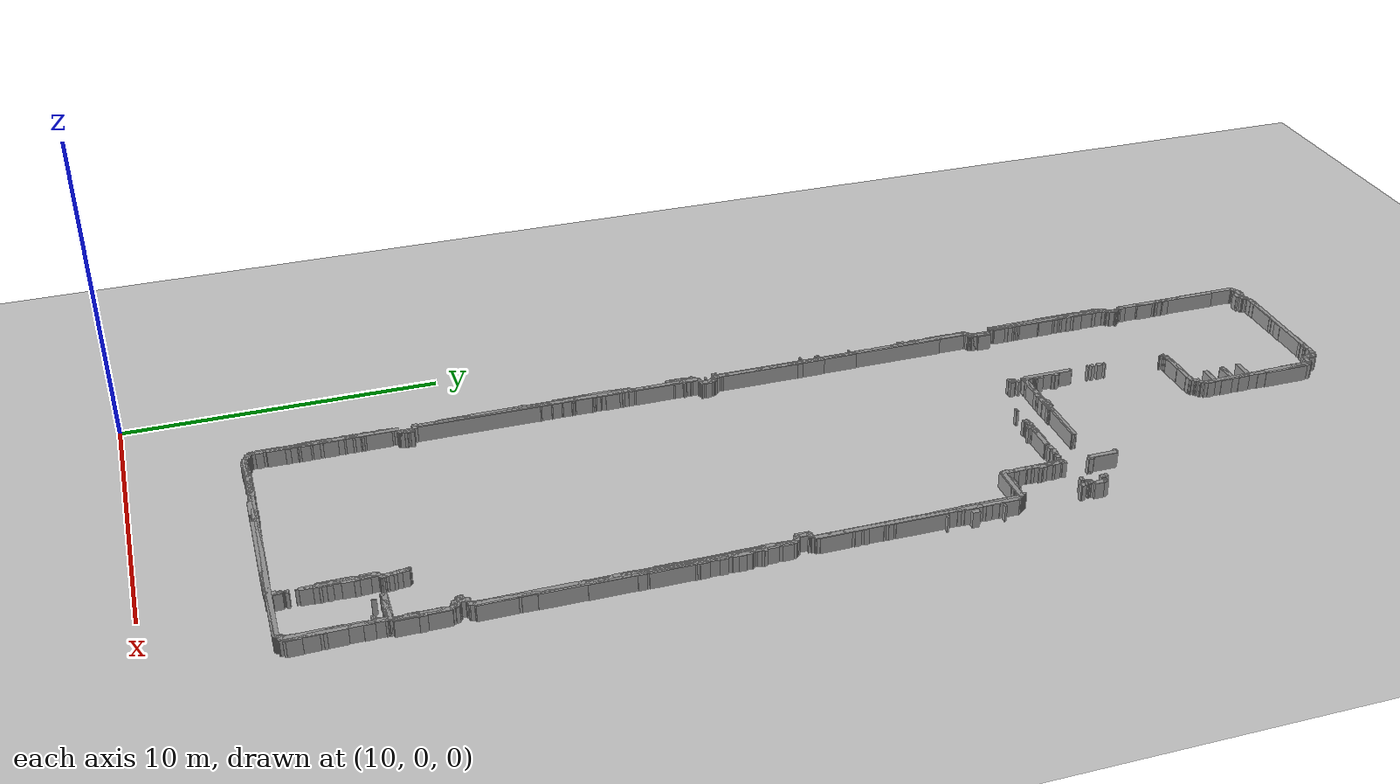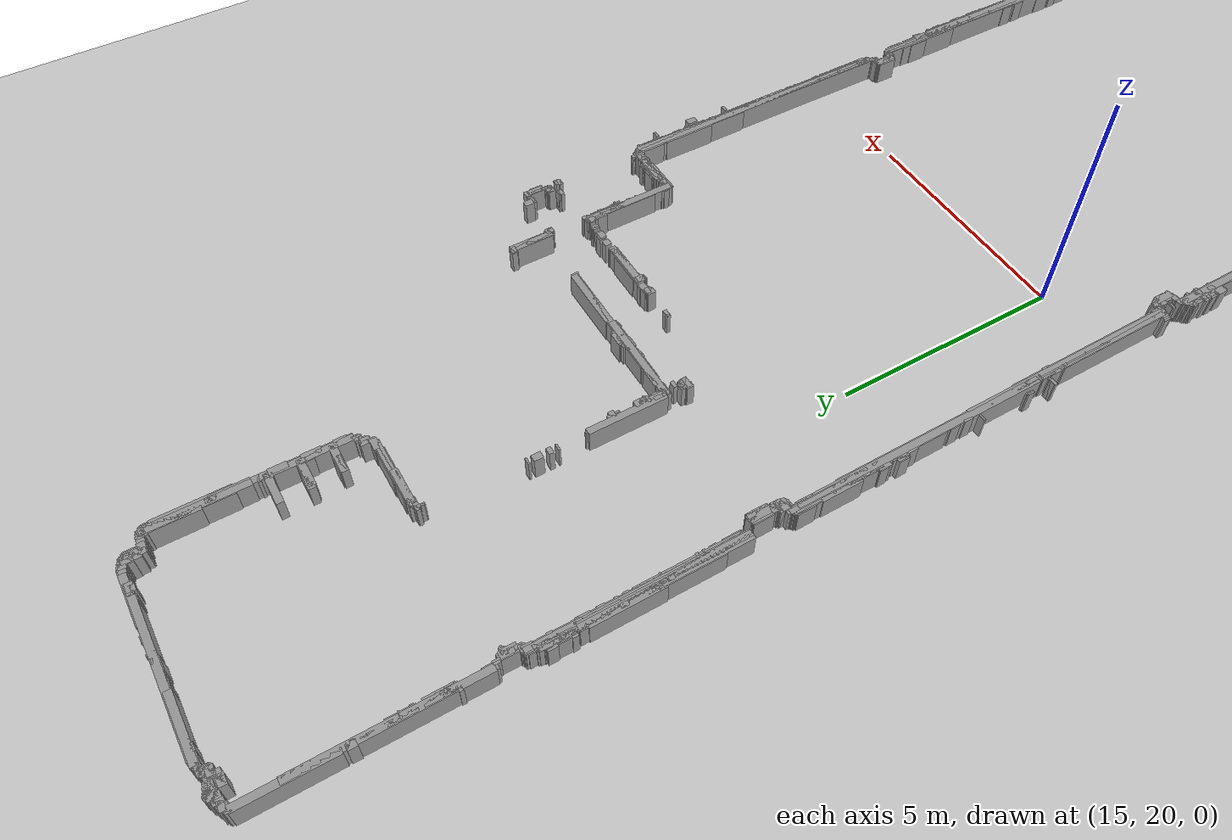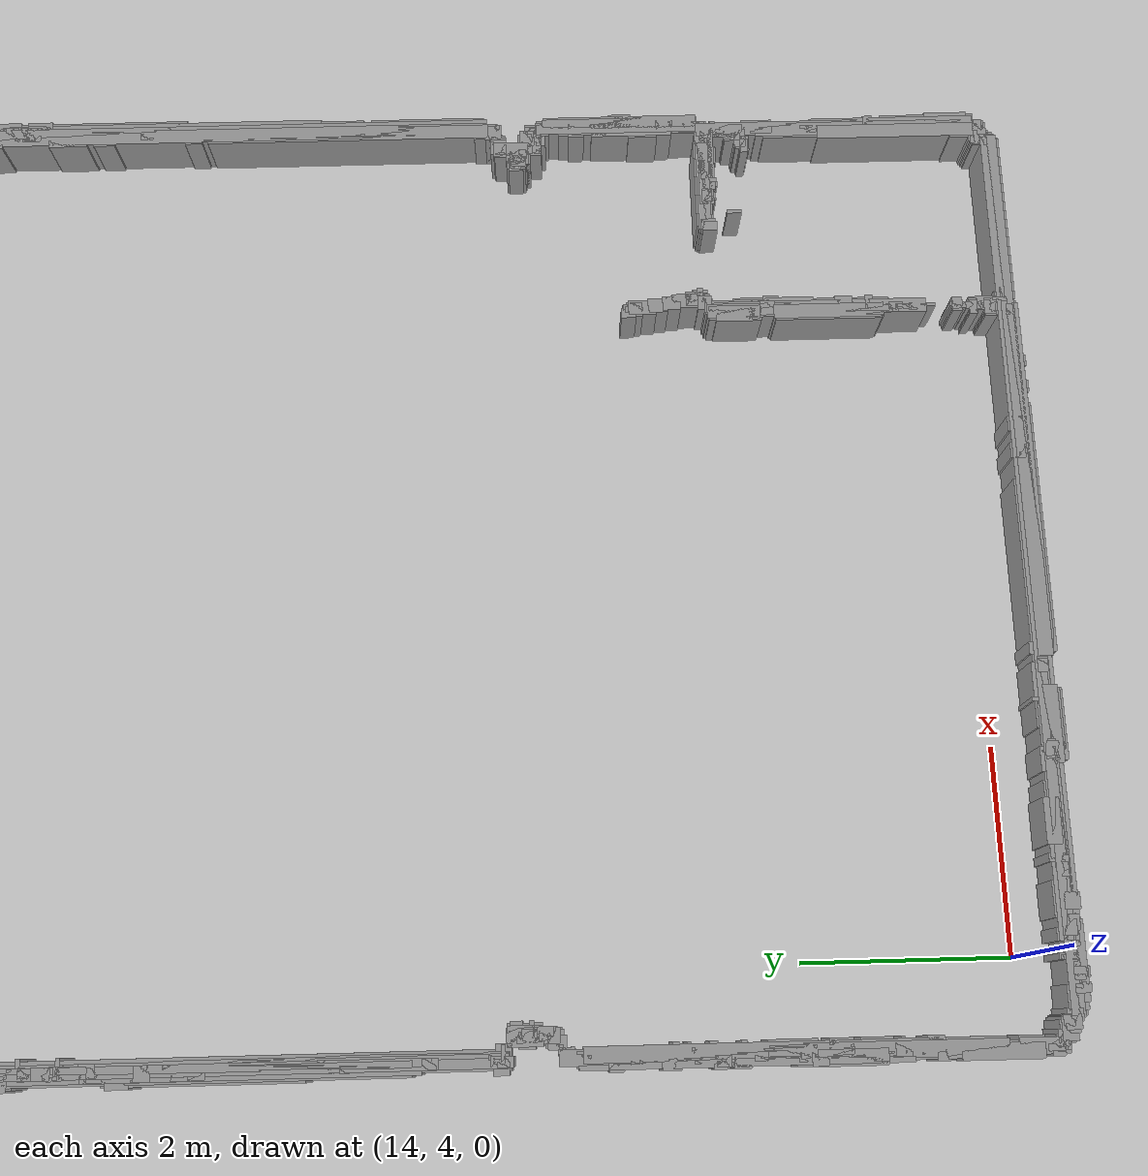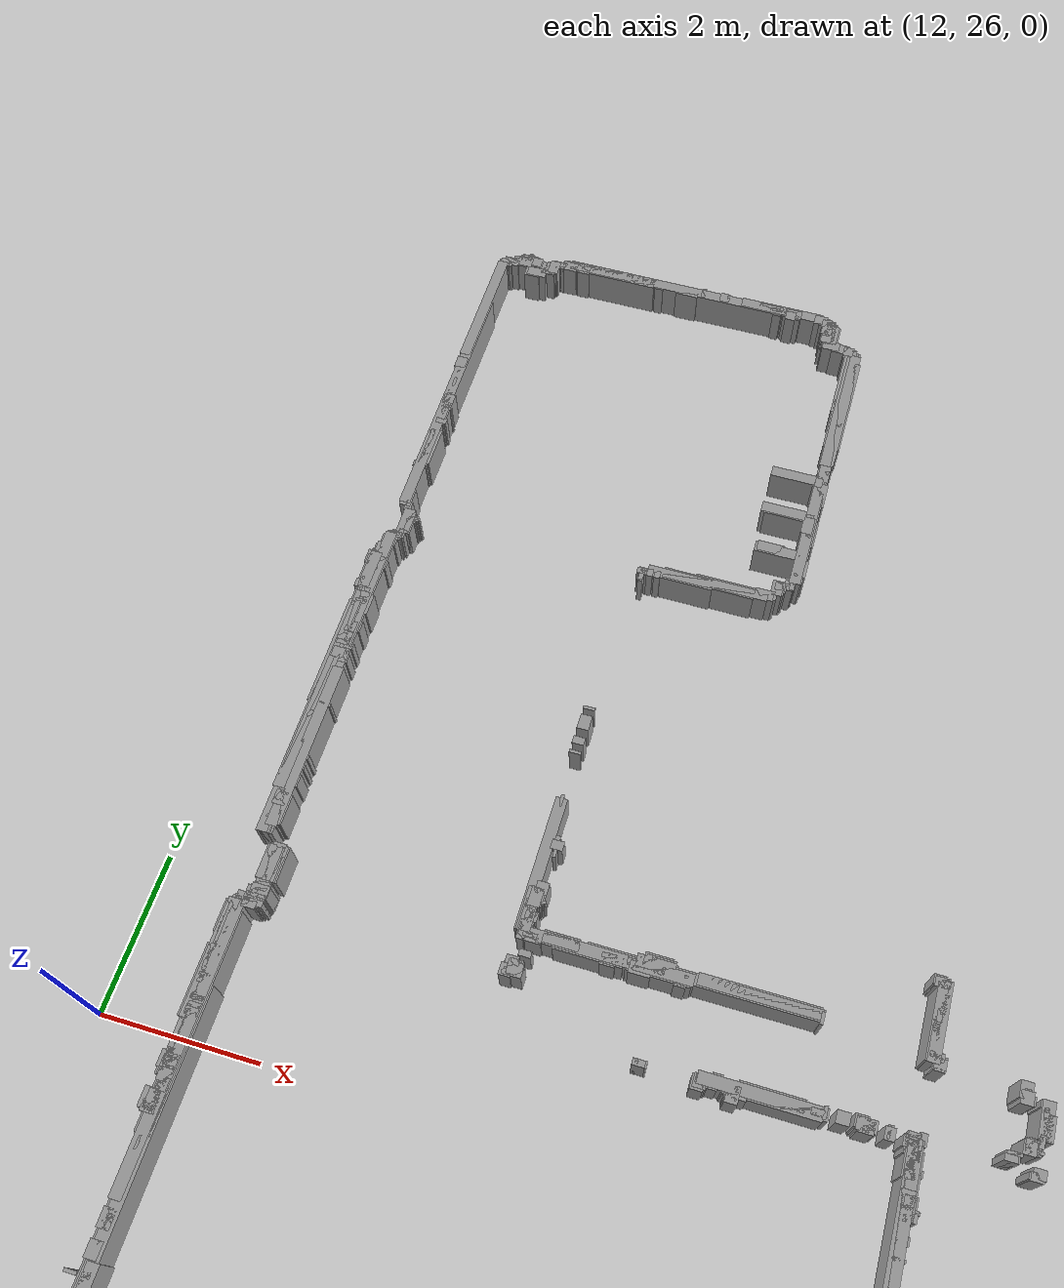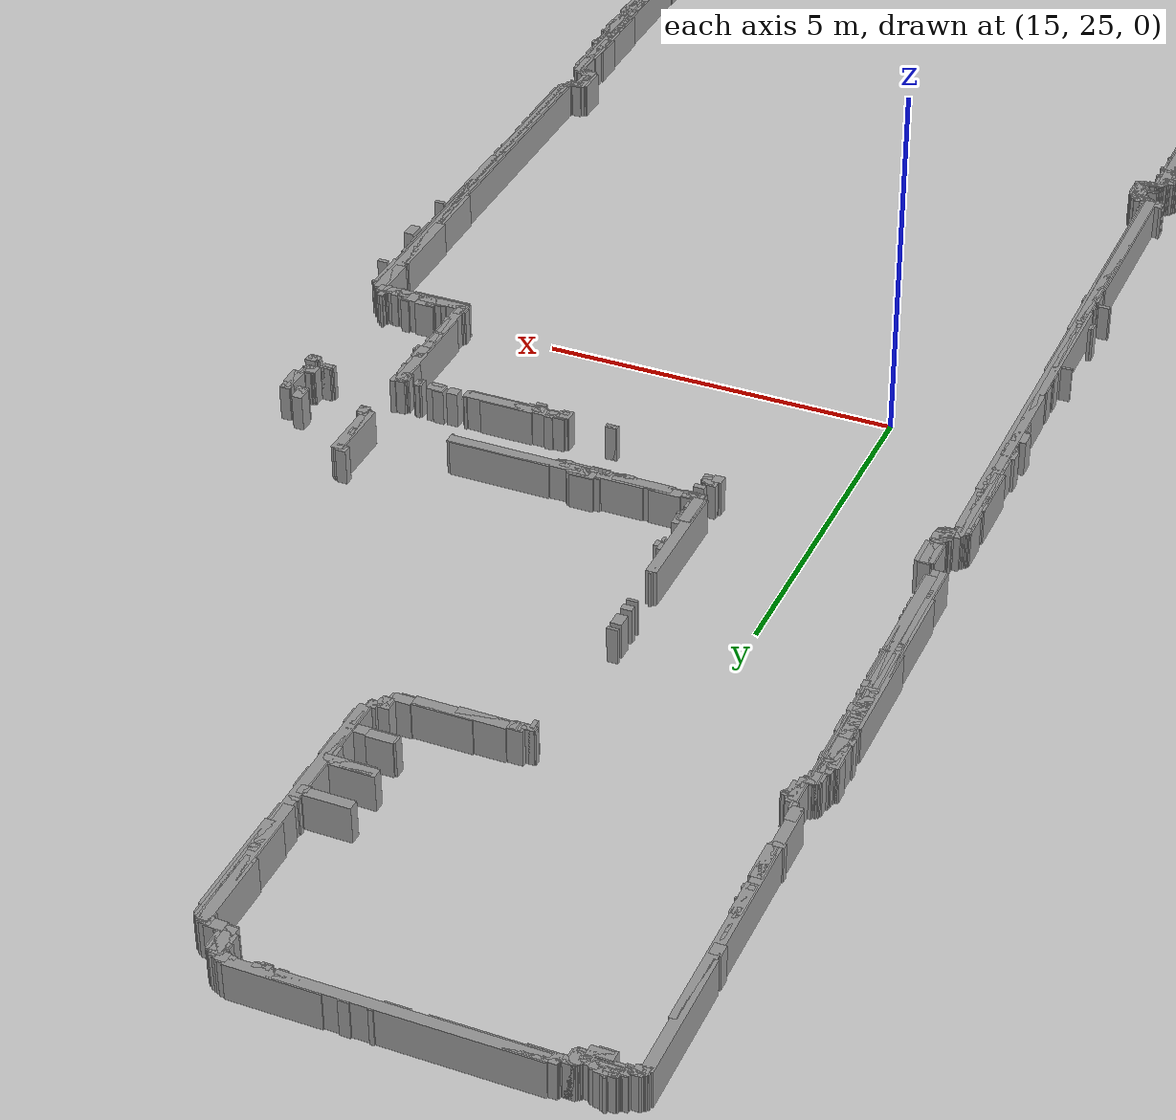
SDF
<sdf version="1.6">
  <world name="default">
    <include>
      <uri>model://sun</uri>
    </include>
    <include>
      <uri>model://ground_plane</uri>
    </include>
    <physics type="ode">
      <real_time_update_rate>1000.0</real_time_update_rate>
      <max_step_size>0.001</max_step_size>
      <real_time_factor>1</real_time_factor>
      <ode>
        <solver>
          <type>quick</type>
          <iters>150</iters>
          <precon_iters>0</precon_iters>
          <sor>1.400000</sor>
          <use_dynamic_moi_rescaling>1</use_dynamic_moi_rescaling>
        </solver>
        <constraints>
          <cfm>0.00001</cfm>
          <erp>0.2</erp>
          <contact_max_correcting_vel>2000.000000</contact_max_correcting_vel>
          <contact_surface_layer>0.01000</contact_surface_layer>
        </constraints>
      </ode>
    </physics>
    <scene>
      <ambient>0.4 0.4 0.4 1</ambient>
      <background>0.7 0.7 0.7 1</background>
      <shadows>true</shadows>
    </scene>
    <gui fullscreen="0">
      <camera name="user_camera">
        <pose>0.0 0.0 17.0 -1.5708 1.5708 0</pose>
        <view_controller>orbit</view_controller>
      </camera>
    </gui>
    <model name="obstacle">
      <static>1</static>
      <pose frame="">0 0 0 0 0 0</pose>
      <link name="obstacle">
        <collision name="obstacle_1">
          <pose>15.88 3.54 0 0 0 1.5708</pose>
          <geometry>
            <box>
              <size>0.16 0.15 1.0</size>
            </box>
          </geometry>
        </collision>
        <visual name="obstacle_1">
          <pose>15.88 3.54 0 0 0 1.5708</pose>
          <geometry>
            <box>
              <size>0.16 0.15 1.0</size>
            </box>
          </geometry>
          <material>
            <script>
              <uri>file://media/materials/scripts/gazebo.material</uri>
              <name>Gazebo/Grey</name>
            </script>
            <ambient>1 1 1 1</ambient>
          </material>
        </visual>
        <collision name="obstacle_2">
          <pose>15.9 3.54 0 0 0 1.5708</pose>
          <geometry>
            <box>
              <size>0.16 0.15 1.0</size>
            </box>
          </geometry>
        </collision>
        <visual name="obstacle_2">
          <pose>15.9 3.54 0 0 0 1.5708</pose>
          <geometry>
            <box>
              <size>0.16 0.15 1.0</size>
            </box>
          </geometry>
          <material>
            <script>
              <uri>file://media/materials/scripts/gazebo.material</uri>
              <name>Gazebo/Grey</name>
            </script>
            <ambient>1 1 1 1</ambient>
          </material>
        </visual>
        <collision name="obstacle_3">
          <pose>15.92 3.52 0 0 0 1.5708</pose>
          <geometry>
            <box>
              <size>0.14 0.15 1.0</size>
            </box>
          </geometry>
        </collision>
        <visual name="obstacle_3">
          <pose>15.92 3.52 0 0 0 1.5708</pose>
          <geometry>
            <box>
              <size>0.14 0.15 1.0</size>
            </box>
          </geometry>
          <material>
            <script>
              <uri>file://media/materials/scripts/gazebo.material</uri>
              <name>Gazebo/Grey</name>
            </script>
            <ambient>1 1 1 1</ambient>
          </material>
        </visual>
        <collision name="obstacle_4">
          <pose>15.94 3.52 0 0 0 1.5708</pose>
          <geometry>
            <box>
              <size>0.14 0.15 1.0</size>
            </box>
          </geometry>
        </collision>
        <visual name="obstacle_4">
          <pose>15.94 3.52 0 0 0 1.5708</pose>
          <geometry>
            <box>
              <size>0.14 0.15 1.0</size>
            </box>
          </geometry>
          <material>
            <script>
              <uri>file://media/materials/scripts/gazebo.material</uri>
              <name>Gazebo/Grey</name>
            </script>
            <ambient>1 1 1 1</ambient>
          </material>
        </visual>
        <collision name="obstacle_5">
          <pose>13.84 3.52 0 0 0 1.5708</pose>
          <geometry>
            <box>
              <size>0.1 0.15 1.0</size>
            </box>
          </geometry>
        </collision>
        <visual name="obstacle_5">
          <pose>13.84 3.52 0 0 0 1.5708</pose>
          <geometry>
            <box>
              <size>0.1 0.15 1.0</size>
            </box>
          </geometry>
          <material>
            <script>
              <uri>file://media/materials/scripts/gazebo.material</uri>
              <name>Gazebo/Grey</name>
            </script>
            <ambient>1 1 1 1</ambient>
          </material>
        </visual>
        <collision name="obstacle_6">
          <pose>13.86 3.52 0 0 0 1.5708</pose>
          <geometry>
            <box>
              <size>0.1 0.15 1.0</size>
            </box>
          </geometry>
        </collision>
        <visual name="obstacle_6">
          <pose>13.86 3.52 0 0 0 1.5708</pose>
          <geometry>
            <box>
              <size>0.1 0.15 1.0</size>
            </box>
          </geometry>
          <material>
            <script>
              <uri>file://media/materials/scripts/gazebo.material</uri>
              <name>Gazebo/Grey</name>
            </script>
            <ambient>1 1 1 1</ambient>
          </material>
        </visual>
        <collision name="obstacle_7">
          <pose>14.280000000000001 3.54 0 0 0 1.5708</pose>
          <geometry>
            <box>
              <size>0.14 0.15 1.0</size>
            </box>
          </geometry>
        </collision>
        <visual name="obstacle_7">
          <pose>14.280000000000001 3.54 0 0 0 1.5708</pose>
          <geometry>
            <box>
              <size>0.14 0.15 1.0</size>
            </box>
          </geometry>
          <material>
            <script>
              <uri>file://media/materials/scripts/gazebo.material</uri>
              <name>Gazebo/Grey</name>
            </script>
            <ambient>1 1 1 1</ambient>
          </material>
        </visual>
        <collision name="obstacle_8">
          <pose>16.14 3.48 0 0 0 0</pose>
          <geometry>
            <box>
              <size>0.7000000000000001 0.15 1.0</size>
            </box>
          </geometry>
        </collision>
        <visual name="obstacle_8">
          <pose>16.14 3.48 0 0 0 0</pose>
          <geometry>
            <box>
              <size>0.7000000000000001 0.15 1.0</size>
            </box>
          </geometry>
          <material>
            <script>
              <uri>file://media/materials/scripts/gazebo.material</uri>
              <name>Gazebo/Grey</name>
            </script>
            <ambient>1 1 1 1</ambient>
          </material>
        </visual>
        <collision name="obstacle_9">
          <pose>18.12 3.48 0 0 0 0</pose>
          <geometry>
            <box>
              <size>2.56 0.15 1.0</size>
            </box>
          </geometry>
        </collision>
        <visual name="obstacle_9">
          <pose>18.12 3.48 0 0 0 0</pose>
          <geometry>
            <box>
              <size>2.56 0.15 1.0</size>
            </box>
          </geometry>
          <material>
            <script>
              <uri>file://media/materials/scripts/gazebo.material</uri>
              <name>Gazebo/Grey</name>
            </script>
            <ambient>1 1 1 1</ambient>
          </material>
        </visual>
        <collision name="obstacle_10">
          <pose>19.580000000000002 3.48 0 0 0 0</pose>
          <geometry>
            <box>
              <size>0.12 0.15 1.0</size>
            </box>
          </geometry>
        </collision>
        <visual name="obstacle_10">
          <pose>19.580000000000002 3.48 0 0 0 0</pose>
          <geometry>
            <box>
              <size>0.12 0.15 1.0</size>
            </box>
          </geometry>
          <material>
            <script>
              <uri>file://media/materials/scripts/gazebo.material</uri>
              <name>Gazebo/Grey</name>
            </script>
            <ambient>1 1 1 1</ambient>
          </material>
        </visual>
        <collision name="obstacle_11">
          <pose>19.86 3.48 0 0 0 0</pose>
          <geometry>
            <box>
              <size>0.12 0.15 1.0</size>
            </box>
          </geometry>
        </collision>
        <visual name="obstacle_11">
          <pose>19.86 3.48 0 0 0 0</pose>
          <geometry>
            <box>
              <size>0.12 0.15 1.0</size>
            </box>
          </geometry>
          <material>
            <script>
              <uri>file://media/materials/scripts/gazebo.material</uri>
              <name>Gazebo/Grey</name>
            </script>
            <ambient>1 1 1 1</ambient>
          </material>
        </visual>
        <collision name="obstacle_12">
          <pose>13.700000000000001 3.5 0 0 0 0</pose>
          <geometry>
            <box>
              <size>0.1 0.15 1.0</size>
            </box>
          </geometry>
        </collision>
        <visual name="obstacle_12">
          <pose>13.700000000000001 3.5 0 0 0 0</pose>
          <geometry>
            <box>
              <size>0.1 0.15 1.0</size>
            </box>
          </geometry>
          <material>
            <script>
              <uri>file://media/materials/scripts/gazebo.material</uri>
              <name>Gazebo/Grey</name>
            </script>
            <ambient>1 1 1 1</ambient>
          </material>
        </visual>
        <collision name="obstacle_13">
          <pose>13.84 3.5 0 0 0 0</pose>
          <geometry>
            <box>
              <size>0.1 0.15 1.0</size>
            </box>
          </geometry>
        </collision>
        <visual name="obstacle_13">
          <pose>13.84 3.5 0 0 0 0</pose>
          <geometry>
            <box>
              <size>0.1 0.15 1.0</size>
            </box>
          </geometry>
          <material>
            <script>
              <uri>file://media/materials/scripts/gazebo.material</uri>
              <name>Gazebo/Grey</name>
            </script>
            <ambient>1 1 1 1</ambient>
          </material>
        </visual>
        <collision name="obstacle_14">
          <pose>14.14 3.56 0 0 0 1.5708</pose>
          <geometry>
            <box>
              <size>0.14 0.15 1.0</size>
            </box>
          </geometry>
        </collision>
        <visual name="obstacle_14">
          <pose>14.14 3.56 0 0 0 1.5708</pose>
          <geometry>
            <box>
              <size>0.14 0.15 1.0</size>
            </box>
          </geometry>
          <material>
            <script>
              <uri>file://media/materials/scripts/gazebo.material</uri>
              <name>Gazebo/Grey</name>
            </script>
            <ambient>1 1 1 1</ambient>
          </material>
        </visual>
        <collision name="obstacle_15">
          <pose>14.16 3.56 0 0 0 1.5708</pose>
          <geometry>
            <box>
              <size>0.14 0.15 1.0</size>
            </box>
          </geometry>
        </collision>
        <visual name="obstacle_15">
          <pose>14.16 3.56 0 0 0 1.5708</pose>
          <geometry>
            <box>
              <size>0.14 0.15 1.0</size>
            </box>
          </geometry>
          <material>
            <script>
              <uri>file://media/materials/scripts/gazebo.material</uri>
              <name>Gazebo/Grey</name>
            </script>
            <ambient>1 1 1 1</ambient>
          </material>
        </visual>
        <collision name="obstacle_16">
          <pose>14.18 3.56 0 0 0 1.5708</pose>
          <geometry>
            <box>
              <size>0.14 0.15 1.0</size>
            </box>
          </geometry>
        </collision>
        <visual name="obstacle_16">
          <pose>14.18 3.56 0 0 0 1.5708</pose>
          <geometry>
            <box>
              <size>0.14 0.15 1.0</size>
            </box>
          </geometry>
          <material>
            <script>
              <uri>file://media/materials/scripts/gazebo.material</uri>
              <name>Gazebo/Grey</name>
            </script>
            <ambient>1 1 1 1</ambient>
          </material>
        </visual>
        <collision name="obstacle_17">
          <pose>14.200000000000001 3.56 0 0 0 1.5708</pose>
          <geometry>
            <box>
              <size>0.14 0.15 1.0</size>
            </box>
          </geometry>
        </collision>
        <visual name="obstacle_17">
          <pose>14.200000000000001 3.56 0 0 0 1.5708</pose>
          <geometry>
            <box>
              <size>0.14 0.15 1.0</size>
            </box>
          </geometry>
          <material>
            <script>
              <uri>file://media/materials/scripts/gazebo.material</uri>
              <name>Gazebo/Grey</name>
            </script>
            <ambient>1 1 1 1</ambient>
          </material>
        </visual>
        <collision name="obstacle_18">
          <pose>14.24 3.56 0 0 0 1.5708</pose>
          <geometry>
            <box>
              <size>0.12 0.15 1.0</size>
            </box>
          </geometry>
        </collision>
        <visual name="obstacle_18">
          <pose>14.24 3.56 0 0 0 1.5708</pose>
          <geometry>
            <box>
              <size>0.12 0.15 1.0</size>
            </box>
          </geometry>
          <material>
            <script>
              <uri>file://media/materials/scripts/gazebo.material</uri>
              <name>Gazebo/Grey</name>
            </script>
            <ambient>1 1 1 1</ambient>
          </material>
        </visual>
        <collision name="obstacle_19">
          <pose>14.26 3.56 0 0 0 1.5708</pose>
          <geometry>
            <box>
              <size>0.12 0.15 1.0</size>
            </box>
          </geometry>
        </collision>
        <visual name="obstacle_19">
          <pose>14.26 3.56 0 0 0 1.5708</pose>
          <geometry>
            <box>
              <size>0.12 0.15 1.0</size>
            </box>
          </geometry>
          <material>
            <script>
              <uri>file://media/materials/scripts/gazebo.material</uri>
              <name>Gazebo/Grey</name>
            </script>
            <ambient>1 1 1 1</ambient>
          </material>
        </visual>
        <collision name="obstacle_20">
          <pose>16.14 3.5 0 0 0 0</pose>
          <geometry>
            <box>
              <size>0.7000000000000001 0.15 1.0</size>
            </box>
          </geometry>
        </collision>
        <visual name="obstacle_20">
          <pose>16.14 3.5 0 0 0 0</pose>
          <geometry>
            <box>
              <size>0.7000000000000001 0.15 1.0</size>
            </box>
          </geometry>
          <material>
            <script>
              <uri>file://media/materials/scripts/gazebo.material</uri>
              <name>Gazebo/Grey</name>
            </script>
            <ambient>1 1 1 1</ambient>
          </material>
        </visual>
        <collision name="obstacle_21">
          <pose>18.66 3.5 0 0 0 0</pose>
          <geometry>
            <box>
              <size>3.66 0.15 1.0</size>
            </box>
          </geometry>
        </collision>
        <visual name="obstacle_21">
          <pose>18.66 3.5 0 0 0 0</pose>
          <geometry>
            <box>
              <size>3.66 0.15 1.0</size>
            </box>
          </geometry>
          <material>
            <script>
              <uri>file://media/materials/scripts/gazebo.material</uri>
              <name>Gazebo/Grey</name>
            </script>
            <ambient>1 1 1 1</ambient>
          </material>
        </visual>
        <collision name="obstacle_22">
          <pose>13.94 3.52 0 0 0 0</pose>
          <geometry>
            <box>
              <size>0.74 0.15 1.0</size>
            </box>
          </geometry>
        </collision>
        <visual name="obstacle_22">
          <pose>13.94 3.52 0 0 0 0</pose>
          <geometry>
            <box>
              <size>0.74 0.15 1.0</size>
            </box>
          </geometry>
          <material>
            <script>
              <uri>file://media/materials/scripts/gazebo.material</uri>
              <name>Gazebo/Grey</name>
            </script>
            <ambient>1 1 1 1</ambient>
          </material>
        </visual>
        <collision name="obstacle_23">
          <pose>14.48 3.52 0 0 0 0</pose>
          <geometry>
            <box>
              <size>0.16 0.15 1.0</size>
            </box>
          </geometry>
        </collision>
        <visual name="obstacle_23">
          <pose>14.48 3.52 0 0 0 0</pose>
          <geometry>
            <box>
              <size>0.16 0.15 1.0</size>
            </box>
          </geometry>
          <material>
            <script>
              <uri>file://media/materials/scripts/gazebo.material</uri>
              <name>Gazebo/Grey</name>
            </script>
            <ambient>1 1 1 1</ambient>
          </material>
        </visual>
        <collision name="obstacle_24">
          <pose>14.76 3.58 0 0 0 1.5708</pose>
          <geometry>
            <box>
              <size>0.12 0.15 1.0</size>
            </box>
          </geometry>
        </collision>
        <visual name="obstacle_24">
          <pose>14.76 3.58 0 0 0 1.5708</pose>
          <geometry>
            <box>
              <size>0.12 0.15 1.0</size>
            </box>
          </geometry>
          <material>
            <script>
              <uri>file://media/materials/scripts/gazebo.material</uri>
              <name>Gazebo/Grey</name>
            </script>
            <ambient>1 1 1 1</ambient>
          </material>
        </visual>
        <collision name="obstacle_25">
          <pose>14.780000000000001 3.58 0 0 0 1.5708</pose>
          <geometry>
            <box>
              <size>0.12 0.15 1.0</size>
            </box>
          </geometry>
        </collision>
        <visual name="obstacle_25">
          <pose>14.780000000000001 3.58 0 0 0 1.5708</pose>
          <geometry>
            <box>
              <size>0.12 0.15 1.0</size>
            </box>
          </geometry>
          <material>
            <script>
              <uri>file://media/materials/scripts/gazebo.material</uri>
              <name>Gazebo/Grey</name>
            </script>
            <ambient>1 1 1 1</ambient>
          </material>
        </visual>
        <collision name="obstacle_26">
          <pose>14.8 3.58 0 0 0 1.5708</pose>
          <geometry>
            <box>
              <size>0.12 0.15 1.0</size>
            </box>
          </geometry>
        </collision>
        <visual name="obstacle_26">
          <pose>14.8 3.58 0 0 0 1.5708</pose>
          <geometry>
            <box>
              <size>0.12 0.15 1.0</size>
            </box>
          </geometry>
          <material>
            <script>
              <uri>file://media/materials/scripts/gazebo.material</uri>
              <name>Gazebo/Grey</name>
            </script>
            <ambient>1 1 1 1</ambient>
          </material>
        </visual>
        <collision name="obstacle_27">
          <pose>14.82 3.58 0 0 0 1.5708</pose>
          <geometry>
            <box>
              <size>0.14 0.15 1.0</size>
            </box>
          </geometry>
        </collision>
        <visual name="obstacle_27">
          <pose>14.82 3.58 0 0 0 1.5708</pose>
          <geometry>
            <box>
              <size>0.14 0.15 1.0</size>
            </box>
          </geometry>
          <material>
            <script>
              <uri>file://media/materials/scripts/gazebo.material</uri>
              <name>Gazebo/Grey</name>
            </script>
            <ambient>1 1 1 1</ambient>
          </material>
        </visual>
        <collision name="obstacle_28">
          <pose>16.14 3.52 0 0 0 0</pose>
          <geometry>
            <box>
              <size>0.76 0.15 1.0</size>
            </box>
          </geometry>
        </collision>
        <visual name="obstacle_28">
          <pose>16.14 3.52 0 0 0 0</pose>
          <geometry>
            <box>
              <size>0.76 0.15 1.0</size>
            </box>
          </geometry>
          <material>
            <script>
              <uri>file://media/materials/scripts/gazebo.material</uri>
              <name>Gazebo/Grey</name>
            </script>
            <ambient>1 1 1 1</ambient>
          </material>
        </visual>
        <collision name="obstacle_29">
          <pose>16.7 3.56 0 0 0 1.5708</pose>
          <geometry>
            <box>
              <size>0.1 0.15 1.0</size>
            </box>
          </geometry>
        </collision>
        <visual name="obstacle_29">
          <pose>16.7 3.56 0 0 0 1.5708</pose>
          <geometry>
            <box>
              <size>0.1 0.15 1.0</size>
            </box>
          </geometry>
          <material>
            <script>
              <uri>file://media/materials/scripts/gazebo.material</uri>
              <name>Gazebo/Grey</name>
            </script>
            <ambient>1 1 1 1</ambient>
          </material>
        </visual>
        <collision name="obstacle_30">
          <pose>16.72 3.56 0 0 0 1.5708</pose>
          <geometry>
            <box>
              <size>0.1 0.15 1.0</size>
            </box>
          </geometry>
        </collision>
        <visual name="obstacle_30">
          <pose>16.72 3.56 0 0 0 1.5708</pose>
          <geometry>
            <box>
              <size>0.1 0.15 1.0</size>
            </box>
          </geometry>
          <material>
            <script>
              <uri>file://media/materials/scripts/gazebo.material</uri>
              <name>Gazebo/Grey</name>
            </script>
            <ambient>1 1 1 1</ambient>
          </material>
        </visual>
        <collision name="obstacle_31">
          <pose>16.740000000000002 3.56 0 0 0 1.5708</pose>
          <geometry>
            <box>
              <size>0.08 0.15 1.0</size>
            </box>
          </geometry>
        </collision>
        <visual name="obstacle_31">
          <pose>16.740000000000002 3.56 0 0 0 1.5708</pose>
          <geometry>
            <box>
              <size>0.08 0.15 1.0</size>
            </box>
          </geometry>
          <material>
            <script>
              <uri>file://media/materials/scripts/gazebo.material</uri>
              <name>Gazebo/Grey</name>
            </script>
            <ambient>1 1 1 1</ambient>
          </material>
        </visual>
        <collision name="obstacle_32">
          <pose>16.76 3.56 0 0 0 1.5708</pose>
          <geometry>
            <box>
              <size>0.08 0.15 1.0</size>
            </box>
          </geometry>
        </collision>
        <visual name="obstacle_32">
          <pose>16.76 3.56 0 0 0 1.5708</pose>
          <geometry>
            <box>
              <size>0.08 0.15 1.0</size>
            </box>
          </geometry>
          <material>
            <script>
              <uri>file://media/materials/scripts/gazebo.material</uri>
              <name>Gazebo/Grey</name>
            </script>
            <ambient>1 1 1 1</ambient>
          </material>
        </visual>
        <collision name="obstacle_33">
          <pose>18.66 3.52 0 0 0 0</pose>
          <geometry>
            <box>
              <size>3.72 0.15 1.0</size>
            </box>
          </geometry>
        </collision>
        <visual name="obstacle_33">
          <pose>18.66 3.52 0 0 0 0</pose>
          <geometry>
            <box>
              <size>3.72 0.15 1.0</size>
            </box>
          </geometry>
          <material>
            <script>
              <uri>file://media/materials/scripts/gazebo.material</uri>
              <name>Gazebo/Grey</name>
            </script>
            <ambient>1 1 1 1</ambient>
          </material>
        </visual>
        <collision name="obstacle_34">
          <pose>21.46 3.52 0 0 0 0</pose>
          <geometry>
            <box>
              <size>1.84 0.15 1.0</size>
            </box>
          </geometry>
        </collision>
        <visual name="obstacle_34">
          <pose>21.46 3.52 0 0 0 0</pose>
          <geometry>
            <box>
              <size>1.84 0.15 1.0</size>
            </box>
          </geometry>
          <material>
            <script>
              <uri>file://media/materials/scripts/gazebo.material</uri>
              <name>Gazebo/Grey</name>
            </script>
            <ambient>1 1 1 1</ambient>
          </material>
        </visual>
        <collision name="obstacle_35">
          <pose>17.96 3.54 0 0 0 0</pose>
          <geometry>
            <box>
              <size>8.92 0.15 1.0</size>
            </box>
          </geometry>
        </collision>
        <visual name="obstacle_35">
          <pose>17.96 3.54 0 0 0 0</pose>
          <geometry>
            <box>
              <size>8.92 0.15 1.0</size>
            </box>
          </geometry>
          <material>
            <script>
              <uri>file://media/materials/scripts/gazebo.material</uri>
              <name>Gazebo/Grey</name>
            </script>
            <ambient>1 1 1 1</ambient>
          </material>
        </visual>
        <collision name="obstacle_36">
          <pose>17.94 3.56 0 0 0 0</pose>
          <geometry>
            <box>
              <size>8.98 0.15 1.0</size>
            </box>
          </geometry>
        </collision>
        <visual name="obstacle_36">
          <pose>17.94 3.56 0 0 0 0</pose>
          <geometry>
            <box>
              <size>8.98 0.15 1.0</size>
            </box>
          </geometry>
          <material>
            <script>
              <uri>file://media/materials/scripts/gazebo.material</uri>
              <name>Gazebo/Grey</name>
            </script>
            <ambient>1 1 1 1</ambient>
          </material>
        </visual>
        <collision name="obstacle_37">
          <pose>13.58 3.58 0 0 0 0</pose>
          <geometry>
            <box>
              <size>0.3 0.15 1.0</size>
            </box>
          </geometry>
        </collision>
        <visual name="obstacle_37">
          <pose>13.58 3.58 0 0 0 0</pose>
          <geometry>
            <box>
              <size>0.3 0.15 1.0</size>
            </box>
          </geometry>
          <material>
            <script>
              <uri>file://media/materials/scripts/gazebo.material</uri>
              <name>Gazebo/Grey</name>
            </script>
            <ambient>1 1 1 1</ambient>
          </material>
        </visual>
        <collision name="obstacle_38">
          <pose>13.98 3.58 0 0 0 0</pose>
          <geometry>
            <box>
              <size>0.06 0.15 1.0</size>
            </box>
          </geometry>
        </collision>
        <visual name="obstacle_38">
          <pose>13.98 3.58 0 0 0 0</pose>
          <geometry>
            <box>
              <size>0.06 0.15 1.0</size>
            </box>
          </geometry>
          <material>
            <script>
              <uri>file://media/materials/scripts/gazebo.material</uri>
              <name>Gazebo/Grey</name>
            </script>
            <ambient>1 1 1 1</ambient>
          </material>
        </visual>
        <collision name="obstacle_39">
          <pose>16.36 3.58 0 0 0 0</pose>
          <geometry>
            <box>
              <size>4.48 0.15 1.0</size>
            </box>
          </geometry>
        </collision>
        <visual name="obstacle_39">
          <pose>16.36 3.58 0 0 0 0</pose>
          <geometry>
            <box>
              <size>4.48 0.15 1.0</size>
            </box>
          </geometry>
          <material>
            <script>
              <uri>file://media/materials/scripts/gazebo.material</uri>
              <name>Gazebo/Grey</name>
            </script>
            <ambient>1 1 1 1</ambient>
          </material>
        </visual>
        <collision name="obstacle_40">
          <pose>18.900000000000002 3.58 0 0 0 0</pose>
          <geometry>
            <box>
              <size>0.16 0.15 1.0</size>
            </box>
          </geometry>
        </collision>
        <visual name="obstacle_40">
          <pose>18.900000000000002 3.58 0 0 0 0</pose>
          <geometry>
            <box>
              <size>0.16 0.15 1.0</size>
            </box>
          </geometry>
          <material>
            <script>
              <uri>file://media/materials/scripts/gazebo.material</uri>
              <name>Gazebo/Grey</name>
            </script>
            <ambient>1 1 1 1</ambient>
          </material>
        </visual>
        <collision name="obstacle_41">
          <pose>19.18 3.58 0 0 0 0</pose>
          <geometry>
            <box>
              <size>0.16 0.15 1.0</size>
            </box>
          </geometry>
        </collision>
        <visual name="obstacle_41">
          <pose>19.18 3.58 0 0 0 0</pose>
          <geometry>
            <box>
              <size>0.16 0.15 1.0</size>
            </box>
          </geometry>
          <material>
            <script>
              <uri>file://media/materials/scripts/gazebo.material</uri>
              <name>Gazebo/Grey</name>
            </script>
            <ambient>1 1 1 1</ambient>
          </material>
        </visual>
        <collision name="obstacle_42">
          <pose>20.5 3.58 0 0 0 0</pose>
          <geometry>
            <box>
              <size>0.26 0.15 1.0</size>
            </box>
          </geometry>
        </collision>
        <visual name="obstacle_42">
          <pose>20.5 3.58 0 0 0 0</pose>
          <geometry>
            <box>
              <size>0.26 0.15 1.0</size>
            </box>
          </geometry>
          <material>
            <script>
              <uri>file://media/materials/scripts/gazebo.material</uri>
              <name>Gazebo/Grey</name>
            </script>
            <ambient>1 1 1 1</ambient>
          </material>
        </visual>
        <collision name="obstacle_43">
          <pose>22.38 3.58 0 0 0 0</pose>
          <geometry>
            <box>
              <size>0.14 0.15 1.0</size>
            </box>
          </geometry>
        </collision>
        <visual name="obstacle_43">
          <pose>22.38 3.58 0 0 0 0</pose>
          <geometry>
            <box>
              <size>0.14 0.15 1.0</size>
            </box>
          </geometry>
          <material>
            <script>
              <uri>file://media/materials/scripts/gazebo.material</uri>
              <name>Gazebo/Grey</name>
            </script>
            <ambient>1 1 1 1</ambient>
          </material>
        </visual>
        <collision name="obstacle_44">
          <pose>13.46 3.6 0 0 0 0</pose>
          <geometry>
            <box>
              <size>0.12 0.15 1.0</size>
            </box>
          </geometry>
        </collision>
        <visual name="obstacle_44">
          <pose>13.46 3.6 0 0 0 0</pose>
          <geometry>
            <box>
              <size>0.12 0.15 1.0</size>
            </box>
          </geometry>
          <material>
            <script>
              <uri>file://media/materials/scripts/gazebo.material</uri>
              <name>Gazebo/Grey</name>
            </script>
            <ambient>1 1 1 1</ambient>
          </material>
        </visual>
        <collision name="obstacle_45">
          <pose>13.98 3.6 0 0 0 0</pose>
          <geometry>
            <box>
              <size>0.06 0.15 1.0</size>
            </box>
          </geometry>
        </collision>
        <visual name="obstacle_45">
          <pose>13.98 3.6 0 0 0 0</pose>
          <geometry>
            <box>
              <size>0.06 0.15 1.0</size>
            </box>
          </geometry>
          <material>
            <script>
              <uri>file://media/materials/scripts/gazebo.material</uri>
              <name>Gazebo/Grey</name>
            </script>
            <ambient>1 1 1 1</ambient>
          </material>
        </visual>
        <collision name="obstacle_46">
          <pose>14.86 3.6 0 0 0 0</pose>
          <geometry>
            <box>
              <size>1.48 0.15 1.0</size>
            </box>
          </geometry>
        </collision>
        <visual name="obstacle_46">
          <pose>14.86 3.6 0 0 0 0</pose>
          <geometry>
            <box>
              <size>1.48 0.15 1.0</size>
            </box>
          </geometry>
          <material>
            <script>
              <uri>file://media/materials/scripts/gazebo.material</uri>
              <name>Gazebo/Grey</name>
            </script>
            <ambient>1 1 1 1</ambient>
          </material>
        </visual>
        <collision name="obstacle_47">
          <pose>15.8 3.6 0 0 0 0</pose>
          <geometry>
            <box>
              <size>0.24 0.15 1.0</size>
            </box>
          </geometry>
        </collision>
        <visual name="obstacle_47">
          <pose>15.8 3.6 0 0 0 0</pose>
          <geometry>
            <box>
              <size>0.24 0.15 1.0</size>
            </box>
          </geometry>
          <material>
            <script>
              <uri>file://media/materials/scripts/gazebo.material</uri>
              <name>Gazebo/Grey</name>
            </script>
            <ambient>1 1 1 1</ambient>
          </material>
        </visual>
        <collision name="obstacle_48">
          <pose>16.42 3.6 0 0 0 0</pose>
          <geometry>
            <box>
              <size>0.64 0.15 1.0</size>
            </box>
          </geometry>
        </collision>
        <visual name="obstacle_48">
          <pose>16.42 3.6 0 0 0 0</pose>
          <geometry>
            <box>
              <size>0.64 0.15 1.0</size>
            </box>
          </geometry>
          <material>
            <script>
              <uri>file://media/materials/scripts/gazebo.material</uri>
              <name>Gazebo/Grey</name>
            </script>
            <ambient>1 1 1 1</ambient>
          </material>
        </visual>
        <collision name="obstacle_49">
          <pose>16.88 3.6 0 0 0 0</pose>
          <geometry>
            <box>
              <size>0.12 0.15 1.0</size>
            </box>
          </geometry>
        </collision>
        <visual name="obstacle_49">
          <pose>16.88 3.6 0 0 0 0</pose>
          <geometry>
            <box>
              <size>0.12 0.15 1.0</size>
            </box>
          </geometry>
          <material>
            <script>
              <uri>file://media/materials/scripts/gazebo.material</uri>
              <name>Gazebo/Grey</name>
            </script>
            <ambient>1 1 1 1</ambient>
          </material>
        </visual>
        <collision name="obstacle_50">
          <pose>20.44 3.68 0 0 0 1.5708</pose>
          <geometry>
            <box>
              <size>0.16 0.15 1.0</size>
            </box>
          </geometry>
        </collision>
        <visual name="obstacle_50">
          <pose>20.44 3.68 0 0 0 1.5708</pose>
          <geometry>
            <box>
              <size>0.16 0.15 1.0</size>
            </box>
          </geometry>
          <material>
            <script>
              <uri>file://media/materials/scripts/gazebo.material</uri>
              <name>Gazebo/Grey</name>
            </script>
            <ambient>1 1 1 1</ambient>
          </material>
        </visual>
        <collision name="obstacle_51">
          <pose>20.46 3.68 0 0 0 1.5708</pose>
          <geometry>
            <box>
              <size>0.18 0.15 1.0</size>
            </box>
          </geometry>
        </collision>
        <visual name="obstacle_51">
          <pose>20.46 3.68 0 0 0 1.5708</pose>
          <geometry>
            <box>
              <size>0.18 0.15 1.0</size>
            </box>
          </geometry>
          <material>
            <script>
              <uri>file://media/materials/scripts/gazebo.material</uri>
              <name>Gazebo/Grey</name>
            </script>
            <ambient>1 1 1 1</ambient>
          </material>
        </visual>
        <collision name="obstacle_52">
          <pose>20.48 3.68 0 0 0 1.5708</pose>
          <geometry>
            <box>
              <size>0.18 0.15 1.0</size>
            </box>
          </geometry>
        </collision>
        <visual name="obstacle_52">
          <pose>20.48 3.68 0 0 0 1.5708</pose>
          <geometry>
            <box>
              <size>0.18 0.15 1.0</size>
            </box>
          </geometry>
          <material>
            <script>
              <uri>file://media/materials/scripts/gazebo.material</uri>
              <name>Gazebo/Grey</name>
            </script>
            <ambient>1 1 1 1</ambient>
          </material>
        </visual>
        <collision name="obstacle_53">
          <pose>20.5 3.7600000000000002 0 0 0 1.5708</pose>
          <geometry>
            <box>
              <size>0.32 0.15 1.0</size>
            </box>
          </geometry>
        </collision>
        <visual name="obstacle_53">
          <pose>20.5 3.7600000000000002 0 0 0 1.5708</pose>
          <geometry>
            <box>
              <size>0.32 0.15 1.0</size>
            </box>
          </geometry>
          <material>
            <script>
              <uri>file://media/materials/scripts/gazebo.material</uri>
              <name>Gazebo/Grey</name>
            </script>
            <ambient>1 1 1 1</ambient>
          </material>
        </visual>
        <collision name="obstacle_54">
          <pose>20.54 3.6 0 0 0 0</pose>
          <geometry>
            <box>
              <size>0.04 0.15 1.0</size>
            </box>
          </geometry>
        </collision>
        <visual name="obstacle_54">
          <pose>20.54 3.6 0 0 0 0</pose>
          <geometry>
            <box>
              <size>0.04 0.15 1.0</size>
            </box>
          </geometry>
          <material>
            <script>
              <uri>file://media/materials/scripts/gazebo.material</uri>
              <name>Gazebo/Grey</name>
            </script>
            <ambient>1 1 1 1</ambient>
          </material>
        </visual>
        <collision name="obstacle_55">
          <pose>22.38 3.6 0 0 0 0</pose>
          <geometry>
            <box>
              <size>0.14 0.15 1.0</size>
            </box>
          </geometry>
        </collision>
        <visual name="obstacle_55">
          <pose>22.38 3.6 0 0 0 0</pose>
          <geometry>
            <box>
              <size>0.14 0.15 1.0</size>
            </box>
          </geometry>
          <material>
            <script>
              <uri>file://media/materials/scripts/gazebo.material</uri>
              <name>Gazebo/Grey</name>
            </script>
            <ambient>1 1 1 1</ambient>
          </material>
        </visual>
        <collision name="obstacle_56">
          <pose>13.4 3.62 0 0 0 0</pose>
          <geometry>
            <box>
              <size>0.14 0.15 1.0</size>
            </box>
          </geometry>
        </collision>
        <visual name="obstacle_56">
          <pose>13.4 3.62 0 0 0 0</pose>
          <geometry>
            <box>
              <size>0.14 0.15 1.0</size>
            </box>
          </geometry>
          <material>
            <script>
              <uri>file://media/materials/scripts/gazebo.material</uri>
              <name>Gazebo/Grey</name>
            </script>
            <ambient>1 1 1 1</ambient>
          </material>
        </visual>
        <collision name="obstacle_57">
          <pose>13.98 3.62 0 0 0 0</pose>
          <geometry>
            <box>
              <size>0.06 0.15 1.0</size>
            </box>
          </geometry>
        </collision>
        <visual name="obstacle_57">
          <pose>13.98 3.62 0 0 0 0</pose>
          <geometry>
            <box>
              <size>0.06 0.15 1.0</size>
            </box>
          </geometry>
          <material>
            <script>
              <uri>file://media/materials/scripts/gazebo.material</uri>
              <name>Gazebo/Grey</name>
            </script>
            <ambient>1 1 1 1</ambient>
          </material>
        </visual>
        <collision name="obstacle_58">
          <pose>14.18 3.62 0 0 0 0</pose>
          <geometry>
            <box>
              <size>0.12 0.15 1.0</size>
            </box>
          </geometry>
        </collision>
        <visual name="obstacle_58">
          <pose>14.18 3.62 0 0 0 0</pose>
          <geometry>
            <box>
              <size>0.12 0.15 1.0</size>
            </box>
          </geometry>
          <material>
            <script>
              <uri>file://media/materials/scripts/gazebo.material</uri>
              <name>Gazebo/Grey</name>
            </script>
            <ambient>1 1 1 1</ambient>
          </material>
        </visual>
        <collision name="obstacle_59">
          <pose>14.5 3.62 0 0 0 0</pose>
          <geometry>
            <box>
              <size>0.34 0.15 1.0</size>
            </box>
          </geometry>
        </collision>
        <visual name="obstacle_59">
          <pose>14.5 3.62 0 0 0 0</pose>
          <geometry>
            <box>
              <size>0.34 0.15 1.0</size>
            </box>
          </geometry>
          <material>
            <script>
              <uri>file://media/materials/scripts/gazebo.material</uri>
              <name>Gazebo/Grey</name>
            </script>
            <ambient>1 1 1 1</ambient>
          </material>
        </visual>
        <collision name="obstacle_60">
          <pose>14.88 3.62 0 0 0 0</pose>
          <geometry>
            <box>
              <size>0.08 0.15 1.0</size>
            </box>
          </geometry>
        </collision>
        <visual name="obstacle_60">
          <pose>14.88 3.62 0 0 0 0</pose>
          <geometry>
            <box>
              <size>0.08 0.15 1.0</size>
            </box>
          </geometry>
          <material>
            <script>
              <uri>file://media/materials/scripts/gazebo.material</uri>
              <name>Gazebo/Grey</name>
            </script>
            <ambient>1 1 1 1</ambient>
          </material>
        </visual>
        <collision name="obstacle_61">
          <pose>15.22 3.62 0 0 0 0</pose>
          <geometry>
            <box>
              <size>0.44 0.15 1.0</size>
            </box>
          </geometry>
        </collision>
        <visual name="obstacle_61">
          <pose>15.22 3.62 0 0 0 0</pose>
          <geometry>
            <box>
              <size>0.44 0.15 1.0</size>
            </box>
          </geometry>
          <material>
            <script>
              <uri>file://media/materials/scripts/gazebo.material</uri>
              <name>Gazebo/Grey</name>
            </script>
            <ambient>1 1 1 1</ambient>
          </material>
        </visual>
        <collision name="obstacle_62">
          <pose>16.38 3.62 0 0 0 0</pose>
          <geometry>
            <box>
              <size>0.04 0.15 1.0</size>
            </box>
          </geometry>
        </collision>
        <visual name="obstacle_62">
          <pose>16.38 3.62 0 0 0 0</pose>
          <geometry>
            <box>
              <size>0.04 0.15 1.0</size>
            </box>
          </geometry>
          <material>
            <script>
              <uri>file://media/materials/scripts/gazebo.material</uri>
              <name>Gazebo/Grey</name>
            </script>
            <ambient>1 1 1 1</ambient>
          </material>
        </visual>
        <collision name="obstacle_63">
          <pose>20.54 3.62 0 0 0 0</pose>
          <geometry>
            <box>
              <size>0.04 0.15 1.0</size>
            </box>
          </geometry>
        </collision>
        <visual name="obstacle_63">
          <pose>20.54 3.62 0 0 0 0</pose>
          <geometry>
            <box>
              <size>0.04 0.15 1.0</size>
            </box>
          </geometry>
          <material>
            <script>
              <uri>file://media/materials/scripts/gazebo.material</uri>
              <name>Gazebo/Grey</name>
            </script>
            <ambient>1 1 1 1</ambient>
          </material>
        </visual>
        <collision name="obstacle_64">
          <pose>22.400000000000002 3.62 0 0 0 0</pose>
          <geometry>
            <box>
              <size>0.16 0.15 1.0</size>
            </box>
          </geometry>
        </collision>
        <visual name="obstacle_64">
          <pose>22.400000000000002 3.62 0 0 0 0</pose>
          <geometry>
            <box>
              <size>0.16 0.15 1.0</size>
            </box>
          </geometry>
          <material>
            <script>
              <uri>file://media/materials/scripts/gazebo.material</uri>
              <name>Gazebo/Grey</name>
            </script>
            <ambient>1 1 1 1</ambient>
          </material>
        </visual>
        <collision name="obstacle_65">
          <pose>13.38 3.64 0 0 0 0</pose>
          <geometry>
            <box>
              <size>0.16 0.15 1.0</size>
            </box>
          </geometry>
        </collision>
        <visual name="obstacle_65">
          <pose>13.38 3.64 0 0 0 0</pose>
          <geometry>
            <box>
              <size>0.16 0.15 1.0</size>
            </box>
          </geometry>
          <material>
            <script>
              <uri>file://media/materials/scripts/gazebo.material</uri>
              <name>Gazebo/Grey</name>
            </script>
            <ambient>1 1 1 1</ambient>
          </material>
        </visual>
        <collision name="obstacle_67">
          <pose>22.44 3.64 0 0 0 0</pose>
          <geometry>
            <box>
              <size>0.26 0.15 1.0</size>
            </box>
          </geometry>
        </collision>
        <visual name="obstacle_67">
          <pose>22.44 3.64 0 0 0 0</pose>
          <geometry>
            <box>
              <size>0.26 0.15 1.0</size>
            </box>
          </geometry>
          <material>
            <script>
              <uri>file://media/materials/scripts/gazebo.material</uri>
              <name>Gazebo/Grey</name>
            </script>
            <ambient>1 1 1 1</ambient>
          </material>
        </visual>
        <collision name="obstacle_68">
          <pose>13.34 3.66 0 0 0 0</pose>
          <geometry>
            <box>
              <size>0.22 0.15 1.0</size>
            </box>
          </geometry>
        </collision>
        <visual name="obstacle_68">
          <pose>13.34 3.66 0 0 0 0</pose>
          <geometry>
            <box>
              <size>0.22 0.15 1.0</size>
            </box>
          </geometry>
          <material>
            <script>
              <uri>file://media/materials/scripts/gazebo.material</uri>
              <name>Gazebo/Grey</name>
            </script>
            <ambient>1 1 1 1</ambient>
          </material>
        </visual>
        <collision name="obstacle_69">
          <pose>22.46 3.66 0 0 0 0</pose>
          <geometry>
            <box>
              <size>0.26 0.15 1.0</size>
            </box>
          </geometry>
        </collision>
        <visual name="obstacle_69">
          <pose>22.46 3.66 0 0 0 0</pose>
          <geometry>
            <box>
              <size>0.26 0.15 1.0</size>
            </box>
          </geometry>
          <material>
            <script>
              <uri>file://media/materials/scripts/gazebo.material</uri>
              <name>Gazebo/Grey</name>
            </script>
            <ambient>1 1 1 1</ambient>
          </material>
        </visual>
        <collision name="obstacle_70">
          <pose>13.200000000000001 3.9 0 0 0 1.5708</pose>
          <geometry>
            <box>
              <size>0.46 0.15 1.0</size>
            </box>
          </geometry>
        </collision>
        <visual name="obstacle_70">
          <pose>13.200000000000001 3.9 0 0 0 1.5708</pose>
          <geometry>
            <box>
              <size>0.46 0.15 1.0</size>
            </box>
          </geometry>
          <material>
            <script>
              <uri>file://media/materials/scripts/gazebo.material</uri>
              <name>Gazebo/Grey</name>
            </script>
            <ambient>1 1 1 1</ambient>
          </material>
        </visual>
        <collision name="obstacle_71">
          <pose>13.32 3.68 0 0 0 0</pose>
          <geometry>
            <box>
              <size>0.2 0.15 1.0</size>
            </box>
          </geometry>
        </collision>
        <visual name="obstacle_71">
          <pose>13.32 3.68 0 0 0 0</pose>
          <geometry>
            <box>
              <size>0.2 0.15 1.0</size>
            </box>
          </geometry>
          <material>
            <script>
              <uri>file://media/materials/scripts/gazebo.material</uri>
              <name>Gazebo/Grey</name>
            </script>
            <ambient>1 1 1 1</ambient>
          </material>
        </visual>
        <collision name="obstacle_72">
          <pose>22.48 3.68 0 0 0 0</pose>
          <geometry>
            <box>
              <size>0.24 0.15 1.0</size>
            </box>
          </geometry>
        </collision>
        <visual name="obstacle_72">
          <pose>22.48 3.68 0 0 0 0</pose>
          <geometry>
            <box>
              <size>0.24 0.15 1.0</size>
            </box>
          </geometry>
          <material>
            <script>
              <uri>file://media/materials/scripts/gazebo.material</uri>
              <name>Gazebo/Grey</name>
            </script>
            <ambient>1 1 1 1</ambient>
          </material>
        </visual>
        <collision name="obstacle_73">
          <pose>13.280000000000001 3.7 0 0 0 0</pose>
          <geometry>
            <box>
              <size>0.12 0.15 1.0</size>
            </box>
          </geometry>
        </collision>
        <visual name="obstacle_73">
          <pose>13.280000000000001 3.7 0 0 0 0</pose>
          <geometry>
            <box>
              <size>0.12 0.15 1.0</size>
            </box>
          </geometry>
          <material>
            <script>
              <uri>file://media/materials/scripts/gazebo.material</uri>
              <name>Gazebo/Grey</name>
            </script>
            <ambient>1 1 1 1</ambient>
          </material>
        </visual>
        <collision name="obstacle_74">
          <pose>22.48 3.8200000000000003 0 0 0 1.5708</pose>
          <geometry>
            <box>
              <size>0.26 0.15 1.0</size>
            </box>
          </geometry>
        </collision>
        <visual name="obstacle_74">
          <pose>22.48 3.8200000000000003 0 0 0 1.5708</pose>
          <geometry>
            <box>
              <size>0.26 0.15 1.0</size>
            </box>
          </geometry>
          <material>
            <script>
              <uri>file://media/materials/scripts/gazebo.material</uri>
              <name>Gazebo/Grey</name>
            </script>
            <ambient>1 1 1 1</ambient>
          </material>
        </visual>
        <collision name="obstacle_75">
          <pose>22.5 4.5200000000000005 0 0 0 1.5708</pose>
          <geometry>
            <box>
              <size>1.6400000000000001 0.15 1.0</size>
            </box>
          </geometry>
        </collision>
        <visual name="obstacle_75">
          <pose>22.5 4.5200000000000005 0 0 0 1.5708</pose>
          <geometry>
            <box>
              <size>1.6400000000000001 0.15 1.0</size>
            </box>
          </geometry>
          <material>
            <script>
              <uri>file://media/materials/scripts/gazebo.material</uri>
              <name>Gazebo/Grey</name>
            </script>
            <ambient>1 1 1 1</ambient>
          </material>
        </visual>
        <collision name="obstacle_76">
          <pose>22.52 4.8 0 0 0 1.5708</pose>
          <geometry>
            <box>
              <size>2.22 0.15 1.0</size>
            </box>
          </geometry>
        </collision>
        <visual name="obstacle_76">
          <pose>22.52 4.8 0 0 0 1.5708</pose>
          <geometry>
            <box>
              <size>2.22 0.15 1.0</size>
            </box>
          </geometry>
          <material>
            <script>
              <uri>file://media/materials/scripts/gazebo.material</uri>
              <name>Gazebo/Grey</name>
            </script>
            <ambient>1 1 1 1</ambient>
          </material>
        </visual>
        <collision name="obstacle_77">
          <pose>22.54 4.84 0 0 0 1.5708</pose>
          <geometry>
            <box>
              <size>2.3000000000000003 0.15 1.0</size>
            </box>
          </geometry>
        </collision>
        <visual name="obstacle_77">
          <pose>22.54 4.84 0 0 0 1.5708</pose>
          <geometry>
            <box>
              <size>2.3000000000000003 0.15 1.0</size>
            </box>
          </geometry>
          <material>
            <script>
              <uri>file://media/materials/scripts/gazebo.material</uri>
              <name>Gazebo/Grey</name>
            </script>
            <ambient>1 1 1 1</ambient>
          </material>
        </visual>
        <collision name="obstacle_78">
          <pose>22.56 5.16 0 0 0 1.5708</pose>
          <geometry>
            <box>
              <size>2.92 0.15 1.0</size>
            </box>
          </geometry>
        </collision>
        <visual name="obstacle_78">
          <pose>22.56 5.16 0 0 0 1.5708</pose>
          <geometry>
            <box>
              <size>2.92 0.15 1.0</size>
            </box>
          </geometry>
          <material>
            <script>
              <uri>file://media/materials/scripts/gazebo.material</uri>
              <name>Gazebo/Grey</name>
            </script>
            <ambient>1 1 1 1</ambient>
          </material>
        </visual>
        <collision name="obstacle_79">
          <pose>22.580000000000002 4.5600000000000005 0 0 0 1.5708</pose>
          <geometry>
            <box>
              <size>1.72 0.15 1.0</size>
            </box>
          </geometry>
        </collision>
        <visual name="obstacle_79">
          <pose>22.580000000000002 4.5600000000000005 0 0 0 1.5708</pose>
          <geometry>
            <box>
              <size>1.72 0.15 1.0</size>
            </box>
          </geometry>
          <material>
            <script>
              <uri>file://media/materials/scripts/gazebo.material</uri>
              <name>Gazebo/Grey</name>
            </script>
            <ambient>1 1 1 1</ambient>
          </material>
        </visual>
        <collision name="obstacle_80">
          <pose>22.6 4.18 0 0 0 1.5708</pose>
          <geometry>
            <box>
              <size>0.98 0.15 1.0</size>
            </box>
          </geometry>
        </collision>
        <visual name="obstacle_80">
          <pose>22.6 4.18 0 0 0 1.5708</pose>
          <geometry>
            <box>
              <size>0.98 0.15 1.0</size>
            </box>
          </geometry>
          <material>
            <script>
              <uri>file://media/materials/scripts/gazebo.material</uri>
              <name>Gazebo/Grey</name>
            </script>
            <ambient>1 1 1 1</ambient>
          </material>
        </visual>
        <collision name="obstacle_81">
          <pose>13.18 3.7800000000000002 0 0 0 1.5708</pose>
          <geometry>
            <box>
              <size>0.12 0.15 1.0</size>
            </box>
          </geometry>
        </collision>
        <visual name="obstacle_81">
          <pose>13.18 3.7800000000000002 0 0 0 1.5708</pose>
          <geometry>
            <box>
              <size>0.12 0.15 1.0</size>
            </box>
          </geometry>
          <material>
            <script>
              <uri>file://media/materials/scripts/gazebo.material</uri>
              <name>Gazebo/Grey</name>
            </script>
            <ambient>1 1 1 1</ambient>
          </material>
        </visual>
        <collision name="obstacle_82">
          <pose>13.22 3.7600000000000002 0 0 0 1.5708</pose>
          <geometry>
            <box>
              <size>0.08 0.15 1.0</size>
            </box>
          </geometry>
        </collision>
        <visual name="obstacle_82">
          <pose>13.22 3.7600000000000002 0 0 0 1.5708</pose>
          <geometry>
            <box>
              <size>0.08 0.15 1.0</size>
            </box>
          </geometry>
          <material>
            <script>
              <uri>file://media/materials/scripts/gazebo.material</uri>
              <name>Gazebo/Grey</name>
            </script>
            <ambient>1 1 1 1</ambient>
          </material>
        </visual>
        <collision name="obstacle_84">
          <pose>13.200000000000001 3.74 0 0 0 0</pose>
          <geometry>
            <box>
              <size>0.08 0.15 1.0</size>
            </box>
          </geometry>
        </collision>
        <visual name="obstacle_84">
          <pose>13.200000000000001 3.74 0 0 0 0</pose>
          <geometry>
            <box>
              <size>0.08 0.15 1.0</size>
            </box>
          </geometry>
          <material>
            <script>
              <uri>file://media/materials/scripts/gazebo.material</uri>
              <name>Gazebo/Grey</name>
            </script>
            <ambient>1 1 1 1</ambient>
          </material>
        </visual>
        <collision name="obstacle_85">
          <pose>13.200000000000001 3.7600000000000002 0 0 0 0</pose>
          <geometry>
            <box>
              <size>0.08 0.15 1.0</size>
            </box>
          </geometry>
        </collision>
        <visual name="obstacle_85">
          <pose>13.200000000000001 3.7600000000000002 0 0 0 0</pose>
          <geometry>
            <box>
              <size>0.08 0.15 1.0</size>
            </box>
          </geometry>
          <material>
            <script>
              <uri>file://media/materials/scripts/gazebo.material</uri>
              <name>Gazebo/Grey</name>
            </script>
            <ambient>1 1 1 1</ambient>
          </material>
        </visual>
        <collision name="obstacle_86">
          <pose>22.62 3.98 0 0 0 1.5708</pose>
          <geometry>
            <box>
              <size>0.44 0.15 1.0</size>
            </box>
          </geometry>
        </collision>
        <visual name="obstacle_86">
          <pose>22.62 3.98 0 0 0 1.5708</pose>
          <geometry>
            <box>
              <size>0.44 0.15 1.0</size>
            </box>
          </geometry>
          <material>
            <script>
              <uri>file://media/materials/scripts/gazebo.material</uri>
              <name>Gazebo/Grey</name>
            </script>
            <ambient>1 1 1 1</ambient>
          </material>
        </visual>
        <collision name="obstacle_87">
          <pose>13.200000000000001 3.7800000000000002 0 0 0 0</pose>
          <geometry>
            <box>
              <size>0.08 0.15 1.0</size>
            </box>
          </geometry>
        </collision>
        <visual name="obstacle_87">
          <pose>13.200000000000001 3.7800000000000002 0 0 0 0</pose>
          <geometry>
            <box>
              <size>0.08 0.15 1.0</size>
            </box>
          </geometry>
          <material>
            <script>
              <uri>file://media/materials/scripts/gazebo.material</uri>
              <name>Gazebo/Grey</name>
            </script>
            <ambient>1 1 1 1</ambient>
          </material>
        </visual>
        <collision name="obstacle_88">
          <pose>13.18 3.8000000000000003 0 0 0 0</pose>
          <geometry>
            <box>
              <size>0.06 0.15 1.0</size>
            </box>
          </geometry>
        </collision>
        <visual name="obstacle_88">
          <pose>13.18 3.8000000000000003 0 0 0 0</pose>
          <geometry>
            <box>
              <size>0.06 0.15 1.0</size>
            </box>
          </geometry>
          <material>
            <script>
              <uri>file://media/materials/scripts/gazebo.material</uri>
              <name>Gazebo/Grey</name>
            </script>
            <ambient>1 1 1 1</ambient>
          </material>
        </visual>
        <collision name="obstacle_89">
          <pose>20.46 3.88 0 0 0 1.5708</pose>
          <geometry>
            <box>
              <size>0.08 0.15 1.0</size>
            </box>
          </geometry>
        </collision>
        <visual name="obstacle_89">
          <pose>20.46 3.88 0 0 0 1.5708</pose>
          <geometry>
            <box>
              <size>0.08 0.15 1.0</size>
            </box>
          </geometry>
          <material>
            <script>
              <uri>file://media/materials/scripts/gazebo.material</uri>
              <name>Gazebo/Grey</name>
            </script>
            <ambient>1 1 1 1</ambient>
          </material>
        </visual>
        <collision name="obstacle_90">
          <pose>20.48 3.88 0 0 0 1.5708</pose>
          <geometry>
            <box>
              <size>0.08 0.15 1.0</size>
            </box>
          </geometry>
        </collision>
        <visual name="obstacle_90">
          <pose>20.48 3.88 0 0 0 1.5708</pose>
          <geometry>
            <box>
              <size>0.08 0.15 1.0</size>
            </box>
          </geometry>
          <material>
            <script>
              <uri>file://media/materials/scripts/gazebo.material</uri>
              <name>Gazebo/Grey</name>
            </script>
            <ambient>1 1 1 1</ambient>
          </material>
        </visual>
        <collision name="obstacle_91">
          <pose>20.48 3.86 0 0 0 0</pose>
          <geometry>
            <box>
              <size>0.08 0.15 1.0</size>
            </box>
          </geometry>
        </collision>
        <visual name="obstacle_91">
          <pose>20.48 3.86 0 0 0 0</pose>
          <geometry>
            <box>
              <size>0.08 0.15 1.0</size>
            </box>
          </geometry>
          <material>
            <script>
              <uri>file://media/materials/scripts/gazebo.material</uri>
              <name>Gazebo/Grey</name>
            </script>
            <ambient>1 1 1 1</ambient>
          </material>
        </visual>
        <collision name="obstacle_92">
          <pose>20.48 3.88 0 0 0 0</pose>
          <geometry>
            <box>
              <size>0.08 0.15 1.0</size>
            </box>
          </geometry>
        </collision>
        <visual name="obstacle_92">
          <pose>20.48 3.88 0 0 0 0</pose>
          <geometry>
            <box>
              <size>0.08 0.15 1.0</size>
            </box>
          </geometry>
          <material>
            <script>
              <uri>file://media/materials/scripts/gazebo.material</uri>
              <name>Gazebo/Grey</name>
            </script>
            <ambient>1 1 1 1</ambient>
          </material>
        </visual>
        <collision name="obstacle_93">
          <pose>13.16 4.28 0 0 0 1.5708</pose>
          <geometry>
            <box>
              <size>0.76 0.15 1.0</size>
            </box>
          </geometry>
        </collision>
        <visual name="obstacle_93">
          <pose>13.16 4.28 0 0 0 1.5708</pose>
          <geometry>
            <box>
              <size>0.76 0.15 1.0</size>
            </box>
          </geometry>
          <material>
            <script>
              <uri>file://media/materials/scripts/gazebo.material</uri>
              <name>Gazebo/Grey</name>
            </script>
            <ambient>1 1 1 1</ambient>
          </material>
        </visual>
        <collision name="obstacle_94">
          <pose>13.18 6.0200000000000005 0 0 0 1.5708</pose>
          <geometry>
            <box>
              <size>4.24 0.15 1.0</size>
            </box>
          </geometry>
        </collision>
        <visual name="obstacle_94">
          <pose>13.18 6.0200000000000005 0 0 0 1.5708</pose>
          <geometry>
            <box>
              <size>4.24 0.15 1.0</size>
            </box>
          </geometry>
          <material>
            <script>
              <uri>file://media/materials/scripts/gazebo.material</uri>
              <name>Gazebo/Grey</name>
            </script>
            <ambient>1 1 1 1</ambient>
          </material>
        </visual>
        <collision name="obstacle_95">
          <pose>13.22 4.0200000000000005 0 0 0 1.5708</pose>
          <geometry>
            <box>
              <size>0.24 0.15 1.0</size>
            </box>
          </geometry>
        </collision>
        <visual name="obstacle_95">
          <pose>13.22 4.0200000000000005 0 0 0 1.5708</pose>
          <geometry>
            <box>
              <size>0.24 0.15 1.0</size>
            </box>
          </geometry>
          <material>
            <script>
              <uri>file://media/materials/scripts/gazebo.material</uri>
              <name>Gazebo/Grey</name>
            </script>
            <ambient>1 1 1 1</ambient>
          </material>
        </visual>
        <collision name="obstacle_96">
          <pose>20.5 4.04 0 0 0 1.5708</pose>
          <geometry>
            <box>
              <size>0.1 0.15 1.0</size>
            </box>
          </geometry>
        </collision>
        <visual name="obstacle_96">
          <pose>20.5 4.04 0 0 0 1.5708</pose>
          <geometry>
            <box>
              <size>0.1 0.15 1.0</size>
            </box>
          </geometry>
          <material>
            <script>
              <uri>file://media/materials/scripts/gazebo.material</uri>
              <name>Gazebo/Grey</name>
            </script>
            <ambient>1 1 1 1</ambient>
          </material>
        </visual>
        <collision name="obstacle_97">
          <pose>20.48 4.0200000000000005 0 0 0 0</pose>
          <geometry>
            <box>
              <size>0.06 0.15 1.0</size>
            </box>
          </geometry>
        </collision>
        <visual name="obstacle_97">
          <pose>20.48 4.0200000000000005 0 0 0 0</pose>
          <geometry>
            <box>
              <size>0.06 0.15 1.0</size>
            </box>
          </geometry>
          <material>
            <script>
              <uri>file://media/materials/scripts/gazebo.material</uri>
              <name>Gazebo/Grey</name>
            </script>
            <ambient>1 1 1 1</ambient>
          </material>
        </visual>
        <collision name="obstacle_98">
          <pose>20.5 4.04 0 0 0 0</pose>
          <geometry>
            <box>
              <size>0.04 0.15 1.0</size>
            </box>
          </geometry>
        </collision>
        <visual name="obstacle_98">
          <pose>20.5 4.04 0 0 0 0</pose>
          <geometry>
            <box>
              <size>0.04 0.15 1.0</size>
            </box>
          </geometry>
          <material>
            <script>
              <uri>file://media/materials/scripts/gazebo.material</uri>
              <name>Gazebo/Grey</name>
            </script>
            <ambient>1 1 1 1</ambient>
          </material>
        </visual>
        <collision name="obstacle_99">
          <pose>13.200000000000001 6.26 0 0 0 1.5708</pose>
          <geometry>
            <box>
              <size>4.08 0.15 1.0</size>
            </box>
          </geometry>
        </collision>
        <visual name="obstacle_99">
          <pose>13.200000000000001 6.26 0 0 0 1.5708</pose>
          <geometry>
            <box>
              <size>4.08 0.15 1.0</size>
            </box>
          </geometry>
          <material>
            <script>
              <uri>file://media/materials/scripts/gazebo.material</uri>
              <name>Gazebo/Grey</name>
            </script>
            <ambient>1 1 1 1</ambient>
          </material>
        </visual>
        <collision name="obstacle_100">
          <pose>13.22 6.16 0 0 0 1.5708</pose>
          <geometry>
            <box>
              <size>3.84 0.15 1.0</size>
            </box>
          </geometry>
        </collision>
        <visual name="obstacle_100">
          <pose>13.22 6.16 0 0 0 1.5708</pose>
          <geometry>
            <box>
              <size>3.84 0.15 1.0</size>
            </box>
          </geometry>
          <material>
            <script>
              <uri>file://media/materials/scripts/gazebo.material</uri>
              <name>Gazebo/Grey</name>
            </script>
            <ambient>1 1 1 1</ambient>
          </material>
        </visual>
        <collision name="obstacle_103">
          <pose>20.5 4.34 0 0 0 0</pose>
          <geometry>
            <box>
              <size>0.04 0.15 1.0</size>
            </box>
          </geometry>
        </collision>
        <visual name="obstacle_103">
          <pose>20.5 4.34 0 0 0 0</pose>
          <geometry>
            <box>
              <size>0.04 0.15 1.0</size>
            </box>
          </geometry>
          <material>
            <script>
              <uri>file://media/materials/scripts/gazebo.material</uri>
              <name>Gazebo/Grey</name>
            </script>
            <ambient>1 1 1 1</ambient>
          </material>
        </visual>
        <collision name="obstacle_104">
          <pose>20.5 5.48 0 0 0 1.5708</pose>
          <geometry>
            <box>
              <size>2.24 0.15 1.0</size>
            </box>
          </geometry>
        </collision>
        <visual name="obstacle_104">
          <pose>20.5 5.48 0 0 0 1.5708</pose>
          <geometry>
            <box>
              <size>2.24 0.15 1.0</size>
            </box>
          </geometry>
          <material>
            <script>
              <uri>file://media/materials/scripts/gazebo.material</uri>
              <name>Gazebo/Grey</name>
            </script>
            <ambient>1 1 1 1</ambient>
          </material>
        </visual>
        <collision name="obstacle_105">
          <pose>20.48 4.44 0 0 0 0</pose>
          <geometry>
            <box>
              <size>0.06 0.15 1.0</size>
            </box>
          </geometry>
        </collision>
        <visual name="obstacle_105">
          <pose>20.48 4.44 0 0 0 0</pose>
          <geometry>
            <box>
              <size>0.06 0.15 1.0</size>
            </box>
          </geometry>
          <material>
            <script>
              <uri>file://media/materials/scripts/gazebo.material</uri>
              <name>Gazebo/Grey</name>
            </script>
            <ambient>1 1 1 1</ambient>
          </material>
        </visual>
        <collision name="obstacle_106">
          <pose>20.5 4.46 0 0 0 0</pose>
          <geometry>
            <box>
              <size>0.04 0.15 1.0</size>
            </box>
          </geometry>
        </collision>
        <visual name="obstacle_106">
          <pose>20.5 4.46 0 0 0 0</pose>
          <geometry>
            <box>
              <size>0.04 0.15 1.0</size>
            </box>
          </geometry>
          <material>
            <script>
              <uri>file://media/materials/scripts/gazebo.material</uri>
              <name>Gazebo/Grey</name>
            </script>
            <ambient>1 1 1 1</ambient>
          </material>
        </visual>
        <collision name="obstacle_108">
          <pose>20.48 4.58 0 0 0 0</pose>
          <geometry>
            <box>
              <size>0.06 0.15 1.0</size>
            </box>
          </geometry>
        </collision>
        <visual name="obstacle_108">
          <pose>20.48 4.58 0 0 0 0</pose>
          <geometry>
            <box>
              <size>0.06 0.15 1.0</size>
            </box>
          </geometry>
          <material>
            <script>
              <uri>file://media/materials/scripts/gazebo.material</uri>
              <name>Gazebo/Grey</name>
            </script>
            <ambient>1 1 1 1</ambient>
          </material>
        </visual>
        <collision name="obstacle_109">
          <pose>20.48 4.6000000000000005 0 0 0 0</pose>
          <geometry>
            <box>
              <size>0.06 0.15 1.0</size>
            </box>
          </geometry>
        </collision>
        <visual name="obstacle_109">
          <pose>20.48 4.6000000000000005 0 0 0 0</pose>
          <geometry>
            <box>
              <size>0.06 0.15 1.0</size>
            </box>
          </geometry>
          <material>
            <script>
              <uri>file://media/materials/scripts/gazebo.material</uri>
              <name>Gazebo/Grey</name>
            </script>
            <ambient>1 1 1 1</ambient>
          </material>
        </visual>
        <collision name="obstacle_111">
          <pose>20.5 4.68 0 0 0 0</pose>
          <geometry>
            <box>
              <size>0.08 0.15 1.0</size>
            </box>
          </geometry>
        </collision>
        <visual name="obstacle_111">
          <pose>20.5 4.68 0 0 0 0</pose>
          <geometry>
            <box>
              <size>0.08 0.15 1.0</size>
            </box>
          </geometry>
          <material>
            <script>
              <uri>file://media/materials/scripts/gazebo.material</uri>
              <name>Gazebo/Grey</name>
            </script>
            <ambient>1 1 1 1</ambient>
          </material>
        </visual>
        <collision name="obstacle_112">
          <pose>20.48 4.7 0 0 0 0</pose>
          <geometry>
            <box>
              <size>0.1 0.15 1.0</size>
            </box>
          </geometry>
        </collision>
        <visual name="obstacle_112">
          <pose>20.48 4.7 0 0 0 0</pose>
          <geometry>
            <box>
              <size>0.1 0.15 1.0</size>
            </box>
          </geometry>
          <material>
            <script>
              <uri>file://media/materials/scripts/gazebo.material</uri>
              <name>Gazebo/Grey</name>
            </script>
            <ambient>1 1 1 1</ambient>
          </material>
        </visual>
        <collision name="obstacle_113">
          <pose>20.48 4.72 0 0 0 0</pose>
          <geometry>
            <box>
              <size>0.1 0.15 1.0</size>
            </box>
          </geometry>
        </collision>
        <visual name="obstacle_113">
          <pose>20.48 4.72 0 0 0 0</pose>
          <geometry>
            <box>
              <size>0.1 0.15 1.0</size>
            </box>
          </geometry>
          <material>
            <script>
              <uri>file://media/materials/scripts/gazebo.material</uri>
              <name>Gazebo/Grey</name>
            </script>
            <ambient>1 1 1 1</ambient>
          </material>
        </visual>
        <collision name="obstacle_114">
          <pose>20.52 5.68 0 0 0 1.5708</pose>
          <geometry>
            <box>
              <size>1.8800000000000001 0.15 1.0</size>
            </box>
          </geometry>
        </collision>
        <visual name="obstacle_114">
          <pose>20.52 5.68 0 0 0 1.5708</pose>
          <geometry>
            <box>
              <size>1.8800000000000001 0.15 1.0</size>
            </box>
          </geometry>
          <material>
            <script>
              <uri>file://media/materials/scripts/gazebo.material</uri>
              <name>Gazebo/Grey</name>
            </script>
            <ambient>1 1 1 1</ambient>
          </material>
        </visual>
        <collision name="obstacle_115">
          <pose>13.16 4.82 0 0 0 1.5708</pose>
          <geometry>
            <box>
              <size>0.12 0.15 1.0</size>
            </box>
          </geometry>
        </collision>
        <visual name="obstacle_115">
          <pose>13.16 4.82 0 0 0 1.5708</pose>
          <geometry>
            <box>
              <size>0.12 0.15 1.0</size>
            </box>
          </geometry>
          <material>
            <script>
              <uri>file://media/materials/scripts/gazebo.material</uri>
              <name>Gazebo/Grey</name>
            </script>
            <ambient>1 1 1 1</ambient>
          </material>
        </visual>
        <collision name="obstacle_116">
          <pose>22.6 4.8 0 0 0 1.5708</pose>
          <geometry>
            <box>
              <size>0.1 0.15 1.0</size>
            </box>
          </geometry>
        </collision>
        <visual name="obstacle_116">
          <pose>22.6 4.8 0 0 0 1.5708</pose>
          <geometry>
            <box>
              <size>0.1 0.15 1.0</size>
            </box>
          </geometry>
          <material>
            <script>
              <uri>file://media/materials/scripts/gazebo.material</uri>
              <name>Gazebo/Grey</name>
            </script>
            <ambient>1 1 1 1</ambient>
          </material>
        </visual>
        <collision name="obstacle_117">
          <pose>13.24 4.88 0 0 0 1.5708</pose>
          <geometry>
            <box>
              <size>0.16 0.15 1.0</size>
            </box>
          </geometry>
        </collision>
        <visual name="obstacle_117">
          <pose>13.24 4.88 0 0 0 1.5708</pose>
          <geometry>
            <box>
              <size>0.16 0.15 1.0</size>
            </box>
          </geometry>
          <material>
            <script>
              <uri>file://media/materials/scripts/gazebo.material</uri>
              <name>Gazebo/Grey</name>
            </script>
            <ambient>1 1 1 1</ambient>
          </material>
        </visual>
        <collision name="obstacle_118">
          <pose>20.46 5.36 0 0 0 1.5708</pose>
          <geometry>
            <box>
              <size>1.12 0.15 1.0</size>
            </box>
          </geometry>
        </collision>
        <visual name="obstacle_118">
          <pose>20.46 5.36 0 0 0 1.5708</pose>
          <geometry>
            <box>
              <size>1.12 0.15 1.0</size>
            </box>
          </geometry>
          <material>
            <script>
              <uri>file://media/materials/scripts/gazebo.material</uri>
              <name>Gazebo/Grey</name>
            </script>
            <ambient>1 1 1 1</ambient>
          </material>
        </visual>
        <collision name="obstacle_119">
          <pose>20.48 5.7 0 0 0 1.5708</pose>
          <geometry>
            <box>
              <size>1.8 0.15 1.0</size>
            </box>
          </geometry>
        </collision>
        <visual name="obstacle_119">
          <pose>20.48 5.7 0 0 0 1.5708</pose>
          <geometry>
            <box>
              <size>1.8 0.15 1.0</size>
            </box>
          </geometry>
          <material>
            <script>
              <uri>file://media/materials/scripts/gazebo.material</uri>
              <name>Gazebo/Grey</name>
            </script>
            <ambient>1 1 1 1</ambient>
          </material>
        </visual>
        <collision name="obstacle_120">
          <pose>20.44 5.36 0 0 0 1.5708</pose>
          <geometry>
            <box>
              <size>1.08 0.15 1.0</size>
            </box>
          </geometry>
        </collision>
        <visual name="obstacle_120">
          <pose>20.44 5.36 0 0 0 1.5708</pose>
          <geometry>
            <box>
              <size>1.08 0.15 1.0</size>
            </box>
          </geometry>
          <material>
            <script>
              <uri>file://media/materials/scripts/gazebo.material</uri>
              <name>Gazebo/Grey</name>
            </script>
            <ambient>1 1 1 1</ambient>
          </material>
        </visual>
        <collision name="obstacle_121">
          <pose>20.54 4.94 0 0 0 1.5708</pose>
          <geometry>
            <box>
              <size>0.08 0.15 1.0</size>
            </box>
          </geometry>
        </collision>
        <visual name="obstacle_121">
          <pose>20.54 4.94 0 0 0 1.5708</pose>
          <geometry>
            <box>
              <size>0.08 0.15 1.0</size>
            </box>
          </geometry>
          <material>
            <script>
              <uri>file://media/materials/scripts/gazebo.material</uri>
              <name>Gazebo/Grey</name>
            </script>
            <ambient>1 1 1 1</ambient>
          </material>
        </visual>
        <collision name="obstacle_122">
          <pose>13.200000000000001 4.94 0 0 0 0</pose>
          <geometry>
            <box>
              <size>0.1 0.15 1.0</size>
            </box>
          </geometry>
        </collision>
        <visual name="obstacle_122">
          <pose>13.200000000000001 4.94 0 0 0 0</pose>
          <geometry>
            <box>
              <size>0.1 0.15 1.0</size>
            </box>
          </geometry>
          <material>
            <script>
              <uri>file://media/materials/scripts/gazebo.material</uri>
              <name>Gazebo/Grey</name>
            </script>
            <ambient>1 1 1 1</ambient>
          </material>
        </visual>
        <collision name="obstacle_124">
          <pose>13.16 6.6000000000000005 0 0 0 1.5708</pose>
          <geometry>
            <box>
              <size>3.04 0.15 1.0</size>
            </box>
          </geometry>
        </collision>
        <visual name="obstacle_124">
          <pose>13.16 6.6000000000000005 0 0 0 1.5708</pose>
          <geometry>
            <box>
              <size>3.04 0.15 1.0</size>
            </box>
          </geometry>
          <material>
            <script>
              <uri>file://media/materials/scripts/gazebo.material</uri>
              <name>Gazebo/Grey</name>
            </script>
            <ambient>1 1 1 1</ambient>
          </material>
        </visual>
        <collision name="obstacle_125">
          <pose>20.54 5.2 0 0 0 1.5708</pose>
          <geometry>
            <box>
              <size>0.18 0.15 1.0</size>
            </box>
          </geometry>
        </collision>
        <visual name="obstacle_125">
          <pose>20.54 5.2 0 0 0 1.5708</pose>
          <geometry>
            <box>
              <size>0.18 0.15 1.0</size>
            </box>
          </geometry>
          <material>
            <script>
              <uri>file://media/materials/scripts/gazebo.material</uri>
              <name>Gazebo/Grey</name>
            </script>
            <ambient>1 1 1 1</ambient>
          </material>
        </visual>
        <collision name="obstacle_126">
          <pose>13.24 5.18 0 0 0 1.5708</pose>
          <geometry>
            <box>
              <size>0.04 0.15 1.0</size>
            </box>
          </geometry>
        </collision>
        <visual name="obstacle_126">
          <pose>13.24 5.18 0 0 0 1.5708</pose>
          <geometry>
            <box>
              <size>0.04 0.15 1.0</size>
            </box>
          </geometry>
          <material>
            <script>
              <uri>file://media/materials/scripts/gazebo.material</uri>
              <name>Gazebo/Grey</name>
            </script>
            <ambient>1 1 1 1</ambient>
          </material>
        </visual>
        <collision name="obstacle_127">
          <pose>13.200000000000001 5.18 0 0 0 0</pose>
          <geometry>
            <box>
              <size>0.12 0.15 1.0</size>
            </box>
          </geometry>
        </collision>
        <visual name="obstacle_127">
          <pose>13.200000000000001 5.18 0 0 0 0</pose>
          <geometry>
            <box>
              <size>0.12 0.15 1.0</size>
            </box>
          </geometry>
          <material>
            <script>
              <uri>file://media/materials/scripts/gazebo.material</uri>
              <name>Gazebo/Grey</name>
            </script>
            <ambient>1 1 1 1</ambient>
          </material>
        </visual>
        <collision name="obstacle_128">
          <pose>13.24 5.42 0 0 0 1.5708</pose>
          <geometry>
            <box>
              <size>0.3 0.15 1.0</size>
            </box>
          </geometry>
        </collision>
        <visual name="obstacle_128">
          <pose>13.24 5.42 0 0 0 1.5708</pose>
          <geometry>
            <box>
              <size>0.3 0.15 1.0</size>
            </box>
          </geometry>
          <material>
            <script>
              <uri>file://media/materials/scripts/gazebo.material</uri>
              <name>Gazebo/Grey</name>
            </script>
            <ambient>1 1 1 1</ambient>
          </material>
        </visual>
        <collision name="obstacle_129">
          <pose>13.14 5.64 0 0 0 1.5708</pose>
          <geometry>
            <box>
              <size>0.64 0.15 1.0</size>
            </box>
          </geometry>
        </collision>
        <visual name="obstacle_129">
          <pose>13.14 5.64 0 0 0 1.5708</pose>
          <geometry>
            <box>
              <size>0.64 0.15 1.0</size>
            </box>
          </geometry>
          <material>
            <script>
              <uri>file://media/materials/scripts/gazebo.material</uri>
              <name>Gazebo/Grey</name>
            </script>
            <ambient>1 1 1 1</ambient>
          </material>
        </visual>
        <collision name="obstacle_130">
          <pose>22.54 5.42 0 0 0 0</pose>
          <geometry>
            <box>
              <size>0.08 0.15 1.0</size>
            </box>
          </geometry>
        </collision>
        <visual name="obstacle_130">
          <pose>22.54 5.42 0 0 0 0</pose>
          <geometry>
            <box>
              <size>0.08 0.15 1.0</size>
            </box>
          </geometry>
          <material>
            <script>
              <uri>file://media/materials/scripts/gazebo.material</uri>
              <name>Gazebo/Grey</name>
            </script>
            <ambient>1 1 1 1</ambient>
          </material>
        </visual>
        <collision name="obstacle_131">
          <pose>22.54 5.44 0 0 0 0</pose>
          <geometry>
            <box>
              <size>0.08 0.15 1.0</size>
            </box>
          </geometry>
        </collision>
        <visual name="obstacle_131">
          <pose>22.54 5.44 0 0 0 0</pose>
          <geometry>
            <box>
              <size>0.08 0.15 1.0</size>
            </box>
          </geometry>
          <material>
            <script>
              <uri>file://media/materials/scripts/gazebo.material</uri>
              <name>Gazebo/Grey</name>
            </script>
            <ambient>1 1 1 1</ambient>
          </material>
        </visual>
        <collision name="obstacle_132">
          <pose>22.54 5.46 0 0 0 0</pose>
          <geometry>
            <box>
              <size>0.08 0.15 1.0</size>
            </box>
          </geometry>
        </collision>
        <visual name="obstacle_132">
          <pose>22.54 5.46 0 0 0 0</pose>
          <geometry>
            <box>
              <size>0.08 0.15 1.0</size>
            </box>
          </geometry>
          <material>
            <script>
              <uri>file://media/materials/scripts/gazebo.material</uri>
              <name>Gazebo/Grey</name>
            </script>
            <ambient>1 1 1 1</ambient>
          </material>
        </visual>
        <collision name="obstacle_133">
          <pose>20.54 5.92 0 0 0 1.5708</pose>
          <geometry>
            <box>
              <size>0.8200000000000001 0.15 1.0</size>
            </box>
          </geometry>
        </collision>
        <visual name="obstacle_133">
          <pose>20.54 5.92 0 0 0 1.5708</pose>
          <geometry>
            <box>
              <size>0.8200000000000001 0.15 1.0</size>
            </box>
          </geometry>
          <material>
            <script>
              <uri>file://media/materials/scripts/gazebo.material</uri>
              <name>Gazebo/Grey</name>
            </script>
            <ambient>1 1 1 1</ambient>
          </material>
        </visual>
        <collision name="obstacle_135">
          <pose>13.24 5.74 0 0 0 1.5708</pose>
          <geometry>
            <box>
              <size>0.22 0.15 1.0</size>
            </box>
          </geometry>
        </collision>
        <visual name="obstacle_135">
          <pose>13.24 5.74 0 0 0 1.5708</pose>
          <geometry>
            <box>
              <size>0.22 0.15 1.0</size>
            </box>
          </geometry>
          <material>
            <script>
              <uri>file://media/materials/scripts/gazebo.material</uri>
              <name>Gazebo/Grey</name>
            </script>
            <ambient>1 1 1 1</ambient>
          </material>
        </visual>
        <collision name="obstacle_136">
          <pose>22.580000000000002 5.98 0 0 0 1.5708</pose>
          <geometry>
            <box>
              <size>0.32 0.15 1.0</size>
            </box>
          </geometry>
        </collision>
        <visual name="obstacle_136">
          <pose>22.580000000000002 5.98 0 0 0 1.5708</pose>
          <geometry>
            <box>
              <size>0.32 0.15 1.0</size>
            </box>
          </geometry>
          <material>
            <script>
              <uri>file://media/materials/scripts/gazebo.material</uri>
              <name>Gazebo/Grey</name>
            </script>
            <ambient>1 1 1 1</ambient>
          </material>
        </visual>
        <collision name="obstacle_137">
          <pose>20.56 5.94 0 0 0 1.5708</pose>
          <geometry>
            <box>
              <size>0.16 0.15 1.0</size>
            </box>
          </geometry>
        </collision>
        <visual name="obstacle_137">
          <pose>20.56 5.94 0 0 0 1.5708</pose>
          <geometry>
            <box>
              <size>0.16 0.15 1.0</size>
            </box>
          </geometry>
          <material>
            <script>
              <uri>file://media/materials/scripts/gazebo.material</uri>
              <name>Gazebo/Grey</name>
            </script>
            <ambient>1 1 1 1</ambient>
          </material>
        </visual>
        <collision name="obstacle_138">
          <pose>13.18 5.92 0 0 0 0</pose>
          <geometry>
            <box>
              <size>0.12 0.15 1.0</size>
            </box>
          </geometry>
        </collision>
        <visual name="obstacle_138">
          <pose>13.18 5.92 0 0 0 0</pose>
          <geometry>
            <box>
              <size>0.12 0.15 1.0</size>
            </box>
          </geometry>
          <material>
            <script>
              <uri>file://media/materials/scripts/gazebo.material</uri>
              <name>Gazebo/Grey</name>
            </script>
            <ambient>1 1 1 1</ambient>
          </material>
        </visual>
        <collision name="obstacle_139">
          <pose>13.16 5.94 0 0 0 0</pose>
          <geometry>
            <box>
              <size>0.18 0.15 1.0</size>
            </box>
          </geometry>
        </collision>
        <visual name="obstacle_139">
          <pose>13.16 5.94 0 0 0 0</pose>
          <geometry>
            <box>
              <size>0.18 0.15 1.0</size>
            </box>
          </geometry>
          <material>
            <script>
              <uri>file://media/materials/scripts/gazebo.material</uri>
              <name>Gazebo/Grey</name>
            </script>
            <ambient>1 1 1 1</ambient>
          </material>
        </visual>
        <collision name="obstacle_140">
          <pose>13.24 6.18 0 0 0 1.5708</pose>
          <geometry>
            <box>
              <size>0.46 0.15 1.0</size>
            </box>
          </geometry>
        </collision>
        <visual name="obstacle_140">
          <pose>13.24 6.18 0 0 0 1.5708</pose>
          <geometry>
            <box>
              <size>0.46 0.15 1.0</size>
            </box>
          </geometry>
          <material>
            <script>
              <uri>file://media/materials/scripts/gazebo.material</uri>
              <name>Gazebo/Grey</name>
            </script>
            <ambient>1 1 1 1</ambient>
          </material>
        </visual>
        <collision name="obstacle_141">
          <pose>20.52 5.98 0 0 0 0</pose>
          <geometry>
            <box>
              <size>0.12 0.15 1.0</size>
            </box>
          </geometry>
        </collision>
        <visual name="obstacle_141">
          <pose>20.52 5.98 0 0 0 0</pose>
          <geometry>
            <box>
              <size>0.12 0.15 1.0</size>
            </box>
          </geometry>
          <material>
            <script>
              <uri>file://media/materials/scripts/gazebo.material</uri>
              <name>Gazebo/Grey</name>
            </script>
            <ambient>1 1 1 1</ambient>
          </material>
        </visual>
        <collision name="obstacle_142">
          <pose>13.200000000000001 6.04 0 0 0 0</pose>
          <geometry>
            <box>
              <size>0.12 0.15 1.0</size>
            </box>
          </geometry>
        </collision>
        <visual name="obstacle_142">
          <pose>13.200000000000001 6.04 0 0 0 0</pose>
          <geometry>
            <box>
              <size>0.12 0.15 1.0</size>
            </box>
          </geometry>
          <material>
            <script>
              <uri>file://media/materials/scripts/gazebo.material</uri>
              <name>Gazebo/Grey</name>
            </script>
            <ambient>1 1 1 1</ambient>
          </material>
        </visual>
        <collision name="obstacle_143">
          <pose>13.18 6.0600000000000005 0 0 0 0</pose>
          <geometry>
            <box>
              <size>0.14 0.15 1.0</size>
            </box>
          </geometry>
        </collision>
        <visual name="obstacle_143">
          <pose>13.18 6.0600000000000005 0 0 0 0</pose>
          <geometry>
            <box>
              <size>0.14 0.15 1.0</size>
            </box>
          </geometry>
          <material>
            <script>
              <uri>file://media/materials/scripts/gazebo.material</uri>
              <name>Gazebo/Grey</name>
            </script>
            <ambient>1 1 1 1</ambient>
          </material>
        </visual>
        <collision name="obstacle_144">
          <pose>20.44 6.28 0 0 0 1.5708</pose>
          <geometry>
            <box>
              <size>0.46 0.15 1.0</size>
            </box>
          </geometry>
        </collision>
        <visual name="obstacle_144">
          <pose>20.44 6.28 0 0 0 1.5708</pose>
          <geometry>
            <box>
              <size>0.46 0.15 1.0</size>
            </box>
          </geometry>
          <material>
            <script>
              <uri>file://media/materials/scripts/gazebo.material</uri>
              <name>Gazebo/Grey</name>
            </script>
            <ambient>1 1 1 1</ambient>
          </material>
        </visual>
        <collision name="obstacle_145">
          <pose>20.46 6.32 0 0 0 1.5708</pose>
          <geometry>
            <box>
              <size>0.52 0.15 1.0</size>
            </box>
          </geometry>
        </collision>
        <visual name="obstacle_145">
          <pose>20.46 6.32 0 0 0 1.5708</pose>
          <geometry>
            <box>
              <size>0.52 0.15 1.0</size>
            </box>
          </geometry>
          <material>
            <script>
              <uri>file://media/materials/scripts/gazebo.material</uri>
              <name>Gazebo/Grey</name>
            </script>
            <ambient>1 1 1 1</ambient>
          </material>
        </visual>
        <collision name="obstacle_146">
          <pose>13.16 6.08 0 0 0 0</pose>
          <geometry>
            <box>
              <size>0.18 0.15 1.0</size>
            </box>
          </geometry>
        </collision>
        <visual name="obstacle_146">
          <pose>13.16 6.08 0 0 0 0</pose>
          <geometry>
            <box>
              <size>0.18 0.15 1.0</size>
            </box>
          </geometry>
          <material>
            <script>
              <uri>file://media/materials/scripts/gazebo.material</uri>
              <name>Gazebo/Grey</name>
            </script>
            <ambient>1 1 1 1</ambient>
          </material>
        </visual>
        <collision name="obstacle_147">
          <pose>22.36 6.12 0 0 0 1.5708</pose>
          <geometry>
            <box>
              <size>0.08 0.15 1.0</size>
            </box>
          </geometry>
        </collision>
        <visual name="obstacle_147">
          <pose>22.36 6.12 0 0 0 1.5708</pose>
          <geometry>
            <box>
              <size>0.08 0.15 1.0</size>
            </box>
          </geometry>
          <material>
            <script>
              <uri>file://media/materials/scripts/gazebo.material</uri>
              <name>Gazebo/Grey</name>
            </script>
            <ambient>1 1 1 1</ambient>
          </material>
        </visual>
        <collision name="obstacle_148">
          <pose>22.38 6.12 0 0 0 1.5708</pose>
          <geometry>
            <box>
              <size>0.1 0.15 1.0</size>
            </box>
          </geometry>
        </collision>
        <visual name="obstacle_148">
          <pose>22.38 6.12 0 0 0 1.5708</pose>
          <geometry>
            <box>
              <size>0.1 0.15 1.0</size>
            </box>
          </geometry>
          <material>
            <script>
              <uri>file://media/materials/scripts/gazebo.material</uri>
              <name>Gazebo/Grey</name>
            </script>
            <ambient>1 1 1 1</ambient>
          </material>
        </visual>
        <collision name="obstacle_149">
          <pose>22.400000000000002 6.140000000000001 0 0 0 1.5708</pose>
          <geometry>
            <box>
              <size>0.14 0.15 1.0</size>
            </box>
          </geometry>
        </collision>
        <visual name="obstacle_149">
          <pose>22.400000000000002 6.140000000000001 0 0 0 1.5708</pose>
          <geometry>
            <box>
              <size>0.14 0.15 1.0</size>
            </box>
          </geometry>
          <material>
            <script>
              <uri>file://media/materials/scripts/gazebo.material</uri>
              <name>Gazebo/Grey</name>
            </script>
            <ambient>1 1 1 1</ambient>
          </material>
        </visual>
        <collision name="obstacle_150">
          <pose>22.42 6.16 0 0 0 1.5708</pose>
          <geometry>
            <box>
              <size>0.12 0.15 1.0</size>
            </box>
          </geometry>
        </collision>
        <visual name="obstacle_150">
          <pose>22.42 6.16 0 0 0 1.5708</pose>
          <geometry>
            <box>
              <size>0.12 0.15 1.0</size>
            </box>
          </geometry>
          <material>
            <script>
              <uri>file://media/materials/scripts/gazebo.material</uri>
              <name>Gazebo/Grey</name>
            </script>
            <ambient>1 1 1 1</ambient>
          </material>
        </visual>
        <collision name="obstacle_151">
          <pose>22.44 6.16 0 0 0 1.5708</pose>
          <geometry>
            <box>
              <size>0.1 0.15 1.0</size>
            </box>
          </geometry>
        </collision>
        <visual name="obstacle_151">
          <pose>22.44 6.16 0 0 0 1.5708</pose>
          <geometry>
            <box>
              <size>0.1 0.15 1.0</size>
            </box>
          </geometry>
          <material>
            <script>
              <uri>file://media/materials/scripts/gazebo.material</uri>
              <name>Gazebo/Grey</name>
            </script>
            <ambient>1 1 1 1</ambient>
          </material>
        </visual>
        <collision name="obstacle_153">
          <pose>22.54 6.36 0 0 0 1.5708</pose>
          <geometry>
            <box>
              <size>0.46 0.15 1.0</size>
            </box>
          </geometry>
        </collision>
        <visual name="obstacle_153">
          <pose>22.54 6.36 0 0 0 1.5708</pose>
          <geometry>
            <box>
              <size>0.46 0.15 1.0</size>
            </box>
          </geometry>
          <material>
            <script>
              <uri>file://media/materials/scripts/gazebo.material</uri>
              <name>Gazebo/Grey</name>
            </script>
            <ambient>1 1 1 1</ambient>
          </material>
        </visual>
        <collision name="obstacle_154">
          <pose>22.46 6.18 0 0 0 1.5708</pose>
          <geometry>
            <box>
              <size>0.06 0.15 1.0</size>
            </box>
          </geometry>
        </collision>
        <visual name="obstacle_154">
          <pose>22.46 6.18 0 0 0 1.5708</pose>
          <geometry>
            <box>
              <size>0.06 0.15 1.0</size>
            </box>
          </geometry>
          <material>
            <script>
              <uri>file://media/materials/scripts/gazebo.material</uri>
              <name>Gazebo/Grey</name>
            </script>
            <ambient>1 1 1 1</ambient>
          </material>
        </visual>
        <collision name="obstacle_155">
          <pose>22.5 6.24 0 0 0 1.5708</pose>
          <geometry>
            <box>
              <size>0.16 0.15 1.0</size>
            </box>
          </geometry>
        </collision>
        <visual name="obstacle_155">
          <pose>22.5 6.24 0 0 0 1.5708</pose>
          <geometry>
            <box>
              <size>0.16 0.15 1.0</size>
            </box>
          </geometry>
          <material>
            <script>
              <uri>file://media/materials/scripts/gazebo.material</uri>
              <name>Gazebo/Grey</name>
            </script>
            <ambient>1 1 1 1</ambient>
          </material>
        </visual>
        <collision name="obstacle_156">
          <pose>22.52 6.24 0 0 0 1.5708</pose>
          <geometry>
            <box>
              <size>0.18 0.15 1.0</size>
            </box>
          </geometry>
        </collision>
        <visual name="obstacle_156">
          <pose>22.52 6.24 0 0 0 1.5708</pose>
          <geometry>
            <box>
              <size>0.18 0.15 1.0</size>
            </box>
          </geometry>
          <material>
            <script>
              <uri>file://media/materials/scripts/gazebo.material</uri>
              <name>Gazebo/Grey</name>
            </script>
            <ambient>1 1 1 1</ambient>
          </material>
        </visual>
        <collision name="obstacle_157">
          <pose>13.200000000000001 6.18 0 0 0 0</pose>
          <geometry>
            <box>
              <size>0.12 0.15 1.0</size>
            </box>
          </geometry>
        </collision>
        <visual name="obstacle_157">
          <pose>13.200000000000001 6.18 0 0 0 0</pose>
          <geometry>
            <box>
              <size>0.12 0.15 1.0</size>
            </box>
          </geometry>
          <material>
            <script>
              <uri>file://media/materials/scripts/gazebo.material</uri>
              <name>Gazebo/Grey</name>
            </script>
            <ambient>1 1 1 1</ambient>
          </material>
        </visual>
        <collision name="obstacle_158">
          <pose>22.52 6.18 0 0 0 0</pose>
          <geometry>
            <box>
              <size>0.1 0.15 1.0</size>
            </box>
          </geometry>
        </collision>
        <visual name="obstacle_158">
          <pose>22.52 6.18 0 0 0 0</pose>
          <geometry>
            <box>
              <size>0.1 0.15 1.0</size>
            </box>
          </geometry>
          <material>
            <script>
              <uri>file://media/materials/scripts/gazebo.material</uri>
              <name>Gazebo/Grey</name>
            </script>
            <ambient>1 1 1 1</ambient>
          </material>
        </visual>
        <collision name="obstacle_159">
          <pose>22.52 6.2 0 0 0 0</pose>
          <geometry>
            <box>
              <size>0.1 0.15 1.0</size>
            </box>
          </geometry>
        </collision>
        <visual name="obstacle_159">
          <pose>22.52 6.2 0 0 0 0</pose>
          <geometry>
            <box>
              <size>0.1 0.15 1.0</size>
            </box>
          </geometry>
          <material>
            <script>
              <uri>file://media/materials/scripts/gazebo.material</uri>
              <name>Gazebo/Grey</name>
            </script>
            <ambient>1 1 1 1</ambient>
          </material>
        </visual>
        <collision name="obstacle_160">
          <pose>22.52 6.22 0 0 0 0</pose>
          <geometry>
            <box>
              <size>0.1 0.15 1.0</size>
            </box>
          </geometry>
        </collision>
        <visual name="obstacle_160">
          <pose>22.52 6.22 0 0 0 0</pose>
          <geometry>
            <box>
              <size>0.1 0.15 1.0</size>
            </box>
          </geometry>
          <material>
            <script>
              <uri>file://media/materials/scripts/gazebo.material</uri>
              <name>Gazebo/Grey</name>
            </script>
            <ambient>1 1 1 1</ambient>
          </material>
        </visual>
        <collision name="obstacle_161">
          <pose>21.6 6.26 0 0 0 0</pose>
          <geometry>
            <box>
              <size>0.04 0.15 1.0</size>
            </box>
          </geometry>
        </collision>
        <visual name="obstacle_161">
          <pose>21.6 6.26 0 0 0 0</pose>
          <geometry>
            <box>
              <size>0.04 0.15 1.0</size>
            </box>
          </geometry>
          <material>
            <script>
              <uri>file://media/materials/scripts/gazebo.material</uri>
              <name>Gazebo/Grey</name>
            </script>
            <ambient>1 1 1 1</ambient>
          </material>
        </visual>
        <collision name="obstacle_163">
          <pose>13.200000000000001 6.32 0 0 0 0</pose>
          <geometry>
            <box>
              <size>0.12 0.15 1.0</size>
            </box>
          </geometry>
        </collision>
        <visual name="obstacle_163">
          <pose>13.200000000000001 6.32 0 0 0 0</pose>
          <geometry>
            <box>
              <size>0.12 0.15 1.0</size>
            </box>
          </geometry>
          <material>
            <script>
              <uri>file://media/materials/scripts/gazebo.material</uri>
              <name>Gazebo/Grey</name>
            </script>
            <ambient>1 1 1 1</ambient>
          </material>
        </visual>
        <collision name="obstacle_164">
          <pose>22.56 6.4 0 0 0 0</pose>
          <geometry>
            <box>
              <size>0.08 0.15 1.0</size>
            </box>
          </geometry>
        </collision>
        <visual name="obstacle_164">
          <pose>22.56 6.4 0 0 0 0</pose>
          <geometry>
            <box>
              <size>0.08 0.15 1.0</size>
            </box>
          </geometry>
          <material>
            <script>
              <uri>file://media/materials/scripts/gazebo.material</uri>
              <name>Gazebo/Grey</name>
            </script>
            <ambient>1 1 1 1</ambient>
          </material>
        </visual>
        <collision name="obstacle_165">
          <pose>22.580000000000002 6.44 0 0 0 1.5708</pose>
          <geometry>
            <box>
              <size>0.06 0.15 1.0</size>
            </box>
          </geometry>
        </collision>
        <visual name="obstacle_165">
          <pose>22.580000000000002 6.44 0 0 0 1.5708</pose>
          <geometry>
            <box>
              <size>0.06 0.15 1.0</size>
            </box>
          </geometry>
          <material>
            <script>
              <uri>file://media/materials/scripts/gazebo.material</uri>
              <name>Gazebo/Grey</name>
            </script>
            <ambient>1 1 1 1</ambient>
          </material>
        </visual>
        <collision name="obstacle_166">
          <pose>13.18 6.46 0 0 0 0</pose>
          <geometry>
            <box>
              <size>0.1 0.15 1.0</size>
            </box>
          </geometry>
        </collision>
        <visual name="obstacle_166">
          <pose>13.18 6.46 0 0 0 0</pose>
          <geometry>
            <box>
              <size>0.1 0.15 1.0</size>
            </box>
          </geometry>
          <material>
            <script>
              <uri>file://media/materials/scripts/gazebo.material</uri>
              <name>Gazebo/Grey</name>
            </script>
            <ambient>1 1 1 1</ambient>
          </material>
        </visual>
        <collision name="obstacle_167">
          <pose>22.2 6.5200000000000005 0 0 0 1.5708</pose>
          <geometry>
            <box>
              <size>0.14 0.15 1.0</size>
            </box>
          </geometry>
        </collision>
        <visual name="obstacle_167">
          <pose>22.2 6.5200000000000005 0 0 0 1.5708</pose>
          <geometry>
            <box>
              <size>0.14 0.15 1.0</size>
            </box>
          </geometry>
          <material>
            <script>
              <uri>file://media/materials/scripts/gazebo.material</uri>
              <name>Gazebo/Grey</name>
            </script>
            <ambient>1 1 1 1</ambient>
          </material>
        </visual>
        <collision name="obstacle_168">
          <pose>22.22 6.5200000000000005 0 0 0 1.5708</pose>
          <geometry>
            <box>
              <size>0.14 0.15 1.0</size>
            </box>
          </geometry>
        </collision>
        <visual name="obstacle_168">
          <pose>22.22 6.5200000000000005 0 0 0 1.5708</pose>
          <geometry>
            <box>
              <size>0.14 0.15 1.0</size>
            </box>
          </geometry>
          <material>
            <script>
              <uri>file://media/materials/scripts/gazebo.material</uri>
              <name>Gazebo/Grey</name>
            </script>
            <ambient>1 1 1 1</ambient>
          </material>
        </visual>
        <collision name="obstacle_169">
          <pose>22.240000000000002 6.5200000000000005 0 0 0 1.5708</pose>
          <geometry>
            <box>
              <size>0.14 0.15 1.0</size>
            </box>
          </geometry>
        </collision>
        <visual name="obstacle_169">
          <pose>22.240000000000002 6.5200000000000005 0 0 0 1.5708</pose>
          <geometry>
            <box>
              <size>0.14 0.15 1.0</size>
            </box>
          </geometry>
          <material>
            <script>
              <uri>file://media/materials/scripts/gazebo.material</uri>
              <name>Gazebo/Grey</name>
            </script>
            <ambient>1 1 1 1</ambient>
          </material>
        </visual>
        <collision name="obstacle_170">
          <pose>22.26 6.54 0 0 0 1.5708</pose>
          <geometry>
            <box>
              <size>0.12 0.15 1.0</size>
            </box>
          </geometry>
        </collision>
        <visual name="obstacle_170">
          <pose>22.26 6.54 0 0 0 1.5708</pose>
          <geometry>
            <box>
              <size>0.12 0.15 1.0</size>
            </box>
          </geometry>
          <material>
            <script>
              <uri>file://media/materials/scripts/gazebo.material</uri>
              <name>Gazebo/Grey</name>
            </script>
            <ambient>1 1 1 1</ambient>
          </material>
        </visual>
        <collision name="obstacle_172">
          <pose>21.78 6.54 0 0 0 1.5708</pose>
          <geometry>
            <box>
              <size>0.1 0.15 1.0</size>
            </box>
          </geometry>
        </collision>
        <visual name="obstacle_172">
          <pose>21.78 6.54 0 0 0 1.5708</pose>
          <geometry>
            <box>
              <size>0.1 0.15 1.0</size>
            </box>
          </geometry>
          <material>
            <script>
              <uri>file://media/materials/scripts/gazebo.material</uri>
              <name>Gazebo/Grey</name>
            </script>
            <ambient>1 1 1 1</ambient>
          </material>
        </visual>
        <collision name="obstacle_173">
          <pose>21.8 6.54 0 0 0 1.5708</pose>
          <geometry>
            <box>
              <size>0.1 0.15 1.0</size>
            </box>
          </geometry>
        </collision>
        <visual name="obstacle_173">
          <pose>21.8 6.54 0 0 0 1.5708</pose>
          <geometry>
            <box>
              <size>0.1 0.15 1.0</size>
            </box>
          </geometry>
          <material>
            <script>
              <uri>file://media/materials/scripts/gazebo.material</uri>
              <name>Gazebo/Grey</name>
            </script>
            <ambient>1 1 1 1</ambient>
          </material>
        </visual>
        <collision name="obstacle_174">
          <pose>21.94 6.5 0 0 0 0</pose>
          <geometry>
            <box>
              <size>0.1 0.15 1.0</size>
            </box>
          </geometry>
        </collision>
        <visual name="obstacle_174">
          <pose>21.94 6.5 0 0 0 0</pose>
          <geometry>
            <box>
              <size>0.1 0.15 1.0</size>
            </box>
          </geometry>
          <material>
            <script>
              <uri>file://media/materials/scripts/gazebo.material</uri>
              <name>Gazebo/Grey</name>
            </script>
            <ambient>1 1 1 1</ambient>
          </material>
        </visual>
        <collision name="obstacle_175">
          <pose>22.06 6.54 0 0 0 1.5708</pose>
          <geometry>
            <box>
              <size>0.1 0.15 1.0</size>
            </box>
          </geometry>
        </collision>
        <visual name="obstacle_175">
          <pose>22.06 6.54 0 0 0 1.5708</pose>
          <geometry>
            <box>
              <size>0.1 0.15 1.0</size>
            </box>
          </geometry>
          <material>
            <script>
              <uri>file://media/materials/scripts/gazebo.material</uri>
              <name>Gazebo/Grey</name>
            </script>
            <ambient>1 1 1 1</ambient>
          </material>
        </visual>
        <collision name="obstacle_176">
          <pose>22.080000000000002 6.54 0 0 0 1.5708</pose>
          <geometry>
            <box>
              <size>0.1 0.15 1.0</size>
            </box>
          </geometry>
        </collision>
        <visual name="obstacle_176">
          <pose>22.080000000000002 6.54 0 0 0 1.5708</pose>
          <geometry>
            <box>
              <size>0.1 0.15 1.0</size>
            </box>
          </geometry>
          <material>
            <script>
              <uri>file://media/materials/scripts/gazebo.material</uri>
              <name>Gazebo/Grey</name>
            </script>
            <ambient>1 1 1 1</ambient>
          </material>
        </visual>
        <collision name="obstacle_177">
          <pose>22.1 6.54 0 0 0 1.5708</pose>
          <geometry>
            <box>
              <size>0.1 0.15 1.0</size>
            </box>
          </geometry>
        </collision>
        <visual name="obstacle_177">
          <pose>22.1 6.54 0 0 0 1.5708</pose>
          <geometry>
            <box>
              <size>0.1 0.15 1.0</size>
            </box>
          </geometry>
          <material>
            <script>
              <uri>file://media/materials/scripts/gazebo.material</uri>
              <name>Gazebo/Grey</name>
            </script>
            <ambient>1 1 1 1</ambient>
          </material>
        </visual>
        <collision name="obstacle_178">
          <pose>22.12 6.54 0 0 0 1.5708</pose>
          <geometry>
            <box>
              <size>0.1 0.15 1.0</size>
            </box>
          </geometry>
        </collision>
        <visual name="obstacle_178">
          <pose>22.12 6.54 0 0 0 1.5708</pose>
          <geometry>
            <box>
              <size>0.1 0.15 1.0</size>
            </box>
          </geometry>
          <material>
            <script>
              <uri>file://media/materials/scripts/gazebo.material</uri>
              <name>Gazebo/Grey</name>
            </script>
            <ambient>1 1 1 1</ambient>
          </material>
        </visual>
        <collision name="obstacle_179">
          <pose>22.26 6.5 0 0 0 0</pose>
          <geometry>
            <box>
              <size>0.2 0.15 1.0</size>
            </box>
          </geometry>
        </collision>
        <visual name="obstacle_179">
          <pose>22.26 6.5 0 0 0 0</pose>
          <geometry>
            <box>
              <size>0.2 0.15 1.0</size>
            </box>
          </geometry>
          <material>
            <script>
              <uri>file://media/materials/scripts/gazebo.material</uri>
              <name>Gazebo/Grey</name>
            </script>
            <ambient>1 1 1 1</ambient>
          </material>
        </visual>
        <collision name="obstacle_180">
          <pose>22.54 6.5 0 0 0 0</pose>
          <geometry>
            <box>
              <size>0.08 0.15 1.0</size>
            </box>
          </geometry>
        </collision>
        <visual name="obstacle_180">
          <pose>22.54 6.5 0 0 0 0</pose>
          <geometry>
            <box>
              <size>0.08 0.15 1.0</size>
            </box>
          </geometry>
          <material>
            <script>
              <uri>file://media/materials/scripts/gazebo.material</uri>
              <name>Gazebo/Grey</name>
            </script>
            <ambient>1 1 1 1</ambient>
          </material>
        </visual>
        <collision name="obstacle_181">
          <pose>21.44 6.5200000000000005 0 0 0 0</pose>
          <geometry>
            <box>
              <size>0.1 0.15 1.0</size>
            </box>
          </geometry>
        </collision>
        <visual name="obstacle_181">
          <pose>21.44 6.5200000000000005 0 0 0 0</pose>
          <geometry>
            <box>
              <size>0.1 0.15 1.0</size>
            </box>
          </geometry>
          <material>
            <script>
              <uri>file://media/materials/scripts/gazebo.material</uri>
              <name>Gazebo/Grey</name>
            </script>
            <ambient>1 1 1 1</ambient>
          </material>
        </visual>
        <collision name="obstacle_182">
          <pose>21.78 6.5200000000000005 0 0 0 0</pose>
          <geometry>
            <box>
              <size>0.1 0.15 1.0</size>
            </box>
          </geometry>
        </collision>
        <visual name="obstacle_182">
          <pose>21.78 6.5200000000000005 0 0 0 0</pose>
          <geometry>
            <box>
              <size>0.1 0.15 1.0</size>
            </box>
          </geometry>
          <material>
            <script>
              <uri>file://media/materials/scripts/gazebo.material</uri>
              <name>Gazebo/Grey</name>
            </script>
            <ambient>1 1 1 1</ambient>
          </material>
        </visual>
        <collision name="obstacle_183">
          <pose>22.22 6.5200000000000005 0 0 0 0</pose>
          <geometry>
            <box>
              <size>0.72 0.15 1.0</size>
            </box>
          </geometry>
        </collision>
        <visual name="obstacle_183">
          <pose>22.22 6.5200000000000005 0 0 0 0</pose>
          <geometry>
            <box>
              <size>0.72 0.15 1.0</size>
            </box>
          </geometry>
          <material>
            <script>
              <uri>file://media/materials/scripts/gazebo.material</uri>
              <name>Gazebo/Grey</name>
            </script>
            <ambient>1 1 1 1</ambient>
          </material>
        </visual>
        <collision name="obstacle_184">
          <pose>20.54 6.58 0 0 0 1.5708</pose>
          <geometry>
            <box>
              <size>0.08 0.15 1.0</size>
            </box>
          </geometry>
        </collision>
        <visual name="obstacle_184">
          <pose>20.54 6.58 0 0 0 1.5708</pose>
          <geometry>
            <box>
              <size>0.08 0.15 1.0</size>
            </box>
          </geometry>
          <material>
            <script>
              <uri>file://media/materials/scripts/gazebo.material</uri>
              <name>Gazebo/Grey</name>
            </script>
            <ambient>1 1 1 1</ambient>
          </material>
        </visual>
        <collision name="obstacle_185">
          <pose>21.46 6.54 0 0 0 0</pose>
          <geometry>
            <box>
              <size>0.12 0.15 1.0</size>
            </box>
          </geometry>
        </collision>
        <visual name="obstacle_185">
          <pose>21.46 6.54 0 0 0 0</pose>
          <geometry>
            <box>
              <size>0.12 0.15 1.0</size>
            </box>
          </geometry>
          <material>
            <script>
              <uri>file://media/materials/scripts/gazebo.material</uri>
              <name>Gazebo/Grey</name>
            </script>
            <ambient>1 1 1 1</ambient>
          </material>
        </visual>
        <collision name="obstacle_186">
          <pose>22.14 6.54 0 0 0 0</pose>
          <geometry>
            <box>
              <size>0.9 0.15 1.0</size>
            </box>
          </geometry>
        </collision>
        <visual name="obstacle_186">
          <pose>22.14 6.54 0 0 0 0</pose>
          <geometry>
            <box>
              <size>0.9 0.15 1.0</size>
            </box>
          </geometry>
          <material>
            <script>
              <uri>file://media/materials/scripts/gazebo.material</uri>
              <name>Gazebo/Grey</name>
            </script>
            <ambient>1 1 1 1</ambient>
          </material>
        </visual>
        <collision name="obstacle_187">
          <pose>13.14 6.640000000000001 0 0 0 1.5708</pose>
          <geometry>
            <box>
              <size>0.16 0.15 1.0</size>
            </box>
          </geometry>
        </collision>
        <visual name="obstacle_187">
          <pose>13.14 6.640000000000001 0 0 0 1.5708</pose>
          <geometry>
            <box>
              <size>0.16 0.15 1.0</size>
            </box>
          </geometry>
          <material>
            <script>
              <uri>file://media/materials/scripts/gazebo.material</uri>
              <name>Gazebo/Grey</name>
            </script>
            <ambient>1 1 1 1</ambient>
          </material>
        </visual>
        <collision name="obstacle_188">
          <pose>20.56 6.58 0 0 0 1.5708</pose>
          <geometry>
            <box>
              <size>0.06 0.15 1.0</size>
            </box>
          </geometry>
        </collision>
        <visual name="obstacle_188">
          <pose>20.56 6.58 0 0 0 1.5708</pose>
          <geometry>
            <box>
              <size>0.06 0.15 1.0</size>
            </box>
          </geometry>
          <material>
            <script>
              <uri>file://media/materials/scripts/gazebo.material</uri>
              <name>Gazebo/Grey</name>
            </script>
            <ambient>1 1 1 1</ambient>
          </material>
        </visual>
        <collision name="obstacle_189">
          <pose>20.580000000000002 6.62 0 0 0 1.5708</pose>
          <geometry>
            <box>
              <size>0.14 0.15 1.0</size>
            </box>
          </geometry>
        </collision>
        <visual name="obstacle_189">
          <pose>20.580000000000002 6.62 0 0 0 1.5708</pose>
          <geometry>
            <box>
              <size>0.14 0.15 1.0</size>
            </box>
          </geometry>
          <material>
            <script>
              <uri>file://media/materials/scripts/gazebo.material</uri>
              <name>Gazebo/Grey</name>
            </script>
            <ambient>1 1 1 1</ambient>
          </material>
        </visual>
        <collision name="obstacle_190">
          <pose>22.02 6.5600000000000005 0 0 0 0</pose>
          <geometry>
            <box>
              <size>1.22 0.15 1.0</size>
            </box>
          </geometry>
        </collision>
        <visual name="obstacle_190">
          <pose>22.02 6.5600000000000005 0 0 0 0</pose>
          <geometry>
            <box>
              <size>1.22 0.15 1.0</size>
            </box>
          </geometry>
          <material>
            <script>
              <uri>file://media/materials/scripts/gazebo.material</uri>
              <name>Gazebo/Grey</name>
            </script>
            <ambient>1 1 1 1</ambient>
          </material>
        </visual>
        <collision name="obstacle_191">
          <pose>20.6 6.76 0 0 0 1.5708</pose>
          <geometry>
            <box>
              <size>0.38 0.15 1.0</size>
            </box>
          </geometry>
        </collision>
        <visual name="obstacle_191">
          <pose>20.6 6.76 0 0 0 1.5708</pose>
          <geometry>
            <box>
              <size>0.38 0.15 1.0</size>
            </box>
          </geometry>
          <material>
            <script>
              <uri>file://media/materials/scripts/gazebo.material</uri>
              <name>Gazebo/Grey</name>
            </script>
            <ambient>1 1 1 1</ambient>
          </material>
        </visual>
        <collision name="obstacle_192">
          <pose>21.92 6.58 0 0 0 0</pose>
          <geometry>
            <box>
              <size>0.96 0.15 1.0</size>
            </box>
          </geometry>
        </collision>
        <visual name="obstacle_192">
          <pose>21.92 6.58 0 0 0 0</pose>
          <geometry>
            <box>
              <size>0.96 0.15 1.0</size>
            </box>
          </geometry>
          <material>
            <script>
              <uri>file://media/materials/scripts/gazebo.material</uri>
              <name>Gazebo/Grey</name>
            </script>
            <ambient>1 1 1 1</ambient>
          </material>
        </visual>
        <collision name="obstacle_193">
          <pose>22.62 6.58 0 0 0 0</pose>
          <geometry>
            <box>
              <size>0.08 0.15 1.0</size>
            </box>
          </geometry>
        </collision>
        <visual name="obstacle_193">
          <pose>22.62 6.58 0 0 0 0</pose>
          <geometry>
            <box>
              <size>0.08 0.15 1.0</size>
            </box>
          </geometry>
          <material>
            <script>
              <uri>file://media/materials/scripts/gazebo.material</uri>
              <name>Gazebo/Grey</name>
            </script>
            <ambient>1 1 1 1</ambient>
          </material>
        </visual>
        <collision name="obstacle_194">
          <pose>13.24 6.62 0 0 0 1.5708</pose>
          <geometry>
            <box>
              <size>0.06 0.15 1.0</size>
            </box>
          </geometry>
        </collision>
        <visual name="obstacle_194">
          <pose>13.24 6.62 0 0 0 1.5708</pose>
          <geometry>
            <box>
              <size>0.06 0.15 1.0</size>
            </box>
          </geometry>
          <material>
            <script>
              <uri>file://media/materials/scripts/gazebo.material</uri>
              <name>Gazebo/Grey</name>
            </script>
            <ambient>1 1 1 1</ambient>
          </material>
        </visual>
        <collision name="obstacle_195">
          <pose>20.62 6.7 0 0 0 1.5708</pose>
          <geometry>
            <box>
              <size>0.22 0.15 1.0</size>
            </box>
          </geometry>
        </collision>
        <visual name="obstacle_195">
          <pose>20.62 6.7 0 0 0 1.5708</pose>
          <geometry>
            <box>
              <size>0.22 0.15 1.0</size>
            </box>
          </geometry>
          <material>
            <script>
              <uri>file://media/materials/scripts/gazebo.material</uri>
              <name>Gazebo/Grey</name>
            </script>
            <ambient>1 1 1 1</ambient>
          </material>
        </visual>
        <collision name="obstacle_196">
          <pose>22.62 6.6000000000000005 0 0 0 0</pose>
          <geometry>
            <box>
              <size>0.08 0.15 1.0</size>
            </box>
          </geometry>
        </collision>
        <visual name="obstacle_196">
          <pose>22.62 6.6000000000000005 0 0 0 0</pose>
          <geometry>
            <box>
              <size>0.08 0.15 1.0</size>
            </box>
          </geometry>
          <material>
            <script>
              <uri>file://media/materials/scripts/gazebo.material</uri>
              <name>Gazebo/Grey</name>
            </script>
            <ambient>1 1 1 1</ambient>
          </material>
        </visual>
        <collision name="obstacle_197">
          <pose>20.64 6.68 0 0 0 1.5708</pose>
          <geometry>
            <box>
              <size>0.12 0.15 1.0</size>
            </box>
          </geometry>
        </collision>
        <visual name="obstacle_197">
          <pose>20.64 6.68 0 0 0 1.5708</pose>
          <geometry>
            <box>
              <size>0.12 0.15 1.0</size>
            </box>
          </geometry>
          <material>
            <script>
              <uri>file://media/materials/scripts/gazebo.material</uri>
              <name>Gazebo/Grey</name>
            </script>
            <ambient>1 1 1 1</ambient>
          </material>
        </visual>
        <collision name="obstacle_198">
          <pose>22.6 7.34 0 0 0 1.5708</pose>
          <geometry>
            <box>
              <size>1.44 0.15 1.0</size>
            </box>
          </geometry>
        </collision>
        <visual name="obstacle_198">
          <pose>22.6 7.34 0 0 0 1.5708</pose>
          <geometry>
            <box>
              <size>1.44 0.15 1.0</size>
            </box>
          </geometry>
          <material>
            <script>
              <uri>file://media/materials/scripts/gazebo.material</uri>
              <name>Gazebo/Grey</name>
            </script>
            <ambient>1 1 1 1</ambient>
          </material>
        </visual>
        <collision name="obstacle_199">
          <pose>22.62 7.46 0 0 0 1.5708</pose>
          <geometry>
            <box>
              <size>1.68 0.15 1.0</size>
            </box>
          </geometry>
        </collision>
        <visual name="obstacle_199">
          <pose>22.62 7.46 0 0 0 1.5708</pose>
          <geometry>
            <box>
              <size>1.68 0.15 1.0</size>
            </box>
          </geometry>
          <material>
            <script>
              <uri>file://media/materials/scripts/gazebo.material</uri>
              <name>Gazebo/Grey</name>
            </script>
            <ambient>1 1 1 1</ambient>
          </material>
        </visual>
        <collision name="obstacle_200">
          <pose>22.64 7.42 0 0 0 1.5708</pose>
          <geometry>
            <box>
              <size>1.62 0.15 1.0</size>
            </box>
          </geometry>
        </collision>
        <visual name="obstacle_200">
          <pose>22.64 7.42 0 0 0 1.5708</pose>
          <geometry>
            <box>
              <size>1.62 0.15 1.0</size>
            </box>
          </geometry>
          <material>
            <script>
              <uri>file://media/materials/scripts/gazebo.material</uri>
              <name>Gazebo/Grey</name>
            </script>
            <ambient>1 1 1 1</ambient>
          </material>
        </visual>
        <collision name="obstacle_201">
          <pose>22.66 7.42 0 0 0 1.5708</pose>
          <geometry>
            <box>
              <size>1.6 0.15 1.0</size>
            </box>
          </geometry>
        </collision>
        <visual name="obstacle_201">
          <pose>22.66 7.42 0 0 0 1.5708</pose>
          <geometry>
            <box>
              <size>1.6 0.15 1.0</size>
            </box>
          </geometry>
          <material>
            <script>
              <uri>file://media/materials/scripts/gazebo.material</uri>
              <name>Gazebo/Grey</name>
            </script>
            <ambient>1 1 1 1</ambient>
          </material>
        </visual>
        <collision name="obstacle_202">
          <pose>20.66 6.66 0 0 0 1.5708</pose>
          <geometry>
            <box>
              <size>0.06 0.15 1.0</size>
            </box>
          </geometry>
        </collision>
        <visual name="obstacle_202">
          <pose>20.66 6.66 0 0 0 1.5708</pose>
          <geometry>
            <box>
              <size>0.06 0.15 1.0</size>
            </box>
          </geometry>
          <material>
            <script>
              <uri>file://media/materials/scripts/gazebo.material</uri>
              <name>Gazebo/Grey</name>
            </script>
            <ambient>1 1 1 1</ambient>
          </material>
        </visual>
        <collision name="obstacle_203">
          <pose>13.16 6.66 0 0 0 0</pose>
          <geometry>
            <box>
              <size>0.14 0.15 1.0</size>
            </box>
          </geometry>
        </collision>
        <visual name="obstacle_203">
          <pose>13.16 6.66 0 0 0 0</pose>
          <geometry>
            <box>
              <size>0.14 0.15 1.0</size>
            </box>
          </geometry>
          <material>
            <script>
              <uri>file://media/materials/scripts/gazebo.material</uri>
              <name>Gazebo/Grey</name>
            </script>
            <ambient>1 1 1 1</ambient>
          </material>
        </visual>
        <collision name="obstacle_204">
          <pose>20.7 6.66 0 0 0 0</pose>
          <geometry>
            <box>
              <size>0.04 0.15 1.0</size>
            </box>
          </geometry>
        </collision>
        <visual name="obstacle_204">
          <pose>20.7 6.66 0 0 0 0</pose>
          <geometry>
            <box>
              <size>0.04 0.15 1.0</size>
            </box>
          </geometry>
          <material>
            <script>
              <uri>file://media/materials/scripts/gazebo.material</uri>
              <name>Gazebo/Grey</name>
            </script>
            <ambient>1 1 1 1</ambient>
          </material>
        </visual>
        <collision name="obstacle_205">
          <pose>13.16 6.68 0 0 0 0</pose>
          <geometry>
            <box>
              <size>0.14 0.15 1.0</size>
            </box>
          </geometry>
        </collision>
        <visual name="obstacle_205">
          <pose>13.16 6.68 0 0 0 0</pose>
          <geometry>
            <box>
              <size>0.14 0.15 1.0</size>
            </box>
          </geometry>
          <material>
            <script>
              <uri>file://media/materials/scripts/gazebo.material</uri>
              <name>Gazebo/Grey</name>
            </script>
            <ambient>1 1 1 1</ambient>
          </material>
        </visual>
        <collision name="obstacle_207">
          <pose>22.62 6.68 0 0 0 0</pose>
          <geometry>
            <box>
              <size>0.1 0.15 1.0</size>
            </box>
          </geometry>
        </collision>
        <visual name="obstacle_207">
          <pose>22.62 6.68 0 0 0 0</pose>
          <geometry>
            <box>
              <size>0.1 0.15 1.0</size>
            </box>
          </geometry>
          <material>
            <script>
              <uri>file://media/materials/scripts/gazebo.material</uri>
              <name>Gazebo/Grey</name>
            </script>
            <ambient>1 1 1 1</ambient>
          </material>
        </visual>
        <collision name="obstacle_208">
          <pose>13.16 6.7 0 0 0 0</pose>
          <geometry>
            <box>
              <size>0.16 0.15 1.0</size>
            </box>
          </geometry>
        </collision>
        <visual name="obstacle_208">
          <pose>13.16 6.7 0 0 0 0</pose>
          <geometry>
            <box>
              <size>0.16 0.15 1.0</size>
            </box>
          </geometry>
          <material>
            <script>
              <uri>file://media/materials/scripts/gazebo.material</uri>
              <name>Gazebo/Grey</name>
            </script>
            <ambient>1 1 1 1</ambient>
          </material>
        </visual>
        <collision name="obstacle_209">
          <pose>22.6 6.7 0 0 0 0</pose>
          <geometry>
            <box>
              <size>0.14 0.15 1.0</size>
            </box>
          </geometry>
        </collision>
        <visual name="obstacle_209">
          <pose>22.6 6.7 0 0 0 0</pose>
          <geometry>
            <box>
              <size>0.14 0.15 1.0</size>
            </box>
          </geometry>
          <material>
            <script>
              <uri>file://media/materials/scripts/gazebo.material</uri>
              <name>Gazebo/Grey</name>
            </script>
            <ambient>1 1 1 1</ambient>
          </material>
        </visual>
        <collision name="obstacle_210">
          <pose>22.6 6.72 0 0 0 0</pose>
          <geometry>
            <box>
              <size>0.14 0.15 1.0</size>
            </box>
          </geometry>
        </collision>
        <visual name="obstacle_210">
          <pose>22.6 6.72 0 0 0 0</pose>
          <geometry>
            <box>
              <size>0.14 0.15 1.0</size>
            </box>
          </geometry>
          <material>
            <script>
              <uri>file://media/materials/scripts/gazebo.material</uri>
              <name>Gazebo/Grey</name>
            </script>
            <ambient>1 1 1 1</ambient>
          </material>
        </visual>
        <collision name="obstacle_211">
          <pose>13.14 6.84 0 0 0 1.5708</pose>
          <geometry>
            <box>
              <size>0.12 0.15 1.0</size>
            </box>
          </geometry>
        </collision>
        <visual name="obstacle_211">
          <pose>13.14 6.84 0 0 0 1.5708</pose>
          <geometry>
            <box>
              <size>0.12 0.15 1.0</size>
            </box>
          </geometry>
          <material>
            <script>
              <uri>file://media/materials/scripts/gazebo.material</uri>
              <name>Gazebo/Grey</name>
            </script>
            <ambient>1 1 1 1</ambient>
          </material>
        </visual>
        <collision name="obstacle_212">
          <pose>13.16 6.8 0 0 0 0</pose>
          <geometry>
            <box>
              <size>0.14 0.15 1.0</size>
            </box>
          </geometry>
        </collision>
        <visual name="obstacle_212">
          <pose>13.16 6.8 0 0 0 0</pose>
          <geometry>
            <box>
              <size>0.14 0.15 1.0</size>
            </box>
          </geometry>
          <material>
            <script>
              <uri>file://media/materials/scripts/gazebo.material</uri>
              <name>Gazebo/Grey</name>
            </script>
            <ambient>1 1 1 1</ambient>
          </material>
        </visual>
        <collision name="obstacle_213">
          <pose>22.62 6.8 0 0 0 0</pose>
          <geometry>
            <box>
              <size>0.1 0.15 1.0</size>
            </box>
          </geometry>
        </collision>
        <visual name="obstacle_213">
          <pose>22.62 6.8 0 0 0 0</pose>
          <geometry>
            <box>
              <size>0.1 0.15 1.0</size>
            </box>
          </geometry>
          <material>
            <script>
              <uri>file://media/materials/scripts/gazebo.material</uri>
              <name>Gazebo/Grey</name>
            </script>
            <ambient>1 1 1 1</ambient>
          </material>
        </visual>
        <collision name="obstacle_214">
          <pose>13.16 6.82 0 0 0 0</pose>
          <geometry>
            <box>
              <size>0.14 0.15 1.0</size>
            </box>
          </geometry>
        </collision>
        <visual name="obstacle_214">
          <pose>13.16 6.82 0 0 0 0</pose>
          <geometry>
            <box>
              <size>0.14 0.15 1.0</size>
            </box>
          </geometry>
          <material>
            <script>
              <uri>file://media/materials/scripts/gazebo.material</uri>
              <name>Gazebo/Grey</name>
            </script>
            <ambient>1 1 1 1</ambient>
          </material>
        </visual>
        <collision name="obstacle_215">
          <pose>13.16 6.84 0 0 0 0</pose>
          <geometry>
            <box>
              <size>0.18 0.15 1.0</size>
            </box>
          </geometry>
        </collision>
        <visual name="obstacle_215">
          <pose>13.16 6.84 0 0 0 0</pose>
          <geometry>
            <box>
              <size>0.18 0.15 1.0</size>
            </box>
          </geometry>
          <material>
            <script>
              <uri>file://media/materials/scripts/gazebo.material</uri>
              <name>Gazebo/Grey</name>
            </script>
            <ambient>1 1 1 1</ambient>
          </material>
        </visual>
        <collision name="obstacle_216">
          <pose>13.24 6.9 0 0 0 1.5708</pose>
          <geometry>
            <box>
              <size>0.08 0.15 1.0</size>
            </box>
          </geometry>
        </collision>
        <visual name="obstacle_216">
          <pose>13.24 6.9 0 0 0 1.5708</pose>
          <geometry>
            <box>
              <size>0.08 0.15 1.0</size>
            </box>
          </geometry>
          <material>
            <script>
              <uri>file://media/materials/scripts/gazebo.material</uri>
              <name>Gazebo/Grey</name>
            </script>
            <ambient>1 1 1 1</ambient>
          </material>
        </visual>
        <collision name="obstacle_217">
          <pose>20.580000000000002 6.96 0 0 0 1.5708</pose>
          <geometry>
            <box>
              <size>0.18 0.15 1.0</size>
            </box>
          </geometry>
        </collision>
        <visual name="obstacle_217">
          <pose>20.580000000000002 6.96 0 0 0 1.5708</pose>
          <geometry>
            <box>
              <size>0.18 0.15 1.0</size>
            </box>
          </geometry>
          <material>
            <script>
              <uri>file://media/materials/scripts/gazebo.material</uri>
              <name>Gazebo/Grey</name>
            </script>
            <ambient>1 1 1 1</ambient>
          </material>
        </visual>
        <collision name="obstacle_218">
          <pose>22.580000000000002 7.3 0 0 0 1.5708</pose>
          <geometry>
            <box>
              <size>0.84 0.15 1.0</size>
            </box>
          </geometry>
        </collision>
        <visual name="obstacle_218">
          <pose>22.580000000000002 7.3 0 0 0 1.5708</pose>
          <geometry>
            <box>
              <size>0.84 0.15 1.0</size>
            </box>
          </geometry>
          <material>
            <script>
              <uri>file://media/materials/scripts/gazebo.material</uri>
              <name>Gazebo/Grey</name>
            </script>
            <ambient>1 1 1 1</ambient>
          </material>
        </visual>
        <collision name="obstacle_219">
          <pose>22.6 6.94 0 0 0 0</pose>
          <geometry>
            <box>
              <size>0.14 0.15 1.0</size>
            </box>
          </geometry>
        </collision>
        <visual name="obstacle_219">
          <pose>22.6 6.94 0 0 0 0</pose>
          <geometry>
            <box>
              <size>0.14 0.15 1.0</size>
            </box>
          </geometry>
          <material>
            <script>
              <uri>file://media/materials/scripts/gazebo.material</uri>
              <name>Gazebo/Grey</name>
            </script>
            <ambient>1 1 1 1</ambient>
          </material>
        </visual>
        <collision name="obstacle_220">
          <pose>22.62 6.96 0 0 0 0</pose>
          <geometry>
            <box>
              <size>0.12 0.15 1.0</size>
            </box>
          </geometry>
        </collision>
        <visual name="obstacle_220">
          <pose>22.62 6.96 0 0 0 0</pose>
          <geometry>
            <box>
              <size>0.12 0.15 1.0</size>
            </box>
          </geometry>
          <material>
            <script>
              <uri>file://media/materials/scripts/gazebo.material</uri>
              <name>Gazebo/Grey</name>
            </script>
            <ambient>1 1 1 1</ambient>
          </material>
        </visual>
        <collision name="obstacle_221">
          <pose>13.18 7.0 0 0 0 0</pose>
          <geometry>
            <box>
              <size>0.12 0.15 1.0</size>
            </box>
          </geometry>
        </collision>
        <visual name="obstacle_221">
          <pose>13.18 7.0 0 0 0 0</pose>
          <geometry>
            <box>
              <size>0.12 0.15 1.0</size>
            </box>
          </geometry>
          <material>
            <script>
              <uri>file://media/materials/scripts/gazebo.material</uri>
              <name>Gazebo/Grey</name>
            </script>
            <ambient>1 1 1 1</ambient>
          </material>
        </visual>
        <collision name="obstacle_222">
          <pose>20.56 7.1000000000000005 0 0 0 1.5708</pose>
          <geometry>
            <box>
              <size>0.2 0.15 1.0</size>
            </box>
          </geometry>
        </collision>
        <visual name="obstacle_222">
          <pose>20.56 7.1000000000000005 0 0 0 1.5708</pose>
          <geometry>
            <box>
              <size>0.2 0.15 1.0</size>
            </box>
          </geometry>
          <material>
            <script>
              <uri>file://media/materials/scripts/gazebo.material</uri>
              <name>Gazebo/Grey</name>
            </script>
            <ambient>1 1 1 1</ambient>
          </material>
        </visual>
        <collision name="obstacle_223">
          <pose>13.200000000000001 7.0200000000000005 0 0 0 0</pose>
          <geometry>
            <box>
              <size>0.12 0.15 1.0</size>
            </box>
          </geometry>
        </collision>
        <visual name="obstacle_223">
          <pose>13.200000000000001 7.0200000000000005 0 0 0 0</pose>
          <geometry>
            <box>
              <size>0.12 0.15 1.0</size>
            </box>
          </geometry>
          <material>
            <script>
              <uri>file://media/materials/scripts/gazebo.material</uri>
              <name>Gazebo/Grey</name>
            </script>
            <ambient>1 1 1 1</ambient>
          </material>
        </visual>
        <collision name="obstacle_224">
          <pose>22.56 7.18 0 0 0 1.5708</pose>
          <geometry>
            <box>
              <size>0.3 0.15 1.0</size>
            </box>
          </geometry>
        </collision>
        <visual name="obstacle_224">
          <pose>22.56 7.18 0 0 0 1.5708</pose>
          <geometry>
            <box>
              <size>0.3 0.15 1.0</size>
            </box>
          </geometry>
          <material>
            <script>
              <uri>file://media/materials/scripts/gazebo.material</uri>
              <name>Gazebo/Grey</name>
            </script>
            <ambient>1 1 1 1</ambient>
          </material>
        </visual>
        <collision name="obstacle_225">
          <pose>13.24 7.12 0 0 0 1.5708</pose>
          <geometry>
            <box>
              <size>0.04 0.15 1.0</size>
            </box>
          </geometry>
        </collision>
        <visual name="obstacle_225">
          <pose>13.24 7.12 0 0 0 1.5708</pose>
          <geometry>
            <box>
              <size>0.04 0.15 1.0</size>
            </box>
          </geometry>
          <material>
            <script>
              <uri>file://media/materials/scripts/gazebo.material</uri>
              <name>Gazebo/Grey</name>
            </script>
            <ambient>1 1 1 1</ambient>
          </material>
        </visual>
        <collision name="obstacle_226">
          <pose>20.54 7.26 0 0 0 1.5708</pose>
          <geometry>
            <box>
              <size>0.28 0.15 1.0</size>
            </box>
          </geometry>
        </collision>
        <visual name="obstacle_226">
          <pose>20.54 7.26 0 0 0 1.5708</pose>
          <geometry>
            <box>
              <size>0.28 0.15 1.0</size>
            </box>
          </geometry>
          <material>
            <script>
              <uri>file://media/materials/scripts/gazebo.material</uri>
              <name>Gazebo/Grey</name>
            </script>
            <ambient>1 1 1 1</ambient>
          </material>
        </visual>
        <collision name="obstacle_227">
          <pose>13.14 7.28 0 0 0 1.5708</pose>
          <geometry>
            <box>
              <size>0.18 0.15 1.0</size>
            </box>
          </geometry>
        </collision>
        <visual name="obstacle_227">
          <pose>13.14 7.28 0 0 0 1.5708</pose>
          <geometry>
            <box>
              <size>0.18 0.15 1.0</size>
            </box>
          </geometry>
          <material>
            <script>
              <uri>file://media/materials/scripts/gazebo.material</uri>
              <name>Gazebo/Grey</name>
            </script>
            <ambient>1 1 1 1</ambient>
          </material>
        </visual>
        <collision name="obstacle_228">
          <pose>13.24 7.24 0 0 0 1.5708</pose>
          <geometry>
            <box>
              <size>0.06 0.15 1.0</size>
            </box>
          </geometry>
        </collision>
        <visual name="obstacle_228">
          <pose>13.24 7.24 0 0 0 1.5708</pose>
          <geometry>
            <box>
              <size>0.06 0.15 1.0</size>
            </box>
          </geometry>
          <material>
            <script>
              <uri>file://media/materials/scripts/gazebo.material</uri>
              <name>Gazebo/Grey</name>
            </script>
            <ambient>1 1 1 1</ambient>
          </material>
        </visual>
        <collision name="obstacle_229">
          <pose>20.52 7.34 0 0 0 1.5708</pose>
          <geometry>
            <box>
              <size>0.16 0.15 1.0</size>
            </box>
          </geometry>
        </collision>
        <visual name="obstacle_229">
          <pose>20.52 7.34 0 0 0 1.5708</pose>
          <geometry>
            <box>
              <size>0.16 0.15 1.0</size>
            </box>
          </geometry>
          <material>
            <script>
              <uri>file://media/materials/scripts/gazebo.material</uri>
              <name>Gazebo/Grey</name>
            </script>
            <ambient>1 1 1 1</ambient>
          </material>
        </visual>
        <collision name="obstacle_230">
          <pose>22.68 7.42 0 0 0 1.5708</pose>
          <geometry>
            <box>
              <size>0.24 0.15 1.0</size>
            </box>
          </geometry>
        </collision>
        <visual name="obstacle_230">
          <pose>22.68 7.42 0 0 0 1.5708</pose>
          <geometry>
            <box>
              <size>0.24 0.15 1.0</size>
            </box>
          </geometry>
          <material>
            <script>
              <uri>file://media/materials/scripts/gazebo.material</uri>
              <name>Gazebo/Grey</name>
            </script>
            <ambient>1 1 1 1</ambient>
          </material>
        </visual>
        <collision name="obstacle_231">
          <pose>13.18 7.32 0 0 0 0</pose>
          <geometry>
            <box>
              <size>0.12 0.15 1.0</size>
            </box>
          </geometry>
        </collision>
        <visual name="obstacle_231">
          <pose>13.18 7.32 0 0 0 0</pose>
          <geometry>
            <box>
              <size>0.12 0.15 1.0</size>
            </box>
          </geometry>
          <material>
            <script>
              <uri>file://media/materials/scripts/gazebo.material</uri>
              <name>Gazebo/Grey</name>
            </script>
            <ambient>1 1 1 1</ambient>
          </material>
        </visual>
        <collision name="obstacle_232">
          <pose>20.52 7.36 0 0 0 0</pose>
          <geometry>
            <box>
              <size>0.06 0.15 1.0</size>
            </box>
          </geometry>
        </collision>
        <visual name="obstacle_232">
          <pose>20.52 7.36 0 0 0 0</pose>
          <geometry>
            <box>
              <size>0.06 0.15 1.0</size>
            </box>
          </geometry>
          <material>
            <script>
              <uri>file://media/materials/scripts/gazebo.material</uri>
              <name>Gazebo/Grey</name>
            </script>
            <ambient>1 1 1 1</ambient>
          </material>
        </visual>
        <collision name="obstacle_233">
          <pose>20.52 7.38 0 0 0 0</pose>
          <geometry>
            <box>
              <size>0.12 0.15 1.0</size>
            </box>
          </geometry>
        </collision>
        <visual name="obstacle_233">
          <pose>20.52 7.38 0 0 0 0</pose>
          <geometry>
            <box>
              <size>0.12 0.15 1.0</size>
            </box>
          </geometry>
          <material>
            <script>
              <uri>file://media/materials/scripts/gazebo.material</uri>
              <name>Gazebo/Grey</name>
            </script>
            <ambient>1 1 1 1</ambient>
          </material>
        </visual>
        <collision name="obstacle_234">
          <pose>20.48 7.4 0 0 0 0</pose>
          <geometry>
            <box>
              <size>0.1 0.15 1.0</size>
            </box>
          </geometry>
        </collision>
        <visual name="obstacle_234">
          <pose>20.48 7.4 0 0 0 0</pose>
          <geometry>
            <box>
              <size>0.1 0.15 1.0</size>
            </box>
          </geometry>
          <material>
            <script>
              <uri>file://media/materials/scripts/gazebo.material</uri>
              <name>Gazebo/Grey</name>
            </script>
            <ambient>1 1 1 1</ambient>
          </material>
        </visual>
        <collision name="obstacle_235">
          <pose>13.18 7.44 0 0 0 0</pose>
          <geometry>
            <box>
              <size>0.12 0.15 1.0</size>
            </box>
          </geometry>
        </collision>
        <visual name="obstacle_235">
          <pose>13.18 7.44 0 0 0 0</pose>
          <geometry>
            <box>
              <size>0.12 0.15 1.0</size>
            </box>
          </geometry>
          <material>
            <script>
              <uri>file://media/materials/scripts/gazebo.material</uri>
              <name>Gazebo/Grey</name>
            </script>
            <ambient>1 1 1 1</ambient>
          </material>
        </visual>
        <collision name="obstacle_237">
          <pose>13.18 7.46 0 0 0 0</pose>
          <geometry>
            <box>
              <size>0.12 0.15 1.0</size>
            </box>
          </geometry>
        </collision>
        <visual name="obstacle_237">
          <pose>13.18 7.46 0 0 0 0</pose>
          <geometry>
            <box>
              <size>0.12 0.15 1.0</size>
            </box>
          </geometry>
          <material>
            <script>
              <uri>file://media/materials/scripts/gazebo.material</uri>
              <name>Gazebo/Grey</name>
            </script>
            <ambient>1 1 1 1</ambient>
          </material>
        </visual>
        <collision name="obstacle_238">
          <pose>13.18 7.48 0 0 0 0</pose>
          <geometry>
            <box>
              <size>0.1 0.15 1.0</size>
            </box>
          </geometry>
        </collision>
        <visual name="obstacle_238">
          <pose>13.18 7.48 0 0 0 0</pose>
          <geometry>
            <box>
              <size>0.1 0.15 1.0</size>
            </box>
          </geometry>
          <material>
            <script>
              <uri>file://media/materials/scripts/gazebo.material</uri>
              <name>Gazebo/Grey</name>
            </script>
            <ambient>1 1 1 1</ambient>
          </material>
        </visual>
        <collision name="obstacle_239">
          <pose>13.200000000000001 7.5 0 0 0 0</pose>
          <geometry>
            <box>
              <size>0.12 0.15 1.0</size>
            </box>
          </geometry>
        </collision>
        <visual name="obstacle_239">
          <pose>13.200000000000001 7.5 0 0 0 0</pose>
          <geometry>
            <box>
              <size>0.12 0.15 1.0</size>
            </box>
          </geometry>
          <material>
            <script>
              <uri>file://media/materials/scripts/gazebo.material</uri>
              <name>Gazebo/Grey</name>
            </script>
            <ambient>1 1 1 1</ambient>
          </material>
        </visual>
        <collision name="obstacle_240">
          <pose>13.18 7.58 0 0 0 0</pose>
          <geometry>
            <box>
              <size>0.1 0.15 1.0</size>
            </box>
          </geometry>
        </collision>
        <visual name="obstacle_240">
          <pose>13.18 7.58 0 0 0 0</pose>
          <geometry>
            <box>
              <size>0.1 0.15 1.0</size>
            </box>
          </geometry>
          <material>
            <script>
              <uri>file://media/materials/scripts/gazebo.material</uri>
              <name>Gazebo/Grey</name>
            </script>
            <ambient>1 1 1 1</ambient>
          </material>
        </visual>
        <collision name="obstacle_241">
          <pose>13.18 7.6000000000000005 0 0 0 0</pose>
          <geometry>
            <box>
              <size>0.12 0.15 1.0</size>
            </box>
          </geometry>
        </collision>
        <visual name="obstacle_241">
          <pose>13.18 7.6000000000000005 0 0 0 0</pose>
          <geometry>
            <box>
              <size>0.12 0.15 1.0</size>
            </box>
          </geometry>
          <material>
            <script>
              <uri>file://media/materials/scripts/gazebo.material</uri>
              <name>Gazebo/Grey</name>
            </script>
            <ambient>1 1 1 1</ambient>
          </material>
        </visual>
        <collision name="obstacle_242">
          <pose>13.18 7.62 0 0 0 0</pose>
          <geometry>
            <box>
              <size>0.1 0.15 1.0</size>
            </box>
          </geometry>
        </collision>
        <visual name="obstacle_242">
          <pose>13.18 7.62 0 0 0 0</pose>
          <geometry>
            <box>
              <size>0.1 0.15 1.0</size>
            </box>
          </geometry>
          <material>
            <script>
              <uri>file://media/materials/scripts/gazebo.material</uri>
              <name>Gazebo/Grey</name>
            </script>
            <ambient>1 1 1 1</ambient>
          </material>
        </visual>
        <collision name="obstacle_244">
          <pose>13.18 7.7 0 0 0 0</pose>
          <geometry>
            <box>
              <size>0.12 0.15 1.0</size>
            </box>
          </geometry>
        </collision>
        <visual name="obstacle_244">
          <pose>13.18 7.7 0 0 0 0</pose>
          <geometry>
            <box>
              <size>0.12 0.15 1.0</size>
            </box>
          </geometry>
          <material>
            <script>
              <uri>file://media/materials/scripts/gazebo.material</uri>
              <name>Gazebo/Grey</name>
            </script>
            <ambient>1 1 1 1</ambient>
          </material>
        </visual>
        <collision name="obstacle_245">
          <pose>13.14 7.78 0 0 0 1.5708</pose>
          <geometry>
            <box>
              <size>0.14 0.15 1.0</size>
            </box>
          </geometry>
        </collision>
        <visual name="obstacle_245">
          <pose>13.14 7.78 0 0 0 1.5708</pose>
          <geometry>
            <box>
              <size>0.14 0.15 1.0</size>
            </box>
          </geometry>
          <material>
            <script>
              <uri>file://media/materials/scripts/gazebo.material</uri>
              <name>Gazebo/Grey</name>
            </script>
            <ambient>1 1 1 1</ambient>
          </material>
        </visual>
        <collision name="obstacle_246">
          <pose>22.580000000000002 7.88 0 0 0 1.5708</pose>
          <geometry>
            <box>
              <size>0.16 0.15 1.0</size>
            </box>
          </geometry>
        </collision>
        <visual name="obstacle_246">
          <pose>22.580000000000002 7.88 0 0 0 1.5708</pose>
          <geometry>
            <box>
              <size>0.16 0.15 1.0</size>
            </box>
          </geometry>
          <material>
            <script>
              <uri>file://media/materials/scripts/gazebo.material</uri>
              <name>Gazebo/Grey</name>
            </script>
            <ambient>1 1 1 1</ambient>
          </material>
        </visual>
        <collision name="obstacle_248">
          <pose>13.18 7.94 0 0 0 0</pose>
          <geometry>
            <box>
              <size>0.12 0.15 1.0</size>
            </box>
          </geometry>
        </collision>
        <visual name="obstacle_248">
          <pose>13.18 7.94 0 0 0 0</pose>
          <geometry>
            <box>
              <size>0.12 0.15 1.0</size>
            </box>
          </geometry>
          <material>
            <script>
              <uri>file://media/materials/scripts/gazebo.material</uri>
              <name>Gazebo/Grey</name>
            </script>
            <ambient>1 1 1 1</ambient>
          </material>
        </visual>
        <collision name="obstacle_249">
          <pose>13.18 7.96 0 0 0 0</pose>
          <geometry>
            <box>
              <size>0.12 0.15 1.0</size>
            </box>
          </geometry>
        </collision>
        <visual name="obstacle_249">
          <pose>13.18 7.96 0 0 0 0</pose>
          <geometry>
            <box>
              <size>0.12 0.15 1.0</size>
            </box>
          </geometry>
          <material>
            <script>
              <uri>file://media/materials/scripts/gazebo.material</uri>
              <name>Gazebo/Grey</name>
            </script>
            <ambient>1 1 1 1</ambient>
          </material>
        </visual>
        <collision name="obstacle_250">
          <pose>13.18 7.98 0 0 0 0</pose>
          <geometry>
            <box>
              <size>0.1 0.15 1.0</size>
            </box>
          </geometry>
        </collision>
        <visual name="obstacle_250">
          <pose>13.18 7.98 0 0 0 0</pose>
          <geometry>
            <box>
              <size>0.1 0.15 1.0</size>
            </box>
          </geometry>
          <material>
            <script>
              <uri>file://media/materials/scripts/gazebo.material</uri>
              <name>Gazebo/Grey</name>
            </script>
            <ambient>1 1 1 1</ambient>
          </material>
        </visual>
        <collision name="obstacle_251">
          <pose>13.18 8.08 0 0 0 0</pose>
          <geometry>
            <box>
              <size>0.08 0.15 1.0</size>
            </box>
          </geometry>
        </collision>
        <visual name="obstacle_251">
          <pose>13.18 8.08 0 0 0 0</pose>
          <geometry>
            <box>
              <size>0.08 0.15 1.0</size>
            </box>
          </geometry>
          <material>
            <script>
              <uri>file://media/materials/scripts/gazebo.material</uri>
              <name>Gazebo/Grey</name>
            </script>
            <ambient>1 1 1 1</ambient>
          </material>
        </visual>
        <collision name="obstacle_252">
          <pose>13.22 8.22 0 0 0 1.5708</pose>
          <geometry>
            <box>
              <size>0.14 0.15 1.0</size>
            </box>
          </geometry>
        </collision>
        <visual name="obstacle_252">
          <pose>13.22 8.22 0 0 0 1.5708</pose>
          <geometry>
            <box>
              <size>0.14 0.15 1.0</size>
            </box>
          </geometry>
          <material>
            <script>
              <uri>file://media/materials/scripts/gazebo.material</uri>
              <name>Gazebo/Grey</name>
            </script>
            <ambient>1 1 1 1</ambient>
          </material>
        </visual>
        <collision name="obstacle_253">
          <pose>22.6 8.24 0 0 0 1.5708</pose>
          <geometry>
            <box>
              <size>0.14 0.15 1.0</size>
            </box>
          </geometry>
        </collision>
        <visual name="obstacle_253">
          <pose>22.6 8.24 0 0 0 1.5708</pose>
          <geometry>
            <box>
              <size>0.14 0.15 1.0</size>
            </box>
          </geometry>
          <material>
            <script>
              <uri>file://media/materials/scripts/gazebo.material</uri>
              <name>Gazebo/Grey</name>
            </script>
            <ambient>1 1 1 1</ambient>
          </material>
        </visual>
        <collision name="obstacle_254">
          <pose>13.24 8.28 0 0 0 1.5708</pose>
          <geometry>
            <box>
              <size>0.04 0.15 1.0</size>
            </box>
          </geometry>
        </collision>
        <visual name="obstacle_254">
          <pose>13.24 8.28 0 0 0 1.5708</pose>
          <geometry>
            <box>
              <size>0.04 0.15 1.0</size>
            </box>
          </geometry>
          <material>
            <script>
              <uri>file://media/materials/scripts/gazebo.material</uri>
              <name>Gazebo/Grey</name>
            </script>
            <ambient>1 1 1 1</ambient>
          </material>
        </visual>
        <collision name="obstacle_255">
          <pose>22.38 8.5 0 0 0 1.5708</pose>
          <geometry>
            <box>
              <size>0.5 0.15 1.0</size>
            </box>
          </geometry>
        </collision>
        <visual name="obstacle_255">
          <pose>22.38 8.5 0 0 0 1.5708</pose>
          <geometry>
            <box>
              <size>0.5 0.15 1.0</size>
            </box>
          </geometry>
          <material>
            <script>
              <uri>file://media/materials/scripts/gazebo.material</uri>
              <name>Gazebo/Grey</name>
            </script>
            <ambient>1 1 1 1</ambient>
          </material>
        </visual>
        <collision name="obstacle_256">
          <pose>22.400000000000002 8.34 0 0 0 1.5708</pose>
          <geometry>
            <box>
              <size>0.18 0.15 1.0</size>
            </box>
          </geometry>
        </collision>
        <visual name="obstacle_256">
          <pose>22.400000000000002 8.34 0 0 0 1.5708</pose>
          <geometry>
            <box>
              <size>0.18 0.15 1.0</size>
            </box>
          </geometry>
          <material>
            <script>
              <uri>file://media/materials/scripts/gazebo.material</uri>
              <name>Gazebo/Grey</name>
            </script>
            <ambient>1 1 1 1</ambient>
          </material>
        </visual>
        <collision name="obstacle_257">
          <pose>22.56 8.34 0 0 0 1.5708</pose>
          <geometry>
            <box>
              <size>0.16 0.15 1.0</size>
            </box>
          </geometry>
        </collision>
        <visual name="obstacle_257">
          <pose>22.56 8.34 0 0 0 1.5708</pose>
          <geometry>
            <box>
              <size>0.16 0.15 1.0</size>
            </box>
          </geometry>
          <material>
            <script>
              <uri>file://media/materials/scripts/gazebo.material</uri>
              <name>Gazebo/Grey</name>
            </script>
            <ambient>1 1 1 1</ambient>
          </material>
        </visual>
        <collision name="obstacle_258">
          <pose>22.580000000000002 8.34 0 0 0 1.5708</pose>
          <geometry>
            <box>
              <size>0.16 0.15 1.0</size>
            </box>
          </geometry>
        </collision>
        <visual name="obstacle_258">
          <pose>22.580000000000002 8.34 0 0 0 1.5708</pose>
          <geometry>
            <box>
              <size>0.16 0.15 1.0</size>
            </box>
          </geometry>
          <material>
            <script>
              <uri>file://media/materials/scripts/gazebo.material</uri>
              <name>Gazebo/Grey</name>
            </script>
            <ambient>1 1 1 1</ambient>
          </material>
        </visual>
        <collision name="obstacle_260">
          <pose>22.52 8.28 0 0 0 0</pose>
          <geometry>
            <box>
              <size>0.22 0.15 1.0</size>
            </box>
          </geometry>
        </collision>
        <visual name="obstacle_260">
          <pose>22.52 8.28 0 0 0 0</pose>
          <geometry>
            <box>
              <size>0.22 0.15 1.0</size>
            </box>
          </geometry>
          <material>
            <script>
              <uri>file://media/materials/scripts/gazebo.material</uri>
              <name>Gazebo/Grey</name>
            </script>
            <ambient>1 1 1 1</ambient>
          </material>
        </visual>
        <collision name="obstacle_261">
          <pose>13.34 8.3 0 0 0 0</pose>
          <geometry>
            <box>
              <size>0.12 0.15 1.0</size>
            </box>
          </geometry>
        </collision>
        <visual name="obstacle_261">
          <pose>13.34 8.3 0 0 0 0</pose>
          <geometry>
            <box>
              <size>0.12 0.15 1.0</size>
            </box>
          </geometry>
          <material>
            <script>
              <uri>file://media/materials/scripts/gazebo.material</uri>
              <name>Gazebo/Grey</name>
            </script>
            <ambient>1 1 1 1</ambient>
          </material>
        </visual>
        <collision name="obstacle_262">
          <pose>22.52 8.3 0 0 0 0</pose>
          <geometry>
            <box>
              <size>0.2 0.15 1.0</size>
            </box>
          </geometry>
        </collision>
        <visual name="obstacle_262">
          <pose>22.52 8.3 0 0 0 0</pose>
          <geometry>
            <box>
              <size>0.2 0.15 1.0</size>
            </box>
          </geometry>
          <material>
            <script>
              <uri>file://media/materials/scripts/gazebo.material</uri>
              <name>Gazebo/Grey</name>
            </script>
            <ambient>1 1 1 1</ambient>
          </material>
        </visual>
        <collision name="obstacle_263">
          <pose>13.36 8.32 0 0 0 0</pose>
          <geometry>
            <box>
              <size>0.18 0.15 1.0</size>
            </box>
          </geometry>
        </collision>
        <visual name="obstacle_263">
          <pose>13.36 8.32 0 0 0 0</pose>
          <geometry>
            <box>
              <size>0.18 0.15 1.0</size>
            </box>
          </geometry>
          <material>
            <script>
              <uri>file://media/materials/scripts/gazebo.material</uri>
              <name>Gazebo/Grey</name>
            </script>
            <ambient>1 1 1 1</ambient>
          </material>
        </visual>
        <collision name="obstacle_264">
          <pose>22.5 8.32 0 0 0 0</pose>
          <geometry>
            <box>
              <size>0.18 0.15 1.0</size>
            </box>
          </geometry>
        </collision>
        <visual name="obstacle_264">
          <pose>22.5 8.32 0 0 0 0</pose>
          <geometry>
            <box>
              <size>0.18 0.15 1.0</size>
            </box>
          </geometry>
          <material>
            <script>
              <uri>file://media/materials/scripts/gazebo.material</uri>
              <name>Gazebo/Grey</name>
            </script>
            <ambient>1 1 1 1</ambient>
          </material>
        </visual>
        <collision name="obstacle_265">
          <pose>13.38 8.34 0 0 0 0</pose>
          <geometry>
            <box>
              <size>0.18 0.15 1.0</size>
            </box>
          </geometry>
        </collision>
        <visual name="obstacle_265">
          <pose>13.38 8.34 0 0 0 0</pose>
          <geometry>
            <box>
              <size>0.18 0.15 1.0</size>
            </box>
          </geometry>
          <material>
            <script>
              <uri>file://media/materials/scripts/gazebo.material</uri>
              <name>Gazebo/Grey</name>
            </script>
            <ambient>1 1 1 1</ambient>
          </material>
        </visual>
        <collision name="obstacle_266">
          <pose>22.5 8.34 0 0 0 0</pose>
          <geometry>
            <box>
              <size>0.18 0.15 1.0</size>
            </box>
          </geometry>
        </collision>
        <visual name="obstacle_266">
          <pose>22.5 8.34 0 0 0 0</pose>
          <geometry>
            <box>
              <size>0.18 0.15 1.0</size>
            </box>
          </geometry>
          <material>
            <script>
              <uri>file://media/materials/scripts/gazebo.material</uri>
              <name>Gazebo/Grey</name>
            </script>
            <ambient>1 1 1 1</ambient>
          </material>
        </visual>
        <collision name="obstacle_267">
          <pose>13.4 8.36 0 0 0 0</pose>
          <geometry>
            <box>
              <size>0.14 0.15 1.0</size>
            </box>
          </geometry>
        </collision>
        <visual name="obstacle_267">
          <pose>13.4 8.36 0 0 0 0</pose>
          <geometry>
            <box>
              <size>0.14 0.15 1.0</size>
            </box>
          </geometry>
          <material>
            <script>
              <uri>file://media/materials/scripts/gazebo.material</uri>
              <name>Gazebo/Grey</name>
            </script>
            <ambient>1 1 1 1</ambient>
          </material>
        </visual>
        <collision name="obstacle_268">
          <pose>22.5 8.36 0 0 0 0</pose>
          <geometry>
            <box>
              <size>0.18 0.15 1.0</size>
            </box>
          </geometry>
        </collision>
        <visual name="obstacle_268">
          <pose>22.5 8.36 0 0 0 0</pose>
          <geometry>
            <box>
              <size>0.18 0.15 1.0</size>
            </box>
          </geometry>
          <material>
            <script>
              <uri>file://media/materials/scripts/gazebo.material</uri>
              <name>Gazebo/Grey</name>
            </script>
            <ambient>1 1 1 1</ambient>
          </material>
        </visual>
        <collision name="obstacle_269">
          <pose>13.42 8.38 0 0 0 0</pose>
          <geometry>
            <box>
              <size>0.12 0.15 1.0</size>
            </box>
          </geometry>
        </collision>
        <visual name="obstacle_269">
          <pose>13.42 8.38 0 0 0 0</pose>
          <geometry>
            <box>
              <size>0.12 0.15 1.0</size>
            </box>
          </geometry>
          <material>
            <script>
              <uri>file://media/materials/scripts/gazebo.material</uri>
              <name>Gazebo/Grey</name>
            </script>
            <ambient>1 1 1 1</ambient>
          </material>
        </visual>
        <collision name="obstacle_270">
          <pose>22.5 8.38 0 0 0 0</pose>
          <geometry>
            <box>
              <size>0.18 0.15 1.0</size>
            </box>
          </geometry>
        </collision>
        <visual name="obstacle_270">
          <pose>22.5 8.38 0 0 0 0</pose>
          <geometry>
            <box>
              <size>0.18 0.15 1.0</size>
            </box>
          </geometry>
          <material>
            <script>
              <uri>file://media/materials/scripts/gazebo.material</uri>
              <name>Gazebo/Grey</name>
            </script>
            <ambient>1 1 1 1</ambient>
          </material>
        </visual>
        <collision name="obstacle_271">
          <pose>13.42 8.4 0 0 0 0</pose>
          <geometry>
            <box>
              <size>0.12 0.15 1.0</size>
            </box>
          </geometry>
        </collision>
        <visual name="obstacle_271">
          <pose>13.42 8.4 0 0 0 0</pose>
          <geometry>
            <box>
              <size>0.12 0.15 1.0</size>
            </box>
          </geometry>
          <material>
            <script>
              <uri>file://media/materials/scripts/gazebo.material</uri>
              <name>Gazebo/Grey</name>
            </script>
            <ambient>1 1 1 1</ambient>
          </material>
        </visual>
        <collision name="obstacle_272">
          <pose>22.5 8.4 0 0 0 0</pose>
          <geometry>
            <box>
              <size>0.18 0.15 1.0</size>
            </box>
          </geometry>
        </collision>
        <visual name="obstacle_272">
          <pose>22.5 8.4 0 0 0 0</pose>
          <geometry>
            <box>
              <size>0.18 0.15 1.0</size>
            </box>
          </geometry>
          <material>
            <script>
              <uri>file://media/materials/scripts/gazebo.material</uri>
              <name>Gazebo/Grey</name>
            </script>
            <ambient>1 1 1 1</ambient>
          </material>
        </visual>
        <collision name="obstacle_273">
          <pose>13.42 8.42 0 0 0 0</pose>
          <geometry>
            <box>
              <size>0.12 0.15 1.0</size>
            </box>
          </geometry>
        </collision>
        <visual name="obstacle_273">
          <pose>13.42 8.42 0 0 0 0</pose>
          <geometry>
            <box>
              <size>0.12 0.15 1.0</size>
            </box>
          </geometry>
          <material>
            <script>
              <uri>file://media/materials/scripts/gazebo.material</uri>
              <name>Gazebo/Grey</name>
            </script>
            <ambient>1 1 1 1</ambient>
          </material>
        </visual>
        <collision name="obstacle_274">
          <pose>22.22 8.5 0 0 0 1.5708</pose>
          <geometry>
            <box>
              <size>0.16 0.15 1.0</size>
            </box>
          </geometry>
        </collision>
        <visual name="obstacle_274">
          <pose>22.22 8.5 0 0 0 1.5708</pose>
          <geometry>
            <box>
              <size>0.16 0.15 1.0</size>
            </box>
          </geometry>
          <material>
            <script>
              <uri>file://media/materials/scripts/gazebo.material</uri>
              <name>Gazebo/Grey</name>
            </script>
            <ambient>1 1 1 1</ambient>
          </material>
        </visual>
        <collision name="obstacle_275">
          <pose>22.240000000000002 8.5 0 0 0 1.5708</pose>
          <geometry>
            <box>
              <size>0.16 0.15 1.0</size>
            </box>
          </geometry>
        </collision>
        <visual name="obstacle_275">
          <pose>22.240000000000002 8.5 0 0 0 1.5708</pose>
          <geometry>
            <box>
              <size>0.16 0.15 1.0</size>
            </box>
          </geometry>
          <material>
            <script>
              <uri>file://media/materials/scripts/gazebo.material</uri>
              <name>Gazebo/Grey</name>
            </script>
            <ambient>1 1 1 1</ambient>
          </material>
        </visual>
        <collision name="obstacle_276">
          <pose>22.26 8.5 0 0 0 1.5708</pose>
          <geometry>
            <box>
              <size>0.16 0.15 1.0</size>
            </box>
          </geometry>
        </collision>
        <visual name="obstacle_276">
          <pose>22.26 8.5 0 0 0 1.5708</pose>
          <geometry>
            <box>
              <size>0.16 0.15 1.0</size>
            </box>
          </geometry>
          <material>
            <script>
              <uri>file://media/materials/scripts/gazebo.material</uri>
              <name>Gazebo/Grey</name>
            </script>
            <ambient>1 1 1 1</ambient>
          </material>
        </visual>
        <collision name="obstacle_277">
          <pose>22.28 8.5 0 0 0 1.5708</pose>
          <geometry>
            <box>
              <size>0.16 0.15 1.0</size>
            </box>
          </geometry>
        </collision>
        <visual name="obstacle_277">
          <pose>22.28 8.5 0 0 0 1.5708</pose>
          <geometry>
            <box>
              <size>0.16 0.15 1.0</size>
            </box>
          </geometry>
          <material>
            <script>
              <uri>file://media/materials/scripts/gazebo.material</uri>
              <name>Gazebo/Grey</name>
            </script>
            <ambient>1 1 1 1</ambient>
          </material>
        </visual>
        <collision name="obstacle_278">
          <pose>22.3 8.5 0 0 0 1.5708</pose>
          <geometry>
            <box>
              <size>0.18 0.15 1.0</size>
            </box>
          </geometry>
        </collision>
        <visual name="obstacle_278">
          <pose>22.3 8.5 0 0 0 1.5708</pose>
          <geometry>
            <box>
              <size>0.18 0.15 1.0</size>
            </box>
          </geometry>
          <material>
            <script>
              <uri>file://media/materials/scripts/gazebo.material</uri>
              <name>Gazebo/Grey</name>
            </script>
            <ambient>1 1 1 1</ambient>
          </material>
        </visual>
        <collision name="obstacle_279">
          <pose>22.44 8.42 0 0 0 0</pose>
          <geometry>
            <box>
              <size>0.22 0.15 1.0</size>
            </box>
          </geometry>
        </collision>
        <visual name="obstacle_279">
          <pose>22.44 8.42 0 0 0 0</pose>
          <geometry>
            <box>
              <size>0.22 0.15 1.0</size>
            </box>
          </geometry>
          <material>
            <script>
              <uri>file://media/materials/scripts/gazebo.material</uri>
              <name>Gazebo/Grey</name>
            </script>
            <ambient>1 1 1 1</ambient>
          </material>
        </visual>
        <collision name="obstacle_280">
          <pose>13.38 8.6 0 0 0 1.5708</pose>
          <geometry>
            <box>
              <size>0.34 0.15 1.0</size>
            </box>
          </geometry>
        </collision>
        <visual name="obstacle_280">
          <pose>13.38 8.6 0 0 0 1.5708</pose>
          <geometry>
            <box>
              <size>0.34 0.15 1.0</size>
            </box>
          </geometry>
          <material>
            <script>
              <uri>file://media/materials/scripts/gazebo.material</uri>
              <name>Gazebo/Grey</name>
            </script>
            <ambient>1 1 1 1</ambient>
          </material>
        </visual>
        <collision name="obstacle_281">
          <pose>13.4 8.6 0 0 0 1.5708</pose>
          <geometry>
            <box>
              <size>0.34 0.15 1.0</size>
            </box>
          </geometry>
        </collision>
        <visual name="obstacle_281">
          <pose>13.4 8.6 0 0 0 1.5708</pose>
          <geometry>
            <box>
              <size>0.34 0.15 1.0</size>
            </box>
          </geometry>
          <material>
            <script>
              <uri>file://media/materials/scripts/gazebo.material</uri>
              <name>Gazebo/Grey</name>
            </script>
            <ambient>1 1 1 1</ambient>
          </material>
        </visual>
        <collision name="obstacle_282">
          <pose>13.42 8.6 0 0 0 1.5708</pose>
          <geometry>
            <box>
              <size>0.32 0.15 1.0</size>
            </box>
          </geometry>
        </collision>
        <visual name="obstacle_282">
          <pose>13.42 8.6 0 0 0 1.5708</pose>
          <geometry>
            <box>
              <size>0.32 0.15 1.0</size>
            </box>
          </geometry>
          <material>
            <script>
              <uri>file://media/materials/scripts/gazebo.material</uri>
              <name>Gazebo/Grey</name>
            </script>
            <ambient>1 1 1 1</ambient>
          </material>
        </visual>
        <collision name="obstacle_283">
          <pose>13.44 8.6 0 0 0 1.5708</pose>
          <geometry>
            <box>
              <size>0.32 0.15 1.0</size>
            </box>
          </geometry>
        </collision>
        <visual name="obstacle_283">
          <pose>13.44 8.6 0 0 0 1.5708</pose>
          <geometry>
            <box>
              <size>0.32 0.15 1.0</size>
            </box>
          </geometry>
          <material>
            <script>
              <uri>file://media/materials/scripts/gazebo.material</uri>
              <name>Gazebo/Grey</name>
            </script>
            <ambient>1 1 1 1</ambient>
          </material>
        </visual>
        <collision name="obstacle_285">
          <pose>22.3 8.44 0 0 0 0</pose>
          <geometry>
            <box>
              <size>0.2 0.15 1.0</size>
            </box>
          </geometry>
        </collision>
        <visual name="obstacle_285">
          <pose>22.3 8.44 0 0 0 0</pose>
          <geometry>
            <box>
              <size>0.2 0.15 1.0</size>
            </box>
          </geometry>
          <material>
            <script>
              <uri>file://media/materials/scripts/gazebo.material</uri>
              <name>Gazebo/Grey</name>
            </script>
            <ambient>1 1 1 1</ambient>
          </material>
        </visual>
        <collision name="obstacle_286">
          <pose>22.3 8.46 0 0 0 0</pose>
          <geometry>
            <box>
              <size>0.2 0.15 1.0</size>
            </box>
          </geometry>
        </collision>
        <visual name="obstacle_286">
          <pose>22.3 8.46 0 0 0 0</pose>
          <geometry>
            <box>
              <size>0.2 0.15 1.0</size>
            </box>
          </geometry>
          <material>
            <script>
              <uri>file://media/materials/scripts/gazebo.material</uri>
              <name>Gazebo/Grey</name>
            </script>
            <ambient>1 1 1 1</ambient>
          </material>
        </visual>
        <collision name="obstacle_287">
          <pose>22.28 8.48 0 0 0 0</pose>
          <geometry>
            <box>
              <size>0.22 0.15 1.0</size>
            </box>
          </geometry>
        </collision>
        <visual name="obstacle_287">
          <pose>22.28 8.48 0 0 0 0</pose>
          <geometry>
            <box>
              <size>0.22 0.15 1.0</size>
            </box>
          </geometry>
          <material>
            <script>
              <uri>file://media/materials/scripts/gazebo.material</uri>
              <name>Gazebo/Grey</name>
            </script>
            <ambient>1 1 1 1</ambient>
          </material>
        </visual>
        <collision name="obstacle_288">
          <pose>13.36 8.58 0 0 0 1.5708</pose>
          <geometry>
            <box>
              <size>0.16 0.15 1.0</size>
            </box>
          </geometry>
        </collision>
        <visual name="obstacle_288">
          <pose>13.36 8.58 0 0 0 1.5708</pose>
          <geometry>
            <box>
              <size>0.16 0.15 1.0</size>
            </box>
          </geometry>
          <material>
            <script>
              <uri>file://media/materials/scripts/gazebo.material</uri>
              <name>Gazebo/Grey</name>
            </script>
            <ambient>1 1 1 1</ambient>
          </material>
        </visual>
        <collision name="obstacle_289">
          <pose>22.28 8.5 0 0 0 0</pose>
          <geometry>
            <box>
              <size>0.22 0.15 1.0</size>
            </box>
          </geometry>
        </collision>
        <visual name="obstacle_289">
          <pose>22.28 8.5 0 0 0 0</pose>
          <geometry>
            <box>
              <size>0.22 0.15 1.0</size>
            </box>
          </geometry>
          <material>
            <script>
              <uri>file://media/materials/scripts/gazebo.material</uri>
              <name>Gazebo/Grey</name>
            </script>
            <ambient>1 1 1 1</ambient>
          </material>
        </visual>
        <collision name="obstacle_290">
          <pose>13.46 8.540000000000001 0 0 0 1.5708</pose>
          <geometry>
            <box>
              <size>0.04 0.15 1.0</size>
            </box>
          </geometry>
        </collision>
        <visual name="obstacle_290">
          <pose>13.46 8.540000000000001 0 0 0 1.5708</pose>
          <geometry>
            <box>
              <size>0.04 0.15 1.0</size>
            </box>
          </geometry>
          <material>
            <script>
              <uri>file://media/materials/scripts/gazebo.material</uri>
              <name>Gazebo/Grey</name>
            </script>
            <ambient>1 1 1 1</ambient>
          </material>
        </visual>
        <collision name="obstacle_291">
          <pose>22.26 8.52 0 0 0 0</pose>
          <geometry>
            <box>
              <size>0.26 0.15 1.0</size>
            </box>
          </geometry>
        </collision>
        <visual name="obstacle_291">
          <pose>22.26 8.52 0 0 0 0</pose>
          <geometry>
            <box>
              <size>0.26 0.15 1.0</size>
            </box>
          </geometry>
          <material>
            <script>
              <uri>file://media/materials/scripts/gazebo.material</uri>
              <name>Gazebo/Grey</name>
            </script>
            <ambient>1 1 1 1</ambient>
          </material>
        </visual>
        <collision name="obstacle_292">
          <pose>22.28 8.540000000000001 0 0 0 0</pose>
          <geometry>
            <box>
              <size>0.26 0.15 1.0</size>
            </box>
          </geometry>
        </collision>
        <visual name="obstacle_292">
          <pose>22.28 8.540000000000001 0 0 0 0</pose>
          <geometry>
            <box>
              <size>0.26 0.15 1.0</size>
            </box>
          </geometry>
          <material>
            <script>
              <uri>file://media/materials/scripts/gazebo.material</uri>
              <name>Gazebo/Grey</name>
            </script>
            <ambient>1 1 1 1</ambient>
          </material>
        </visual>
        <collision name="obstacle_293">
          <pose>13.4 8.56 0 0 0 0</pose>
          <geometry>
            <box>
              <size>0.12 0.15 1.0</size>
            </box>
          </geometry>
        </collision>
        <visual name="obstacle_293">
          <pose>13.4 8.56 0 0 0 0</pose>
          <geometry>
            <box>
              <size>0.12 0.15 1.0</size>
            </box>
          </geometry>
          <material>
            <script>
              <uri>file://media/materials/scripts/gazebo.material</uri>
              <name>Gazebo/Grey</name>
            </script>
            <ambient>1 1 1 1</ambient>
          </material>
        </visual>
        <collision name="obstacle_294">
          <pose>22.36 8.56 0 0 0 0</pose>
          <geometry>
            <box>
              <size>0.1 0.15 1.0</size>
            </box>
          </geometry>
        </collision>
        <visual name="obstacle_294">
          <pose>22.36 8.56 0 0 0 0</pose>
          <geometry>
            <box>
              <size>0.1 0.15 1.0</size>
            </box>
          </geometry>
          <material>
            <script>
              <uri>file://media/materials/scripts/gazebo.material</uri>
              <name>Gazebo/Grey</name>
            </script>
            <ambient>1 1 1 1</ambient>
          </material>
        </visual>
        <collision name="obstacle_295">
          <pose>13.4 8.58 0 0 0 0</pose>
          <geometry>
            <box>
              <size>0.12 0.15 1.0</size>
            </box>
          </geometry>
        </collision>
        <visual name="obstacle_295">
          <pose>13.4 8.58 0 0 0 0</pose>
          <geometry>
            <box>
              <size>0.12 0.15 1.0</size>
            </box>
          </geometry>
          <material>
            <script>
              <uri>file://media/materials/scripts/gazebo.material</uri>
              <name>Gazebo/Grey</name>
            </script>
            <ambient>1 1 1 1</ambient>
          </material>
        </visual>
        <collision name="obstacle_296">
          <pose>22.36 8.58 0 0 0 0</pose>
          <geometry>
            <box>
              <size>0.1 0.15 1.0</size>
            </box>
          </geometry>
        </collision>
        <visual name="obstacle_296">
          <pose>22.36 8.58 0 0 0 0</pose>
          <geometry>
            <box>
              <size>0.1 0.15 1.0</size>
            </box>
          </geometry>
          <material>
            <script>
              <uri>file://media/materials/scripts/gazebo.material</uri>
              <name>Gazebo/Grey</name>
            </script>
            <ambient>1 1 1 1</ambient>
          </material>
        </visual>
        <collision name="obstacle_297">
          <pose>13.4 8.6 0 0 0 0</pose>
          <geometry>
            <box>
              <size>0.12 0.15 1.0</size>
            </box>
          </geometry>
        </collision>
        <visual name="obstacle_297">
          <pose>13.4 8.6 0 0 0 0</pose>
          <geometry>
            <box>
              <size>0.12 0.15 1.0</size>
            </box>
          </geometry>
          <material>
            <script>
              <uri>file://media/materials/scripts/gazebo.material</uri>
              <name>Gazebo/Grey</name>
            </script>
            <ambient>1 1 1 1</ambient>
          </material>
        </visual>
        <collision name="obstacle_298">
          <pose>22.38 8.6 0 0 0 0</pose>
          <geometry>
            <box>
              <size>0.1 0.15 1.0</size>
            </box>
          </geometry>
        </collision>
        <visual name="obstacle_298">
          <pose>22.38 8.6 0 0 0 0</pose>
          <geometry>
            <box>
              <size>0.1 0.15 1.0</size>
            </box>
          </geometry>
          <material>
            <script>
              <uri>file://media/materials/scripts/gazebo.material</uri>
              <name>Gazebo/Grey</name>
            </script>
            <ambient>1 1 1 1</ambient>
          </material>
        </visual>
        <collision name="obstacle_299">
          <pose>13.46 8.68 0 0 0 1.5708</pose>
          <geometry>
            <box>
              <size>0.12 0.15 1.0</size>
            </box>
          </geometry>
        </collision>
        <visual name="obstacle_299">
          <pose>13.46 8.68 0 0 0 1.5708</pose>
          <geometry>
            <box>
              <size>0.12 0.15 1.0</size>
            </box>
          </geometry>
          <material>
            <script>
              <uri>file://media/materials/scripts/gazebo.material</uri>
              <name>Gazebo/Grey</name>
            </script>
            <ambient>1 1 1 1</ambient>
          </material>
        </visual>
        <collision name="obstacle_300">
          <pose>22.36 8.68 0 0 0 1.5708</pose>
          <geometry>
            <box>
              <size>0.12 0.15 1.0</size>
            </box>
          </geometry>
        </collision>
        <visual name="obstacle_300">
          <pose>22.36 8.68 0 0 0 1.5708</pose>
          <geometry>
            <box>
              <size>0.12 0.15 1.0</size>
            </box>
          </geometry>
          <material>
            <script>
              <uri>file://media/materials/scripts/gazebo.material</uri>
              <name>Gazebo/Grey</name>
            </script>
            <ambient>1 1 1 1</ambient>
          </material>
        </visual>
        <collision name="obstacle_301">
          <pose>22.400000000000002 8.700000000000001 0 0 0 1.5708</pose>
          <geometry>
            <box>
              <size>0.16 0.15 1.0</size>
            </box>
          </geometry>
        </collision>
        <visual name="obstacle_301">
          <pose>22.400000000000002 8.700000000000001 0 0 0 1.5708</pose>
          <geometry>
            <box>
              <size>0.16 0.15 1.0</size>
            </box>
          </geometry>
          <material>
            <script>
              <uri>file://media/materials/scripts/gazebo.material</uri>
              <name>Gazebo/Grey</name>
            </script>
            <ambient>1 1 1 1</ambient>
          </material>
        </visual>
        <collision name="obstacle_302">
          <pose>22.42 8.700000000000001 0 0 0 1.5708</pose>
          <geometry>
            <box>
              <size>0.16 0.15 1.0</size>
            </box>
          </geometry>
        </collision>
        <visual name="obstacle_302">
          <pose>22.42 8.700000000000001 0 0 0 1.5708</pose>
          <geometry>
            <box>
              <size>0.16 0.15 1.0</size>
            </box>
          </geometry>
          <material>
            <script>
              <uri>file://media/materials/scripts/gazebo.material</uri>
              <name>Gazebo/Grey</name>
            </script>
            <ambient>1 1 1 1</ambient>
          </material>
        </visual>
        <collision name="obstacle_303">
          <pose>22.44 8.700000000000001 0 0 0 1.5708</pose>
          <geometry>
            <box>
              <size>0.16 0.15 1.0</size>
            </box>
          </geometry>
        </collision>
        <visual name="obstacle_303">
          <pose>22.44 8.700000000000001 0 0 0 1.5708</pose>
          <geometry>
            <box>
              <size>0.16 0.15 1.0</size>
            </box>
          </geometry>
          <material>
            <script>
              <uri>file://media/materials/scripts/gazebo.material</uri>
              <name>Gazebo/Grey</name>
            </script>
            <ambient>1 1 1 1</ambient>
          </material>
        </visual>
        <collision name="obstacle_304">
          <pose>22.46 8.700000000000001 0 0 0 1.5708</pose>
          <geometry>
            <box>
              <size>0.14 0.15 1.0</size>
            </box>
          </geometry>
        </collision>
        <visual name="obstacle_304">
          <pose>22.46 8.700000000000001 0 0 0 1.5708</pose>
          <geometry>
            <box>
              <size>0.14 0.15 1.0</size>
            </box>
          </geometry>
          <material>
            <script>
              <uri>file://media/materials/scripts/gazebo.material</uri>
              <name>Gazebo/Grey</name>
            </script>
            <ambient>1 1 1 1</ambient>
          </material>
        </visual>
        <collision name="obstacle_306">
          <pose>22.48 8.74 0 0 0 1.5708</pose>
          <geometry>
            <box>
              <size>0.06 0.15 1.0</size>
            </box>
          </geometry>
        </collision>
        <visual name="obstacle_306">
          <pose>22.48 8.74 0 0 0 1.5708</pose>
          <geometry>
            <box>
              <size>0.06 0.15 1.0</size>
            </box>
          </geometry>
          <material>
            <script>
              <uri>file://media/materials/scripts/gazebo.material</uri>
              <name>Gazebo/Grey</name>
            </script>
            <ambient>1 1 1 1</ambient>
          </material>
        </visual>
        <collision name="obstacle_307">
          <pose>13.18 12.280000000000001 0 0 0 1.5708</pose>
          <geometry>
            <box>
              <size>7.08 0.15 1.0</size>
            </box>
          </geometry>
        </collision>
        <visual name="obstacle_307">
          <pose>13.18 12.280000000000001 0 0 0 1.5708</pose>
          <geometry>
            <box>
              <size>7.08 0.15 1.0</size>
            </box>
          </geometry>
          <material>
            <script>
              <uri>file://media/materials/scripts/gazebo.material</uri>
              <name>Gazebo/Grey</name>
            </script>
            <ambient>1 1 1 1</ambient>
          </material>
        </visual>
        <collision name="obstacle_308">
          <pose>13.200000000000001 13.4 0 0 0 1.5708</pose>
          <geometry>
            <box>
              <size>9.32 0.15 1.0</size>
            </box>
          </geometry>
        </collision>
        <visual name="obstacle_308">
          <pose>13.200000000000001 13.4 0 0 0 1.5708</pose>
          <geometry>
            <box>
              <size>9.32 0.15 1.0</size>
            </box>
          </geometry>
          <material>
            <script>
              <uri>file://media/materials/scripts/gazebo.material</uri>
              <name>Gazebo/Grey</name>
            </script>
            <ambient>1 1 1 1</ambient>
          </material>
        </visual>
        <collision name="obstacle_309">
          <pose>22.580000000000002 8.74 0 0 0 0</pose>
          <geometry>
            <box>
              <size>0.16 0.15 1.0</size>
            </box>
          </geometry>
        </collision>
        <visual name="obstacle_309">
          <pose>22.580000000000002 8.74 0 0 0 0</pose>
          <geometry>
            <box>
              <size>0.16 0.15 1.0</size>
            </box>
          </geometry>
          <material>
            <script>
              <uri>file://media/materials/scripts/gazebo.material</uri>
              <name>Gazebo/Grey</name>
            </script>
            <ambient>1 1 1 1</ambient>
          </material>
        </visual>
        <collision name="obstacle_310">
          <pose>22.580000000000002 8.76 0 0 0 0</pose>
          <geometry>
            <box>
              <size>0.16 0.15 1.0</size>
            </box>
          </geometry>
        </collision>
        <visual name="obstacle_310">
          <pose>22.580000000000002 8.76 0 0 0 0</pose>
          <geometry>
            <box>
              <size>0.16 0.15 1.0</size>
            </box>
          </geometry>
          <material>
            <script>
              <uri>file://media/materials/scripts/gazebo.material</uri>
              <name>Gazebo/Grey</name>
            </script>
            <ambient>1 1 1 1</ambient>
          </material>
        </visual>
        <collision name="obstacle_311">
          <pose>13.18 8.78 0 0 0 0</pose>
          <geometry>
            <box>
              <size>0.1 0.15 1.0</size>
            </box>
          </geometry>
        </collision>
        <visual name="obstacle_311">
          <pose>13.18 8.78 0 0 0 0</pose>
          <geometry>
            <box>
              <size>0.1 0.15 1.0</size>
            </box>
          </geometry>
          <material>
            <script>
              <uri>file://media/materials/scripts/gazebo.material</uri>
              <name>Gazebo/Grey</name>
            </script>
            <ambient>1 1 1 1</ambient>
          </material>
        </visual>
        <collision name="obstacle_312">
          <pose>13.26 8.8 0 0 0 1.5708</pose>
          <geometry>
            <box>
              <size>0.04 0.15 1.0</size>
            </box>
          </geometry>
        </collision>
        <visual name="obstacle_312">
          <pose>13.26 8.8 0 0 0 1.5708</pose>
          <geometry>
            <box>
              <size>0.04 0.15 1.0</size>
            </box>
          </geometry>
          <material>
            <script>
              <uri>file://media/materials/scripts/gazebo.material</uri>
              <name>Gazebo/Grey</name>
            </script>
            <ambient>1 1 1 1</ambient>
          </material>
        </visual>
        <collision name="obstacle_314">
          <pose>22.62 8.78 0 0 0 0</pose>
          <geometry>
            <box>
              <size>0.12 0.15 1.0</size>
            </box>
          </geometry>
        </collision>
        <visual name="obstacle_314">
          <pose>22.62 8.78 0 0 0 0</pose>
          <geometry>
            <box>
              <size>0.12 0.15 1.0</size>
            </box>
          </geometry>
          <material>
            <script>
              <uri>file://media/materials/scripts/gazebo.material</uri>
              <name>Gazebo/Grey</name>
            </script>
            <ambient>1 1 1 1</ambient>
          </material>
        </visual>
        <collision name="obstacle_315">
          <pose>13.22 8.8 0 0 0 0</pose>
          <geometry>
            <box>
              <size>0.24 0.15 1.0</size>
            </box>
          </geometry>
        </collision>
        <visual name="obstacle_315">
          <pose>13.22 8.8 0 0 0 0</pose>
          <geometry>
            <box>
              <size>0.24 0.15 1.0</size>
            </box>
          </geometry>
          <material>
            <script>
              <uri>file://media/materials/scripts/gazebo.material</uri>
              <name>Gazebo/Grey</name>
            </script>
            <ambient>1 1 1 1</ambient>
          </material>
        </visual>
        <collision name="obstacle_316">
          <pose>22.62 8.8 0 0 0 0</pose>
          <geometry>
            <box>
              <size>0.12 0.15 1.0</size>
            </box>
          </geometry>
        </collision>
        <visual name="obstacle_316">
          <pose>22.62 8.8 0 0 0 0</pose>
          <geometry>
            <box>
              <size>0.12 0.15 1.0</size>
            </box>
          </geometry>
          <material>
            <script>
              <uri>file://media/materials/scripts/gazebo.material</uri>
              <name>Gazebo/Grey</name>
            </script>
            <ambient>1 1 1 1</ambient>
          </material>
        </visual>
        <collision name="obstacle_317">
          <pose>13.16 8.82 0 0 0 0</pose>
          <geometry>
            <box>
              <size>0.2 0.15 1.0</size>
            </box>
          </geometry>
        </collision>
        <visual name="obstacle_317">
          <pose>13.16 8.82 0 0 0 0</pose>
          <geometry>
            <box>
              <size>0.2 0.15 1.0</size>
            </box>
          </geometry>
          <material>
            <script>
              <uri>file://media/materials/scripts/gazebo.material</uri>
              <name>Gazebo/Grey</name>
            </script>
            <ambient>1 1 1 1</ambient>
          </material>
        </visual>
        <collision name="obstacle_318">
          <pose>22.580000000000002 8.88 0 0 0 1.5708</pose>
          <geometry>
            <box>
              <size>0.14 0.15 1.0</size>
            </box>
          </geometry>
        </collision>
        <visual name="obstacle_318">
          <pose>22.580000000000002 8.88 0 0 0 1.5708</pose>
          <geometry>
            <box>
              <size>0.14 0.15 1.0</size>
            </box>
          </geometry>
          <material>
            <script>
              <uri>file://media/materials/scripts/gazebo.material</uri>
              <name>Gazebo/Grey</name>
            </script>
            <ambient>1 1 1 1</ambient>
          </material>
        </visual>
        <collision name="obstacle_319">
          <pose>22.6 10.28 0 0 0 1.5708</pose>
          <geometry>
            <box>
              <size>2.94 0.15 1.0</size>
            </box>
          </geometry>
        </collision>
        <visual name="obstacle_319">
          <pose>22.6 10.28 0 0 0 1.5708</pose>
          <geometry>
            <box>
              <size>2.94 0.15 1.0</size>
            </box>
          </geometry>
          <material>
            <script>
              <uri>file://media/materials/scripts/gazebo.material</uri>
              <name>Gazebo/Grey</name>
            </script>
            <ambient>1 1 1 1</ambient>
          </material>
        </visual>
        <collision name="obstacle_320">
          <pose>22.62 13.5 0 0 0 1.5708</pose>
          <geometry>
            <box>
              <size>9.36 0.15 1.0</size>
            </box>
          </geometry>
        </collision>
        <visual name="obstacle_320">
          <pose>22.62 13.5 0 0 0 1.5708</pose>
          <geometry>
            <box>
              <size>9.36 0.15 1.0</size>
            </box>
          </geometry>
          <material>
            <script>
              <uri>file://media/materials/scripts/gazebo.material</uri>
              <name>Gazebo/Grey</name>
            </script>
            <ambient>1 1 1 1</ambient>
          </material>
        </visual>
        <collision name="obstacle_321">
          <pose>22.64 13.48 0 0 0 1.5708</pose>
          <geometry>
            <box>
              <size>9.32 0.15 1.0</size>
            </box>
          </geometry>
        </collision>
        <visual name="obstacle_321">
          <pose>22.64 13.48 0 0 0 1.5708</pose>
          <geometry>
            <box>
              <size>9.32 0.15 1.0</size>
            </box>
          </geometry>
          <material>
            <script>
              <uri>file://media/materials/scripts/gazebo.material</uri>
              <name>Gazebo/Grey</name>
            </script>
            <ambient>1 1 1 1</ambient>
          </material>
        </visual>
        <collision name="obstacle_322">
          <pose>22.66 13.46 0 0 0 1.5708</pose>
          <geometry>
            <box>
              <size>9.28 0.15 1.0</size>
            </box>
          </geometry>
        </collision>
        <visual name="obstacle_322">
          <pose>22.66 13.46 0 0 0 1.5708</pose>
          <geometry>
            <box>
              <size>9.28 0.15 1.0</size>
            </box>
          </geometry>
          <material>
            <script>
              <uri>file://media/materials/scripts/gazebo.material</uri>
              <name>Gazebo/Grey</name>
            </script>
            <ambient>1 1 1 1</ambient>
          </material>
        </visual>
        <collision name="obstacle_323">
          <pose>13.18 8.84 0 0 0 0</pose>
          <geometry>
            <box>
              <size>0.1 0.15 1.0</size>
            </box>
          </geometry>
        </collision>
        <visual name="obstacle_323">
          <pose>13.18 8.84 0 0 0 0</pose>
          <geometry>
            <box>
              <size>0.1 0.15 1.0</size>
            </box>
          </geometry>
          <material>
            <script>
              <uri>file://media/materials/scripts/gazebo.material</uri>
              <name>Gazebo/Grey</name>
            </script>
            <ambient>1 1 1 1</ambient>
          </material>
        </visual>
        <collision name="obstacle_324">
          <pose>13.200000000000001 8.86 0 0 0 0</pose>
          <geometry>
            <box>
              <size>0.08 0.15 1.0</size>
            </box>
          </geometry>
        </collision>
        <visual name="obstacle_324">
          <pose>13.200000000000001 8.86 0 0 0 0</pose>
          <geometry>
            <box>
              <size>0.08 0.15 1.0</size>
            </box>
          </geometry>
          <material>
            <script>
              <uri>file://media/materials/scripts/gazebo.material</uri>
              <name>Gazebo/Grey</name>
            </script>
            <ambient>1 1 1 1</ambient>
          </material>
        </visual>
        <collision name="obstacle_325">
          <pose>22.68 9.44 0 0 0 1.5708</pose>
          <geometry>
            <box>
              <size>1.18 0.15 1.0</size>
            </box>
          </geometry>
        </collision>
        <visual name="obstacle_325">
          <pose>22.68 9.44 0 0 0 1.5708</pose>
          <geometry>
            <box>
              <size>1.18 0.15 1.0</size>
            </box>
          </geometry>
          <material>
            <script>
              <uri>file://media/materials/scripts/gazebo.material</uri>
              <name>Gazebo/Grey</name>
            </script>
            <ambient>1 1 1 1</ambient>
          </material>
        </visual>
        <collision name="obstacle_326">
          <pose>13.22 13.48 0 0 0 1.5708</pose>
          <geometry>
            <box>
              <size>9.22 0.15 1.0</size>
            </box>
          </geometry>
        </collision>
        <visual name="obstacle_326">
          <pose>13.22 13.48 0 0 0 1.5708</pose>
          <geometry>
            <box>
              <size>9.22 0.15 1.0</size>
            </box>
          </geometry>
          <material>
            <script>
              <uri>file://media/materials/scripts/gazebo.material</uri>
              <name>Gazebo/Grey</name>
            </script>
            <ambient>1 1 1 1</ambient>
          </material>
        </visual>
        <collision name="obstacle_327">
          <pose>13.18 9.46 0 0 0 0</pose>
          <geometry>
            <box>
              <size>0.1 0.15 1.0</size>
            </box>
          </geometry>
        </collision>
        <visual name="obstacle_327">
          <pose>13.18 9.46 0 0 0 0</pose>
          <geometry>
            <box>
              <size>0.1 0.15 1.0</size>
            </box>
          </geometry>
          <material>
            <script>
              <uri>file://media/materials/scripts/gazebo.material</uri>
              <name>Gazebo/Grey</name>
            </script>
            <ambient>1 1 1 1</ambient>
          </material>
        </visual>
        <collision name="obstacle_328">
          <pose>13.18 9.48 0 0 0 0</pose>
          <geometry>
            <box>
              <size>0.1 0.15 1.0</size>
            </box>
          </geometry>
        </collision>
        <visual name="obstacle_328">
          <pose>13.18 9.48 0 0 0 0</pose>
          <geometry>
            <box>
              <size>0.1 0.15 1.0</size>
            </box>
          </geometry>
          <material>
            <script>
              <uri>file://media/materials/scripts/gazebo.material</uri>
              <name>Gazebo/Grey</name>
            </script>
            <ambient>1 1 1 1</ambient>
          </material>
        </visual>
        <collision name="obstacle_329">
          <pose>13.18 9.5 0 0 0 0</pose>
          <geometry>
            <box>
              <size>0.1 0.15 1.0</size>
            </box>
          </geometry>
        </collision>
        <visual name="obstacle_329">
          <pose>13.18 9.5 0 0 0 0</pose>
          <geometry>
            <box>
              <size>0.1 0.15 1.0</size>
            </box>
          </geometry>
          <material>
            <script>
              <uri>file://media/materials/scripts/gazebo.material</uri>
              <name>Gazebo/Grey</name>
            </script>
            <ambient>1 1 1 1</ambient>
          </material>
        </visual>
        <collision name="obstacle_330">
          <pose>13.18 9.52 0 0 0 0</pose>
          <geometry>
            <box>
              <size>0.1 0.15 1.0</size>
            </box>
          </geometry>
        </collision>
        <visual name="obstacle_330">
          <pose>13.18 9.52 0 0 0 0</pose>
          <geometry>
            <box>
              <size>0.1 0.15 1.0</size>
            </box>
          </geometry>
          <material>
            <script>
              <uri>file://media/materials/scripts/gazebo.material</uri>
              <name>Gazebo/Grey</name>
            </script>
            <ambient>1 1 1 1</ambient>
          </material>
        </visual>
        <collision name="obstacle_331">
          <pose>13.16 12.68 0 0 0 1.5708</pose>
          <geometry>
            <box>
              <size>6.28 0.15 1.0</size>
            </box>
          </geometry>
        </collision>
        <visual name="obstacle_331">
          <pose>13.16 12.68 0 0 0 1.5708</pose>
          <geometry>
            <box>
              <size>6.28 0.15 1.0</size>
            </box>
          </geometry>
          <material>
            <script>
              <uri>file://media/materials/scripts/gazebo.material</uri>
              <name>Gazebo/Grey</name>
            </script>
            <ambient>1 1 1 1</ambient>
          </material>
        </visual>
        <collision name="obstacle_332">
          <pose>13.14 12.72 0 0 0 1.5708</pose>
          <geometry>
            <box>
              <size>6.2 0.15 1.0</size>
            </box>
          </geometry>
        </collision>
        <visual name="obstacle_332">
          <pose>13.14 12.72 0 0 0 1.5708</pose>
          <geometry>
            <box>
              <size>6.2 0.15 1.0</size>
            </box>
          </geometry>
          <material>
            <script>
              <uri>file://media/materials/scripts/gazebo.material</uri>
              <name>Gazebo/Grey</name>
            </script>
            <ambient>1 1 1 1</ambient>
          </material>
        </visual>
        <collision name="obstacle_333">
          <pose>22.62 10.08 0 0 0 0</pose>
          <geometry>
            <box>
              <size>0.1 0.15 1.0</size>
            </box>
          </geometry>
        </collision>
        <visual name="obstacle_333">
          <pose>22.62 10.08 0 0 0 0</pose>
          <geometry>
            <box>
              <size>0.1 0.15 1.0</size>
            </box>
          </geometry>
          <material>
            <script>
              <uri>file://media/materials/scripts/gazebo.material</uri>
              <name>Gazebo/Grey</name>
            </script>
            <ambient>1 1 1 1</ambient>
          </material>
        </visual>
        <collision name="obstacle_334">
          <pose>22.68 13.84 0 0 0 1.5708</pose>
          <geometry>
            <box>
              <size>7.46 0.15 1.0</size>
            </box>
          </geometry>
        </collision>
        <visual name="obstacle_334">
          <pose>22.68 13.84 0 0 0 1.5708</pose>
          <geometry>
            <box>
              <size>7.46 0.15 1.0</size>
            </box>
          </geometry>
          <material>
            <script>
              <uri>file://media/materials/scripts/gazebo.material</uri>
              <name>Gazebo/Grey</name>
            </script>
            <ambient>1 1 1 1</ambient>
          </material>
        </visual>
        <collision name="obstacle_335">
          <pose>22.64 10.18 0 0 0 0</pose>
          <geometry>
            <box>
              <size>0.12 0.15 1.0</size>
            </box>
          </geometry>
        </collision>
        <visual name="obstacle_335">
          <pose>22.64 10.18 0 0 0 0</pose>
          <geometry>
            <box>
              <size>0.12 0.15 1.0</size>
            </box>
          </geometry>
          <material>
            <script>
              <uri>file://media/materials/scripts/gazebo.material</uri>
              <name>Gazebo/Grey</name>
            </script>
            <ambient>1 1 1 1</ambient>
          </material>
        </visual>
        <collision name="obstacle_336">
          <pose>13.18 10.200000000000001 0 0 0 0</pose>
          <geometry>
            <box>
              <size>0.12 0.15 1.0</size>
            </box>
          </geometry>
        </collision>
        <visual name="obstacle_336">
          <pose>13.18 10.200000000000001 0 0 0 0</pose>
          <geometry>
            <box>
              <size>0.12 0.15 1.0</size>
            </box>
          </geometry>
          <material>
            <script>
              <uri>file://media/materials/scripts/gazebo.material</uri>
              <name>Gazebo/Grey</name>
            </script>
            <ambient>1 1 1 1</ambient>
          </material>
        </visual>
        <collision name="obstacle_337">
          <pose>13.18 10.4 0 0 0 0</pose>
          <geometry>
            <box>
              <size>0.12 0.15 1.0</size>
            </box>
          </geometry>
        </collision>
        <visual name="obstacle_337">
          <pose>13.18 10.4 0 0 0 0</pose>
          <geometry>
            <box>
              <size>0.12 0.15 1.0</size>
            </box>
          </geometry>
          <material>
            <script>
              <uri>file://media/materials/scripts/gazebo.material</uri>
              <name>Gazebo/Grey</name>
            </script>
            <ambient>1 1 1 1</ambient>
          </material>
        </visual>
        <collision name="obstacle_338">
          <pose>13.18 10.42 0 0 0 0</pose>
          <geometry>
            <box>
              <size>0.12 0.15 1.0</size>
            </box>
          </geometry>
        </collision>
        <visual name="obstacle_338">
          <pose>13.18 10.42 0 0 0 0</pose>
          <geometry>
            <box>
              <size>0.12 0.15 1.0</size>
            </box>
          </geometry>
          <material>
            <script>
              <uri>file://media/materials/scripts/gazebo.material</uri>
              <name>Gazebo/Grey</name>
            </script>
            <ambient>1 1 1 1</ambient>
          </material>
        </visual>
        <collision name="obstacle_339">
          <pose>13.18 10.44 0 0 0 0</pose>
          <geometry>
            <box>
              <size>0.12 0.15 1.0</size>
            </box>
          </geometry>
        </collision>
        <visual name="obstacle_339">
          <pose>13.18 10.44 0 0 0 0</pose>
          <geometry>
            <box>
              <size>0.12 0.15 1.0</size>
            </box>
          </geometry>
          <material>
            <script>
              <uri>file://media/materials/scripts/gazebo.material</uri>
              <name>Gazebo/Grey</name>
            </script>
            <ambient>1 1 1 1</ambient>
          </material>
        </visual>
        <collision name="obstacle_340">
          <pose>22.7 13.700000000000001 0 0 0 1.5708</pose>
          <geometry>
            <box>
              <size>6.28 0.15 1.0</size>
            </box>
          </geometry>
        </collision>
        <visual name="obstacle_340">
          <pose>22.7 13.700000000000001 0 0 0 1.5708</pose>
          <geometry>
            <box>
              <size>6.28 0.15 1.0</size>
            </box>
          </geometry>
          <material>
            <script>
              <uri>file://media/materials/scripts/gazebo.material</uri>
              <name>Gazebo/Grey</name>
            </script>
            <ambient>1 1 1 1</ambient>
          </material>
        </visual>
        <collision name="obstacle_341">
          <pose>13.120000000000001 11.5 0 0 0 1.5708</pose>
          <geometry>
            <box>
              <size>1.84 0.15 1.0</size>
            </box>
          </geometry>
        </collision>
        <visual name="obstacle_341">
          <pose>13.120000000000001 11.5 0 0 0 1.5708</pose>
          <geometry>
            <box>
              <size>1.84 0.15 1.0</size>
            </box>
          </geometry>
          <material>
            <script>
              <uri>file://media/materials/scripts/gazebo.material</uri>
              <name>Gazebo/Grey</name>
            </script>
            <ambient>1 1 1 1</ambient>
          </material>
        </visual>
        <collision name="obstacle_342">
          <pose>13.16 11.56 0 0 0 0</pose>
          <geometry>
            <box>
              <size>0.14 0.15 1.0</size>
            </box>
          </geometry>
        </collision>
        <visual name="obstacle_342">
          <pose>13.16 11.56 0 0 0 0</pose>
          <geometry>
            <box>
              <size>0.14 0.15 1.0</size>
            </box>
          </geometry>
          <material>
            <script>
              <uri>file://media/materials/scripts/gazebo.material</uri>
              <name>Gazebo/Grey</name>
            </script>
            <ambient>1 1 1 1</ambient>
          </material>
        </visual>
        <collision name="obstacle_343">
          <pose>13.16 11.72 0 0 0 0</pose>
          <geometry>
            <box>
              <size>0.14 0.15 1.0</size>
            </box>
          </geometry>
        </collision>
        <visual name="obstacle_343">
          <pose>13.16 11.72 0 0 0 0</pose>
          <geometry>
            <box>
              <size>0.14 0.15 1.0</size>
            </box>
          </geometry>
          <material>
            <script>
              <uri>file://media/materials/scripts/gazebo.material</uri>
              <name>Gazebo/Grey</name>
            </script>
            <ambient>1 1 1 1</ambient>
          </material>
        </visual>
        <collision name="obstacle_345">
          <pose>13.16 11.8 0 0 0 0</pose>
          <geometry>
            <box>
              <size>0.14 0.15 1.0</size>
            </box>
          </geometry>
        </collision>
        <visual name="obstacle_345">
          <pose>13.16 11.8 0 0 0 0</pose>
          <geometry>
            <box>
              <size>0.14 0.15 1.0</size>
            </box>
          </geometry>
          <material>
            <script>
              <uri>file://media/materials/scripts/gazebo.material</uri>
              <name>Gazebo/Grey</name>
            </script>
            <ambient>1 1 1 1</ambient>
          </material>
        </visual>
        <collision name="obstacle_346">
          <pose>22.6 11.9 0 0 0 1.5708</pose>
          <geometry>
            <box>
              <size>0.18 0.15 1.0</size>
            </box>
          </geometry>
        </collision>
        <visual name="obstacle_346">
          <pose>22.6 11.9 0 0 0 1.5708</pose>
          <geometry>
            <box>
              <size>0.18 0.15 1.0</size>
            </box>
          </geometry>
          <material>
            <script>
              <uri>file://media/materials/scripts/gazebo.material</uri>
              <name>Gazebo/Grey</name>
            </script>
            <ambient>1 1 1 1</ambient>
          </material>
        </visual>
        <collision name="obstacle_347">
          <pose>13.16 11.94 0 0 0 0</pose>
          <geometry>
            <box>
              <size>0.14 0.15 1.0</size>
            </box>
          </geometry>
        </collision>
        <visual name="obstacle_347">
          <pose>13.16 11.94 0 0 0 0</pose>
          <geometry>
            <box>
              <size>0.14 0.15 1.0</size>
            </box>
          </geometry>
          <material>
            <script>
              <uri>file://media/materials/scripts/gazebo.material</uri>
              <name>Gazebo/Grey</name>
            </script>
            <ambient>1 1 1 1</ambient>
          </material>
        </visual>
        <collision name="obstacle_348">
          <pose>22.72 14.38 0 0 0 1.5708</pose>
          <geometry>
            <box>
              <size>4.82 0.15 1.0</size>
            </box>
          </geometry>
        </collision>
        <visual name="obstacle_348">
          <pose>22.72 14.38 0 0 0 1.5708</pose>
          <geometry>
            <box>
              <size>4.82 0.15 1.0</size>
            </box>
          </geometry>
          <material>
            <script>
              <uri>file://media/materials/scripts/gazebo.material</uri>
              <name>Gazebo/Grey</name>
            </script>
            <ambient>1 1 1 1</ambient>
          </material>
        </visual>
        <collision name="obstacle_351">
          <pose>13.16 12.040000000000001 0 0 0 0</pose>
          <geometry>
            <box>
              <size>0.14 0.15 1.0</size>
            </box>
          </geometry>
        </collision>
        <visual name="obstacle_351">
          <pose>13.16 12.040000000000001 0 0 0 0</pose>
          <geometry>
            <box>
              <size>0.14 0.15 1.0</size>
            </box>
          </geometry>
          <material>
            <script>
              <uri>file://media/materials/scripts/gazebo.material</uri>
              <name>Gazebo/Grey</name>
            </script>
            <ambient>1 1 1 1</ambient>
          </material>
        </visual>
        <collision name="obstacle_352">
          <pose>13.16 12.06 0 0 0 0</pose>
          <geometry>
            <box>
              <size>0.14 0.15 1.0</size>
            </box>
          </geometry>
        </collision>
        <visual name="obstacle_352">
          <pose>13.16 12.06 0 0 0 0</pose>
          <geometry>
            <box>
              <size>0.14 0.15 1.0</size>
            </box>
          </geometry>
          <material>
            <script>
              <uri>file://media/materials/scripts/gazebo.material</uri>
              <name>Gazebo/Grey</name>
            </script>
            <ambient>1 1 1 1</ambient>
          </material>
        </visual>
        <collision name="obstacle_353">
          <pose>13.16 12.08 0 0 0 0</pose>
          <geometry>
            <box>
              <size>0.14 0.15 1.0</size>
            </box>
          </geometry>
        </collision>
        <visual name="obstacle_353">
          <pose>13.16 12.08 0 0 0 0</pose>
          <geometry>
            <box>
              <size>0.14 0.15 1.0</size>
            </box>
          </geometry>
          <material>
            <script>
              <uri>file://media/materials/scripts/gazebo.material</uri>
              <name>Gazebo/Grey</name>
            </script>
            <ambient>1 1 1 1</ambient>
          </material>
        </visual>
        <collision name="obstacle_354">
          <pose>22.66 12.08 0 0 0 0</pose>
          <geometry>
            <box>
              <size>0.14 0.15 1.0</size>
            </box>
          </geometry>
        </collision>
        <visual name="obstacle_354">
          <pose>22.66 12.08 0 0 0 0</pose>
          <geometry>
            <box>
              <size>0.14 0.15 1.0</size>
            </box>
          </geometry>
          <material>
            <script>
              <uri>file://media/materials/scripts/gazebo.material</uri>
              <name>Gazebo/Grey</name>
            </script>
            <ambient>1 1 1 1</ambient>
          </material>
        </visual>
        <collision name="obstacle_355">
          <pose>13.16 12.1 0 0 0 0</pose>
          <geometry>
            <box>
              <size>0.14 0.15 1.0</size>
            </box>
          </geometry>
        </collision>
        <visual name="obstacle_355">
          <pose>13.16 12.1 0 0 0 0</pose>
          <geometry>
            <box>
              <size>0.14 0.15 1.0</size>
            </box>
          </geometry>
          <material>
            <script>
              <uri>file://media/materials/scripts/gazebo.material</uri>
              <name>Gazebo/Grey</name>
            </script>
            <ambient>1 1 1 1</ambient>
          </material>
        </visual>
        <collision name="obstacle_356">
          <pose>22.68 12.1 0 0 0 0</pose>
          <geometry>
            <box>
              <size>0.16 0.15 1.0</size>
            </box>
          </geometry>
        </collision>
        <visual name="obstacle_356">
          <pose>22.68 12.1 0 0 0 0</pose>
          <geometry>
            <box>
              <size>0.16 0.15 1.0</size>
            </box>
          </geometry>
          <material>
            <script>
              <uri>file://media/materials/scripts/gazebo.material</uri>
              <name>Gazebo/Grey</name>
            </script>
            <ambient>1 1 1 1</ambient>
          </material>
        </visual>
        <collision name="obstacle_358">
          <pose>22.68 12.120000000000001 0 0 0 0</pose>
          <geometry>
            <box>
              <size>0.18 0.15 1.0</size>
            </box>
          </geometry>
        </collision>
        <visual name="obstacle_358">
          <pose>22.68 12.120000000000001 0 0 0 0</pose>
          <geometry>
            <box>
              <size>0.18 0.15 1.0</size>
            </box>
          </geometry>
          <material>
            <script>
              <uri>file://media/materials/scripts/gazebo.material</uri>
              <name>Gazebo/Grey</name>
            </script>
            <ambient>1 1 1 1</ambient>
          </material>
        </visual>
        <collision name="obstacle_359">
          <pose>13.1 12.280000000000001 0 0 0 1.5708</pose>
          <geometry>
            <box>
              <size>0.22 0.15 1.0</size>
            </box>
          </geometry>
        </collision>
        <visual name="obstacle_359">
          <pose>13.1 12.280000000000001 0 0 0 1.5708</pose>
          <geometry>
            <box>
              <size>0.22 0.15 1.0</size>
            </box>
          </geometry>
          <material>
            <script>
              <uri>file://media/materials/scripts/gazebo.material</uri>
              <name>Gazebo/Grey</name>
            </script>
            <ambient>1 1 1 1</ambient>
          </material>
        </visual>
        <collision name="obstacle_361">
          <pose>22.66 12.22 0 0 0 0</pose>
          <geometry>
            <box>
              <size>0.14 0.15 1.0</size>
            </box>
          </geometry>
        </collision>
        <visual name="obstacle_361">
          <pose>22.66 12.22 0 0 0 0</pose>
          <geometry>
            <box>
              <size>0.14 0.15 1.0</size>
            </box>
          </geometry>
          <material>
            <script>
              <uri>file://media/materials/scripts/gazebo.material</uri>
              <name>Gazebo/Grey</name>
            </script>
            <ambient>1 1 1 1</ambient>
          </material>
        </visual>
        <collision name="obstacle_365">
          <pose>22.66 12.36 0 0 0 0</pose>
          <geometry>
            <box>
              <size>0.14 0.15 1.0</size>
            </box>
          </geometry>
        </collision>
        <visual name="obstacle_365">
          <pose>22.66 12.36 0 0 0 0</pose>
          <geometry>
            <box>
              <size>0.14 0.15 1.0</size>
            </box>
          </geometry>
          <material>
            <script>
              <uri>file://media/materials/scripts/gazebo.material</uri>
              <name>Gazebo/Grey</name>
            </script>
            <ambient>1 1 1 1</ambient>
          </material>
        </visual>
        <collision name="obstacle_366">
          <pose>22.66 12.38 0 0 0 0</pose>
          <geometry>
            <box>
              <size>0.14 0.15 1.0</size>
            </box>
          </geometry>
        </collision>
        <visual name="obstacle_366">
          <pose>22.66 12.38 0 0 0 0</pose>
          <geometry>
            <box>
              <size>0.14 0.15 1.0</size>
            </box>
          </geometry>
          <material>
            <script>
              <uri>file://media/materials/scripts/gazebo.material</uri>
              <name>Gazebo/Grey</name>
            </script>
            <ambient>1 1 1 1</ambient>
          </material>
        </visual>
        <collision name="obstacle_367">
          <pose>22.66 12.4 0 0 0 0</pose>
          <geometry>
            <box>
              <size>0.14 0.15 1.0</size>
            </box>
          </geometry>
        </collision>
        <visual name="obstacle_367">
          <pose>22.66 12.4 0 0 0 0</pose>
          <geometry>
            <box>
              <size>0.14 0.15 1.0</size>
            </box>
          </geometry>
          <material>
            <script>
              <uri>file://media/materials/scripts/gazebo.material</uri>
              <name>Gazebo/Grey</name>
            </script>
            <ambient>1 1 1 1</ambient>
          </material>
        </visual>
        <collision name="obstacle_369">
          <pose>13.16 12.48 0 0 0 0</pose>
          <geometry>
            <box>
              <size>0.14 0.15 1.0</size>
            </box>
          </geometry>
        </collision>
        <visual name="obstacle_369">
          <pose>13.16 12.48 0 0 0 0</pose>
          <geometry>
            <box>
              <size>0.14 0.15 1.0</size>
            </box>
          </geometry>
          <material>
            <script>
              <uri>file://media/materials/scripts/gazebo.material</uri>
              <name>Gazebo/Grey</name>
            </script>
            <ambient>1 1 1 1</ambient>
          </material>
        </visual>
        <collision name="obstacle_371">
          <pose>13.16 12.5 0 0 0 0</pose>
          <geometry>
            <box>
              <size>0.14 0.15 1.0</size>
            </box>
          </geometry>
        </collision>
        <visual name="obstacle_371">
          <pose>13.16 12.5 0 0 0 0</pose>
          <geometry>
            <box>
              <size>0.14 0.15 1.0</size>
            </box>
          </geometry>
          <material>
            <script>
              <uri>file://media/materials/scripts/gazebo.material</uri>
              <name>Gazebo/Grey</name>
            </script>
            <ambient>1 1 1 1</ambient>
          </material>
        </visual>
        <collision name="obstacle_372">
          <pose>22.66 12.5 0 0 0 0</pose>
          <geometry>
            <box>
              <size>0.14 0.15 1.0</size>
            </box>
          </geometry>
        </collision>
        <visual name="obstacle_372">
          <pose>22.66 12.5 0 0 0 0</pose>
          <geometry>
            <box>
              <size>0.14 0.15 1.0</size>
            </box>
          </geometry>
          <material>
            <script>
              <uri>file://media/materials/scripts/gazebo.material</uri>
              <name>Gazebo/Grey</name>
            </script>
            <ambient>1 1 1 1</ambient>
          </material>
        </visual>
        <collision name="obstacle_373">
          <pose>13.16 12.52 0 0 0 0</pose>
          <geometry>
            <box>
              <size>0.14 0.15 1.0</size>
            </box>
          </geometry>
        </collision>
        <visual name="obstacle_373">
          <pose>13.16 12.52 0 0 0 0</pose>
          <geometry>
            <box>
              <size>0.14 0.15 1.0</size>
            </box>
          </geometry>
          <material>
            <script>
              <uri>file://media/materials/scripts/gazebo.material</uri>
              <name>Gazebo/Grey</name>
            </script>
            <ambient>1 1 1 1</ambient>
          </material>
        </visual>
        <collision name="obstacle_374">
          <pose>22.66 12.52 0 0 0 0</pose>
          <geometry>
            <box>
              <size>0.14 0.15 1.0</size>
            </box>
          </geometry>
        </collision>
        <visual name="obstacle_374">
          <pose>22.66 12.52 0 0 0 0</pose>
          <geometry>
            <box>
              <size>0.14 0.15 1.0</size>
            </box>
          </geometry>
          <material>
            <script>
              <uri>file://media/materials/scripts/gazebo.material</uri>
              <name>Gazebo/Grey</name>
            </script>
            <ambient>1 1 1 1</ambient>
          </material>
        </visual>
        <collision name="obstacle_375">
          <pose>13.16 12.540000000000001 0 0 0 0</pose>
          <geometry>
            <box>
              <size>0.14 0.15 1.0</size>
            </box>
          </geometry>
        </collision>
        <visual name="obstacle_375">
          <pose>13.16 12.540000000000001 0 0 0 0</pose>
          <geometry>
            <box>
              <size>0.14 0.15 1.0</size>
            </box>
          </geometry>
          <material>
            <script>
              <uri>file://media/materials/scripts/gazebo.material</uri>
              <name>Gazebo/Grey</name>
            </script>
            <ambient>1 1 1 1</ambient>
          </material>
        </visual>
        <collision name="obstacle_376">
          <pose>22.66 12.540000000000001 0 0 0 0</pose>
          <geometry>
            <box>
              <size>0.14 0.15 1.0</size>
            </box>
          </geometry>
        </collision>
        <visual name="obstacle_376">
          <pose>22.66 12.540000000000001 0 0 0 0</pose>
          <geometry>
            <box>
              <size>0.14 0.15 1.0</size>
            </box>
          </geometry>
          <material>
            <script>
              <uri>file://media/materials/scripts/gazebo.material</uri>
              <name>Gazebo/Grey</name>
            </script>
            <ambient>1 1 1 1</ambient>
          </material>
        </visual>
        <collision name="obstacle_377">
          <pose>13.18 12.56 0 0 0 0</pose>
          <geometry>
            <box>
              <size>0.16 0.15 1.0</size>
            </box>
          </geometry>
        </collision>
        <visual name="obstacle_377">
          <pose>13.18 12.56 0 0 0 0</pose>
          <geometry>
            <box>
              <size>0.16 0.15 1.0</size>
            </box>
          </geometry>
          <material>
            <script>
              <uri>file://media/materials/scripts/gazebo.material</uri>
              <name>Gazebo/Grey</name>
            </script>
            <ambient>1 1 1 1</ambient>
          </material>
        </visual>
        <collision name="obstacle_378">
          <pose>13.18 12.58 0 0 0 0</pose>
          <geometry>
            <box>
              <size>0.12 0.15 1.0</size>
            </box>
          </geometry>
        </collision>
        <visual name="obstacle_378">
          <pose>13.18 12.58 0 0 0 0</pose>
          <geometry>
            <box>
              <size>0.12 0.15 1.0</size>
            </box>
          </geometry>
          <material>
            <script>
              <uri>file://media/materials/scripts/gazebo.material</uri>
              <name>Gazebo/Grey</name>
            </script>
            <ambient>1 1 1 1</ambient>
          </material>
        </visual>
        <collision name="obstacle_382">
          <pose>13.16 12.68 0 0 0 0</pose>
          <geometry>
            <box>
              <size>0.14 0.15 1.0</size>
            </box>
          </geometry>
        </collision>
        <visual name="obstacle_382">
          <pose>13.16 12.68 0 0 0 0</pose>
          <geometry>
            <box>
              <size>0.14 0.15 1.0</size>
            </box>
          </geometry>
          <material>
            <script>
              <uri>file://media/materials/scripts/gazebo.material</uri>
              <name>Gazebo/Grey</name>
            </script>
            <ambient>1 1 1 1</ambient>
          </material>
        </visual>
        <collision name="obstacle_383">
          <pose>13.18 12.700000000000001 0 0 0 0</pose>
          <geometry>
            <box>
              <size>0.14 0.15 1.0</size>
            </box>
          </geometry>
        </collision>
        <visual name="obstacle_383">
          <pose>13.18 12.700000000000001 0 0 0 0</pose>
          <geometry>
            <box>
              <size>0.14 0.15 1.0</size>
            </box>
          </geometry>
          <material>
            <script>
              <uri>file://media/materials/scripts/gazebo.material</uri>
              <name>Gazebo/Grey</name>
            </script>
            <ambient>1 1 1 1</ambient>
          </material>
        </visual>
        <collision name="obstacle_384">
          <pose>13.18 12.72 0 0 0 0</pose>
          <geometry>
            <box>
              <size>0.12 0.15 1.0</size>
            </box>
          </geometry>
        </collision>
        <visual name="obstacle_384">
          <pose>13.18 12.72 0 0 0 0</pose>
          <geometry>
            <box>
              <size>0.12 0.15 1.0</size>
            </box>
          </geometry>
          <material>
            <script>
              <uri>file://media/materials/scripts/gazebo.material</uri>
              <name>Gazebo/Grey</name>
            </script>
            <ambient>1 1 1 1</ambient>
          </material>
        </visual>
        <collision name="obstacle_385">
          <pose>13.18 12.74 0 0 0 0</pose>
          <geometry>
            <box>
              <size>0.12 0.15 1.0</size>
            </box>
          </geometry>
        </collision>
        <visual name="obstacle_385">
          <pose>13.18 12.74 0 0 0 0</pose>
          <geometry>
            <box>
              <size>0.12 0.15 1.0</size>
            </box>
          </geometry>
          <material>
            <script>
              <uri>file://media/materials/scripts/gazebo.material</uri>
              <name>Gazebo/Grey</name>
            </script>
            <ambient>1 1 1 1</ambient>
          </material>
        </visual>
        <collision name="obstacle_386">
          <pose>22.6 12.84 0 0 0 1.5708</pose>
          <geometry>
            <box>
              <size>0.22 0.15 1.0</size>
            </box>
          </geometry>
        </collision>
        <visual name="obstacle_386">
          <pose>22.6 12.84 0 0 0 1.5708</pose>
          <geometry>
            <box>
              <size>0.22 0.15 1.0</size>
            </box>
          </geometry>
          <material>
            <script>
              <uri>file://media/materials/scripts/gazebo.material</uri>
              <name>Gazebo/Grey</name>
            </script>
            <ambient>1 1 1 1</ambient>
          </material>
        </visual>
        <collision name="obstacle_389">
          <pose>13.16 12.76 0 0 0 0</pose>
          <geometry>
            <box>
              <size>0.14 0.15 1.0</size>
            </box>
          </geometry>
        </collision>
        <visual name="obstacle_389">
          <pose>13.16 12.76 0 0 0 0</pose>
          <geometry>
            <box>
              <size>0.14 0.15 1.0</size>
            </box>
          </geometry>
          <material>
            <script>
              <uri>file://media/materials/scripts/gazebo.material</uri>
              <name>Gazebo/Grey</name>
            </script>
            <ambient>1 1 1 1</ambient>
          </material>
        </visual>
        <collision name="obstacle_390">
          <pose>13.18 12.780000000000001 0 0 0 0</pose>
          <geometry>
            <box>
              <size>0.12 0.15 1.0</size>
            </box>
          </geometry>
        </collision>
        <visual name="obstacle_390">
          <pose>13.18 12.780000000000001 0 0 0 0</pose>
          <geometry>
            <box>
              <size>0.12 0.15 1.0</size>
            </box>
          </geometry>
          <material>
            <script>
              <uri>file://media/materials/scripts/gazebo.material</uri>
              <name>Gazebo/Grey</name>
            </script>
            <ambient>1 1 1 1</ambient>
          </material>
        </visual>
        <collision name="obstacle_391">
          <pose>13.24 12.82 0 0 0 1.5708</pose>
          <geometry>
            <box>
              <size>0.04 0.15 1.0</size>
            </box>
          </geometry>
        </collision>
        <visual name="obstacle_391">
          <pose>13.24 12.82 0 0 0 1.5708</pose>
          <geometry>
            <box>
              <size>0.04 0.15 1.0</size>
            </box>
          </geometry>
          <material>
            <script>
              <uri>file://media/materials/scripts/gazebo.material</uri>
              <name>Gazebo/Grey</name>
            </script>
            <ambient>1 1 1 1</ambient>
          </material>
        </visual>
        <collision name="obstacle_392">
          <pose>13.18 12.86 0 0 0 0</pose>
          <geometry>
            <box>
              <size>0.12 0.15 1.0</size>
            </box>
          </geometry>
        </collision>
        <visual name="obstacle_392">
          <pose>13.18 12.86 0 0 0 0</pose>
          <geometry>
            <box>
              <size>0.12 0.15 1.0</size>
            </box>
          </geometry>
          <material>
            <script>
              <uri>file://media/materials/scripts/gazebo.material</uri>
              <name>Gazebo/Grey</name>
            </script>
            <ambient>1 1 1 1</ambient>
          </material>
        </visual>
        <collision name="obstacle_393">
          <pose>13.18 12.94 0 0 0 0</pose>
          <geometry>
            <box>
              <size>0.14 0.15 1.0</size>
            </box>
          </geometry>
        </collision>
        <visual name="obstacle_393">
          <pose>13.18 12.94 0 0 0 0</pose>
          <geometry>
            <box>
              <size>0.14 0.15 1.0</size>
            </box>
          </geometry>
          <material>
            <script>
              <uri>file://media/materials/scripts/gazebo.material</uri>
              <name>Gazebo/Grey</name>
            </script>
            <ambient>1 1 1 1</ambient>
          </material>
        </visual>
        <collision name="obstacle_394">
          <pose>13.18 12.96 0 0 0 0</pose>
          <geometry>
            <box>
              <size>0.12 0.15 1.0</size>
            </box>
          </geometry>
        </collision>
        <visual name="obstacle_394">
          <pose>13.18 12.96 0 0 0 0</pose>
          <geometry>
            <box>
              <size>0.12 0.15 1.0</size>
            </box>
          </geometry>
          <material>
            <script>
              <uri>file://media/materials/scripts/gazebo.material</uri>
              <name>Gazebo/Grey</name>
            </script>
            <ambient>1 1 1 1</ambient>
          </material>
        </visual>
        <collision name="obstacle_395">
          <pose>13.18 12.98 0 0 0 0</pose>
          <geometry>
            <box>
              <size>0.12 0.15 1.0</size>
            </box>
          </geometry>
        </collision>
        <visual name="obstacle_395">
          <pose>13.18 12.98 0 0 0 0</pose>
          <geometry>
            <box>
              <size>0.12 0.15 1.0</size>
            </box>
          </geometry>
          <material>
            <script>
              <uri>file://media/materials/scripts/gazebo.material</uri>
              <name>Gazebo/Grey</name>
            </script>
            <ambient>1 1 1 1</ambient>
          </material>
        </visual>
        <collision name="obstacle_396">
          <pose>13.18 13.0 0 0 0 0</pose>
          <geometry>
            <box>
              <size>0.12 0.15 1.0</size>
            </box>
          </geometry>
        </collision>
        <visual name="obstacle_396">
          <pose>13.18 13.0 0 0 0 0</pose>
          <geometry>
            <box>
              <size>0.12 0.15 1.0</size>
            </box>
          </geometry>
          <material>
            <script>
              <uri>file://media/materials/scripts/gazebo.material</uri>
              <name>Gazebo/Grey</name>
            </script>
            <ambient>1 1 1 1</ambient>
          </material>
        </visual>
        <collision name="obstacle_397">
          <pose>13.18 13.02 0 0 0 0</pose>
          <geometry>
            <box>
              <size>0.12 0.15 1.0</size>
            </box>
          </geometry>
        </collision>
        <visual name="obstacle_397">
          <pose>13.18 13.02 0 0 0 0</pose>
          <geometry>
            <box>
              <size>0.12 0.15 1.0</size>
            </box>
          </geometry>
          <material>
            <script>
              <uri>file://media/materials/scripts/gazebo.material</uri>
              <name>Gazebo/Grey</name>
            </script>
            <ambient>1 1 1 1</ambient>
          </material>
        </visual>
        <collision name="obstacle_398">
          <pose>22.6 13.22 0 0 0 1.5708</pose>
          <geometry>
            <box>
              <size>0.4 0.15 1.0</size>
            </box>
          </geometry>
        </collision>
        <visual name="obstacle_398">
          <pose>22.6 13.22 0 0 0 1.5708</pose>
          <geometry>
            <box>
              <size>0.4 0.15 1.0</size>
            </box>
          </geometry>
          <material>
            <script>
              <uri>file://media/materials/scripts/gazebo.material</uri>
              <name>Gazebo/Grey</name>
            </script>
            <ambient>1 1 1 1</ambient>
          </material>
        </visual>
        <collision name="obstacle_399">
          <pose>13.18 13.1 0 0 0 0</pose>
          <geometry>
            <box>
              <size>0.12 0.15 1.0</size>
            </box>
          </geometry>
        </collision>
        <visual name="obstacle_399">
          <pose>13.18 13.1 0 0 0 0</pose>
          <geometry>
            <box>
              <size>0.12 0.15 1.0</size>
            </box>
          </geometry>
          <material>
            <script>
              <uri>file://media/materials/scripts/gazebo.material</uri>
              <name>Gazebo/Grey</name>
            </script>
            <ambient>1 1 1 1</ambient>
          </material>
        </visual>
        <collision name="obstacle_400">
          <pose>13.24 13.18 0 0 0 1.5708</pose>
          <geometry>
            <box>
              <size>0.04 0.15 1.0</size>
            </box>
          </geometry>
        </collision>
        <visual name="obstacle_400">
          <pose>13.24 13.18 0 0 0 1.5708</pose>
          <geometry>
            <box>
              <size>0.04 0.15 1.0</size>
            </box>
          </geometry>
          <material>
            <script>
              <uri>file://media/materials/scripts/gazebo.material</uri>
              <name>Gazebo/Grey</name>
            </script>
            <ambient>1 1 1 1</ambient>
          </material>
        </visual>
        <collision name="obstacle_401">
          <pose>13.18 13.18 0 0 0 0</pose>
          <geometry>
            <box>
              <size>0.16 0.15 1.0</size>
            </box>
          </geometry>
        </collision>
        <visual name="obstacle_401">
          <pose>13.18 13.18 0 0 0 0</pose>
          <geometry>
            <box>
              <size>0.16 0.15 1.0</size>
            </box>
          </geometry>
          <material>
            <script>
              <uri>file://media/materials/scripts/gazebo.material</uri>
              <name>Gazebo/Grey</name>
            </script>
            <ambient>1 1 1 1</ambient>
          </material>
        </visual>
        <collision name="obstacle_402">
          <pose>13.16 13.200000000000001 0 0 0 0</pose>
          <geometry>
            <box>
              <size>0.14 0.15 1.0</size>
            </box>
          </geometry>
        </collision>
        <visual name="obstacle_402">
          <pose>13.16 13.200000000000001 0 0 0 0</pose>
          <geometry>
            <box>
              <size>0.14 0.15 1.0</size>
            </box>
          </geometry>
          <material>
            <script>
              <uri>file://media/materials/scripts/gazebo.material</uri>
              <name>Gazebo/Grey</name>
            </script>
            <ambient>1 1 1 1</ambient>
          </material>
        </visual>
        <collision name="obstacle_403">
          <pose>13.120000000000001 14.52 0 0 0 1.5708</pose>
          <geometry>
            <box>
              <size>2.6 0.15 1.0</size>
            </box>
          </geometry>
        </collision>
        <visual name="obstacle_403">
          <pose>13.120000000000001 14.52 0 0 0 1.5708</pose>
          <geometry>
            <box>
              <size>2.6 0.15 1.0</size>
            </box>
          </geometry>
          <material>
            <script>
              <uri>file://media/materials/scripts/gazebo.material</uri>
              <name>Gazebo/Grey</name>
            </script>
            <ambient>1 1 1 1</ambient>
          </material>
        </visual>
        <collision name="obstacle_405">
          <pose>13.1 14.4 0 0 0 1.5708</pose>
          <geometry>
            <box>
              <size>2.2600000000000002 0.15 1.0</size>
            </box>
          </geometry>
        </collision>
        <visual name="obstacle_405">
          <pose>13.1 14.4 0 0 0 1.5708</pose>
          <geometry>
            <box>
              <size>2.2600000000000002 0.15 1.0</size>
            </box>
          </geometry>
          <material>
            <script>
              <uri>file://media/materials/scripts/gazebo.material</uri>
              <name>Gazebo/Grey</name>
            </script>
            <ambient>1 1 1 1</ambient>
          </material>
        </visual>
        <collision name="obstacle_408">
          <pose>22.740000000000002 13.52 0 0 0 1.5708</pose>
          <geometry>
            <box>
              <size>0.26 0.15 1.0</size>
            </box>
          </geometry>
        </collision>
        <visual name="obstacle_408">
          <pose>22.740000000000002 13.52 0 0 0 1.5708</pose>
          <geometry>
            <box>
              <size>0.26 0.15 1.0</size>
            </box>
          </geometry>
          <material>
            <script>
              <uri>file://media/materials/scripts/gazebo.material</uri>
              <name>Gazebo/Grey</name>
            </script>
            <ambient>1 1 1 1</ambient>
          </material>
        </visual>
        <collision name="obstacle_411">
          <pose>13.24 13.52 0 0 0 1.5708</pose>
          <geometry>
            <box>
              <size>0.04 0.15 1.0</size>
            </box>
          </geometry>
        </collision>
        <visual name="obstacle_411">
          <pose>13.24 13.52 0 0 0 1.5708</pose>
          <geometry>
            <box>
              <size>0.04 0.15 1.0</size>
            </box>
          </geometry>
          <material>
            <script>
              <uri>file://media/materials/scripts/gazebo.material</uri>
              <name>Gazebo/Grey</name>
            </script>
            <ambient>1 1 1 1</ambient>
          </material>
        </visual>
        <collision name="obstacle_412">
          <pose>13.16 13.52 0 0 0 0</pose>
          <geometry>
            <box>
              <size>0.18 0.15 1.0</size>
            </box>
          </geometry>
        </collision>
        <visual name="obstacle_412">
          <pose>13.16 13.52 0 0 0 0</pose>
          <geometry>
            <box>
              <size>0.18 0.15 1.0</size>
            </box>
          </geometry>
          <material>
            <script>
              <uri>file://media/materials/scripts/gazebo.material</uri>
              <name>Gazebo/Grey</name>
            </script>
            <ambient>1 1 1 1</ambient>
          </material>
        </visual>
        <collision name="obstacle_414">
          <pose>22.68 13.540000000000001 0 0 0 0</pose>
          <geometry>
            <box>
              <size>0.16 0.15 1.0</size>
            </box>
          </geometry>
        </collision>
        <visual name="obstacle_414">
          <pose>22.68 13.540000000000001 0 0 0 0</pose>
          <geometry>
            <box>
              <size>0.16 0.15 1.0</size>
            </box>
          </geometry>
          <material>
            <script>
              <uri>file://media/materials/scripts/gazebo.material</uri>
              <name>Gazebo/Grey</name>
            </script>
            <ambient>1 1 1 1</ambient>
          </material>
        </visual>
        <collision name="obstacle_415">
          <pose>22.68 13.56 0 0 0 0</pose>
          <geometry>
            <box>
              <size>0.16 0.15 1.0</size>
            </box>
          </geometry>
        </collision>
        <visual name="obstacle_415">
          <pose>22.68 13.56 0 0 0 0</pose>
          <geometry>
            <box>
              <size>0.16 0.15 1.0</size>
            </box>
          </geometry>
          <material>
            <script>
              <uri>file://media/materials/scripts/gazebo.material</uri>
              <name>Gazebo/Grey</name>
            </script>
            <ambient>1 1 1 1</ambient>
          </material>
        </visual>
        <collision name="obstacle_416">
          <pose>22.68 13.58 0 0 0 0</pose>
          <geometry>
            <box>
              <size>0.16 0.15 1.0</size>
            </box>
          </geometry>
        </collision>
        <visual name="obstacle_416">
          <pose>22.68 13.58 0 0 0 0</pose>
          <geometry>
            <box>
              <size>0.16 0.15 1.0</size>
            </box>
          </geometry>
          <material>
            <script>
              <uri>file://media/materials/scripts/gazebo.material</uri>
              <name>Gazebo/Grey</name>
            </script>
            <ambient>1 1 1 1</ambient>
          </material>
        </visual>
        <collision name="obstacle_417">
          <pose>13.16 13.6 0 0 0 0</pose>
          <geometry>
            <box>
              <size>0.16 0.15 1.0</size>
            </box>
          </geometry>
        </collision>
        <visual name="obstacle_417">
          <pose>13.16 13.6 0 0 0 0</pose>
          <geometry>
            <box>
              <size>0.16 0.15 1.0</size>
            </box>
          </geometry>
          <material>
            <script>
              <uri>file://media/materials/scripts/gazebo.material</uri>
              <name>Gazebo/Grey</name>
            </script>
            <ambient>1 1 1 1</ambient>
          </material>
        </visual>
        <collision name="obstacle_418">
          <pose>22.68 13.6 0 0 0 0</pose>
          <geometry>
            <box>
              <size>0.16 0.15 1.0</size>
            </box>
          </geometry>
        </collision>
        <visual name="obstacle_418">
          <pose>22.68 13.6 0 0 0 0</pose>
          <geometry>
            <box>
              <size>0.16 0.15 1.0</size>
            </box>
          </geometry>
          <material>
            <script>
              <uri>file://media/materials/scripts/gazebo.material</uri>
              <name>Gazebo/Grey</name>
            </script>
            <ambient>1 1 1 1</ambient>
          </material>
        </visual>
        <collision name="obstacle_419">
          <pose>22.68 13.620000000000001 0 0 0 0</pose>
          <geometry>
            <box>
              <size>0.16 0.15 1.0</size>
            </box>
          </geometry>
        </collision>
        <visual name="obstacle_419">
          <pose>22.68 13.620000000000001 0 0 0 0</pose>
          <geometry>
            <box>
              <size>0.16 0.15 1.0</size>
            </box>
          </geometry>
          <material>
            <script>
              <uri>file://media/materials/scripts/gazebo.material</uri>
              <name>Gazebo/Grey</name>
            </script>
            <ambient>1 1 1 1</ambient>
          </material>
        </visual>
        <collision name="obstacle_420">
          <pose>22.68 13.64 0 0 0 0</pose>
          <geometry>
            <box>
              <size>0.16 0.15 1.0</size>
            </box>
          </geometry>
        </collision>
        <visual name="obstacle_420">
          <pose>22.68 13.64 0 0 0 0</pose>
          <geometry>
            <box>
              <size>0.16 0.15 1.0</size>
            </box>
          </geometry>
          <material>
            <script>
              <uri>file://media/materials/scripts/gazebo.material</uri>
              <name>Gazebo/Grey</name>
            </script>
            <ambient>1 1 1 1</ambient>
          </material>
        </visual>
        <collision name="obstacle_421">
          <pose>13.16 13.700000000000001 0 0 0 0</pose>
          <geometry>
            <box>
              <size>0.18 0.15 1.0</size>
            </box>
          </geometry>
        </collision>
        <visual name="obstacle_421">
          <pose>13.16 13.700000000000001 0 0 0 0</pose>
          <geometry>
            <box>
              <size>0.18 0.15 1.0</size>
            </box>
          </geometry>
          <material>
            <script>
              <uri>file://media/materials/scripts/gazebo.material</uri>
              <name>Gazebo/Grey</name>
            </script>
            <ambient>1 1 1 1</ambient>
          </material>
        </visual>
        <collision name="obstacle_423">
          <pose>22.740000000000002 14.88 0 0 0 1.5708</pose>
          <geometry>
            <box>
              <size>2.32 0.15 1.0</size>
            </box>
          </geometry>
        </collision>
        <visual name="obstacle_423">
          <pose>22.740000000000002 14.88 0 0 0 1.5708</pose>
          <geometry>
            <box>
              <size>2.32 0.15 1.0</size>
            </box>
          </geometry>
          <material>
            <script>
              <uri>file://media/materials/scripts/gazebo.material</uri>
              <name>Gazebo/Grey</name>
            </script>
            <ambient>1 1 1 1</ambient>
          </material>
        </visual>
        <collision name="obstacle_424">
          <pose>22.68 13.780000000000001 0 0 0 0</pose>
          <geometry>
            <box>
              <size>0.16 0.15 1.0</size>
            </box>
          </geometry>
        </collision>
        <visual name="obstacle_424">
          <pose>22.68 13.780000000000001 0 0 0 0</pose>
          <geometry>
            <box>
              <size>0.16 0.15 1.0</size>
            </box>
          </geometry>
          <material>
            <script>
              <uri>file://media/materials/scripts/gazebo.material</uri>
              <name>Gazebo/Grey</name>
            </script>
            <ambient>1 1 1 1</ambient>
          </material>
        </visual>
        <collision name="obstacle_425">
          <pose>22.68 13.8 0 0 0 0</pose>
          <geometry>
            <box>
              <size>0.16 0.15 1.0</size>
            </box>
          </geometry>
        </collision>
        <visual name="obstacle_425">
          <pose>22.68 13.8 0 0 0 0</pose>
          <geometry>
            <box>
              <size>0.16 0.15 1.0</size>
            </box>
          </geometry>
          <material>
            <script>
              <uri>file://media/materials/scripts/gazebo.material</uri>
              <name>Gazebo/Grey</name>
            </script>
            <ambient>1 1 1 1</ambient>
          </material>
        </visual>
        <collision name="obstacle_426">
          <pose>13.24 13.84 0 0 0 1.5708</pose>
          <geometry>
            <box>
              <size>0.04 0.15 1.0</size>
            </box>
          </geometry>
        </collision>
        <visual name="obstacle_426">
          <pose>13.24 13.84 0 0 0 1.5708</pose>
          <geometry>
            <box>
              <size>0.04 0.15 1.0</size>
            </box>
          </geometry>
          <material>
            <script>
              <uri>file://media/materials/scripts/gazebo.material</uri>
              <name>Gazebo/Grey</name>
            </script>
            <ambient>1 1 1 1</ambient>
          </material>
        </visual>
        <collision name="obstacle_427">
          <pose>22.68 13.82 0 0 0 0</pose>
          <geometry>
            <box>
              <size>0.16 0.15 1.0</size>
            </box>
          </geometry>
        </collision>
        <visual name="obstacle_427">
          <pose>22.68 13.82 0 0 0 0</pose>
          <geometry>
            <box>
              <size>0.16 0.15 1.0</size>
            </box>
          </geometry>
          <material>
            <script>
              <uri>file://media/materials/scripts/gazebo.material</uri>
              <name>Gazebo/Grey</name>
            </script>
            <ambient>1 1 1 1</ambient>
          </material>
        </visual>
        <collision name="obstacle_428">
          <pose>13.24 13.94 0 0 0 1.5708</pose>
          <geometry>
            <box>
              <size>0.04 0.15 1.0</size>
            </box>
          </geometry>
        </collision>
        <visual name="obstacle_428">
          <pose>13.24 13.94 0 0 0 1.5708</pose>
          <geometry>
            <box>
              <size>0.04 0.15 1.0</size>
            </box>
          </geometry>
          <material>
            <script>
              <uri>file://media/materials/scripts/gazebo.material</uri>
              <name>Gazebo/Grey</name>
            </script>
            <ambient>1 1 1 1</ambient>
          </material>
        </visual>
        <collision name="obstacle_429">
          <pose>22.6 14.040000000000001 0 0 0 1.5708</pose>
          <geometry>
            <box>
              <size>0.26 0.15 1.0</size>
            </box>
          </geometry>
        </collision>
        <visual name="obstacle_429">
          <pose>22.6 14.040000000000001 0 0 0 1.5708</pose>
          <geometry>
            <box>
              <size>0.26 0.15 1.0</size>
            </box>
          </geometry>
          <material>
            <script>
              <uri>file://media/materials/scripts/gazebo.material</uri>
              <name>Gazebo/Grey</name>
            </script>
            <ambient>1 1 1 1</ambient>
          </material>
        </visual>
        <collision name="obstacle_430">
          <pose>13.16 13.98 0 0 0 0</pose>
          <geometry>
            <box>
              <size>0.16 0.15 1.0</size>
            </box>
          </geometry>
        </collision>
        <visual name="obstacle_430">
          <pose>13.16 13.98 0 0 0 0</pose>
          <geometry>
            <box>
              <size>0.16 0.15 1.0</size>
            </box>
          </geometry>
          <material>
            <script>
              <uri>file://media/materials/scripts/gazebo.material</uri>
              <name>Gazebo/Grey</name>
            </script>
            <ambient>1 1 1 1</ambient>
          </material>
        </visual>
        <collision name="obstacle_431">
          <pose>13.16 14.0 0 0 0 0</pose>
          <geometry>
            <box>
              <size>0.16 0.15 1.0</size>
            </box>
          </geometry>
        </collision>
        <visual name="obstacle_431">
          <pose>13.16 14.0 0 0 0 0</pose>
          <geometry>
            <box>
              <size>0.16 0.15 1.0</size>
            </box>
          </geometry>
          <material>
            <script>
              <uri>file://media/materials/scripts/gazebo.material</uri>
              <name>Gazebo/Grey</name>
            </script>
            <ambient>1 1 1 1</ambient>
          </material>
        </visual>
        <collision name="obstacle_432">
          <pose>13.16 14.02 0 0 0 0</pose>
          <geometry>
            <box>
              <size>0.16 0.15 1.0</size>
            </box>
          </geometry>
        </collision>
        <visual name="obstacle_432">
          <pose>13.16 14.02 0 0 0 0</pose>
          <geometry>
            <box>
              <size>0.16 0.15 1.0</size>
            </box>
          </geometry>
          <material>
            <script>
              <uri>file://media/materials/scripts/gazebo.material</uri>
              <name>Gazebo/Grey</name>
            </script>
            <ambient>1 1 1 1</ambient>
          </material>
        </visual>
        <collision name="obstacle_433">
          <pose>13.16 14.040000000000001 0 0 0 0</pose>
          <geometry>
            <box>
              <size>0.18 0.15 1.0</size>
            </box>
          </geometry>
        </collision>
        <visual name="obstacle_433">
          <pose>13.16 14.040000000000001 0 0 0 0</pose>
          <geometry>
            <box>
              <size>0.18 0.15 1.0</size>
            </box>
          </geometry>
          <material>
            <script>
              <uri>file://media/materials/scripts/gazebo.material</uri>
              <name>Gazebo/Grey</name>
            </script>
            <ambient>1 1 1 1</ambient>
          </material>
        </visual>
        <collision name="obstacle_434">
          <pose>13.16 14.06 0 0 0 0</pose>
          <geometry>
            <box>
              <size>0.16 0.15 1.0</size>
            </box>
          </geometry>
        </collision>
        <visual name="obstacle_434">
          <pose>13.16 14.06 0 0 0 0</pose>
          <geometry>
            <box>
              <size>0.16 0.15 1.0</size>
            </box>
          </geometry>
          <material>
            <script>
              <uri>file://media/materials/scripts/gazebo.material</uri>
              <name>Gazebo/Grey</name>
            </script>
            <ambient>1 1 1 1</ambient>
          </material>
        </visual>
        <collision name="obstacle_436">
          <pose>13.08 14.26 0 0 0 1.5708</pose>
          <geometry>
            <box>
              <size>0.22 0.15 1.0</size>
            </box>
          </geometry>
        </collision>
        <visual name="obstacle_436">
          <pose>13.08 14.26 0 0 0 1.5708</pose>
          <geometry>
            <box>
              <size>0.22 0.15 1.0</size>
            </box>
          </geometry>
          <material>
            <script>
              <uri>file://media/materials/scripts/gazebo.material</uri>
              <name>Gazebo/Grey</name>
            </script>
            <ambient>1 1 1 1</ambient>
          </material>
        </visual>
        <collision name="obstacle_438">
          <pose>22.6 14.4 0 0 0 1.5708</pose>
          <geometry>
            <box>
              <size>0.3 0.15 1.0</size>
            </box>
          </geometry>
        </collision>
        <visual name="obstacle_438">
          <pose>22.6 14.4 0 0 0 1.5708</pose>
          <geometry>
            <box>
              <size>0.3 0.15 1.0</size>
            </box>
          </geometry>
          <material>
            <script>
              <uri>file://media/materials/scripts/gazebo.material</uri>
              <name>Gazebo/Grey</name>
            </script>
            <ambient>1 1 1 1</ambient>
          </material>
        </visual>
        <collision name="obstacle_441">
          <pose>13.08 14.82 0 0 0 1.5708</pose>
          <geometry>
            <box>
              <size>0.76 0.15 1.0</size>
            </box>
          </geometry>
        </collision>
        <visual name="obstacle_441">
          <pose>13.08 14.82 0 0 0 1.5708</pose>
          <geometry>
            <box>
              <size>0.76 0.15 1.0</size>
            </box>
          </geometry>
          <material>
            <script>
              <uri>file://media/materials/scripts/gazebo.material</uri>
              <name>Gazebo/Grey</name>
            </script>
            <ambient>1 1 1 1</ambient>
          </material>
        </visual>
        <collision name="obstacle_442">
          <pose>13.24 14.52 0 0 0 1.5708</pose>
          <geometry>
            <box>
              <size>0.04 0.15 1.0</size>
            </box>
          </geometry>
        </collision>
        <visual name="obstacle_442">
          <pose>13.24 14.52 0 0 0 1.5708</pose>
          <geometry>
            <box>
              <size>0.04 0.15 1.0</size>
            </box>
          </geometry>
          <material>
            <script>
              <uri>file://media/materials/scripts/gazebo.material</uri>
              <name>Gazebo/Grey</name>
            </script>
            <ambient>1 1 1 1</ambient>
          </material>
        </visual>
        <collision name="obstacle_443">
          <pose>13.24 14.620000000000001 0 0 0 1.5708</pose>
          <geometry>
            <box>
              <size>0.04 0.15 1.0</size>
            </box>
          </geometry>
        </collision>
        <visual name="obstacle_443">
          <pose>13.24 14.620000000000001 0 0 0 1.5708</pose>
          <geometry>
            <box>
              <size>0.04 0.15 1.0</size>
            </box>
          </geometry>
          <material>
            <script>
              <uri>file://media/materials/scripts/gazebo.material</uri>
              <name>Gazebo/Grey</name>
            </script>
            <ambient>1 1 1 1</ambient>
          </material>
        </visual>
        <collision name="obstacle_446">
          <pose>13.24 14.8 0 0 0 1.5708</pose>
          <geometry>
            <box>
              <size>0.04 0.15 1.0</size>
            </box>
          </geometry>
        </collision>
        <visual name="obstacle_446">
          <pose>13.24 14.8 0 0 0 1.5708</pose>
          <geometry>
            <box>
              <size>0.04 0.15 1.0</size>
            </box>
          </geometry>
          <material>
            <script>
              <uri>file://media/materials/scripts/gazebo.material</uri>
              <name>Gazebo/Grey</name>
            </script>
            <ambient>1 1 1 1</ambient>
          </material>
        </visual>
        <collision name="obstacle_447">
          <pose>22.68 14.86 0 0 0 0</pose>
          <geometry>
            <box>
              <size>0.16 0.15 1.0</size>
            </box>
          </geometry>
        </collision>
        <visual name="obstacle_447">
          <pose>22.68 14.86 0 0 0 0</pose>
          <geometry>
            <box>
              <size>0.16 0.15 1.0</size>
            </box>
          </geometry>
          <material>
            <script>
              <uri>file://media/materials/scripts/gazebo.material</uri>
              <name>Gazebo/Grey</name>
            </script>
            <ambient>1 1 1 1</ambient>
          </material>
        </visual>
        <collision name="obstacle_449">
          <pose>13.24 15.18 0 0 0 1.5708</pose>
          <geometry>
            <box>
              <size>0.46 0.15 1.0</size>
            </box>
          </geometry>
        </collision>
        <visual name="obstacle_449">
          <pose>13.24 15.18 0 0 0 1.5708</pose>
          <geometry>
            <box>
              <size>0.46 0.15 1.0</size>
            </box>
          </geometry>
          <material>
            <script>
              <uri>file://media/materials/scripts/gazebo.material</uri>
              <name>Gazebo/Grey</name>
            </script>
            <ambient>1 1 1 1</ambient>
          </material>
        </visual>
        <collision name="obstacle_450">
          <pose>13.16 14.98 0 0 0 0</pose>
          <geometry>
            <box>
              <size>0.2 0.15 1.0</size>
            </box>
          </geometry>
        </collision>
        <visual name="obstacle_450">
          <pose>13.16 14.98 0 0 0 0</pose>
          <geometry>
            <box>
              <size>0.2 0.15 1.0</size>
            </box>
          </geometry>
          <material>
            <script>
              <uri>file://media/materials/scripts/gazebo.material</uri>
              <name>Gazebo/Grey</name>
            </script>
            <ambient>1 1 1 1</ambient>
          </material>
        </visual>
        <collision name="obstacle_452">
          <pose>22.76 15.08 0 0 0 1.5708</pose>
          <geometry>
            <box>
              <size>0.06 0.15 1.0</size>
            </box>
          </geometry>
        </collision>
        <visual name="obstacle_452">
          <pose>22.76 15.08 0 0 0 1.5708</pose>
          <geometry>
            <box>
              <size>0.06 0.15 1.0</size>
            </box>
          </geometry>
          <material>
            <script>
              <uri>file://media/materials/scripts/gazebo.material</uri>
              <name>Gazebo/Grey</name>
            </script>
            <ambient>1 1 1 1</ambient>
          </material>
        </visual>
        <collision name="obstacle_453">
          <pose>22.68 15.1 0 0 0 0</pose>
          <geometry>
            <box>
              <size>0.18 0.15 1.0</size>
            </box>
          </geometry>
        </collision>
        <visual name="obstacle_453">
          <pose>22.68 15.1 0 0 0 0</pose>
          <geometry>
            <box>
              <size>0.18 0.15 1.0</size>
            </box>
          </geometry>
          <material>
            <script>
              <uri>file://media/materials/scripts/gazebo.material</uri>
              <name>Gazebo/Grey</name>
            </script>
            <ambient>1 1 1 1</ambient>
          </material>
        </visual>
        <collision name="obstacle_454">
          <pose>13.16 15.16 0 0 0 0</pose>
          <geometry>
            <box>
              <size>0.2 0.15 1.0</size>
            </box>
          </geometry>
        </collision>
        <visual name="obstacle_454">
          <pose>13.16 15.16 0 0 0 0</pose>
          <geometry>
            <box>
              <size>0.2 0.15 1.0</size>
            </box>
          </geometry>
          <material>
            <script>
              <uri>file://media/materials/scripts/gazebo.material</uri>
              <name>Gazebo/Grey</name>
            </script>
            <ambient>1 1 1 1</ambient>
          </material>
        </visual>
        <collision name="obstacle_455">
          <pose>22.76 15.34 0 0 0 1.5708</pose>
          <geometry>
            <box>
              <size>0.3 0.15 1.0</size>
            </box>
          </geometry>
        </collision>
        <visual name="obstacle_455">
          <pose>22.76 15.34 0 0 0 1.5708</pose>
          <geometry>
            <box>
              <size>0.3 0.15 1.0</size>
            </box>
          </geometry>
          <material>
            <script>
              <uri>file://media/materials/scripts/gazebo.material</uri>
              <name>Gazebo/Grey</name>
            </script>
            <ambient>1 1 1 1</ambient>
          </material>
        </visual>
        <collision name="obstacle_457">
          <pose>13.16 15.26 0 0 0 0</pose>
          <geometry>
            <box>
              <size>0.2 0.15 1.0</size>
            </box>
          </geometry>
        </collision>
        <visual name="obstacle_457">
          <pose>13.16 15.26 0 0 0 0</pose>
          <geometry>
            <box>
              <size>0.2 0.15 1.0</size>
            </box>
          </geometry>
          <material>
            <script>
              <uri>file://media/materials/scripts/gazebo.material</uri>
              <name>Gazebo/Grey</name>
            </script>
            <ambient>1 1 1 1</ambient>
          </material>
        </visual>
        <collision name="obstacle_458">
          <pose>13.16 15.280000000000001 0 0 0 0</pose>
          <geometry>
            <box>
              <size>0.18 0.15 1.0</size>
            </box>
          </geometry>
        </collision>
        <visual name="obstacle_458">
          <pose>13.16 15.280000000000001 0 0 0 0</pose>
          <geometry>
            <box>
              <size>0.18 0.15 1.0</size>
            </box>
          </geometry>
          <material>
            <script>
              <uri>file://media/materials/scripts/gazebo.material</uri>
              <name>Gazebo/Grey</name>
            </script>
            <ambient>1 1 1 1</ambient>
          </material>
        </visual>
        <collision name="obstacle_459">
          <pose>22.68 15.34 0 0 0 0</pose>
          <geometry>
            <box>
              <size>0.18 0.15 1.0</size>
            </box>
          </geometry>
        </collision>
        <visual name="obstacle_459">
          <pose>22.68 15.34 0 0 0 0</pose>
          <geometry>
            <box>
              <size>0.18 0.15 1.0</size>
            </box>
          </geometry>
          <material>
            <script>
              <uri>file://media/materials/scripts/gazebo.material</uri>
              <name>Gazebo/Grey</name>
            </script>
            <ambient>1 1 1 1</ambient>
          </material>
        </visual>
        <collision name="obstacle_460">
          <pose>13.16 15.36 0 0 0 0</pose>
          <geometry>
            <box>
              <size>0.2 0.15 1.0</size>
            </box>
          </geometry>
        </collision>
        <visual name="obstacle_460">
          <pose>13.16 15.36 0 0 0 0</pose>
          <geometry>
            <box>
              <size>0.2 0.15 1.0</size>
            </box>
          </geometry>
          <material>
            <script>
              <uri>file://media/materials/scripts/gazebo.material</uri>
              <name>Gazebo/Grey</name>
            </script>
            <ambient>1 1 1 1</ambient>
          </material>
        </visual>
        <collision name="obstacle_461">
          <pose>13.16 15.38 0 0 0 0</pose>
          <geometry>
            <box>
              <size>0.18 0.15 1.0</size>
            </box>
          </geometry>
        </collision>
        <visual name="obstacle_461">
          <pose>13.16 15.38 0 0 0 0</pose>
          <geometry>
            <box>
              <size>0.18 0.15 1.0</size>
            </box>
          </geometry>
          <material>
            <script>
              <uri>file://media/materials/scripts/gazebo.material</uri>
              <name>Gazebo/Grey</name>
            </script>
            <ambient>1 1 1 1</ambient>
          </material>
        </visual>
        <collision name="obstacle_462">
          <pose>22.68 15.44 0 0 0 0</pose>
          <geometry>
            <box>
              <size>0.18 0.15 1.0</size>
            </box>
          </geometry>
        </collision>
        <visual name="obstacle_462">
          <pose>22.68 15.44 0 0 0 0</pose>
          <geometry>
            <box>
              <size>0.18 0.15 1.0</size>
            </box>
          </geometry>
          <material>
            <script>
              <uri>file://media/materials/scripts/gazebo.material</uri>
              <name>Gazebo/Grey</name>
            </script>
            <ambient>1 1 1 1</ambient>
          </material>
        </visual>
        <collision name="obstacle_463">
          <pose>22.68 15.46 0 0 0 0</pose>
          <geometry>
            <box>
              <size>0.18 0.15 1.0</size>
            </box>
          </geometry>
        </collision>
        <visual name="obstacle_463">
          <pose>22.68 15.46 0 0 0 0</pose>
          <geometry>
            <box>
              <size>0.18 0.15 1.0</size>
            </box>
          </geometry>
          <material>
            <script>
              <uri>file://media/materials/scripts/gazebo.material</uri>
              <name>Gazebo/Grey</name>
            </script>
            <ambient>1 1 1 1</ambient>
          </material>
        </visual>
        <collision name="obstacle_464">
          <pose>13.16 15.48 0 0 0 0</pose>
          <geometry>
            <box>
              <size>0.18 0.15 1.0</size>
            </box>
          </geometry>
        </collision>
        <visual name="obstacle_464">
          <pose>13.16 15.48 0 0 0 0</pose>
          <geometry>
            <box>
              <size>0.18 0.15 1.0</size>
            </box>
          </geometry>
          <material>
            <script>
              <uri>file://media/materials/scripts/gazebo.material</uri>
              <name>Gazebo/Grey</name>
            </script>
            <ambient>1 1 1 1</ambient>
          </material>
        </visual>
        <collision name="obstacle_465">
          <pose>22.66 15.48 0 0 0 0</pose>
          <geometry>
            <box>
              <size>0.22 0.15 1.0</size>
            </box>
          </geometry>
        </collision>
        <visual name="obstacle_465">
          <pose>22.66 15.48 0 0 0 0</pose>
          <geometry>
            <box>
              <size>0.22 0.15 1.0</size>
            </box>
          </geometry>
          <material>
            <script>
              <uri>file://media/materials/scripts/gazebo.material</uri>
              <name>Gazebo/Grey</name>
            </script>
            <ambient>1 1 1 1</ambient>
          </material>
        </visual>
        <collision name="obstacle_466">
          <pose>13.24 15.540000000000001 0 0 0 1.5708</pose>
          <geometry>
            <box>
              <size>0.08 0.15 1.0</size>
            </box>
          </geometry>
        </collision>
        <visual name="obstacle_466">
          <pose>13.24 15.540000000000001 0 0 0 1.5708</pose>
          <geometry>
            <box>
              <size>0.08 0.15 1.0</size>
            </box>
          </geometry>
          <material>
            <script>
              <uri>file://media/materials/scripts/gazebo.material</uri>
              <name>Gazebo/Grey</name>
            </script>
            <ambient>1 1 1 1</ambient>
          </material>
        </visual>
        <collision name="obstacle_467">
          <pose>22.66 15.5 0 0 0 0</pose>
          <geometry>
            <box>
              <size>0.18 0.15 1.0</size>
            </box>
          </geometry>
        </collision>
        <visual name="obstacle_467">
          <pose>22.66 15.5 0 0 0 0</pose>
          <geometry>
            <box>
              <size>0.18 0.15 1.0</size>
            </box>
          </geometry>
          <material>
            <script>
              <uri>file://media/materials/scripts/gazebo.material</uri>
              <name>Gazebo/Grey</name>
            </script>
            <ambient>1 1 1 1</ambient>
          </material>
        </visual>
        <collision name="obstacle_468">
          <pose>22.68 15.52 0 0 0 0</pose>
          <geometry>
            <box>
              <size>0.16 0.15 1.0</size>
            </box>
          </geometry>
        </collision>
        <visual name="obstacle_468">
          <pose>22.68 15.52 0 0 0 0</pose>
          <geometry>
            <box>
              <size>0.16 0.15 1.0</size>
            </box>
          </geometry>
          <material>
            <script>
              <uri>file://media/materials/scripts/gazebo.material</uri>
              <name>Gazebo/Grey</name>
            </script>
            <ambient>1 1 1 1</ambient>
          </material>
        </visual>
        <collision name="obstacle_469">
          <pose>13.16 15.6 0 0 0 0</pose>
          <geometry>
            <box>
              <size>0.14 0.15 1.0</size>
            </box>
          </geometry>
        </collision>
        <visual name="obstacle_469">
          <pose>13.16 15.6 0 0 0 0</pose>
          <geometry>
            <box>
              <size>0.14 0.15 1.0</size>
            </box>
          </geometry>
          <material>
            <script>
              <uri>file://media/materials/scripts/gazebo.material</uri>
              <name>Gazebo/Grey</name>
            </script>
            <ambient>1 1 1 1</ambient>
          </material>
        </visual>
        <collision name="obstacle_470">
          <pose>13.16 15.620000000000001 0 0 0 0</pose>
          <geometry>
            <box>
              <size>0.14 0.15 1.0</size>
            </box>
          </geometry>
        </collision>
        <visual name="obstacle_470">
          <pose>13.16 15.620000000000001 0 0 0 0</pose>
          <geometry>
            <box>
              <size>0.14 0.15 1.0</size>
            </box>
          </geometry>
          <material>
            <script>
              <uri>file://media/materials/scripts/gazebo.material</uri>
              <name>Gazebo/Grey</name>
            </script>
            <ambient>1 1 1 1</ambient>
          </material>
        </visual>
        <collision name="obstacle_472">
          <pose>22.68 15.68 0 0 0 0</pose>
          <geometry>
            <box>
              <size>0.16 0.15 1.0</size>
            </box>
          </geometry>
        </collision>
        <visual name="obstacle_472">
          <pose>22.68 15.68 0 0 0 0</pose>
          <geometry>
            <box>
              <size>0.16 0.15 1.0</size>
            </box>
          </geometry>
          <material>
            <script>
              <uri>file://media/materials/scripts/gazebo.material</uri>
              <name>Gazebo/Grey</name>
            </script>
            <ambient>1 1 1 1</ambient>
          </material>
        </visual>
        <collision name="obstacle_473">
          <pose>22.68 15.700000000000001 0 0 0 0</pose>
          <geometry>
            <box>
              <size>0.16 0.15 1.0</size>
            </box>
          </geometry>
        </collision>
        <visual name="obstacle_473">
          <pose>22.68 15.700000000000001 0 0 0 0</pose>
          <geometry>
            <box>
              <size>0.16 0.15 1.0</size>
            </box>
          </geometry>
          <material>
            <script>
              <uri>file://media/materials/scripts/gazebo.material</uri>
              <name>Gazebo/Grey</name>
            </script>
            <ambient>1 1 1 1</ambient>
          </material>
        </visual>
        <collision name="obstacle_474">
          <pose>13.24 15.8 0 0 0 1.5708</pose>
          <geometry>
            <box>
              <size>0.18 0.15 1.0</size>
            </box>
          </geometry>
        </collision>
        <visual name="obstacle_474">
          <pose>13.24 15.8 0 0 0 1.5708</pose>
          <geometry>
            <box>
              <size>0.18 0.15 1.0</size>
            </box>
          </geometry>
          <material>
            <script>
              <uri>file://media/materials/scripts/gazebo.material</uri>
              <name>Gazebo/Grey</name>
            </script>
            <ambient>1 1 1 1</ambient>
          </material>
        </visual>
        <collision name="obstacle_475">
          <pose>22.66 15.72 0 0 0 0</pose>
          <geometry>
            <box>
              <size>0.2 0.15 1.0</size>
            </box>
          </geometry>
        </collision>
        <visual name="obstacle_475">
          <pose>22.66 15.72 0 0 0 0</pose>
          <geometry>
            <box>
              <size>0.2 0.15 1.0</size>
            </box>
          </geometry>
          <material>
            <script>
              <uri>file://media/materials/scripts/gazebo.material</uri>
              <name>Gazebo/Grey</name>
            </script>
            <ambient>1 1 1 1</ambient>
          </material>
        </visual>
        <collision name="obstacle_476">
          <pose>13.18 15.74 0 0 0 0</pose>
          <geometry>
            <box>
              <size>0.16 0.15 1.0</size>
            </box>
          </geometry>
        </collision>
        <visual name="obstacle_476">
          <pose>13.18 15.74 0 0 0 0</pose>
          <geometry>
            <box>
              <size>0.16 0.15 1.0</size>
            </box>
          </geometry>
          <material>
            <script>
              <uri>file://media/materials/scripts/gazebo.material</uri>
              <name>Gazebo/Grey</name>
            </script>
            <ambient>1 1 1 1</ambient>
          </material>
        </visual>
        <collision name="obstacle_477">
          <pose>22.66 15.74 0 0 0 0</pose>
          <geometry>
            <box>
              <size>0.18 0.15 1.0</size>
            </box>
          </geometry>
        </collision>
        <visual name="obstacle_477">
          <pose>22.66 15.74 0 0 0 0</pose>
          <geometry>
            <box>
              <size>0.18 0.15 1.0</size>
            </box>
          </geometry>
          <material>
            <script>
              <uri>file://media/materials/scripts/gazebo.material</uri>
              <name>Gazebo/Grey</name>
            </script>
            <ambient>1 1 1 1</ambient>
          </material>
        </visual>
        <collision name="obstacle_478">
          <pose>22.68 15.76 0 0 0 0</pose>
          <geometry>
            <box>
              <size>0.16 0.15 1.0</size>
            </box>
          </geometry>
        </collision>
        <visual name="obstacle_478">
          <pose>22.68 15.76 0 0 0 0</pose>
          <geometry>
            <box>
              <size>0.16 0.15 1.0</size>
            </box>
          </geometry>
          <material>
            <script>
              <uri>file://media/materials/scripts/gazebo.material</uri>
              <name>Gazebo/Grey</name>
            </script>
            <ambient>1 1 1 1</ambient>
          </material>
        </visual>
        <collision name="obstacle_479">
          <pose>22.76 15.9 0 0 0 1.5708</pose>
          <geometry>
            <box>
              <size>0.26 0.15 1.0</size>
            </box>
          </geometry>
        </collision>
        <visual name="obstacle_479">
          <pose>22.76 15.9 0 0 0 1.5708</pose>
          <geometry>
            <box>
              <size>0.26 0.15 1.0</size>
            </box>
          </geometry>
          <material>
            <script>
              <uri>file://media/materials/scripts/gazebo.material</uri>
              <name>Gazebo/Grey</name>
            </script>
            <ambient>1 1 1 1</ambient>
          </material>
        </visual>
        <collision name="obstacle_481">
          <pose>13.200000000000001 15.92 0 0 0 0</pose>
          <geometry>
            <box>
              <size>0.08 0.15 1.0</size>
            </box>
          </geometry>
        </collision>
        <visual name="obstacle_481">
          <pose>13.200000000000001 15.92 0 0 0 0</pose>
          <geometry>
            <box>
              <size>0.08 0.15 1.0</size>
            </box>
          </geometry>
          <material>
            <script>
              <uri>file://media/materials/scripts/gazebo.material</uri>
              <name>Gazebo/Grey</name>
            </script>
            <ambient>1 1 1 1</ambient>
          </material>
        </visual>
        <collision name="obstacle_482">
          <pose>22.68 15.92 0 0 0 0</pose>
          <geometry>
            <box>
              <size>0.2 0.15 1.0</size>
            </box>
          </geometry>
        </collision>
        <visual name="obstacle_482">
          <pose>22.68 15.92 0 0 0 0</pose>
          <geometry>
            <box>
              <size>0.2 0.15 1.0</size>
            </box>
          </geometry>
          <material>
            <script>
              <uri>file://media/materials/scripts/gazebo.material</uri>
              <name>Gazebo/Grey</name>
            </script>
            <ambient>1 1 1 1</ambient>
          </material>
        </visual>
        <collision name="obstacle_483">
          <pose>22.66 15.94 0 0 0 0</pose>
          <geometry>
            <box>
              <size>0.22 0.15 1.0</size>
            </box>
          </geometry>
        </collision>
        <visual name="obstacle_483">
          <pose>22.66 15.94 0 0 0 0</pose>
          <geometry>
            <box>
              <size>0.22 0.15 1.0</size>
            </box>
          </geometry>
          <material>
            <script>
              <uri>file://media/materials/scripts/gazebo.material</uri>
              <name>Gazebo/Grey</name>
            </script>
            <ambient>1 1 1 1</ambient>
          </material>
        </visual>
        <collision name="obstacle_484">
          <pose>13.24 17.04 0 0 0 1.5708</pose>
          <geometry>
            <box>
              <size>2.18 0.15 1.0</size>
            </box>
          </geometry>
        </collision>
        <visual name="obstacle_484">
          <pose>13.24 17.04 0 0 0 1.5708</pose>
          <geometry>
            <box>
              <size>2.18 0.15 1.0</size>
            </box>
          </geometry>
          <material>
            <script>
              <uri>file://media/materials/scripts/gazebo.material</uri>
              <name>Gazebo/Grey</name>
            </script>
            <ambient>1 1 1 1</ambient>
          </material>
        </visual>
        <collision name="obstacle_485">
          <pose>22.68 15.96 0 0 0 0</pose>
          <geometry>
            <box>
              <size>0.2 0.15 1.0</size>
            </box>
          </geometry>
        </collision>
        <visual name="obstacle_485">
          <pose>22.68 15.96 0 0 0 0</pose>
          <geometry>
            <box>
              <size>0.2 0.15 1.0</size>
            </box>
          </geometry>
          <material>
            <script>
              <uri>file://media/materials/scripts/gazebo.material</uri>
              <name>Gazebo/Grey</name>
            </script>
            <ambient>1 1 1 1</ambient>
          </material>
        </visual>
        <collision name="obstacle_487">
          <pose>22.68 15.98 0 0 0 0</pose>
          <geometry>
            <box>
              <size>0.18 0.15 1.0</size>
            </box>
          </geometry>
        </collision>
        <visual name="obstacle_487">
          <pose>22.68 15.98 0 0 0 0</pose>
          <geometry>
            <box>
              <size>0.18 0.15 1.0</size>
            </box>
          </geometry>
          <material>
            <script>
              <uri>file://media/materials/scripts/gazebo.material</uri>
              <name>Gazebo/Grey</name>
            </script>
            <ambient>1 1 1 1</ambient>
          </material>
        </visual>
        <collision name="obstacle_489">
          <pose>13.200000000000001 16.0 0 0 0 0</pose>
          <geometry>
            <box>
              <size>0.1 0.15 1.0</size>
            </box>
          </geometry>
        </collision>
        <visual name="obstacle_489">
          <pose>13.200000000000001 16.0 0 0 0 0</pose>
          <geometry>
            <box>
              <size>0.1 0.15 1.0</size>
            </box>
          </geometry>
          <material>
            <script>
              <uri>file://media/materials/scripts/gazebo.material</uri>
              <name>Gazebo/Grey</name>
            </script>
            <ambient>1 1 1 1</ambient>
          </material>
        </visual>
        <collision name="obstacle_490">
          <pose>22.68 16.0 0 0 0 0</pose>
          <geometry>
            <box>
              <size>0.18 0.15 1.0</size>
            </box>
          </geometry>
        </collision>
        <visual name="obstacle_490">
          <pose>22.68 16.0 0 0 0 0</pose>
          <geometry>
            <box>
              <size>0.18 0.15 1.0</size>
            </box>
          </geometry>
          <material>
            <script>
              <uri>file://media/materials/scripts/gazebo.material</uri>
              <name>Gazebo/Grey</name>
            </script>
            <ambient>1 1 1 1</ambient>
          </material>
        </visual>
        <collision name="obstacle_492">
          <pose>22.68 16.02 0 0 0 0</pose>
          <geometry>
            <box>
              <size>0.18 0.15 1.0</size>
            </box>
          </geometry>
        </collision>
        <visual name="obstacle_492">
          <pose>22.68 16.02 0 0 0 0</pose>
          <geometry>
            <box>
              <size>0.18 0.15 1.0</size>
            </box>
          </geometry>
          <material>
            <script>
              <uri>file://media/materials/scripts/gazebo.material</uri>
              <name>Gazebo/Grey</name>
            </script>
            <ambient>1 1 1 1</ambient>
          </material>
        </visual>
        <collision name="obstacle_493">
          <pose>22.66 16.04 0 0 0 0</pose>
          <geometry>
            <box>
              <size>0.16 0.15 1.0</size>
            </box>
          </geometry>
        </collision>
        <visual name="obstacle_493">
          <pose>22.66 16.04 0 0 0 0</pose>
          <geometry>
            <box>
              <size>0.16 0.15 1.0</size>
            </box>
          </geometry>
          <material>
            <script>
              <uri>file://media/materials/scripts/gazebo.material</uri>
              <name>Gazebo/Grey</name>
            </script>
            <ambient>1 1 1 1</ambient>
          </material>
        </visual>
        <collision name="obstacle_494">
          <pose>22.66 16.06 0 0 0 0</pose>
          <geometry>
            <box>
              <size>0.14 0.15 1.0</size>
            </box>
          </geometry>
        </collision>
        <visual name="obstacle_494">
          <pose>22.66 16.06 0 0 0 0</pose>
          <geometry>
            <box>
              <size>0.14 0.15 1.0</size>
            </box>
          </geometry>
          <material>
            <script>
              <uri>file://media/materials/scripts/gazebo.material</uri>
              <name>Gazebo/Grey</name>
            </script>
            <ambient>1 1 1 1</ambient>
          </material>
        </visual>
        <collision name="obstacle_495">
          <pose>22.66 16.14 0 0 0 0</pose>
          <geometry>
            <box>
              <size>0.18 0.15 1.0</size>
            </box>
          </geometry>
        </collision>
        <visual name="obstacle_495">
          <pose>22.66 16.14 0 0 0 0</pose>
          <geometry>
            <box>
              <size>0.18 0.15 1.0</size>
            </box>
          </geometry>
          <material>
            <script>
              <uri>file://media/materials/scripts/gazebo.material</uri>
              <name>Gazebo/Grey</name>
            </script>
            <ambient>1 1 1 1</ambient>
          </material>
        </visual>
        <collision name="obstacle_496">
          <pose>22.6 16.94 0 0 0 1.5708</pose>
          <geometry>
            <box>
              <size>1.56 0.15 1.0</size>
            </box>
          </geometry>
        </collision>
        <visual name="obstacle_496">
          <pose>22.6 16.94 0 0 0 1.5708</pose>
          <geometry>
            <box>
              <size>1.56 0.15 1.0</size>
            </box>
          </geometry>
          <material>
            <script>
              <uri>file://media/materials/scripts/gazebo.material</uri>
              <name>Gazebo/Grey</name>
            </script>
            <ambient>1 1 1 1</ambient>
          </material>
        </visual>
        <collision name="obstacle_497">
          <pose>22.740000000000002 16.46 0 0 0 1.5708</pose>
          <geometry>
            <box>
              <size>0.62 0.15 1.0</size>
            </box>
          </geometry>
        </collision>
        <visual name="obstacle_497">
          <pose>22.740000000000002 16.46 0 0 0 1.5708</pose>
          <geometry>
            <box>
              <size>0.62 0.15 1.0</size>
            </box>
          </geometry>
          <material>
            <script>
              <uri>file://media/materials/scripts/gazebo.material</uri>
              <name>Gazebo/Grey</name>
            </script>
            <ambient>1 1 1 1</ambient>
          </material>
        </visual>
        <collision name="obstacle_498">
          <pose>22.66 16.22 0 0 0 0</pose>
          <geometry>
            <box>
              <size>0.18 0.15 1.0</size>
            </box>
          </geometry>
        </collision>
        <visual name="obstacle_498">
          <pose>22.66 16.22 0 0 0 0</pose>
          <geometry>
            <box>
              <size>0.18 0.15 1.0</size>
            </box>
          </geometry>
          <material>
            <script>
              <uri>file://media/materials/scripts/gazebo.material</uri>
              <name>Gazebo/Grey</name>
            </script>
            <ambient>1 1 1 1</ambient>
          </material>
        </visual>
        <collision name="obstacle_500">
          <pose>13.200000000000001 16.240000000000002 0 0 0 0</pose>
          <geometry>
            <box>
              <size>0.1 0.15 1.0</size>
            </box>
          </geometry>
        </collision>
        <visual name="obstacle_500">
          <pose>13.200000000000001 16.240000000000002 0 0 0 0</pose>
          <geometry>
            <box>
              <size>0.1 0.15 1.0</size>
            </box>
          </geometry>
          <material>
            <script>
              <uri>file://media/materials/scripts/gazebo.material</uri>
              <name>Gazebo/Grey</name>
            </script>
            <ambient>1 1 1 1</ambient>
          </material>
        </visual>
        <collision name="obstacle_501">
          <pose>22.66 16.240000000000002 0 0 0 0</pose>
          <geometry>
            <box>
              <size>0.18 0.15 1.0</size>
            </box>
          </geometry>
        </collision>
        <visual name="obstacle_501">
          <pose>22.66 16.240000000000002 0 0 0 0</pose>
          <geometry>
            <box>
              <size>0.18 0.15 1.0</size>
            </box>
          </geometry>
          <material>
            <script>
              <uri>file://media/materials/scripts/gazebo.material</uri>
              <name>Gazebo/Grey</name>
            </script>
            <ambient>1 1 1 1</ambient>
          </material>
        </visual>
        <collision name="obstacle_502">
          <pose>22.66 16.32 0 0 0 0</pose>
          <geometry>
            <box>
              <size>0.18 0.15 1.0</size>
            </box>
          </geometry>
        </collision>
        <visual name="obstacle_502">
          <pose>22.66 16.32 0 0 0 0</pose>
          <geometry>
            <box>
              <size>0.18 0.15 1.0</size>
            </box>
          </geometry>
          <material>
            <script>
              <uri>file://media/materials/scripts/gazebo.material</uri>
              <name>Gazebo/Grey</name>
            </script>
            <ambient>1 1 1 1</ambient>
          </material>
        </visual>
        <collision name="obstacle_503">
          <pose>22.76 16.46 0 0 0 1.5708</pose>
          <geometry>
            <box>
              <size>0.24 0.15 1.0</size>
            </box>
          </geometry>
        </collision>
        <visual name="obstacle_503">
          <pose>22.76 16.46 0 0 0 1.5708</pose>
          <geometry>
            <box>
              <size>0.24 0.15 1.0</size>
            </box>
          </geometry>
          <material>
            <script>
              <uri>file://media/materials/scripts/gazebo.material</uri>
              <name>Gazebo/Grey</name>
            </script>
            <ambient>1 1 1 1</ambient>
          </material>
        </visual>
        <collision name="obstacle_504">
          <pose>22.68 16.4 0 0 0 0</pose>
          <geometry>
            <box>
              <size>0.2 0.15 1.0</size>
            </box>
          </geometry>
        </collision>
        <visual name="obstacle_504">
          <pose>22.68 16.4 0 0 0 0</pose>
          <geometry>
            <box>
              <size>0.2 0.15 1.0</size>
            </box>
          </geometry>
          <material>
            <script>
              <uri>file://media/materials/scripts/gazebo.material</uri>
              <name>Gazebo/Grey</name>
            </script>
            <ambient>1 1 1 1</ambient>
          </material>
        </visual>
        <collision name="obstacle_505">
          <pose>13.200000000000001 16.42 0 0 0 0</pose>
          <geometry>
            <box>
              <size>0.1 0.15 1.0</size>
            </box>
          </geometry>
        </collision>
        <visual name="obstacle_505">
          <pose>13.200000000000001 16.42 0 0 0 0</pose>
          <geometry>
            <box>
              <size>0.1 0.15 1.0</size>
            </box>
          </geometry>
          <material>
            <script>
              <uri>file://media/materials/scripts/gazebo.material</uri>
              <name>Gazebo/Grey</name>
            </script>
            <ambient>1 1 1 1</ambient>
          </material>
        </visual>
        <collision name="obstacle_506">
          <pose>22.68 16.48 0 0 0 0</pose>
          <geometry>
            <box>
              <size>0.2 0.15 1.0</size>
            </box>
          </geometry>
        </collision>
        <visual name="obstacle_506">
          <pose>22.68 16.48 0 0 0 0</pose>
          <geometry>
            <box>
              <size>0.2 0.15 1.0</size>
            </box>
          </geometry>
          <material>
            <script>
              <uri>file://media/materials/scripts/gazebo.material</uri>
              <name>Gazebo/Grey</name>
            </script>
            <ambient>1 1 1 1</ambient>
          </material>
        </visual>
        <collision name="obstacle_507">
          <pose>22.66 16.580000000000002 0 0 0 0</pose>
          <geometry>
            <box>
              <size>0.18 0.15 1.0</size>
            </box>
          </geometry>
        </collision>
        <visual name="obstacle_507">
          <pose>22.66 16.580000000000002 0 0 0 0</pose>
          <geometry>
            <box>
              <size>0.18 0.15 1.0</size>
            </box>
          </geometry>
          <material>
            <script>
              <uri>file://media/materials/scripts/gazebo.material</uri>
              <name>Gazebo/Grey</name>
            </script>
            <ambient>1 1 1 1</ambient>
          </material>
        </visual>
        <collision name="obstacle_508">
          <pose>22.66 16.66 0 0 0 0</pose>
          <geometry>
            <box>
              <size>0.18 0.15 1.0</size>
            </box>
          </geometry>
        </collision>
        <visual name="obstacle_508">
          <pose>22.66 16.66 0 0 0 0</pose>
          <geometry>
            <box>
              <size>0.18 0.15 1.0</size>
            </box>
          </geometry>
          <material>
            <script>
              <uri>file://media/materials/scripts/gazebo.material</uri>
              <name>Gazebo/Grey</name>
            </script>
            <ambient>1 1 1 1</ambient>
          </material>
        </visual>
        <collision name="obstacle_509">
          <pose>22.68 16.68 0 0 0 0</pose>
          <geometry>
            <box>
              <size>0.2 0.15 1.0</size>
            </box>
          </geometry>
        </collision>
        <visual name="obstacle_509">
          <pose>22.68 16.68 0 0 0 0</pose>
          <geometry>
            <box>
              <size>0.2 0.15 1.0</size>
            </box>
          </geometry>
          <material>
            <script>
              <uri>file://media/materials/scripts/gazebo.material</uri>
              <name>Gazebo/Grey</name>
            </script>
            <ambient>1 1 1 1</ambient>
          </material>
        </visual>
        <collision name="obstacle_510">
          <pose>22.68 16.7 0 0 0 0</pose>
          <geometry>
            <box>
              <size>0.2 0.15 1.0</size>
            </box>
          </geometry>
        </collision>
        <visual name="obstacle_510">
          <pose>22.68 16.7 0 0 0 0</pose>
          <geometry>
            <box>
              <size>0.2 0.15 1.0</size>
            </box>
          </geometry>
          <material>
            <script>
              <uri>file://media/materials/scripts/gazebo.material</uri>
              <name>Gazebo/Grey</name>
            </script>
            <ambient>1 1 1 1</ambient>
          </material>
        </visual>
        <collision name="obstacle_511">
          <pose>22.68 16.72 0 0 0 0</pose>
          <geometry>
            <box>
              <size>0.2 0.15 1.0</size>
            </box>
          </geometry>
        </collision>
        <visual name="obstacle_511">
          <pose>22.68 16.72 0 0 0 0</pose>
          <geometry>
            <box>
              <size>0.2 0.15 1.0</size>
            </box>
          </geometry>
          <material>
            <script>
              <uri>file://media/materials/scripts/gazebo.material</uri>
              <name>Gazebo/Grey</name>
            </script>
            <ambient>1 1 1 1</ambient>
          </material>
        </visual>
        <collision name="obstacle_512">
          <pose>22.76 16.76 0 0 0 1.5708</pose>
          <geometry>
            <box>
              <size>0.04 0.15 1.0</size>
            </box>
          </geometry>
        </collision>
        <visual name="obstacle_512">
          <pose>22.76 16.76 0 0 0 1.5708</pose>
          <geometry>
            <box>
              <size>0.04 0.15 1.0</size>
            </box>
          </geometry>
          <material>
            <script>
              <uri>file://media/materials/scripts/gazebo.material</uri>
              <name>Gazebo/Grey</name>
            </script>
            <ambient>1 1 1 1</ambient>
          </material>
        </visual>
        <collision name="obstacle_513">
          <pose>22.64 16.8 0 0 0 0</pose>
          <geometry>
            <box>
              <size>0.14 0.15 1.0</size>
            </box>
          </geometry>
        </collision>
        <visual name="obstacle_513">
          <pose>22.64 16.8 0 0 0 0</pose>
          <geometry>
            <box>
              <size>0.14 0.15 1.0</size>
            </box>
          </geometry>
          <material>
            <script>
              <uri>file://media/materials/scripts/gazebo.material</uri>
              <name>Gazebo/Grey</name>
            </script>
            <ambient>1 1 1 1</ambient>
          </material>
        </visual>
        <collision name="obstacle_514">
          <pose>22.64 16.82 0 0 0 0</pose>
          <geometry>
            <box>
              <size>0.14 0.15 1.0</size>
            </box>
          </geometry>
        </collision>
        <visual name="obstacle_514">
          <pose>22.64 16.82 0 0 0 0</pose>
          <geometry>
            <box>
              <size>0.14 0.15 1.0</size>
            </box>
          </geometry>
          <material>
            <script>
              <uri>file://media/materials/scripts/gazebo.material</uri>
              <name>Gazebo/Grey</name>
            </script>
            <ambient>1 1 1 1</ambient>
          </material>
        </visual>
        <collision name="obstacle_515">
          <pose>22.64 16.84 0 0 0 0</pose>
          <geometry>
            <box>
              <size>0.12 0.15 1.0</size>
            </box>
          </geometry>
        </collision>
        <visual name="obstacle_515">
          <pose>22.64 16.84 0 0 0 0</pose>
          <geometry>
            <box>
              <size>0.12 0.15 1.0</size>
            </box>
          </geometry>
          <material>
            <script>
              <uri>file://media/materials/scripts/gazebo.material</uri>
              <name>Gazebo/Grey</name>
            </script>
            <ambient>1 1 1 1</ambient>
          </material>
        </visual>
        <collision name="obstacle_516">
          <pose>22.64 16.86 0 0 0 0</pose>
          <geometry>
            <box>
              <size>0.12 0.15 1.0</size>
            </box>
          </geometry>
        </collision>
        <visual name="obstacle_516">
          <pose>22.64 16.86 0 0 0 0</pose>
          <geometry>
            <box>
              <size>0.12 0.15 1.0</size>
            </box>
          </geometry>
          <material>
            <script>
              <uri>file://media/materials/scripts/gazebo.material</uri>
              <name>Gazebo/Grey</name>
            </script>
            <ambient>1 1 1 1</ambient>
          </material>
        </visual>
        <collision name="obstacle_517">
          <pose>22.64 16.88 0 0 0 0</pose>
          <geometry>
            <box>
              <size>0.12 0.15 1.0</size>
            </box>
          </geometry>
        </collision>
        <visual name="obstacle_517">
          <pose>22.64 16.88 0 0 0 0</pose>
          <geometry>
            <box>
              <size>0.12 0.15 1.0</size>
            </box>
          </geometry>
          <material>
            <script>
              <uri>file://media/materials/scripts/gazebo.material</uri>
              <name>Gazebo/Grey</name>
            </script>
            <ambient>1 1 1 1</ambient>
          </material>
        </visual>
        <collision name="obstacle_518">
          <pose>22.7 17.06 0 0 0 1.5708</pose>
          <geometry>
            <box>
              <size>0.32 0.15 1.0</size>
            </box>
          </geometry>
        </collision>
        <visual name="obstacle_518">
          <pose>22.7 17.06 0 0 0 1.5708</pose>
          <geometry>
            <box>
              <size>0.32 0.15 1.0</size>
            </box>
          </geometry>
          <material>
            <script>
              <uri>file://media/materials/scripts/gazebo.material</uri>
              <name>Gazebo/Grey</name>
            </script>
            <ambient>1 1 1 1</ambient>
          </material>
        </visual>
        <collision name="obstacle_521">
          <pose>13.08 17.34 0 0 0 1.5708</pose>
          <geometry>
            <box>
              <size>0.62 0.15 1.0</size>
            </box>
          </geometry>
        </collision>
        <visual name="obstacle_521">
          <pose>13.08 17.34 0 0 0 1.5708</pose>
          <geometry>
            <box>
              <size>0.62 0.15 1.0</size>
            </box>
          </geometry>
          <material>
            <script>
              <uri>file://media/materials/scripts/gazebo.material</uri>
              <name>Gazebo/Grey</name>
            </script>
            <ambient>1 1 1 1</ambient>
          </material>
        </visual>
        <collision name="obstacle_522">
          <pose>22.580000000000002 17.26 0 0 0 1.5708</pose>
          <geometry>
            <box>
              <size>0.46 0.15 1.0</size>
            </box>
          </geometry>
        </collision>
        <visual name="obstacle_522">
          <pose>22.580000000000002 17.26 0 0 0 1.5708</pose>
          <geometry>
            <box>
              <size>0.46 0.15 1.0</size>
            </box>
          </geometry>
          <material>
            <script>
              <uri>file://media/materials/scripts/gazebo.material</uri>
              <name>Gazebo/Grey</name>
            </script>
            <ambient>1 1 1 1</ambient>
          </material>
        </visual>
        <collision name="obstacle_523">
          <pose>22.72 17.12 0 0 0 1.5708</pose>
          <geometry>
            <box>
              <size>0.18 0.15 1.0</size>
            </box>
          </geometry>
        </collision>
        <visual name="obstacle_523">
          <pose>22.72 17.12 0 0 0 1.5708</pose>
          <geometry>
            <box>
              <size>0.18 0.15 1.0</size>
            </box>
          </geometry>
          <material>
            <script>
              <uri>file://media/materials/scripts/gazebo.material</uri>
              <name>Gazebo/Grey</name>
            </script>
            <ambient>1 1 1 1</ambient>
          </material>
        </visual>
        <collision name="obstacle_524">
          <pose>13.06 17.16 0 0 0 1.5708</pose>
          <geometry>
            <box>
              <size>0.22 0.15 1.0</size>
            </box>
          </geometry>
        </collision>
        <visual name="obstacle_524">
          <pose>13.06 17.16 0 0 0 1.5708</pose>
          <geometry>
            <box>
              <size>0.22 0.15 1.0</size>
            </box>
          </geometry>
          <material>
            <script>
              <uri>file://media/materials/scripts/gazebo.material</uri>
              <name>Gazebo/Grey</name>
            </script>
            <ambient>1 1 1 1</ambient>
          </material>
        </visual>
        <collision name="obstacle_526">
          <pose>13.06 17.1 0 0 0 0</pose>
          <geometry>
            <box>
              <size>0.06 0.15 1.0</size>
            </box>
          </geometry>
        </collision>
        <visual name="obstacle_526">
          <pose>13.06 17.1 0 0 0 0</pose>
          <geometry>
            <box>
              <size>0.06 0.15 1.0</size>
            </box>
          </geometry>
          <material>
            <script>
              <uri>file://media/materials/scripts/gazebo.material</uri>
              <name>Gazebo/Grey</name>
            </script>
            <ambient>1 1 1 1</ambient>
          </material>
        </visual>
        <collision name="obstacle_527">
          <pose>22.740000000000002 17.16 0 0 0 1.5708</pose>
          <geometry>
            <box>
              <size>0.1 0.15 1.0</size>
            </box>
          </geometry>
        </collision>
        <visual name="obstacle_527">
          <pose>22.740000000000002 17.16 0 0 0 1.5708</pose>
          <geometry>
            <box>
              <size>0.1 0.15 1.0</size>
            </box>
          </geometry>
          <material>
            <script>
              <uri>file://media/materials/scripts/gazebo.material</uri>
              <name>Gazebo/Grey</name>
            </script>
            <ambient>1 1 1 1</ambient>
          </material>
        </visual>
        <collision name="obstacle_528">
          <pose>13.1 17.28 0 0 0 1.5708</pose>
          <geometry>
            <box>
              <size>0.22 0.15 1.0</size>
            </box>
          </geometry>
        </collision>
        <visual name="obstacle_528">
          <pose>13.1 17.28 0 0 0 1.5708</pose>
          <geometry>
            <box>
              <size>0.22 0.15 1.0</size>
            </box>
          </geometry>
          <material>
            <script>
              <uri>file://media/materials/scripts/gazebo.material</uri>
              <name>Gazebo/Grey</name>
            </script>
            <ambient>1 1 1 1</ambient>
          </material>
        </visual>
        <collision name="obstacle_529">
          <pose>13.26 17.240000000000002 0 0 0 1.5708</pose>
          <geometry>
            <box>
              <size>0.04 0.15 1.0</size>
            </box>
          </geometry>
        </collision>
        <visual name="obstacle_529">
          <pose>13.26 17.240000000000002 0 0 0 1.5708</pose>
          <geometry>
            <box>
              <size>0.04 0.15 1.0</size>
            </box>
          </geometry>
          <material>
            <script>
              <uri>file://media/materials/scripts/gazebo.material</uri>
              <name>Gazebo/Grey</name>
            </script>
            <ambient>1 1 1 1</ambient>
          </material>
        </visual>
        <collision name="obstacle_530">
          <pose>13.08 17.240000000000002 0 0 0 0</pose>
          <geometry>
            <box>
              <size>0.08 0.15 1.0</size>
            </box>
          </geometry>
        </collision>
        <visual name="obstacle_530">
          <pose>13.08 17.240000000000002 0 0 0 0</pose>
          <geometry>
            <box>
              <size>0.08 0.15 1.0</size>
            </box>
          </geometry>
          <material>
            <script>
              <uri>file://media/materials/scripts/gazebo.material</uri>
              <name>Gazebo/Grey</name>
            </script>
            <ambient>1 1 1 1</ambient>
          </material>
        </visual>
        <collision name="obstacle_531">
          <pose>13.120000000000001 17.3 0 0 0 1.5708</pose>
          <geometry>
            <box>
              <size>0.04 0.15 1.0</size>
            </box>
          </geometry>
        </collision>
        <visual name="obstacle_531">
          <pose>13.120000000000001 17.3 0 0 0 1.5708</pose>
          <geometry>
            <box>
              <size>0.04 0.15 1.0</size>
            </box>
          </geometry>
          <material>
            <script>
              <uri>file://media/materials/scripts/gazebo.material</uri>
              <name>Gazebo/Grey</name>
            </script>
            <ambient>1 1 1 1</ambient>
          </material>
        </visual>
        <collision name="obstacle_532">
          <pose>13.200000000000001 17.28 0 0 0 0</pose>
          <geometry>
            <box>
              <size>0.1 0.15 1.0</size>
            </box>
          </geometry>
        </collision>
        <visual name="obstacle_532">
          <pose>13.200000000000001 17.28 0 0 0 0</pose>
          <geometry>
            <box>
              <size>0.1 0.15 1.0</size>
            </box>
          </geometry>
          <material>
            <script>
              <uri>file://media/materials/scripts/gazebo.material</uri>
              <name>Gazebo/Grey</name>
            </script>
            <ambient>1 1 1 1</ambient>
          </material>
        </visual>
        <collision name="obstacle_533">
          <pose>13.200000000000001 17.3 0 0 0 0</pose>
          <geometry>
            <box>
              <size>0.12 0.15 1.0</size>
            </box>
          </geometry>
        </collision>
        <visual name="obstacle_533">
          <pose>13.200000000000001 17.3 0 0 0 0</pose>
          <geometry>
            <box>
              <size>0.12 0.15 1.0</size>
            </box>
          </geometry>
          <material>
            <script>
              <uri>file://media/materials/scripts/gazebo.material</uri>
              <name>Gazebo/Grey</name>
            </script>
            <ambient>1 1 1 1</ambient>
          </material>
        </visual>
        <collision name="obstacle_534">
          <pose>13.06 17.400000000000002 0 0 0 1.5708</pose>
          <geometry>
            <box>
              <size>0.14 0.15 1.0</size>
            </box>
          </geometry>
        </collision>
        <visual name="obstacle_534">
          <pose>13.06 17.400000000000002 0 0 0 1.5708</pose>
          <geometry>
            <box>
              <size>0.14 0.15 1.0</size>
            </box>
          </geometry>
          <material>
            <script>
              <uri>file://media/materials/scripts/gazebo.material</uri>
              <name>Gazebo/Grey</name>
            </script>
            <ambient>1 1 1 1</ambient>
          </material>
        </visual>
        <collision name="obstacle_535">
          <pose>13.06 17.400000000000002 0 0 0 0</pose>
          <geometry>
            <box>
              <size>0.06 0.15 1.0</size>
            </box>
          </geometry>
        </collision>
        <visual name="obstacle_535">
          <pose>13.06 17.400000000000002 0 0 0 0</pose>
          <geometry>
            <box>
              <size>0.06 0.15 1.0</size>
            </box>
          </geometry>
          <material>
            <script>
              <uri>file://media/materials/scripts/gazebo.material</uri>
              <name>Gazebo/Grey</name>
            </script>
            <ambient>1 1 1 1</ambient>
          </material>
        </visual>
        <collision name="obstacle_536">
          <pose>13.1 17.72 0 0 0 1.5708</pose>
          <geometry>
            <box>
              <size>0.54 0.15 1.0</size>
            </box>
          </geometry>
        </collision>
        <visual name="obstacle_536">
          <pose>13.1 17.72 0 0 0 1.5708</pose>
          <geometry>
            <box>
              <size>0.54 0.15 1.0</size>
            </box>
          </geometry>
          <material>
            <script>
              <uri>file://media/materials/scripts/gazebo.material</uri>
              <name>Gazebo/Grey</name>
            </script>
            <ambient>1 1 1 1</ambient>
          </material>
        </visual>
        <collision name="obstacle_537">
          <pose>13.200000000000001 17.46 0 0 0 0</pose>
          <geometry>
            <box>
              <size>0.1 0.15 1.0</size>
            </box>
          </geometry>
        </collision>
        <visual name="obstacle_537">
          <pose>13.200000000000001 17.46 0 0 0 0</pose>
          <geometry>
            <box>
              <size>0.1 0.15 1.0</size>
            </box>
          </geometry>
          <material>
            <script>
              <uri>file://media/materials/scripts/gazebo.material</uri>
              <name>Gazebo/Grey</name>
            </script>
            <ambient>1 1 1 1</ambient>
          </material>
        </visual>
        <collision name="obstacle_538">
          <pose>13.08 17.54 0 0 0 0</pose>
          <geometry>
            <box>
              <size>0.08 0.15 1.0</size>
            </box>
          </geometry>
        </collision>
        <visual name="obstacle_538">
          <pose>13.08 17.54 0 0 0 0</pose>
          <geometry>
            <box>
              <size>0.08 0.15 1.0</size>
            </box>
          </geometry>
          <material>
            <script>
              <uri>file://media/materials/scripts/gazebo.material</uri>
              <name>Gazebo/Grey</name>
            </script>
            <ambient>1 1 1 1</ambient>
          </material>
        </visual>
        <collision name="obstacle_539">
          <pose>13.26 17.6 0 0 0 1.5708</pose>
          <geometry>
            <box>
              <size>0.14 0.15 1.0</size>
            </box>
          </geometry>
        </collision>
        <visual name="obstacle_539">
          <pose>13.26 17.6 0 0 0 1.5708</pose>
          <geometry>
            <box>
              <size>0.14 0.15 1.0</size>
            </box>
          </geometry>
          <material>
            <script>
              <uri>file://media/materials/scripts/gazebo.material</uri>
              <name>Gazebo/Grey</name>
            </script>
            <ambient>1 1 1 1</ambient>
          </material>
        </visual>
        <collision name="obstacle_540">
          <pose>13.06 17.6 0 0 0 1.5708</pose>
          <geometry>
            <box>
              <size>0.1 0.15 1.0</size>
            </box>
          </geometry>
        </collision>
        <visual name="obstacle_540">
          <pose>13.06 17.6 0 0 0 1.5708</pose>
          <geometry>
            <box>
              <size>0.1 0.15 1.0</size>
            </box>
          </geometry>
          <material>
            <script>
              <uri>file://media/materials/scripts/gazebo.material</uri>
              <name>Gazebo/Grey</name>
            </script>
            <ambient>1 1 1 1</ambient>
          </material>
        </visual>
        <collision name="obstacle_541">
          <pose>13.280000000000001 17.580000000000002 0 0 0 1.5708</pose>
          <geometry>
            <box>
              <size>0.06 0.15 1.0</size>
            </box>
          </geometry>
        </collision>
        <visual name="obstacle_541">
          <pose>13.280000000000001 17.580000000000002 0 0 0 1.5708</pose>
          <geometry>
            <box>
              <size>0.06 0.15 1.0</size>
            </box>
          </geometry>
          <material>
            <script>
              <uri>file://media/materials/scripts/gazebo.material</uri>
              <name>Gazebo/Grey</name>
            </script>
            <ambient>1 1 1 1</ambient>
          </material>
        </visual>
        <collision name="obstacle_542">
          <pose>13.120000000000001 17.64 0 0 0 1.5708</pose>
          <geometry>
            <box>
              <size>0.1 0.15 1.0</size>
            </box>
          </geometry>
        </collision>
        <visual name="obstacle_542">
          <pose>13.120000000000001 17.64 0 0 0 1.5708</pose>
          <geometry>
            <box>
              <size>0.1 0.15 1.0</size>
            </box>
          </geometry>
          <material>
            <script>
              <uri>file://media/materials/scripts/gazebo.material</uri>
              <name>Gazebo/Grey</name>
            </script>
            <ambient>1 1 1 1</ambient>
          </material>
        </visual>
        <collision name="obstacle_543">
          <pose>13.22 17.6 0 0 0 0</pose>
          <geometry>
            <box>
              <size>0.14 0.15 1.0</size>
            </box>
          </geometry>
        </collision>
        <visual name="obstacle_543">
          <pose>13.22 17.6 0 0 0 0</pose>
          <geometry>
            <box>
              <size>0.14 0.15 1.0</size>
            </box>
          </geometry>
          <material>
            <script>
              <uri>file://media/materials/scripts/gazebo.material</uri>
              <name>Gazebo/Grey</name>
            </script>
            <ambient>1 1 1 1</ambient>
          </material>
        </visual>
        <collision name="obstacle_544">
          <pose>13.16 17.62 0 0 0 0</pose>
          <geometry>
            <box>
              <size>0.24 0.15 1.0</size>
            </box>
          </geometry>
        </collision>
        <visual name="obstacle_544">
          <pose>13.16 17.62 0 0 0 0</pose>
          <geometry>
            <box>
              <size>0.24 0.15 1.0</size>
            </box>
          </geometry>
          <material>
            <script>
              <uri>file://media/materials/scripts/gazebo.material</uri>
              <name>Gazebo/Grey</name>
            </script>
            <ambient>1 1 1 1</ambient>
          </material>
        </visual>
        <collision name="obstacle_545">
          <pose>13.200000000000001 17.64 0 0 0 0</pose>
          <geometry>
            <box>
              <size>0.14 0.15 1.0</size>
            </box>
          </geometry>
        </collision>
        <visual name="obstacle_545">
          <pose>13.200000000000001 17.64 0 0 0 0</pose>
          <geometry>
            <box>
              <size>0.14 0.15 1.0</size>
            </box>
          </geometry>
          <material>
            <script>
              <uri>file://media/materials/scripts/gazebo.material</uri>
              <name>Gazebo/Grey</name>
            </script>
            <ambient>1 1 1 1</ambient>
          </material>
        </visual>
        <collision name="obstacle_546">
          <pose>13.200000000000001 17.66 0 0 0 0</pose>
          <geometry>
            <box>
              <size>0.14 0.15 1.0</size>
            </box>
          </geometry>
        </collision>
        <visual name="obstacle_546">
          <pose>13.200000000000001 17.66 0 0 0 0</pose>
          <geometry>
            <box>
              <size>0.14 0.15 1.0</size>
            </box>
          </geometry>
          <material>
            <script>
              <uri>file://media/materials/scripts/gazebo.material</uri>
              <name>Gazebo/Grey</name>
            </script>
            <ambient>1 1 1 1</ambient>
          </material>
        </visual>
        <collision name="obstacle_547">
          <pose>22.64 17.66 0 0 0 0</pose>
          <geometry>
            <box>
              <size>0.12 0.15 1.0</size>
            </box>
          </geometry>
        </collision>
        <visual name="obstacle_547">
          <pose>22.64 17.66 0 0 0 0</pose>
          <geometry>
            <box>
              <size>0.12 0.15 1.0</size>
            </box>
          </geometry>
          <material>
            <script>
              <uri>file://media/materials/scripts/gazebo.material</uri>
              <name>Gazebo/Grey</name>
            </script>
            <ambient>1 1 1 1</ambient>
          </material>
        </visual>
        <collision name="obstacle_548">
          <pose>13.200000000000001 17.68 0 0 0 0</pose>
          <geometry>
            <box>
              <size>0.12 0.15 1.0</size>
            </box>
          </geometry>
        </collision>
        <visual name="obstacle_548">
          <pose>13.200000000000001 17.68 0 0 0 0</pose>
          <geometry>
            <box>
              <size>0.12 0.15 1.0</size>
            </box>
          </geometry>
          <material>
            <script>
              <uri>file://media/materials/scripts/gazebo.material</uri>
              <name>Gazebo/Grey</name>
            </script>
            <ambient>1 1 1 1</ambient>
          </material>
        </visual>
        <collision name="obstacle_549">
          <pose>22.68 17.84 0 0 0 1.5708</pose>
          <geometry>
            <box>
              <size>0.34 0.15 1.0</size>
            </box>
          </geometry>
        </collision>
        <visual name="obstacle_549">
          <pose>22.68 17.84 0 0 0 1.5708</pose>
          <geometry>
            <box>
              <size>0.34 0.15 1.0</size>
            </box>
          </geometry>
          <material>
            <script>
              <uri>file://media/materials/scripts/gazebo.material</uri>
              <name>Gazebo/Grey</name>
            </script>
            <ambient>1 1 1 1</ambient>
          </material>
        </visual>
        <collision name="obstacle_550">
          <pose>13.1 17.78 0 0 0 0</pose>
          <geometry>
            <box>
              <size>0.04 0.15 1.0</size>
            </box>
          </geometry>
        </collision>
        <visual name="obstacle_550">
          <pose>13.1 17.78 0 0 0 0</pose>
          <geometry>
            <box>
              <size>0.04 0.15 1.0</size>
            </box>
          </geometry>
          <material>
            <script>
              <uri>file://media/materials/scripts/gazebo.material</uri>
              <name>Gazebo/Grey</name>
            </script>
            <ambient>1 1 1 1</ambient>
          </material>
        </visual>
        <collision name="obstacle_551">
          <pose>13.26 17.82 0 0 0 1.5708</pose>
          <geometry>
            <box>
              <size>0.08 0.15 1.0</size>
            </box>
          </geometry>
        </collision>
        <visual name="obstacle_551">
          <pose>13.26 17.82 0 0 0 1.5708</pose>
          <geometry>
            <box>
              <size>0.08 0.15 1.0</size>
            </box>
          </geometry>
          <material>
            <script>
              <uri>file://media/materials/scripts/gazebo.material</uri>
              <name>Gazebo/Grey</name>
            </script>
            <ambient>1 1 1 1</ambient>
          </material>
        </visual>
        <collision name="obstacle_552">
          <pose>13.280000000000001 17.82 0 0 0 1.5708</pose>
          <geometry>
            <box>
              <size>0.06 0.15 1.0</size>
            </box>
          </geometry>
        </collision>
        <visual name="obstacle_552">
          <pose>13.280000000000001 17.82 0 0 0 1.5708</pose>
          <geometry>
            <box>
              <size>0.06 0.15 1.0</size>
            </box>
          </geometry>
          <material>
            <script>
              <uri>file://media/materials/scripts/gazebo.material</uri>
              <name>Gazebo/Grey</name>
            </script>
            <ambient>1 1 1 1</ambient>
          </material>
        </visual>
        <collision name="obstacle_554">
          <pose>13.22 17.82 0 0 0 0</pose>
          <geometry>
            <box>
              <size>0.14 0.15 1.0</size>
            </box>
          </geometry>
        </collision>
        <visual name="obstacle_554">
          <pose>13.22 17.82 0 0 0 0</pose>
          <geometry>
            <box>
              <size>0.14 0.15 1.0</size>
            </box>
          </geometry>
          <material>
            <script>
              <uri>file://media/materials/scripts/gazebo.material</uri>
              <name>Gazebo/Grey</name>
            </script>
            <ambient>1 1 1 1</ambient>
          </material>
        </visual>
        <collision name="obstacle_555">
          <pose>13.06 17.900000000000002 0 0 0 1.5708</pose>
          <geometry>
            <box>
              <size>0.08 0.15 1.0</size>
            </box>
          </geometry>
        </collision>
        <visual name="obstacle_555">
          <pose>13.06 17.900000000000002 0 0 0 1.5708</pose>
          <geometry>
            <box>
              <size>0.08 0.15 1.0</size>
            </box>
          </geometry>
          <material>
            <script>
              <uri>file://media/materials/scripts/gazebo.material</uri>
              <name>Gazebo/Grey</name>
            </script>
            <ambient>1 1 1 1</ambient>
          </material>
        </visual>
        <collision name="obstacle_556">
          <pose>13.08 17.900000000000002 0 0 0 1.5708</pose>
          <geometry>
            <box>
              <size>0.1 0.15 1.0</size>
            </box>
          </geometry>
        </collision>
        <visual name="obstacle_556">
          <pose>13.08 17.900000000000002 0 0 0 1.5708</pose>
          <geometry>
            <box>
              <size>0.1 0.15 1.0</size>
            </box>
          </geometry>
          <material>
            <script>
              <uri>file://media/materials/scripts/gazebo.material</uri>
              <name>Gazebo/Grey</name>
            </script>
            <ambient>1 1 1 1</ambient>
          </material>
        </visual>
        <collision name="obstacle_557">
          <pose>13.08 17.88 0 0 0 0</pose>
          <geometry>
            <box>
              <size>0.08 0.15 1.0</size>
            </box>
          </geometry>
        </collision>
        <visual name="obstacle_557">
          <pose>13.08 17.88 0 0 0 0</pose>
          <geometry>
            <box>
              <size>0.08 0.15 1.0</size>
            </box>
          </geometry>
          <material>
            <script>
              <uri>file://media/materials/scripts/gazebo.material</uri>
              <name>Gazebo/Grey</name>
            </script>
            <ambient>1 1 1 1</ambient>
          </material>
        </visual>
        <collision name="obstacle_558">
          <pose>13.120000000000001 17.96 0 0 0 1.5708</pose>
          <geometry>
            <box>
              <size>0.12 0.15 1.0</size>
            </box>
          </geometry>
        </collision>
        <visual name="obstacle_558">
          <pose>13.120000000000001 17.96 0 0 0 1.5708</pose>
          <geometry>
            <box>
              <size>0.12 0.15 1.0</size>
            </box>
          </geometry>
          <material>
            <script>
              <uri>file://media/materials/scripts/gazebo.material</uri>
              <name>Gazebo/Grey</name>
            </script>
            <ambient>1 1 1 1</ambient>
          </material>
        </visual>
        <collision name="obstacle_559">
          <pose>13.16 17.96 0 0 0 1.5708</pose>
          <geometry>
            <box>
              <size>0.14 0.15 1.0</size>
            </box>
          </geometry>
        </collision>
        <visual name="obstacle_559">
          <pose>13.16 17.96 0 0 0 1.5708</pose>
          <geometry>
            <box>
              <size>0.14 0.15 1.0</size>
            </box>
          </geometry>
          <material>
            <script>
              <uri>file://media/materials/scripts/gazebo.material</uri>
              <name>Gazebo/Grey</name>
            </script>
            <ambient>1 1 1 1</ambient>
          </material>
        </visual>
        <collision name="obstacle_560">
          <pose>13.18 17.98 0 0 0 1.5708</pose>
          <geometry>
            <box>
              <size>0.16 0.15 1.0</size>
            </box>
          </geometry>
        </collision>
        <visual name="obstacle_560">
          <pose>13.18 17.98 0 0 0 1.5708</pose>
          <geometry>
            <box>
              <size>0.16 0.15 1.0</size>
            </box>
          </geometry>
          <material>
            <script>
              <uri>file://media/materials/scripts/gazebo.material</uri>
              <name>Gazebo/Grey</name>
            </script>
            <ambient>1 1 1 1</ambient>
          </material>
        </visual>
        <collision name="obstacle_561">
          <pose>13.200000000000001 17.92 0 0 0 0</pose>
          <geometry>
            <box>
              <size>0.12 0.15 1.0</size>
            </box>
          </geometry>
        </collision>
        <visual name="obstacle_561">
          <pose>13.200000000000001 17.92 0 0 0 0</pose>
          <geometry>
            <box>
              <size>0.12 0.15 1.0</size>
            </box>
          </geometry>
          <material>
            <script>
              <uri>file://media/materials/scripts/gazebo.material</uri>
              <name>Gazebo/Grey</name>
            </script>
            <ambient>1 1 1 1</ambient>
          </material>
        </visual>
        <collision name="obstacle_562">
          <pose>13.200000000000001 17.94 0 0 0 0</pose>
          <geometry>
            <box>
              <size>0.12 0.15 1.0</size>
            </box>
          </geometry>
        </collision>
        <visual name="obstacle_562">
          <pose>13.200000000000001 17.94 0 0 0 0</pose>
          <geometry>
            <box>
              <size>0.12 0.15 1.0</size>
            </box>
          </geometry>
          <material>
            <script>
              <uri>file://media/materials/scripts/gazebo.material</uri>
              <name>Gazebo/Grey</name>
            </script>
            <ambient>1 1 1 1</ambient>
          </material>
        </visual>
        <collision name="obstacle_563">
          <pose>13.200000000000001 17.96 0 0 0 0</pose>
          <geometry>
            <box>
              <size>0.12 0.15 1.0</size>
            </box>
          </geometry>
        </collision>
        <visual name="obstacle_563">
          <pose>13.200000000000001 17.96 0 0 0 0</pose>
          <geometry>
            <box>
              <size>0.12 0.15 1.0</size>
            </box>
          </geometry>
          <material>
            <script>
              <uri>file://media/materials/scripts/gazebo.material</uri>
              <name>Gazebo/Grey</name>
            </script>
            <ambient>1 1 1 1</ambient>
          </material>
        </visual>
        <collision name="obstacle_564">
          <pose>13.200000000000001 17.98 0 0 0 0</pose>
          <geometry>
            <box>
              <size>0.12 0.15 1.0</size>
            </box>
          </geometry>
        </collision>
        <visual name="obstacle_564">
          <pose>13.200000000000001 17.98 0 0 0 0</pose>
          <geometry>
            <box>
              <size>0.12 0.15 1.0</size>
            </box>
          </geometry>
          <material>
            <script>
              <uri>file://media/materials/scripts/gazebo.material</uri>
              <name>Gazebo/Grey</name>
            </script>
            <ambient>1 1 1 1</ambient>
          </material>
        </visual>
        <collision name="obstacle_565">
          <pose>13.200000000000001 18.0 0 0 0 0</pose>
          <geometry>
            <box>
              <size>0.12 0.15 1.0</size>
            </box>
          </geometry>
        </collision>
        <visual name="obstacle_565">
          <pose>13.200000000000001 18.0 0 0 0 0</pose>
          <geometry>
            <box>
              <size>0.12 0.15 1.0</size>
            </box>
          </geometry>
          <material>
            <script>
              <uri>file://media/materials/scripts/gazebo.material</uri>
              <name>Gazebo/Grey</name>
            </script>
            <ambient>1 1 1 1</ambient>
          </material>
        </visual>
        <collision name="obstacle_566">
          <pose>13.200000000000001 18.02 0 0 0 0</pose>
          <geometry>
            <box>
              <size>0.14 0.15 1.0</size>
            </box>
          </geometry>
        </collision>
        <visual name="obstacle_566">
          <pose>13.200000000000001 18.02 0 0 0 0</pose>
          <geometry>
            <box>
              <size>0.14 0.15 1.0</size>
            </box>
          </geometry>
          <material>
            <script>
              <uri>file://media/materials/scripts/gazebo.material</uri>
              <name>Gazebo/Grey</name>
            </script>
            <ambient>1 1 1 1</ambient>
          </material>
        </visual>
        <collision name="obstacle_567">
          <pose>13.26 18.1 0 0 0 1.5708</pose>
          <geometry>
            <box>
              <size>0.12 0.15 1.0</size>
            </box>
          </geometry>
        </collision>
        <visual name="obstacle_567">
          <pose>13.26 18.1 0 0 0 1.5708</pose>
          <geometry>
            <box>
              <size>0.12 0.15 1.0</size>
            </box>
          </geometry>
          <material>
            <script>
              <uri>file://media/materials/scripts/gazebo.material</uri>
              <name>Gazebo/Grey</name>
            </script>
            <ambient>1 1 1 1</ambient>
          </material>
        </visual>
        <collision name="obstacle_568">
          <pose>13.280000000000001 18.1 0 0 0 1.5708</pose>
          <geometry>
            <box>
              <size>0.12 0.15 1.0</size>
            </box>
          </geometry>
        </collision>
        <visual name="obstacle_568">
          <pose>13.280000000000001 18.1 0 0 0 1.5708</pose>
          <geometry>
            <box>
              <size>0.12 0.15 1.0</size>
            </box>
          </geometry>
          <material>
            <script>
              <uri>file://media/materials/scripts/gazebo.material</uri>
              <name>Gazebo/Grey</name>
            </script>
            <ambient>1 1 1 1</ambient>
          </material>
        </visual>
        <collision name="obstacle_569">
          <pose>13.3 18.1 0 0 0 1.5708</pose>
          <geometry>
            <box>
              <size>0.12 0.15 1.0</size>
            </box>
          </geometry>
        </collision>
        <visual name="obstacle_569">
          <pose>13.3 18.1 0 0 0 1.5708</pose>
          <geometry>
            <box>
              <size>0.12 0.15 1.0</size>
            </box>
          </geometry>
          <material>
            <script>
              <uri>file://media/materials/scripts/gazebo.material</uri>
              <name>Gazebo/Grey</name>
            </script>
            <ambient>1 1 1 1</ambient>
          </material>
        </visual>
        <collision name="obstacle_570">
          <pose>13.32 18.1 0 0 0 1.5708</pose>
          <geometry>
            <box>
              <size>0.12 0.15 1.0</size>
            </box>
          </geometry>
        </collision>
        <visual name="obstacle_570">
          <pose>13.32 18.1 0 0 0 1.5708</pose>
          <geometry>
            <box>
              <size>0.12 0.15 1.0</size>
            </box>
          </geometry>
          <material>
            <script>
              <uri>file://media/materials/scripts/gazebo.material</uri>
              <name>Gazebo/Grey</name>
            </script>
            <ambient>1 1 1 1</ambient>
          </material>
        </visual>
        <collision name="obstacle_571">
          <pose>13.34 18.1 0 0 0 1.5708</pose>
          <geometry>
            <box>
              <size>0.1 0.15 1.0</size>
            </box>
          </geometry>
        </collision>
        <visual name="obstacle_571">
          <pose>13.34 18.1 0 0 0 1.5708</pose>
          <geometry>
            <box>
              <size>0.1 0.15 1.0</size>
            </box>
          </geometry>
          <material>
            <script>
              <uri>file://media/materials/scripts/gazebo.material</uri>
              <name>Gazebo/Grey</name>
            </script>
            <ambient>1 1 1 1</ambient>
          </material>
        </visual>
        <collision name="obstacle_572">
          <pose>13.36 18.12 0 0 0 1.5708</pose>
          <geometry>
            <box>
              <size>0.12 0.15 1.0</size>
            </box>
          </geometry>
        </collision>
        <visual name="obstacle_572">
          <pose>13.36 18.12 0 0 0 1.5708</pose>
          <geometry>
            <box>
              <size>0.12 0.15 1.0</size>
            </box>
          </geometry>
          <material>
            <script>
              <uri>file://media/materials/scripts/gazebo.material</uri>
              <name>Gazebo/Grey</name>
            </script>
            <ambient>1 1 1 1</ambient>
          </material>
        </visual>
        <collision name="obstacle_573">
          <pose>13.38 18.12 0 0 0 1.5708</pose>
          <geometry>
            <box>
              <size>0.12 0.15 1.0</size>
            </box>
          </geometry>
        </collision>
        <visual name="obstacle_573">
          <pose>13.38 18.12 0 0 0 1.5708</pose>
          <geometry>
            <box>
              <size>0.12 0.15 1.0</size>
            </box>
          </geometry>
          <material>
            <script>
              <uri>file://media/materials/scripts/gazebo.material</uri>
              <name>Gazebo/Grey</name>
            </script>
            <ambient>1 1 1 1</ambient>
          </material>
        </visual>
        <collision name="obstacle_574">
          <pose>13.4 18.12 0 0 0 1.5708</pose>
          <geometry>
            <box>
              <size>0.12 0.15 1.0</size>
            </box>
          </geometry>
        </collision>
        <visual name="obstacle_574">
          <pose>13.4 18.12 0 0 0 1.5708</pose>
          <geometry>
            <box>
              <size>0.12 0.15 1.0</size>
            </box>
          </geometry>
          <material>
            <script>
              <uri>file://media/materials/scripts/gazebo.material</uri>
              <name>Gazebo/Grey</name>
            </script>
            <ambient>1 1 1 1</ambient>
          </material>
        </visual>
        <collision name="obstacle_575">
          <pose>13.42 18.12 0 0 0 1.5708</pose>
          <geometry>
            <box>
              <size>0.1 0.15 1.0</size>
            </box>
          </geometry>
        </collision>
        <visual name="obstacle_575">
          <pose>13.42 18.12 0 0 0 1.5708</pose>
          <geometry>
            <box>
              <size>0.1 0.15 1.0</size>
            </box>
          </geometry>
          <material>
            <script>
              <uri>file://media/materials/scripts/gazebo.material</uri>
              <name>Gazebo/Grey</name>
            </script>
            <ambient>1 1 1 1</ambient>
          </material>
        </visual>
        <collision name="obstacle_576">
          <pose>13.44 18.36 0 0 0 1.5708</pose>
          <geometry>
            <box>
              <size>0.54 0.15 1.0</size>
            </box>
          </geometry>
        </collision>
        <visual name="obstacle_576">
          <pose>13.44 18.36 0 0 0 1.5708</pose>
          <geometry>
            <box>
              <size>0.54 0.15 1.0</size>
            </box>
          </geometry>
          <material>
            <script>
              <uri>file://media/materials/scripts/gazebo.material</uri>
              <name>Gazebo/Grey</name>
            </script>
            <ambient>1 1 1 1</ambient>
          </material>
        </visual>
        <collision name="obstacle_577">
          <pose>13.46 18.34 0 0 0 1.5708</pose>
          <geometry>
            <box>
              <size>0.5 0.15 1.0</size>
            </box>
          </geometry>
        </collision>
        <visual name="obstacle_577">
          <pose>13.46 18.34 0 0 0 1.5708</pose>
          <geometry>
            <box>
              <size>0.5 0.15 1.0</size>
            </box>
          </geometry>
          <material>
            <script>
              <uri>file://media/materials/scripts/gazebo.material</uri>
              <name>Gazebo/Grey</name>
            </script>
            <ambient>1 1 1 1</ambient>
          </material>
        </visual>
        <collision name="obstacle_578">
          <pose>13.48 18.32 0 0 0 1.5708</pose>
          <geometry>
            <box>
              <size>0.46 0.15 1.0</size>
            </box>
          </geometry>
        </collision>
        <visual name="obstacle_578">
          <pose>13.48 18.32 0 0 0 1.5708</pose>
          <geometry>
            <box>
              <size>0.46 0.15 1.0</size>
            </box>
          </geometry>
          <material>
            <script>
              <uri>file://media/materials/scripts/gazebo.material</uri>
              <name>Gazebo/Grey</name>
            </script>
            <ambient>1 1 1 1</ambient>
          </material>
        </visual>
        <collision name="obstacle_579">
          <pose>13.5 18.3 0 0 0 1.5708</pose>
          <geometry>
            <box>
              <size>0.42 0.15 1.0</size>
            </box>
          </geometry>
        </collision>
        <visual name="obstacle_579">
          <pose>13.5 18.3 0 0 0 1.5708</pose>
          <geometry>
            <box>
              <size>0.42 0.15 1.0</size>
            </box>
          </geometry>
          <material>
            <script>
              <uri>file://media/materials/scripts/gazebo.material</uri>
              <name>Gazebo/Grey</name>
            </script>
            <ambient>1 1 1 1</ambient>
          </material>
        </visual>
        <collision name="obstacle_580">
          <pose>13.52 18.14 0 0 0 1.5708</pose>
          <geometry>
            <box>
              <size>0.08 0.15 1.0</size>
            </box>
          </geometry>
        </collision>
        <visual name="obstacle_580">
          <pose>13.52 18.14 0 0 0 1.5708</pose>
          <geometry>
            <box>
              <size>0.08 0.15 1.0</size>
            </box>
          </geometry>
          <material>
            <script>
              <uri>file://media/materials/scripts/gazebo.material</uri>
              <name>Gazebo/Grey</name>
            </script>
            <ambient>1 1 1 1</ambient>
          </material>
        </visual>
        <collision name="obstacle_581">
          <pose>22.400000000000002 18.400000000000002 0 0 0 1.5708</pose>
          <geometry>
            <box>
              <size>0.5 0.15 1.0</size>
            </box>
          </geometry>
        </collision>
        <visual name="obstacle_581">
          <pose>22.400000000000002 18.400000000000002 0 0 0 1.5708</pose>
          <geometry>
            <box>
              <size>0.5 0.15 1.0</size>
            </box>
          </geometry>
          <material>
            <script>
              <uri>file://media/materials/scripts/gazebo.material</uri>
              <name>Gazebo/Grey</name>
            </script>
            <ambient>1 1 1 1</ambient>
          </material>
        </visual>
        <collision name="obstacle_582">
          <pose>22.42 18.400000000000002 0 0 0 1.5708</pose>
          <geometry>
            <box>
              <size>0.5 0.15 1.0</size>
            </box>
          </geometry>
        </collision>
        <visual name="obstacle_582">
          <pose>22.42 18.400000000000002 0 0 0 1.5708</pose>
          <geometry>
            <box>
              <size>0.5 0.15 1.0</size>
            </box>
          </geometry>
          <material>
            <script>
              <uri>file://media/materials/scripts/gazebo.material</uri>
              <name>Gazebo/Grey</name>
            </script>
            <ambient>1 1 1 1</ambient>
          </material>
        </visual>
        <collision name="obstacle_583">
          <pose>22.48 18.16 0 0 0 0</pose>
          <geometry>
            <box>
              <size>0.1 0.15 1.0</size>
            </box>
          </geometry>
        </collision>
        <visual name="obstacle_583">
          <pose>22.48 18.16 0 0 0 0</pose>
          <geometry>
            <box>
              <size>0.1 0.15 1.0</size>
            </box>
          </geometry>
          <material>
            <script>
              <uri>file://media/materials/scripts/gazebo.material</uri>
              <name>Gazebo/Grey</name>
            </script>
            <ambient>1 1 1 1</ambient>
          </material>
        </visual>
        <collision name="obstacle_584">
          <pose>22.6 18.16 0 0 0 0</pose>
          <geometry>
            <box>
              <size>0.06 0.15 1.0</size>
            </box>
          </geometry>
        </collision>
        <visual name="obstacle_584">
          <pose>22.6 18.16 0 0 0 0</pose>
          <geometry>
            <box>
              <size>0.06 0.15 1.0</size>
            </box>
          </geometry>
          <material>
            <script>
              <uri>file://media/materials/scripts/gazebo.material</uri>
              <name>Gazebo/Grey</name>
            </script>
            <ambient>1 1 1 1</ambient>
          </material>
        </visual>
        <collision name="obstacle_585">
          <pose>22.36 18.400000000000002 0 0 0 1.5708</pose>
          <geometry>
            <box>
              <size>0.44 0.15 1.0</size>
            </box>
          </geometry>
        </collision>
        <visual name="obstacle_585">
          <pose>22.36 18.400000000000002 0 0 0 1.5708</pose>
          <geometry>
            <box>
              <size>0.44 0.15 1.0</size>
            </box>
          </geometry>
          <material>
            <script>
              <uri>file://media/materials/scripts/gazebo.material</uri>
              <name>Gazebo/Grey</name>
            </script>
            <ambient>1 1 1 1</ambient>
          </material>
        </visual>
        <collision name="obstacle_586">
          <pose>22.38 18.400000000000002 0 0 0 1.5708</pose>
          <geometry>
            <box>
              <size>0.46 0.15 1.0</size>
            </box>
          </geometry>
        </collision>
        <visual name="obstacle_586">
          <pose>22.38 18.400000000000002 0 0 0 1.5708</pose>
          <geometry>
            <box>
              <size>0.46 0.15 1.0</size>
            </box>
          </geometry>
          <material>
            <script>
              <uri>file://media/materials/scripts/gazebo.material</uri>
              <name>Gazebo/Grey</name>
            </script>
            <ambient>1 1 1 1</ambient>
          </material>
        </visual>
        <collision name="obstacle_587">
          <pose>22.52 18.18 0 0 0 0</pose>
          <geometry>
            <box>
              <size>0.18 0.15 1.0</size>
            </box>
          </geometry>
        </collision>
        <visual name="obstacle_587">
          <pose>22.52 18.18 0 0 0 0</pose>
          <geometry>
            <box>
              <size>0.18 0.15 1.0</size>
            </box>
          </geometry>
          <material>
            <script>
              <uri>file://media/materials/scripts/gazebo.material</uri>
              <name>Gazebo/Grey</name>
            </script>
            <ambient>1 1 1 1</ambient>
          </material>
        </visual>
        <collision name="obstacle_588">
          <pose>22.44 18.2 0 0 0 0</pose>
          <geometry>
            <box>
              <size>0.2 0.15 1.0</size>
            </box>
          </geometry>
        </collision>
        <visual name="obstacle_588">
          <pose>22.44 18.2 0 0 0 0</pose>
          <geometry>
            <box>
              <size>0.2 0.15 1.0</size>
            </box>
          </geometry>
          <material>
            <script>
              <uri>file://media/materials/scripts/gazebo.material</uri>
              <name>Gazebo/Grey</name>
            </script>
            <ambient>1 1 1 1</ambient>
          </material>
        </visual>
        <collision name="obstacle_589">
          <pose>22.400000000000002 18.22 0 0 0 0</pose>
          <geometry>
            <box>
              <size>0.12 0.15 1.0</size>
            </box>
          </geometry>
        </collision>
        <visual name="obstacle_589">
          <pose>22.400000000000002 18.22 0 0 0 0</pose>
          <geometry>
            <box>
              <size>0.12 0.15 1.0</size>
            </box>
          </geometry>
          <material>
            <script>
              <uri>file://media/materials/scripts/gazebo.material</uri>
              <name>Gazebo/Grey</name>
            </script>
            <ambient>1 1 1 1</ambient>
          </material>
        </visual>
        <collision name="obstacle_590">
          <pose>13.52 18.34 0 0 0 1.5708</pose>
          <geometry>
            <box>
              <size>0.22 0.15 1.0</size>
            </box>
          </geometry>
        </collision>
        <visual name="obstacle_590">
          <pose>13.52 18.34 0 0 0 1.5708</pose>
          <geometry>
            <box>
              <size>0.22 0.15 1.0</size>
            </box>
          </geometry>
          <material>
            <script>
              <uri>file://media/materials/scripts/gazebo.material</uri>
              <name>Gazebo/Grey</name>
            </script>
            <ambient>1 1 1 1</ambient>
          </material>
        </visual>
        <collision name="obstacle_592">
          <pose>13.26 18.32 0 0 0 1.5708</pose>
          <geometry>
            <box>
              <size>0.06 0.15 1.0</size>
            </box>
          </geometry>
        </collision>
        <visual name="obstacle_592">
          <pose>13.26 18.32 0 0 0 1.5708</pose>
          <geometry>
            <box>
              <size>0.06 0.15 1.0</size>
            </box>
          </geometry>
          <material>
            <script>
              <uri>file://media/materials/scripts/gazebo.material</uri>
              <name>Gazebo/Grey</name>
            </script>
            <ambient>1 1 1 1</ambient>
          </material>
        </visual>
        <collision name="obstacle_593">
          <pose>13.280000000000001 18.34 0 0 0 1.5708</pose>
          <geometry>
            <box>
              <size>0.04 0.15 1.0</size>
            </box>
          </geometry>
        </collision>
        <visual name="obstacle_593">
          <pose>13.280000000000001 18.34 0 0 0 1.5708</pose>
          <geometry>
            <box>
              <size>0.04 0.15 1.0</size>
            </box>
          </geometry>
          <material>
            <script>
              <uri>file://media/materials/scripts/gazebo.material</uri>
              <name>Gazebo/Grey</name>
            </script>
            <ambient>1 1 1 1</ambient>
          </material>
        </visual>
        <collision name="obstacle_594">
          <pose>22.38 18.32 0 0 0 0</pose>
          <geometry>
            <box>
              <size>0.1 0.15 1.0</size>
            </box>
          </geometry>
        </collision>
        <visual name="obstacle_594">
          <pose>22.38 18.32 0 0 0 0</pose>
          <geometry>
            <box>
              <size>0.1 0.15 1.0</size>
            </box>
          </geometry>
          <material>
            <script>
              <uri>file://media/materials/scripts/gazebo.material</uri>
              <name>Gazebo/Grey</name>
            </script>
            <ambient>1 1 1 1</ambient>
          </material>
        </visual>
        <collision name="obstacle_595">
          <pose>13.42 18.48 0 0 0 1.5708</pose>
          <geometry>
            <box>
              <size>0.28 0.15 1.0</size>
            </box>
          </geometry>
        </collision>
        <visual name="obstacle_595">
          <pose>13.42 18.48 0 0 0 1.5708</pose>
          <geometry>
            <box>
              <size>0.28 0.15 1.0</size>
            </box>
          </geometry>
          <material>
            <script>
              <uri>file://media/materials/scripts/gazebo.material</uri>
              <name>Gazebo/Grey</name>
            </script>
            <ambient>1 1 1 1</ambient>
          </material>
        </visual>
        <collision name="obstacle_596">
          <pose>22.38 18.34 0 0 0 0</pose>
          <geometry>
            <box>
              <size>0.1 0.15 1.0</size>
            </box>
          </geometry>
        </collision>
        <visual name="obstacle_596">
          <pose>22.38 18.34 0 0 0 0</pose>
          <geometry>
            <box>
              <size>0.1 0.15 1.0</size>
            </box>
          </geometry>
          <material>
            <script>
              <uri>file://media/materials/scripts/gazebo.material</uri>
              <name>Gazebo/Grey</name>
            </script>
            <ambient>1 1 1 1</ambient>
          </material>
        </visual>
        <collision name="obstacle_597">
          <pose>22.38 18.36 0 0 0 0</pose>
          <geometry>
            <box>
              <size>0.1 0.15 1.0</size>
            </box>
          </geometry>
        </collision>
        <visual name="obstacle_597">
          <pose>22.38 18.36 0 0 0 0</pose>
          <geometry>
            <box>
              <size>0.1 0.15 1.0</size>
            </box>
          </geometry>
          <material>
            <script>
              <uri>file://media/materials/scripts/gazebo.material</uri>
              <name>Gazebo/Grey</name>
            </script>
            <ambient>1 1 1 1</ambient>
          </material>
        </visual>
        <collision name="obstacle_598">
          <pose>22.38 18.38 0 0 0 0</pose>
          <geometry>
            <box>
              <size>0.1 0.15 1.0</size>
            </box>
          </geometry>
        </collision>
        <visual name="obstacle_598">
          <pose>22.38 18.38 0 0 0 0</pose>
          <geometry>
            <box>
              <size>0.1 0.15 1.0</size>
            </box>
          </geometry>
          <material>
            <script>
              <uri>file://media/materials/scripts/gazebo.material</uri>
              <name>Gazebo/Grey</name>
            </script>
            <ambient>1 1 1 1</ambient>
          </material>
        </visual>
        <collision name="obstacle_600">
          <pose>22.38 18.400000000000002 0 0 0 0</pose>
          <geometry>
            <box>
              <size>0.1 0.15 1.0</size>
            </box>
          </geometry>
        </collision>
        <visual name="obstacle_600">
          <pose>22.38 18.400000000000002 0 0 0 0</pose>
          <geometry>
            <box>
              <size>0.1 0.15 1.0</size>
            </box>
          </geometry>
          <material>
            <script>
              <uri>file://media/materials/scripts/gazebo.material</uri>
              <name>Gazebo/Grey</name>
            </script>
            <ambient>1 1 1 1</ambient>
          </material>
        </visual>
        <collision name="obstacle_602">
          <pose>13.32 18.54 0 0 0 1.5708</pose>
          <geometry>
            <box>
              <size>0.06 0.15 1.0</size>
            </box>
          </geometry>
        </collision>
        <visual name="obstacle_602">
          <pose>13.32 18.54 0 0 0 1.5708</pose>
          <geometry>
            <box>
              <size>0.06 0.15 1.0</size>
            </box>
          </geometry>
          <material>
            <script>
              <uri>file://media/materials/scripts/gazebo.material</uri>
              <name>Gazebo/Grey</name>
            </script>
            <ambient>1 1 1 1</ambient>
          </material>
        </visual>
        <collision name="obstacle_603">
          <pose>13.34 18.54 0 0 0 1.5708</pose>
          <geometry>
            <box>
              <size>0.06 0.15 1.0</size>
            </box>
          </geometry>
        </collision>
        <visual name="obstacle_603">
          <pose>13.34 18.54 0 0 0 1.5708</pose>
          <geometry>
            <box>
              <size>0.06 0.15 1.0</size>
            </box>
          </geometry>
          <material>
            <script>
              <uri>file://media/materials/scripts/gazebo.material</uri>
              <name>Gazebo/Grey</name>
            </script>
            <ambient>1 1 1 1</ambient>
          </material>
        </visual>
        <collision name="obstacle_604">
          <pose>13.44 18.52 0 0 0 0</pose>
          <geometry>
            <box>
              <size>0.12 0.15 1.0</size>
            </box>
          </geometry>
        </collision>
        <visual name="obstacle_604">
          <pose>13.44 18.52 0 0 0 0</pose>
          <geometry>
            <box>
              <size>0.12 0.15 1.0</size>
            </box>
          </geometry>
          <material>
            <script>
              <uri>file://media/materials/scripts/gazebo.material</uri>
              <name>Gazebo/Grey</name>
            </script>
            <ambient>1 1 1 1</ambient>
          </material>
        </visual>
        <collision name="obstacle_605">
          <pose>22.44 18.6 0 0 0 1.5708</pose>
          <geometry>
            <box>
              <size>0.16 0.15 1.0</size>
            </box>
          </geometry>
        </collision>
        <visual name="obstacle_605">
          <pose>22.44 18.6 0 0 0 1.5708</pose>
          <geometry>
            <box>
              <size>0.16 0.15 1.0</size>
            </box>
          </geometry>
          <material>
            <script>
              <uri>file://media/materials/scripts/gazebo.material</uri>
              <name>Gazebo/Grey</name>
            </script>
            <ambient>1 1 1 1</ambient>
          </material>
        </visual>
        <collision name="obstacle_606">
          <pose>13.280000000000001 18.66 0 0 0 1.5708</pose>
          <geometry>
            <box>
              <size>0.24 0.15 1.0</size>
            </box>
          </geometry>
        </collision>
        <visual name="obstacle_606">
          <pose>13.280000000000001 18.66 0 0 0 1.5708</pose>
          <geometry>
            <box>
              <size>0.24 0.15 1.0</size>
            </box>
          </geometry>
          <material>
            <script>
              <uri>file://media/materials/scripts/gazebo.material</uri>
              <name>Gazebo/Grey</name>
            </script>
            <ambient>1 1 1 1</ambient>
          </material>
        </visual>
        <collision name="obstacle_607">
          <pose>13.4 18.54 0 0 0 0</pose>
          <geometry>
            <box>
              <size>0.2 0.15 1.0</size>
            </box>
          </geometry>
        </collision>
        <visual name="obstacle_607">
          <pose>13.4 18.54 0 0 0 0</pose>
          <geometry>
            <box>
              <size>0.2 0.15 1.0</size>
            </box>
          </geometry>
          <material>
            <script>
              <uri>file://media/materials/scripts/gazebo.material</uri>
              <name>Gazebo/Grey</name>
            </script>
            <ambient>1 1 1 1</ambient>
          </material>
        </visual>
        <collision name="obstacle_608">
          <pose>22.46 18.6 0 0 0 1.5708</pose>
          <geometry>
            <box>
              <size>0.14 0.15 1.0</size>
            </box>
          </geometry>
        </collision>
        <visual name="obstacle_608">
          <pose>22.46 18.6 0 0 0 1.5708</pose>
          <geometry>
            <box>
              <size>0.14 0.15 1.0</size>
            </box>
          </geometry>
          <material>
            <script>
              <uri>file://media/materials/scripts/gazebo.material</uri>
              <name>Gazebo/Grey</name>
            </script>
            <ambient>1 1 1 1</ambient>
          </material>
        </visual>
        <collision name="obstacle_609">
          <pose>22.48 18.6 0 0 0 1.5708</pose>
          <geometry>
            <box>
              <size>0.14 0.15 1.0</size>
            </box>
          </geometry>
        </collision>
        <visual name="obstacle_609">
          <pose>22.48 18.6 0 0 0 1.5708</pose>
          <geometry>
            <box>
              <size>0.14 0.15 1.0</size>
            </box>
          </geometry>
          <material>
            <script>
              <uri>file://media/materials/scripts/gazebo.material</uri>
              <name>Gazebo/Grey</name>
            </script>
            <ambient>1 1 1 1</ambient>
          </material>
        </visual>
        <collision name="obstacle_610">
          <pose>13.38 18.56 0 0 0 0</pose>
          <geometry>
            <box>
              <size>0.18 0.15 1.0</size>
            </box>
          </geometry>
        </collision>
        <visual name="obstacle_610">
          <pose>13.38 18.56 0 0 0 0</pose>
          <geometry>
            <box>
              <size>0.18 0.15 1.0</size>
            </box>
          </geometry>
          <material>
            <script>
              <uri>file://media/materials/scripts/gazebo.material</uri>
              <name>Gazebo/Grey</name>
            </script>
            <ambient>1 1 1 1</ambient>
          </material>
        </visual>
        <collision name="obstacle_611">
          <pose>22.5 18.6 0 0 0 1.5708</pose>
          <geometry>
            <box>
              <size>0.1 0.15 1.0</size>
            </box>
          </geometry>
        </collision>
        <visual name="obstacle_611">
          <pose>22.5 18.6 0 0 0 1.5708</pose>
          <geometry>
            <box>
              <size>0.1 0.15 1.0</size>
            </box>
          </geometry>
          <material>
            <script>
              <uri>file://media/materials/scripts/gazebo.material</uri>
              <name>Gazebo/Grey</name>
            </script>
            <ambient>1 1 1 1</ambient>
          </material>
        </visual>
        <collision name="obstacle_612">
          <pose>13.26 20.5 0 0 0 1.5708</pose>
          <geometry>
            <box>
              <size>3.86 0.15 1.0</size>
            </box>
          </geometry>
        </collision>
        <visual name="obstacle_612">
          <pose>13.26 20.5 0 0 0 1.5708</pose>
          <geometry>
            <box>
              <size>3.86 0.15 1.0</size>
            </box>
          </geometry>
          <material>
            <script>
              <uri>file://media/materials/scripts/gazebo.material</uri>
              <name>Gazebo/Grey</name>
            </script>
            <ambient>1 1 1 1</ambient>
          </material>
        </visual>
        <collision name="obstacle_613">
          <pose>13.42 18.580000000000002 0 0 0 0</pose>
          <geometry>
            <box>
              <size>0.1 0.15 1.0</size>
            </box>
          </geometry>
        </collision>
        <visual name="obstacle_613">
          <pose>13.42 18.580000000000002 0 0 0 0</pose>
          <geometry>
            <box>
              <size>0.1 0.15 1.0</size>
            </box>
          </geometry>
          <material>
            <script>
              <uri>file://media/materials/scripts/gazebo.material</uri>
              <name>Gazebo/Grey</name>
            </script>
            <ambient>1 1 1 1</ambient>
          </material>
        </visual>
        <collision name="obstacle_614">
          <pose>22.56 18.580000000000002 0 0 0 0</pose>
          <geometry>
            <box>
              <size>0.08 0.15 1.0</size>
            </box>
          </geometry>
        </collision>
        <visual name="obstacle_614">
          <pose>22.56 18.580000000000002 0 0 0 0</pose>
          <geometry>
            <box>
              <size>0.08 0.15 1.0</size>
            </box>
          </geometry>
          <material>
            <script>
              <uri>file://media/materials/scripts/gazebo.material</uri>
              <name>Gazebo/Grey</name>
            </script>
            <ambient>1 1 1 1</ambient>
          </material>
        </visual>
        <collision name="obstacle_615">
          <pose>13.22 22.6 0 0 0 1.5708</pose>
          <geometry>
            <box>
              <size>8.0 0.15 1.0</size>
            </box>
          </geometry>
        </collision>
        <visual name="obstacle_615">
          <pose>13.22 22.6 0 0 0 1.5708</pose>
          <geometry>
            <box>
              <size>8.0 0.15 1.0</size>
            </box>
          </geometry>
          <material>
            <script>
              <uri>file://media/materials/scripts/gazebo.material</uri>
              <name>Gazebo/Grey</name>
            </script>
            <ambient>1 1 1 1</ambient>
          </material>
        </visual>
        <collision name="obstacle_616">
          <pose>13.24 21.080000000000002 0 0 0 1.5708</pose>
          <geometry>
            <box>
              <size>4.98 0.15 1.0</size>
            </box>
          </geometry>
        </collision>
        <visual name="obstacle_616">
          <pose>13.24 21.080000000000002 0 0 0 1.5708</pose>
          <geometry>
            <box>
              <size>4.98 0.15 1.0</size>
            </box>
          </geometry>
          <material>
            <script>
              <uri>file://media/materials/scripts/gazebo.material</uri>
              <name>Gazebo/Grey</name>
            </script>
            <ambient>1 1 1 1</ambient>
          </material>
        </visual>
        <collision name="obstacle_617">
          <pose>13.42 18.6 0 0 0 0</pose>
          <geometry>
            <box>
              <size>0.08 0.15 1.0</size>
            </box>
          </geometry>
        </collision>
        <visual name="obstacle_617">
          <pose>13.42 18.6 0 0 0 0</pose>
          <geometry>
            <box>
              <size>0.08 0.15 1.0</size>
            </box>
          </geometry>
          <material>
            <script>
              <uri>file://media/materials/scripts/gazebo.material</uri>
              <name>Gazebo/Grey</name>
            </script>
            <ambient>1 1 1 1</ambient>
          </material>
        </visual>
        <collision name="obstacle_618">
          <pose>22.56 18.6 0 0 0 0</pose>
          <geometry>
            <box>
              <size>0.08 0.15 1.0</size>
            </box>
          </geometry>
        </collision>
        <visual name="obstacle_618">
          <pose>22.56 18.6 0 0 0 0</pose>
          <geometry>
            <box>
              <size>0.08 0.15 1.0</size>
            </box>
          </geometry>
          <material>
            <script>
              <uri>file://media/materials/scripts/gazebo.material</uri>
              <name>Gazebo/Grey</name>
            </script>
            <ambient>1 1 1 1</ambient>
          </material>
        </visual>
        <collision name="obstacle_619">
          <pose>13.24 18.62 0 0 0 0</pose>
          <geometry>
            <box>
              <size>0.12 0.15 1.0</size>
            </box>
          </geometry>
        </collision>
        <visual name="obstacle_619">
          <pose>13.24 18.62 0 0 0 0</pose>
          <geometry>
            <box>
              <size>0.12 0.15 1.0</size>
            </box>
          </geometry>
          <material>
            <script>
              <uri>file://media/materials/scripts/gazebo.material</uri>
              <name>Gazebo/Grey</name>
            </script>
            <ambient>1 1 1 1</ambient>
          </material>
        </visual>
        <collision name="obstacle_620">
          <pose>22.56 18.62 0 0 0 0</pose>
          <geometry>
            <box>
              <size>0.08 0.15 1.0</size>
            </box>
          </geometry>
        </collision>
        <visual name="obstacle_620">
          <pose>22.56 18.62 0 0 0 0</pose>
          <geometry>
            <box>
              <size>0.08 0.15 1.0</size>
            </box>
          </geometry>
          <material>
            <script>
              <uri>file://media/materials/scripts/gazebo.material</uri>
              <name>Gazebo/Grey</name>
            </script>
            <ambient>1 1 1 1</ambient>
          </material>
        </visual>
        <collision name="obstacle_621">
          <pose>13.200000000000001 18.64 0 0 0 0</pose>
          <geometry>
            <box>
              <size>0.2 0.15 1.0</size>
            </box>
          </geometry>
        </collision>
        <visual name="obstacle_621">
          <pose>13.200000000000001 18.64 0 0 0 0</pose>
          <geometry>
            <box>
              <size>0.2 0.15 1.0</size>
            </box>
          </geometry>
          <material>
            <script>
              <uri>file://media/materials/scripts/gazebo.material</uri>
              <name>Gazebo/Grey</name>
            </script>
            <ambient>1 1 1 1</ambient>
          </material>
        </visual>
        <collision name="obstacle_622">
          <pose>22.56 18.64 0 0 0 0</pose>
          <geometry>
            <box>
              <size>0.1 0.15 1.0</size>
            </box>
          </geometry>
        </collision>
        <visual name="obstacle_622">
          <pose>22.56 18.64 0 0 0 0</pose>
          <geometry>
            <box>
              <size>0.1 0.15 1.0</size>
            </box>
          </geometry>
          <material>
            <script>
              <uri>file://media/materials/scripts/gazebo.material</uri>
              <name>Gazebo/Grey</name>
            </script>
            <ambient>1 1 1 1</ambient>
          </material>
        </visual>
        <collision name="obstacle_623">
          <pose>13.16 18.66 0 0 0 0</pose>
          <geometry>
            <box>
              <size>0.28 0.15 1.0</size>
            </box>
          </geometry>
        </collision>
        <visual name="obstacle_623">
          <pose>13.16 18.66 0 0 0 0</pose>
          <geometry>
            <box>
              <size>0.28 0.15 1.0</size>
            </box>
          </geometry>
          <material>
            <script>
              <uri>file://media/materials/scripts/gazebo.material</uri>
              <name>Gazebo/Grey</name>
            </script>
            <ambient>1 1 1 1</ambient>
          </material>
        </visual>
        <collision name="obstacle_624">
          <pose>22.6 18.66 0 0 0 0</pose>
          <geometry>
            <box>
              <size>0.06 0.15 1.0</size>
            </box>
          </geometry>
        </collision>
        <visual name="obstacle_624">
          <pose>22.6 18.66 0 0 0 0</pose>
          <geometry>
            <box>
              <size>0.06 0.15 1.0</size>
            </box>
          </geometry>
          <material>
            <script>
              <uri>file://media/materials/scripts/gazebo.material</uri>
              <name>Gazebo/Grey</name>
            </script>
            <ambient>1 1 1 1</ambient>
          </material>
        </visual>
        <collision name="obstacle_625">
          <pose>13.040000000000001 18.68 0 0 0 0</pose>
          <geometry>
            <box>
              <size>0.04 0.15 1.0</size>
            </box>
          </geometry>
        </collision>
        <visual name="obstacle_625">
          <pose>13.040000000000001 18.68 0 0 0 0</pose>
          <geometry>
            <box>
              <size>0.04 0.15 1.0</size>
            </box>
          </geometry>
          <material>
            <script>
              <uri>file://media/materials/scripts/gazebo.material</uri>
              <name>Gazebo/Grey</name>
            </script>
            <ambient>1 1 1 1</ambient>
          </material>
        </visual>
        <collision name="obstacle_626">
          <pose>22.6 21.94 0 0 0 1.5708</pose>
          <geometry>
            <box>
              <size>6.5200000000000005 0.15 1.0</size>
            </box>
          </geometry>
        </collision>
        <visual name="obstacle_626">
          <pose>22.6 21.94 0 0 0 1.5708</pose>
          <geometry>
            <box>
              <size>6.5200000000000005 0.15 1.0</size>
            </box>
          </geometry>
          <material>
            <script>
              <uri>file://media/materials/scripts/gazebo.material</uri>
              <name>Gazebo/Grey</name>
            </script>
            <ambient>1 1 1 1</ambient>
          </material>
        </visual>
        <collision name="obstacle_627">
          <pose>22.62 21.92 0 0 0 1.5708</pose>
          <geometry>
            <box>
              <size>6.48 0.15 1.0</size>
            </box>
          </geometry>
        </collision>
        <visual name="obstacle_627">
          <pose>22.62 21.92 0 0 0 1.5708</pose>
          <geometry>
            <box>
              <size>6.48 0.15 1.0</size>
            </box>
          </geometry>
          <material>
            <script>
              <uri>file://media/materials/scripts/gazebo.material</uri>
              <name>Gazebo/Grey</name>
            </script>
            <ambient>1 1 1 1</ambient>
          </material>
        </visual>
        <collision name="obstacle_628">
          <pose>22.64 21.92 0 0 0 1.5708</pose>
          <geometry>
            <box>
              <size>6.42 0.15 1.0</size>
            </box>
          </geometry>
        </collision>
        <visual name="obstacle_628">
          <pose>22.64 21.92 0 0 0 1.5708</pose>
          <geometry>
            <box>
              <size>6.42 0.15 1.0</size>
            </box>
          </geometry>
          <material>
            <script>
              <uri>file://media/materials/scripts/gazebo.material</uri>
              <name>Gazebo/Grey</name>
            </script>
            <ambient>1 1 1 1</ambient>
          </material>
        </visual>
        <collision name="obstacle_629">
          <pose>22.62 18.740000000000002 0 0 0 0</pose>
          <geometry>
            <box>
              <size>0.08 0.15 1.0</size>
            </box>
          </geometry>
        </collision>
        <visual name="obstacle_629">
          <pose>22.62 18.740000000000002 0 0 0 0</pose>
          <geometry>
            <box>
              <size>0.08 0.15 1.0</size>
            </box>
          </geometry>
          <material>
            <script>
              <uri>file://media/materials/scripts/gazebo.material</uri>
              <name>Gazebo/Grey</name>
            </script>
            <ambient>1 1 1 1</ambient>
          </material>
        </visual>
        <collision name="obstacle_630">
          <pose>13.200000000000001 20.02 0 0 0 1.5708</pose>
          <geometry>
            <box>
              <size>2.54 0.15 1.0</size>
            </box>
          </geometry>
        </collision>
        <visual name="obstacle_630">
          <pose>13.200000000000001 20.02 0 0 0 1.5708</pose>
          <geometry>
            <box>
              <size>2.54 0.15 1.0</size>
            </box>
          </geometry>
          <material>
            <script>
              <uri>file://media/materials/scripts/gazebo.material</uri>
              <name>Gazebo/Grey</name>
            </script>
            <ambient>1 1 1 1</ambient>
          </material>
        </visual>
        <collision name="obstacle_631">
          <pose>22.62 18.76 0 0 0 0</pose>
          <geometry>
            <box>
              <size>0.1 0.15 1.0</size>
            </box>
          </geometry>
        </collision>
        <visual name="obstacle_631">
          <pose>22.62 18.76 0 0 0 0</pose>
          <geometry>
            <box>
              <size>0.1 0.15 1.0</size>
            </box>
          </geometry>
          <material>
            <script>
              <uri>file://media/materials/scripts/gazebo.material</uri>
              <name>Gazebo/Grey</name>
            </script>
            <ambient>1 1 1 1</ambient>
          </material>
        </visual>
        <collision name="obstacle_632">
          <pose>22.62 18.78 0 0 0 0</pose>
          <geometry>
            <box>
              <size>0.1 0.15 1.0</size>
            </box>
          </geometry>
        </collision>
        <visual name="obstacle_632">
          <pose>22.62 18.78 0 0 0 0</pose>
          <geometry>
            <box>
              <size>0.1 0.15 1.0</size>
            </box>
          </geometry>
          <material>
            <script>
              <uri>file://media/materials/scripts/gazebo.material</uri>
              <name>Gazebo/Grey</name>
            </script>
            <ambient>1 1 1 1</ambient>
          </material>
        </visual>
        <collision name="obstacle_633">
          <pose>22.62 18.8 0 0 0 0</pose>
          <geometry>
            <box>
              <size>0.1 0.15 1.0</size>
            </box>
          </geometry>
        </collision>
        <visual name="obstacle_633">
          <pose>22.62 18.8 0 0 0 0</pose>
          <geometry>
            <box>
              <size>0.1 0.15 1.0</size>
            </box>
          </geometry>
          <material>
            <script>
              <uri>file://media/materials/scripts/gazebo.material</uri>
              <name>Gazebo/Grey</name>
            </script>
            <ambient>1 1 1 1</ambient>
          </material>
        </visual>
        <collision name="obstacle_634">
          <pose>22.66 19.3 0 0 0 1.5708</pose>
          <geometry>
            <box>
              <size>0.98 0.15 1.0</size>
            </box>
          </geometry>
        </collision>
        <visual name="obstacle_634">
          <pose>22.66 19.3 0 0 0 1.5708</pose>
          <geometry>
            <box>
              <size>0.98 0.15 1.0</size>
            </box>
          </geometry>
          <material>
            <script>
              <uri>file://media/materials/scripts/gazebo.material</uri>
              <name>Gazebo/Grey</name>
            </script>
            <ambient>1 1 1 1</ambient>
          </material>
        </visual>
        <collision name="obstacle_635">
          <pose>13.280000000000001 18.88 0 0 0 1.5708</pose>
          <geometry>
            <box>
              <size>0.06 0.15 1.0</size>
            </box>
          </geometry>
        </collision>
        <visual name="obstacle_635">
          <pose>13.280000000000001 18.88 0 0 0 1.5708</pose>
          <geometry>
            <box>
              <size>0.06 0.15 1.0</size>
            </box>
          </geometry>
          <material>
            <script>
              <uri>file://media/materials/scripts/gazebo.material</uri>
              <name>Gazebo/Grey</name>
            </script>
            <ambient>1 1 1 1</ambient>
          </material>
        </visual>
        <collision name="obstacle_636">
          <pose>22.62 18.92 0 0 0 0</pose>
          <geometry>
            <box>
              <size>0.1 0.15 1.0</size>
            </box>
          </geometry>
        </collision>
        <visual name="obstacle_636">
          <pose>22.62 18.92 0 0 0 0</pose>
          <geometry>
            <box>
              <size>0.1 0.15 1.0</size>
            </box>
          </geometry>
          <material>
            <script>
              <uri>file://media/materials/scripts/gazebo.material</uri>
              <name>Gazebo/Grey</name>
            </script>
            <ambient>1 1 1 1</ambient>
          </material>
        </visual>
        <collision name="obstacle_637">
          <pose>22.62 18.94 0 0 0 0</pose>
          <geometry>
            <box>
              <size>0.1 0.15 1.0</size>
            </box>
          </geometry>
        </collision>
        <visual name="obstacle_637">
          <pose>22.62 18.94 0 0 0 0</pose>
          <geometry>
            <box>
              <size>0.1 0.15 1.0</size>
            </box>
          </geometry>
          <material>
            <script>
              <uri>file://media/materials/scripts/gazebo.material</uri>
              <name>Gazebo/Grey</name>
            </script>
            <ambient>1 1 1 1</ambient>
          </material>
        </visual>
        <collision name="obstacle_638">
          <pose>22.62 18.96 0 0 0 0</pose>
          <geometry>
            <box>
              <size>0.1 0.15 1.0</size>
            </box>
          </geometry>
        </collision>
        <visual name="obstacle_638">
          <pose>22.62 18.96 0 0 0 0</pose>
          <geometry>
            <box>
              <size>0.1 0.15 1.0</size>
            </box>
          </geometry>
          <material>
            <script>
              <uri>file://media/materials/scripts/gazebo.material</uri>
              <name>Gazebo/Grey</name>
            </script>
            <ambient>1 1 1 1</ambient>
          </material>
        </visual>
        <collision name="obstacle_639">
          <pose>22.62 18.98 0 0 0 0</pose>
          <geometry>
            <box>
              <size>0.1 0.15 1.0</size>
            </box>
          </geometry>
        </collision>
        <visual name="obstacle_639">
          <pose>22.62 18.98 0 0 0 0</pose>
          <geometry>
            <box>
              <size>0.1 0.15 1.0</size>
            </box>
          </geometry>
          <material>
            <script>
              <uri>file://media/materials/scripts/gazebo.material</uri>
              <name>Gazebo/Grey</name>
            </script>
            <ambient>1 1 1 1</ambient>
          </material>
        </visual>
        <collision name="obstacle_640">
          <pose>13.22 19.080000000000002 0 0 0 0</pose>
          <geometry>
            <box>
              <size>0.1 0.15 1.0</size>
            </box>
          </geometry>
        </collision>
        <visual name="obstacle_640">
          <pose>13.22 19.080000000000002 0 0 0 0</pose>
          <geometry>
            <box>
              <size>0.1 0.15 1.0</size>
            </box>
          </geometry>
          <material>
            <script>
              <uri>file://media/materials/scripts/gazebo.material</uri>
              <name>Gazebo/Grey</name>
            </script>
            <ambient>1 1 1 1</ambient>
          </material>
        </visual>
        <collision name="obstacle_641">
          <pose>22.62 19.18 0 0 0 0</pose>
          <geometry>
            <box>
              <size>0.1 0.15 1.0</size>
            </box>
          </geometry>
        </collision>
        <visual name="obstacle_641">
          <pose>22.62 19.18 0 0 0 0</pose>
          <geometry>
            <box>
              <size>0.1 0.15 1.0</size>
            </box>
          </geometry>
          <material>
            <script>
              <uri>file://media/materials/scripts/gazebo.material</uri>
              <name>Gazebo/Grey</name>
            </script>
            <ambient>1 1 1 1</ambient>
          </material>
        </visual>
        <collision name="obstacle_642">
          <pose>22.62 19.26 0 0 0 0</pose>
          <geometry>
            <box>
              <size>0.1 0.15 1.0</size>
            </box>
          </geometry>
        </collision>
        <visual name="obstacle_642">
          <pose>22.62 19.26 0 0 0 0</pose>
          <geometry>
            <box>
              <size>0.1 0.15 1.0</size>
            </box>
          </geometry>
          <material>
            <script>
              <uri>file://media/materials/scripts/gazebo.material</uri>
              <name>Gazebo/Grey</name>
            </script>
            <ambient>1 1 1 1</ambient>
          </material>
        </visual>
        <collision name="obstacle_643">
          <pose>22.62 19.42 0 0 0 0</pose>
          <geometry>
            <box>
              <size>0.1 0.15 1.0</size>
            </box>
          </geometry>
        </collision>
        <visual name="obstacle_643">
          <pose>22.62 19.42 0 0 0 0</pose>
          <geometry>
            <box>
              <size>0.1 0.15 1.0</size>
            </box>
          </geometry>
          <material>
            <script>
              <uri>file://media/materials/scripts/gazebo.material</uri>
              <name>Gazebo/Grey</name>
            </script>
            <ambient>1 1 1 1</ambient>
          </material>
        </visual>
        <collision name="obstacle_645">
          <pose>22.62 19.64 0 0 0 0</pose>
          <geometry>
            <box>
              <size>0.1 0.15 1.0</size>
            </box>
          </geometry>
        </collision>
        <visual name="obstacle_645">
          <pose>22.62 19.64 0 0 0 0</pose>
          <geometry>
            <box>
              <size>0.1 0.15 1.0</size>
            </box>
          </geometry>
          <material>
            <script>
              <uri>file://media/materials/scripts/gazebo.material</uri>
              <name>Gazebo/Grey</name>
            </script>
            <ambient>1 1 1 1</ambient>
          </material>
        </visual>
        <collision name="obstacle_646">
          <pose>22.66 19.98 0 0 0 1.5708</pose>
          <geometry>
            <box>
              <size>0.2 0.15 1.0</size>
            </box>
          </geometry>
        </collision>
        <visual name="obstacle_646">
          <pose>22.66 19.98 0 0 0 1.5708</pose>
          <geometry>
            <box>
              <size>0.2 0.15 1.0</size>
            </box>
          </geometry>
          <material>
            <script>
              <uri>file://media/materials/scripts/gazebo.material</uri>
              <name>Gazebo/Grey</name>
            </script>
            <ambient>1 1 1 1</ambient>
          </material>
        </visual>
        <collision name="obstacle_647">
          <pose>22.66 20.240000000000002 0 0 0 1.5708</pose>
          <geometry>
            <box>
              <size>0.16 0.15 1.0</size>
            </box>
          </geometry>
        </collision>
        <visual name="obstacle_647">
          <pose>22.66 20.240000000000002 0 0 0 1.5708</pose>
          <geometry>
            <box>
              <size>0.16 0.15 1.0</size>
            </box>
          </geometry>
          <material>
            <script>
              <uri>file://media/materials/scripts/gazebo.material</uri>
              <name>Gazebo/Grey</name>
            </script>
            <ambient>1 1 1 1</ambient>
          </material>
        </visual>
        <collision name="obstacle_648">
          <pose>13.22 20.22 0 0 0 0</pose>
          <geometry>
            <box>
              <size>0.1 0.15 1.0</size>
            </box>
          </geometry>
        </collision>
        <visual name="obstacle_648">
          <pose>13.22 20.22 0 0 0 0</pose>
          <geometry>
            <box>
              <size>0.1 0.15 1.0</size>
            </box>
          </geometry>
          <material>
            <script>
              <uri>file://media/materials/scripts/gazebo.material</uri>
              <name>Gazebo/Grey</name>
            </script>
            <ambient>1 1 1 1</ambient>
          </material>
        </visual>
        <collision name="obstacle_650">
          <pose>13.22 20.6 0 0 0 0</pose>
          <geometry>
            <box>
              <size>0.1 0.15 1.0</size>
            </box>
          </geometry>
        </collision>
        <visual name="obstacle_650">
          <pose>13.22 20.6 0 0 0 0</pose>
          <geometry>
            <box>
              <size>0.1 0.15 1.0</size>
            </box>
          </geometry>
          <material>
            <script>
              <uri>file://media/materials/scripts/gazebo.material</uri>
              <name>Gazebo/Grey</name>
            </script>
            <ambient>1 1 1 1</ambient>
          </material>
        </visual>
        <collision name="obstacle_651">
          <pose>22.66 20.8 0 0 0 1.5708</pose>
          <geometry>
            <box>
              <size>0.06 0.15 1.0</size>
            </box>
          </geometry>
        </collision>
        <visual name="obstacle_651">
          <pose>22.66 20.8 0 0 0 1.5708</pose>
          <geometry>
            <box>
              <size>0.06 0.15 1.0</size>
            </box>
          </geometry>
          <material>
            <script>
              <uri>file://media/materials/scripts/gazebo.material</uri>
              <name>Gazebo/Grey</name>
            </script>
            <ambient>1 1 1 1</ambient>
          </material>
        </visual>
        <collision name="obstacle_652">
          <pose>13.22 20.88 0 0 0 0</pose>
          <geometry>
            <box>
              <size>0.1 0.15 1.0</size>
            </box>
          </geometry>
        </collision>
        <visual name="obstacle_652">
          <pose>13.22 20.88 0 0 0 0</pose>
          <geometry>
            <box>
              <size>0.1 0.15 1.0</size>
            </box>
          </geometry>
          <material>
            <script>
              <uri>file://media/materials/scripts/gazebo.material</uri>
              <name>Gazebo/Grey</name>
            </script>
            <ambient>1 1 1 1</ambient>
          </material>
        </visual>
        <collision name="obstacle_653">
          <pose>22.66 21.0 0 0 0 1.5708</pose>
          <geometry>
            <box>
              <size>0.16 0.15 1.0</size>
            </box>
          </geometry>
        </collision>
        <visual name="obstacle_653">
          <pose>22.66 21.0 0 0 0 1.5708</pose>
          <geometry>
            <box>
              <size>0.16 0.15 1.0</size>
            </box>
          </geometry>
          <material>
            <script>
              <uri>file://media/materials/scripts/gazebo.material</uri>
              <name>Gazebo/Grey</name>
            </script>
            <ambient>1 1 1 1</ambient>
          </material>
        </visual>
        <collision name="obstacle_654">
          <pose>22.66 21.98 0 0 0 1.5708</pose>
          <geometry>
            <box>
              <size>1.6600000000000001 0.15 1.0</size>
            </box>
          </geometry>
        </collision>
        <visual name="obstacle_654">
          <pose>22.66 21.98 0 0 0 1.5708</pose>
          <geometry>
            <box>
              <size>1.6600000000000001 0.15 1.0</size>
            </box>
          </geometry>
          <material>
            <script>
              <uri>file://media/materials/scripts/gazebo.material</uri>
              <name>Gazebo/Grey</name>
            </script>
            <ambient>1 1 1 1</ambient>
          </material>
        </visual>
        <collision name="obstacle_655">
          <pose>13.22 21.26 0 0 0 0</pose>
          <geometry>
            <box>
              <size>0.1 0.15 1.0</size>
            </box>
          </geometry>
        </collision>
        <visual name="obstacle_655">
          <pose>13.22 21.26 0 0 0 0</pose>
          <geometry>
            <box>
              <size>0.1 0.15 1.0</size>
            </box>
          </geometry>
          <material>
            <script>
              <uri>file://media/materials/scripts/gazebo.material</uri>
              <name>Gazebo/Grey</name>
            </script>
            <ambient>1 1 1 1</ambient>
          </material>
        </visual>
        <collision name="obstacle_656">
          <pose>13.200000000000001 21.5 0 0 0 1.5708</pose>
          <geometry>
            <box>
              <size>0.26 0.15 1.0</size>
            </box>
          </geometry>
        </collision>
        <visual name="obstacle_656">
          <pose>13.200000000000001 21.5 0 0 0 1.5708</pose>
          <geometry>
            <box>
              <size>0.26 0.15 1.0</size>
            </box>
          </geometry>
          <material>
            <script>
              <uri>file://media/materials/scripts/gazebo.material</uri>
              <name>Gazebo/Grey</name>
            </script>
            <ambient>1 1 1 1</ambient>
          </material>
        </visual>
        <collision name="obstacle_658">
          <pose>13.280000000000001 21.580000000000002 0 0 0 1.5708</pose>
          <geometry>
            <box>
              <size>0.18 0.15 1.0</size>
            </box>
          </geometry>
        </collision>
        <visual name="obstacle_658">
          <pose>13.280000000000001 21.580000000000002 0 0 0 1.5708</pose>
          <geometry>
            <box>
              <size>0.18 0.15 1.0</size>
            </box>
          </geometry>
          <material>
            <script>
              <uri>file://media/materials/scripts/gazebo.material</uri>
              <name>Gazebo/Grey</name>
            </script>
            <ambient>1 1 1 1</ambient>
          </material>
        </visual>
        <collision name="obstacle_659">
          <pose>13.24 21.580000000000002 0 0 0 0</pose>
          <geometry>
            <box>
              <size>0.12 0.15 1.0</size>
            </box>
          </geometry>
        </collision>
        <visual name="obstacle_659">
          <pose>13.24 21.580000000000002 0 0 0 0</pose>
          <geometry>
            <box>
              <size>0.12 0.15 1.0</size>
            </box>
          </geometry>
          <material>
            <script>
              <uri>file://media/materials/scripts/gazebo.material</uri>
              <name>Gazebo/Grey</name>
            </script>
            <ambient>1 1 1 1</ambient>
          </material>
        </visual>
        <collision name="obstacle_660">
          <pose>13.24 21.6 0 0 0 0</pose>
          <geometry>
            <box>
              <size>0.12 0.15 1.0</size>
            </box>
          </geometry>
        </collision>
        <visual name="obstacle_660">
          <pose>13.24 21.6 0 0 0 0</pose>
          <geometry>
            <box>
              <size>0.12 0.15 1.0</size>
            </box>
          </geometry>
          <material>
            <script>
              <uri>file://media/materials/scripts/gazebo.material</uri>
              <name>Gazebo/Grey</name>
            </script>
            <ambient>1 1 1 1</ambient>
          </material>
        </visual>
        <collision name="obstacle_661">
          <pose>13.0 21.7 0 0 0 1.5708</pose>
          <geometry>
            <box>
              <size>0.06 0.15 1.0</size>
            </box>
          </geometry>
        </collision>
        <visual name="obstacle_661">
          <pose>13.0 21.7 0 0 0 1.5708</pose>
          <geometry>
            <box>
              <size>0.06 0.15 1.0</size>
            </box>
          </geometry>
          <material>
            <script>
              <uri>file://media/materials/scripts/gazebo.material</uri>
              <name>Gazebo/Grey</name>
            </script>
            <ambient>1 1 1 1</ambient>
          </material>
        </visual>
        <collision name="obstacle_662">
          <pose>13.02 21.7 0 0 0 1.5708</pose>
          <geometry>
            <box>
              <size>0.06 0.15 1.0</size>
            </box>
          </geometry>
        </collision>
        <visual name="obstacle_662">
          <pose>13.02 21.7 0 0 0 1.5708</pose>
          <geometry>
            <box>
              <size>0.06 0.15 1.0</size>
            </box>
          </geometry>
          <material>
            <script>
              <uri>file://media/materials/scripts/gazebo.material</uri>
              <name>Gazebo/Grey</name>
            </script>
            <ambient>1 1 1 1</ambient>
          </material>
        </visual>
        <collision name="obstacle_663">
          <pose>13.200000000000001 21.78 0 0 0 1.5708</pose>
          <geometry>
            <box>
              <size>0.12 0.15 1.0</size>
            </box>
          </geometry>
        </collision>
        <visual name="obstacle_663">
          <pose>13.200000000000001 21.78 0 0 0 1.5708</pose>
          <geometry>
            <box>
              <size>0.12 0.15 1.0</size>
            </box>
          </geometry>
          <material>
            <script>
              <uri>file://media/materials/scripts/gazebo.material</uri>
              <name>Gazebo/Grey</name>
            </script>
            <ambient>1 1 1 1</ambient>
          </material>
        </visual>
        <collision name="obstacle_664">
          <pose>13.200000000000001 24.7 0 0 0 1.5708</pose>
          <geometry>
            <box>
              <size>5.6000000000000005 0.15 1.0</size>
            </box>
          </geometry>
        </collision>
        <visual name="obstacle_664">
          <pose>13.200000000000001 24.7 0 0 0 1.5708</pose>
          <geometry>
            <box>
              <size>5.6000000000000005 0.15 1.0</size>
            </box>
          </geometry>
          <material>
            <script>
              <uri>file://media/materials/scripts/gazebo.material</uri>
              <name>Gazebo/Grey</name>
            </script>
            <ambient>1 1 1 1</ambient>
          </material>
        </visual>
        <collision name="obstacle_665">
          <pose>13.22 22.12 0 0 0 0</pose>
          <geometry>
            <box>
              <size>0.1 0.15 1.0</size>
            </box>
          </geometry>
        </collision>
        <visual name="obstacle_665">
          <pose>13.22 22.12 0 0 0 0</pose>
          <geometry>
            <box>
              <size>0.1 0.15 1.0</size>
            </box>
          </geometry>
          <material>
            <script>
              <uri>file://media/materials/scripts/gazebo.material</uri>
              <name>Gazebo/Grey</name>
            </script>
            <ambient>1 1 1 1</ambient>
          </material>
        </visual>
        <collision name="obstacle_666">
          <pose>13.02 22.26 0 0 0 0</pose>
          <geometry>
            <box>
              <size>0.06 0.15 1.0</size>
            </box>
          </geometry>
        </collision>
        <visual name="obstacle_666">
          <pose>13.02 22.26 0 0 0 0</pose>
          <geometry>
            <box>
              <size>0.06 0.15 1.0</size>
            </box>
          </geometry>
          <material>
            <script>
              <uri>file://media/materials/scripts/gazebo.material</uri>
              <name>Gazebo/Grey</name>
            </script>
            <ambient>1 1 1 1</ambient>
          </material>
        </visual>
        <collision name="obstacle_667">
          <pose>13.22 22.26 0 0 0 0</pose>
          <geometry>
            <box>
              <size>0.1 0.15 1.0</size>
            </box>
          </geometry>
        </collision>
        <visual name="obstacle_667">
          <pose>13.22 22.26 0 0 0 0</pose>
          <geometry>
            <box>
              <size>0.1 0.15 1.0</size>
            </box>
          </geometry>
          <material>
            <script>
              <uri>file://media/materials/scripts/gazebo.material</uri>
              <name>Gazebo/Grey</name>
            </script>
            <ambient>1 1 1 1</ambient>
          </material>
        </visual>
        <collision name="obstacle_668">
          <pose>13.040000000000001 22.28 0 0 0 0</pose>
          <geometry>
            <box>
              <size>0.04 0.15 1.0</size>
            </box>
          </geometry>
        </collision>
        <visual name="obstacle_668">
          <pose>13.040000000000001 22.28 0 0 0 0</pose>
          <geometry>
            <box>
              <size>0.04 0.15 1.0</size>
            </box>
          </geometry>
          <material>
            <script>
              <uri>file://media/materials/scripts/gazebo.material</uri>
              <name>Gazebo/Grey</name>
            </script>
            <ambient>1 1 1 1</ambient>
          </material>
        </visual>
        <collision name="obstacle_670">
          <pose>13.22 22.34 0 0 0 0</pose>
          <geometry>
            <box>
              <size>0.1 0.15 1.0</size>
            </box>
          </geometry>
        </collision>
        <visual name="obstacle_670">
          <pose>13.22 22.34 0 0 0 0</pose>
          <geometry>
            <box>
              <size>0.1 0.15 1.0</size>
            </box>
          </geometry>
          <material>
            <script>
              <uri>file://media/materials/scripts/gazebo.material</uri>
              <name>Gazebo/Grey</name>
            </script>
            <ambient>1 1 1 1</ambient>
          </material>
        </visual>
        <collision name="obstacle_671">
          <pose>22.580000000000002 23.8 0 0 0 1.5708</pose>
          <geometry>
            <box>
              <size>2.82 0.15 1.0</size>
            </box>
          </geometry>
        </collision>
        <visual name="obstacle_671">
          <pose>22.580000000000002 23.8 0 0 0 1.5708</pose>
          <geometry>
            <box>
              <size>2.82 0.15 1.0</size>
            </box>
          </geometry>
          <material>
            <script>
              <uri>file://media/materials/scripts/gazebo.material</uri>
              <name>Gazebo/Grey</name>
            </script>
            <ambient>1 1 1 1</ambient>
          </material>
        </visual>
        <collision name="obstacle_673">
          <pose>13.22 22.580000000000002 0 0 0 0</pose>
          <geometry>
            <box>
              <size>0.08 0.15 1.0</size>
            </box>
          </geometry>
        </collision>
        <visual name="obstacle_673">
          <pose>13.22 22.580000000000002 0 0 0 0</pose>
          <geometry>
            <box>
              <size>0.08 0.15 1.0</size>
            </box>
          </geometry>
          <material>
            <script>
              <uri>file://media/materials/scripts/gazebo.material</uri>
              <name>Gazebo/Grey</name>
            </script>
            <ambient>1 1 1 1</ambient>
          </material>
        </visual>
        <collision name="obstacle_675">
          <pose>22.84 22.72 0 0 0 1.5708</pose>
          <geometry>
            <box>
              <size>0.06 0.15 1.0</size>
            </box>
          </geometry>
        </collision>
        <visual name="obstacle_675">
          <pose>22.84 22.72 0 0 0 1.5708</pose>
          <geometry>
            <box>
              <size>0.06 0.15 1.0</size>
            </box>
          </geometry>
          <material>
            <script>
              <uri>file://media/materials/scripts/gazebo.material</uri>
              <name>Gazebo/Grey</name>
            </script>
            <ambient>1 1 1 1</ambient>
          </material>
        </visual>
        <collision name="obstacle_676">
          <pose>13.22 22.8 0 0 0 0</pose>
          <geometry>
            <box>
              <size>0.08 0.15 1.0</size>
            </box>
          </geometry>
        </collision>
        <visual name="obstacle_676">
          <pose>13.22 22.8 0 0 0 0</pose>
          <geometry>
            <box>
              <size>0.08 0.15 1.0</size>
            </box>
          </geometry>
          <material>
            <script>
              <uri>file://media/materials/scripts/gazebo.material</uri>
              <name>Gazebo/Grey</name>
            </script>
            <ambient>1 1 1 1</ambient>
          </material>
        </visual>
        <collision name="obstacle_677">
          <pose>13.22 22.88 0 0 0 0</pose>
          <geometry>
            <box>
              <size>0.08 0.15 1.0</size>
            </box>
          </geometry>
        </collision>
        <visual name="obstacle_677">
          <pose>13.22 22.88 0 0 0 0</pose>
          <geometry>
            <box>
              <size>0.08 0.15 1.0</size>
            </box>
          </geometry>
          <material>
            <script>
              <uri>file://media/materials/scripts/gazebo.material</uri>
              <name>Gazebo/Grey</name>
            </script>
            <ambient>1 1 1 1</ambient>
          </material>
        </visual>
        <collision name="obstacle_680">
          <pose>22.66 23.14 0 0 0 1.5708</pose>
          <geometry>
            <box>
              <size>0.12 0.15 1.0</size>
            </box>
          </geometry>
        </collision>
        <visual name="obstacle_680">
          <pose>22.66 23.14 0 0 0 1.5708</pose>
          <geometry>
            <box>
              <size>0.12 0.15 1.0</size>
            </box>
          </geometry>
          <material>
            <script>
              <uri>file://media/materials/scripts/gazebo.material</uri>
              <name>Gazebo/Grey</name>
            </script>
            <ambient>1 1 1 1</ambient>
          </material>
        </visual>
        <collision name="obstacle_681">
          <pose>13.22 23.12 0 0 0 0</pose>
          <geometry>
            <box>
              <size>0.08 0.15 1.0</size>
            </box>
          </geometry>
        </collision>
        <visual name="obstacle_681">
          <pose>13.22 23.12 0 0 0 0</pose>
          <geometry>
            <box>
              <size>0.08 0.15 1.0</size>
            </box>
          </geometry>
          <material>
            <script>
              <uri>file://media/materials/scripts/gazebo.material</uri>
              <name>Gazebo/Grey</name>
            </script>
            <ambient>1 1 1 1</ambient>
          </material>
        </visual>
        <collision name="obstacle_682">
          <pose>22.62 23.14 0 0 0 0</pose>
          <geometry>
            <box>
              <size>0.12 0.15 1.0</size>
            </box>
          </geometry>
        </collision>
        <visual name="obstacle_682">
          <pose>22.62 23.14 0 0 0 0</pose>
          <geometry>
            <box>
              <size>0.12 0.15 1.0</size>
            </box>
          </geometry>
          <material>
            <script>
              <uri>file://media/materials/scripts/gazebo.material</uri>
              <name>Gazebo/Grey</name>
            </script>
            <ambient>1 1 1 1</ambient>
          </material>
        </visual>
        <collision name="obstacle_683">
          <pose>22.56 23.88 0 0 0 1.5708</pose>
          <geometry>
            <box>
              <size>1.2 0.15 1.0</size>
            </box>
          </geometry>
        </collision>
        <visual name="obstacle_683">
          <pose>22.56 23.88 0 0 0 1.5708</pose>
          <geometry>
            <box>
              <size>1.2 0.15 1.0</size>
            </box>
          </geometry>
          <material>
            <script>
              <uri>file://media/materials/scripts/gazebo.material</uri>
              <name>Gazebo/Grey</name>
            </script>
            <ambient>1 1 1 1</ambient>
          </material>
        </visual>
        <collision name="obstacle_684">
          <pose>22.66 23.6 0 0 0 1.5708</pose>
          <geometry>
            <box>
              <size>0.58 0.15 1.0</size>
            </box>
          </geometry>
        </collision>
        <visual name="obstacle_684">
          <pose>22.66 23.6 0 0 0 1.5708</pose>
          <geometry>
            <box>
              <size>0.58 0.15 1.0</size>
            </box>
          </geometry>
          <material>
            <script>
              <uri>file://media/materials/scripts/gazebo.material</uri>
              <name>Gazebo/Grey</name>
            </script>
            <ambient>1 1 1 1</ambient>
          </material>
        </visual>
        <collision name="obstacle_685">
          <pose>13.040000000000001 23.42 0 0 0 1.5708</pose>
          <geometry>
            <box>
              <size>0.04 0.15 1.0</size>
            </box>
          </geometry>
        </collision>
        <visual name="obstacle_685">
          <pose>13.040000000000001 23.42 0 0 0 1.5708</pose>
          <geometry>
            <box>
              <size>0.04 0.15 1.0</size>
            </box>
          </geometry>
          <material>
            <script>
              <uri>file://media/materials/scripts/gazebo.material</uri>
              <name>Gazebo/Grey</name>
            </script>
            <ambient>1 1 1 1</ambient>
          </material>
        </visual>
        <collision name="obstacle_686">
          <pose>13.22 23.400000000000002 0 0 0 0</pose>
          <geometry>
            <box>
              <size>0.08 0.15 1.0</size>
            </box>
          </geometry>
        </collision>
        <visual name="obstacle_686">
          <pose>13.22 23.400000000000002 0 0 0 0</pose>
          <geometry>
            <box>
              <size>0.08 0.15 1.0</size>
            </box>
          </geometry>
          <material>
            <script>
              <uri>file://media/materials/scripts/gazebo.material</uri>
              <name>Gazebo/Grey</name>
            </script>
            <ambient>1 1 1 1</ambient>
          </material>
        </visual>
        <collision name="obstacle_687">
          <pose>13.22 23.48 0 0 0 0</pose>
          <geometry>
            <box>
              <size>0.08 0.15 1.0</size>
            </box>
          </geometry>
        </collision>
        <visual name="obstacle_687">
          <pose>13.22 23.48 0 0 0 0</pose>
          <geometry>
            <box>
              <size>0.08 0.15 1.0</size>
            </box>
          </geometry>
          <material>
            <script>
              <uri>file://media/materials/scripts/gazebo.material</uri>
              <name>Gazebo/Grey</name>
            </script>
            <ambient>1 1 1 1</ambient>
          </material>
        </visual>
        <collision name="obstacle_688">
          <pose>22.86 23.6 0 0 0 1.5708</pose>
          <geometry>
            <box>
              <size>0.24 0.15 1.0</size>
            </box>
          </geometry>
        </collision>
        <visual name="obstacle_688">
          <pose>22.86 23.6 0 0 0 1.5708</pose>
          <geometry>
            <box>
              <size>0.24 0.15 1.0</size>
            </box>
          </geometry>
          <material>
            <script>
              <uri>file://media/materials/scripts/gazebo.material</uri>
              <name>Gazebo/Grey</name>
            </script>
            <ambient>1 1 1 1</ambient>
          </material>
        </visual>
        <collision name="obstacle_690">
          <pose>13.18 23.68 0 0 0 1.5708</pose>
          <geometry>
            <box>
              <size>0.2 0.15 1.0</size>
            </box>
          </geometry>
        </collision>
        <visual name="obstacle_690">
          <pose>13.18 23.68 0 0 0 1.5708</pose>
          <geometry>
            <box>
              <size>0.2 0.15 1.0</size>
            </box>
          </geometry>
          <material>
            <script>
              <uri>file://media/materials/scripts/gazebo.material</uri>
              <name>Gazebo/Grey</name>
            </script>
            <ambient>1 1 1 1</ambient>
          </material>
        </visual>
        <collision name="obstacle_691">
          <pose>22.86 23.580000000000002 0 0 0 0</pose>
          <geometry>
            <box>
              <size>0.04 0.15 1.0</size>
            </box>
          </geometry>
        </collision>
        <visual name="obstacle_691">
          <pose>22.86 23.580000000000002 0 0 0 0</pose>
          <geometry>
            <box>
              <size>0.04 0.15 1.0</size>
            </box>
          </geometry>
          <material>
            <script>
              <uri>file://media/materials/scripts/gazebo.material</uri>
              <name>Gazebo/Grey</name>
            </script>
            <ambient>1 1 1 1</ambient>
          </material>
        </visual>
        <collision name="obstacle_694">
          <pose>13.18 24.0 0 0 0 1.5708</pose>
          <geometry>
            <box>
              <size>0.22 0.15 1.0</size>
            </box>
          </geometry>
        </collision>
        <visual name="obstacle_694">
          <pose>13.18 24.0 0 0 0 1.5708</pose>
          <geometry>
            <box>
              <size>0.22 0.15 1.0</size>
            </box>
          </geometry>
          <material>
            <script>
              <uri>file://media/materials/scripts/gazebo.material</uri>
              <name>Gazebo/Grey</name>
            </script>
            <ambient>1 1 1 1</ambient>
          </material>
        </visual>
        <collision name="obstacle_696">
          <pose>22.66 24.1 0 0 0 1.5708</pose>
          <geometry>
            <box>
              <size>0.2 0.15 1.0</size>
            </box>
          </geometry>
        </collision>
        <visual name="obstacle_696">
          <pose>22.66 24.1 0 0 0 1.5708</pose>
          <geometry>
            <box>
              <size>0.2 0.15 1.0</size>
            </box>
          </geometry>
          <material>
            <script>
              <uri>file://media/materials/scripts/gazebo.material</uri>
              <name>Gazebo/Grey</name>
            </script>
            <ambient>1 1 1 1</ambient>
          </material>
        </visual>
        <collision name="obstacle_697">
          <pose>13.18 25.94 0 0 0 1.5708</pose>
          <geometry>
            <box>
              <size>3.5 0.15 1.0</size>
            </box>
          </geometry>
        </collision>
        <visual name="obstacle_697">
          <pose>13.18 25.94 0 0 0 1.5708</pose>
          <geometry>
            <box>
              <size>3.5 0.15 1.0</size>
            </box>
          </geometry>
          <material>
            <script>
              <uri>file://media/materials/scripts/gazebo.material</uri>
              <name>Gazebo/Grey</name>
            </script>
            <ambient>1 1 1 1</ambient>
          </material>
        </visual>
        <collision name="obstacle_698">
          <pose>22.66 24.78 0 0 0 1.5708</pose>
          <geometry>
            <box>
              <size>0.7000000000000001 0.15 1.0</size>
            </box>
          </geometry>
        </collision>
        <visual name="obstacle_698">
          <pose>22.66 24.78 0 0 0 1.5708</pose>
          <geometry>
            <box>
              <size>0.7000000000000001 0.15 1.0</size>
            </box>
          </geometry>
          <material>
            <script>
              <uri>file://media/materials/scripts/gazebo.material</uri>
              <name>Gazebo/Grey</name>
            </script>
            <ambient>1 1 1 1</ambient>
          </material>
        </visual>
        <collision name="obstacle_700">
          <pose>22.86 24.54 0 0 0 1.5708</pose>
          <geometry>
            <box>
              <size>0.06 0.15 1.0</size>
            </box>
          </geometry>
        </collision>
        <visual name="obstacle_700">
          <pose>22.86 24.54 0 0 0 1.5708</pose>
          <geometry>
            <box>
              <size>0.06 0.15 1.0</size>
            </box>
          </geometry>
          <material>
            <script>
              <uri>file://media/materials/scripts/gazebo.material</uri>
              <name>Gazebo/Grey</name>
            </script>
            <ambient>1 1 1 1</ambient>
          </material>
        </visual>
        <collision name="obstacle_701">
          <pose>22.56 24.84 0 0 0 1.5708</pose>
          <geometry>
            <box>
              <size>0.56 0.15 1.0</size>
            </box>
          </geometry>
        </collision>
        <visual name="obstacle_701">
          <pose>22.56 24.84 0 0 0 1.5708</pose>
          <geometry>
            <box>
              <size>0.56 0.15 1.0</size>
            </box>
          </geometry>
          <material>
            <script>
              <uri>file://media/materials/scripts/gazebo.material</uri>
              <name>Gazebo/Grey</name>
            </script>
            <ambient>1 1 1 1</ambient>
          </material>
        </visual>
        <collision name="obstacle_704">
          <pose>13.200000000000001 24.8 0 0 0 0</pose>
          <geometry>
            <box>
              <size>0.08 0.15 1.0</size>
            </box>
          </geometry>
        </collision>
        <visual name="obstacle_704">
          <pose>13.200000000000001 24.8 0 0 0 0</pose>
          <geometry>
            <box>
              <size>0.08 0.15 1.0</size>
            </box>
          </geometry>
          <material>
            <script>
              <uri>file://media/materials/scripts/gazebo.material</uri>
              <name>Gazebo/Grey</name>
            </script>
            <ambient>1 1 1 1</ambient>
          </material>
        </visual>
        <collision name="obstacle_707">
          <pose>13.16 26.28 0 0 0 1.5708</pose>
          <geometry>
            <box>
              <size>2.7800000000000002 0.15 1.0</size>
            </box>
          </geometry>
        </collision>
        <visual name="obstacle_707">
          <pose>13.16 26.28 0 0 0 1.5708</pose>
          <geometry>
            <box>
              <size>2.7800000000000002 0.15 1.0</size>
            </box>
          </geometry>
          <material>
            <script>
              <uri>file://media/materials/scripts/gazebo.material</uri>
              <name>Gazebo/Grey</name>
            </script>
            <ambient>1 1 1 1</ambient>
          </material>
        </visual>
        <collision name="obstacle_708">
          <pose>22.68 25.080000000000002 0 0 0 1.5708</pose>
          <geometry>
            <box>
              <size>0.04 0.15 1.0</size>
            </box>
          </geometry>
        </collision>
        <visual name="obstacle_708">
          <pose>22.68 25.080000000000002 0 0 0 1.5708</pose>
          <geometry>
            <box>
              <size>0.04 0.15 1.0</size>
            </box>
          </geometry>
          <material>
            <script>
              <uri>file://media/materials/scripts/gazebo.material</uri>
              <name>Gazebo/Grey</name>
            </script>
            <ambient>1 1 1 1</ambient>
          </material>
        </visual>
        <collision name="obstacle_709">
          <pose>13.120000000000001 25.240000000000002 0 0 0 1.5708</pose>
          <geometry>
            <box>
              <size>0.26 0.15 1.0</size>
            </box>
          </geometry>
        </collision>
        <visual name="obstacle_709">
          <pose>13.120000000000001 25.240000000000002 0 0 0 1.5708</pose>
          <geometry>
            <box>
              <size>0.26 0.15 1.0</size>
            </box>
          </geometry>
          <material>
            <script>
              <uri>file://media/materials/scripts/gazebo.material</uri>
              <name>Gazebo/Grey</name>
            </script>
            <ambient>1 1 1 1</ambient>
          </material>
        </visual>
        <collision name="obstacle_710">
          <pose>13.14 25.240000000000002 0 0 0 1.5708</pose>
          <geometry>
            <box>
              <size>0.26 0.15 1.0</size>
            </box>
          </geometry>
        </collision>
        <visual name="obstacle_710">
          <pose>13.14 25.240000000000002 0 0 0 1.5708</pose>
          <geometry>
            <box>
              <size>0.26 0.15 1.0</size>
            </box>
          </geometry>
          <material>
            <script>
              <uri>file://media/materials/scripts/gazebo.material</uri>
              <name>Gazebo/Grey</name>
            </script>
            <ambient>1 1 1 1</ambient>
          </material>
        </visual>
        <collision name="obstacle_711">
          <pose>13.08 25.26 0 0 0 1.5708</pose>
          <geometry>
            <box>
              <size>0.24 0.15 1.0</size>
            </box>
          </geometry>
        </collision>
        <visual name="obstacle_711">
          <pose>13.08 25.26 0 0 0 1.5708</pose>
          <geometry>
            <box>
              <size>0.24 0.15 1.0</size>
            </box>
          </geometry>
          <material>
            <script>
              <uri>file://media/materials/scripts/gazebo.material</uri>
              <name>Gazebo/Grey</name>
            </script>
            <ambient>1 1 1 1</ambient>
          </material>
        </visual>
        <collision name="obstacle_712">
          <pose>13.1 25.26 0 0 0 1.5708</pose>
          <geometry>
            <box>
              <size>0.24 0.15 1.0</size>
            </box>
          </geometry>
        </collision>
        <visual name="obstacle_712">
          <pose>13.1 25.26 0 0 0 1.5708</pose>
          <geometry>
            <box>
              <size>0.24 0.15 1.0</size>
            </box>
          </geometry>
          <material>
            <script>
              <uri>file://media/materials/scripts/gazebo.material</uri>
              <name>Gazebo/Grey</name>
            </script>
            <ambient>1 1 1 1</ambient>
          </material>
        </visual>
        <collision name="obstacle_713">
          <pose>21.26 25.28 0 0 0 1.5708</pose>
          <geometry>
            <box>
              <size>0.26 0.15 1.0</size>
            </box>
          </geometry>
        </collision>
        <visual name="obstacle_713">
          <pose>21.26 25.28 0 0 0 1.5708</pose>
          <geometry>
            <box>
              <size>0.26 0.15 1.0</size>
            </box>
          </geometry>
          <material>
            <script>
              <uri>file://media/materials/scripts/gazebo.material</uri>
              <name>Gazebo/Grey</name>
            </script>
            <ambient>1 1 1 1</ambient>
          </material>
        </visual>
        <collision name="obstacle_714">
          <pose>21.28 26.18 0 0 0 1.5708</pose>
          <geometry>
            <box>
              <size>2.06 0.15 1.0</size>
            </box>
          </geometry>
        </collision>
        <visual name="obstacle_714">
          <pose>21.28 26.18 0 0 0 1.5708</pose>
          <geometry>
            <box>
              <size>2.06 0.15 1.0</size>
            </box>
          </geometry>
          <material>
            <script>
              <uri>file://media/materials/scripts/gazebo.material</uri>
              <name>Gazebo/Grey</name>
            </script>
            <ambient>1 1 1 1</ambient>
          </material>
        </visual>
        <collision name="obstacle_715">
          <pose>21.3 25.2 0 0 0 1.5708</pose>
          <geometry>
            <box>
              <size>0.08 0.15 1.0</size>
            </box>
          </geometry>
        </collision>
        <visual name="obstacle_715">
          <pose>21.3 25.2 0 0 0 1.5708</pose>
          <geometry>
            <box>
              <size>0.08 0.15 1.0</size>
            </box>
          </geometry>
          <material>
            <script>
              <uri>file://media/materials/scripts/gazebo.material</uri>
              <name>Gazebo/Grey</name>
            </script>
            <ambient>1 1 1 1</ambient>
          </material>
        </visual>
        <collision name="obstacle_716">
          <pose>21.96 25.22 0 0 0 1.5708</pose>
          <geometry>
            <box>
              <size>0.14 0.15 1.0</size>
            </box>
          </geometry>
        </collision>
        <visual name="obstacle_716">
          <pose>21.96 25.22 0 0 0 1.5708</pose>
          <geometry>
            <box>
              <size>0.14 0.15 1.0</size>
            </box>
          </geometry>
          <material>
            <script>
              <uri>file://media/materials/scripts/gazebo.material</uri>
              <name>Gazebo/Grey</name>
            </script>
            <ambient>1 1 1 1</ambient>
          </material>
        </visual>
        <collision name="obstacle_717">
          <pose>22.02 25.26 0 0 0 1.5708</pose>
          <geometry>
            <box>
              <size>0.2 0.15 1.0</size>
            </box>
          </geometry>
        </collision>
        <visual name="obstacle_717">
          <pose>22.02 25.26 0 0 0 1.5708</pose>
          <geometry>
            <box>
              <size>0.2 0.15 1.0</size>
            </box>
          </geometry>
          <material>
            <script>
              <uri>file://media/materials/scripts/gazebo.material</uri>
              <name>Gazebo/Grey</name>
            </script>
            <ambient>1 1 1 1</ambient>
          </material>
        </visual>
        <collision name="obstacle_718">
          <pose>21.64 25.18 0 0 0 0</pose>
          <geometry>
            <box>
              <size>0.84 0.15 1.0</size>
            </box>
          </geometry>
        </collision>
        <visual name="obstacle_718">
          <pose>21.64 25.18 0 0 0 0</pose>
          <geometry>
            <box>
              <size>0.84 0.15 1.0</size>
            </box>
          </geometry>
          <material>
            <script>
              <uri>file://media/materials/scripts/gazebo.material</uri>
              <name>Gazebo/Grey</name>
            </script>
            <ambient>1 1 1 1</ambient>
          </material>
        </visual>
        <collision name="obstacle_719">
          <pose>22.26 25.18 0 0 0 0</pose>
          <geometry>
            <box>
              <size>0.08 0.15 1.0</size>
            </box>
          </geometry>
        </collision>
        <visual name="obstacle_719">
          <pose>22.26 25.18 0 0 0 0</pose>
          <geometry>
            <box>
              <size>0.08 0.15 1.0</size>
            </box>
          </geometry>
          <material>
            <script>
              <uri>file://media/materials/scripts/gazebo.material</uri>
              <name>Gazebo/Grey</name>
            </script>
            <ambient>1 1 1 1</ambient>
          </material>
        </visual>
        <collision name="obstacle_720">
          <pose>22.46 25.18 0 0 0 0</pose>
          <geometry>
            <box>
              <size>0.08 0.15 1.0</size>
            </box>
          </geometry>
        </collision>
        <visual name="obstacle_720">
          <pose>22.46 25.18 0 0 0 0</pose>
          <geometry>
            <box>
              <size>0.08 0.15 1.0</size>
            </box>
          </geometry>
          <material>
            <script>
              <uri>file://media/materials/scripts/gazebo.material</uri>
              <name>Gazebo/Grey</name>
            </script>
            <ambient>1 1 1 1</ambient>
          </material>
        </visual>
        <collision name="obstacle_721">
          <pose>22.580000000000002 25.18 0 0 0 0</pose>
          <geometry>
            <box>
              <size>0.08 0.15 1.0</size>
            </box>
          </geometry>
        </collision>
        <visual name="obstacle_721">
          <pose>22.580000000000002 25.18 0 0 0 0</pose>
          <geometry>
            <box>
              <size>0.08 0.15 1.0</size>
            </box>
          </geometry>
          <material>
            <script>
              <uri>file://media/materials/scripts/gazebo.material</uri>
              <name>Gazebo/Grey</name>
            </script>
            <ambient>1 1 1 1</ambient>
          </material>
        </visual>
        <collision name="obstacle_722">
          <pose>21.900000000000002 25.2 0 0 0 0</pose>
          <geometry>
            <box>
              <size>1.3800000000000001 0.15 1.0</size>
            </box>
          </geometry>
        </collision>
        <visual name="obstacle_722">
          <pose>21.900000000000002 25.2 0 0 0 0</pose>
          <geometry>
            <box>
              <size>1.3800000000000001 0.15 1.0</size>
            </box>
          </geometry>
          <material>
            <script>
              <uri>file://media/materials/scripts/gazebo.material</uri>
              <name>Gazebo/Grey</name>
            </script>
            <ambient>1 1 1 1</ambient>
          </material>
        </visual>
        <collision name="obstacle_723">
          <pose>21.900000000000002 25.22 0 0 0 0</pose>
          <geometry>
            <box>
              <size>1.34 0.15 1.0</size>
            </box>
          </geometry>
        </collision>
        <visual name="obstacle_723">
          <pose>21.900000000000002 25.22 0 0 0 0</pose>
          <geometry>
            <box>
              <size>1.34 0.15 1.0</size>
            </box>
          </geometry>
          <material>
            <script>
              <uri>file://media/materials/scripts/gazebo.material</uri>
              <name>Gazebo/Grey</name>
            </script>
            <ambient>1 1 1 1</ambient>
          </material>
        </visual>
        <collision name="obstacle_724">
          <pose>21.240000000000002 25.3 0 0 0 1.5708</pose>
          <geometry>
            <box>
              <size>0.12 0.15 1.0</size>
            </box>
          </geometry>
        </collision>
        <visual name="obstacle_724">
          <pose>21.240000000000002 25.3 0 0 0 1.5708</pose>
          <geometry>
            <box>
              <size>0.12 0.15 1.0</size>
            </box>
          </geometry>
          <material>
            <script>
              <uri>file://media/materials/scripts/gazebo.material</uri>
              <name>Gazebo/Grey</name>
            </script>
            <ambient>1 1 1 1</ambient>
          </material>
        </visual>
        <collision name="obstacle_725">
          <pose>21.84 25.240000000000002 0 0 0 0</pose>
          <geometry>
            <box>
              <size>0.68 0.15 1.0</size>
            </box>
          </geometry>
        </collision>
        <visual name="obstacle_725">
          <pose>21.84 25.240000000000002 0 0 0 0</pose>
          <geometry>
            <box>
              <size>0.68 0.15 1.0</size>
            </box>
          </geometry>
          <material>
            <script>
              <uri>file://media/materials/scripts/gazebo.material</uri>
              <name>Gazebo/Grey</name>
            </script>
            <ambient>1 1 1 1</ambient>
          </material>
        </visual>
        <collision name="obstacle_726">
          <pose>22.3 25.240000000000002 0 0 0 0</pose>
          <geometry>
            <box>
              <size>0.1 0.15 1.0</size>
            </box>
          </geometry>
        </collision>
        <visual name="obstacle_726">
          <pose>22.3 25.240000000000002 0 0 0 0</pose>
          <geometry>
            <box>
              <size>0.1 0.15 1.0</size>
            </box>
          </geometry>
          <material>
            <script>
              <uri>file://media/materials/scripts/gazebo.material</uri>
              <name>Gazebo/Grey</name>
            </script>
            <ambient>1 1 1 1</ambient>
          </material>
        </visual>
        <collision name="obstacle_727">
          <pose>22.48 25.28 0 0 0 1.5708</pose>
          <geometry>
            <box>
              <size>0.1 0.15 1.0</size>
            </box>
          </geometry>
        </collision>
        <visual name="obstacle_727">
          <pose>22.48 25.28 0 0 0 1.5708</pose>
          <geometry>
            <box>
              <size>0.1 0.15 1.0</size>
            </box>
          </geometry>
          <material>
            <script>
              <uri>file://media/materials/scripts/gazebo.material</uri>
              <name>Gazebo/Grey</name>
            </script>
            <ambient>1 1 1 1</ambient>
          </material>
        </visual>
        <collision name="obstacle_728">
          <pose>22.5 25.28 0 0 0 1.5708</pose>
          <geometry>
            <box>
              <size>0.1 0.15 1.0</size>
            </box>
          </geometry>
        </collision>
        <visual name="obstacle_728">
          <pose>22.5 25.28 0 0 0 1.5708</pose>
          <geometry>
            <box>
              <size>0.1 0.15 1.0</size>
            </box>
          </geometry>
          <material>
            <script>
              <uri>file://media/materials/scripts/gazebo.material</uri>
              <name>Gazebo/Grey</name>
            </script>
            <ambient>1 1 1 1</ambient>
          </material>
        </visual>
        <collision name="obstacle_729">
          <pose>22.52 25.26 0 0 0 1.5708</pose>
          <geometry>
            <box>
              <size>0.06 0.15 1.0</size>
            </box>
          </geometry>
        </collision>
        <visual name="obstacle_729">
          <pose>22.52 25.26 0 0 0 1.5708</pose>
          <geometry>
            <box>
              <size>0.06 0.15 1.0</size>
            </box>
          </geometry>
          <material>
            <script>
              <uri>file://media/materials/scripts/gazebo.material</uri>
              <name>Gazebo/Grey</name>
            </script>
            <ambient>1 1 1 1</ambient>
          </material>
        </visual>
        <collision name="obstacle_730">
          <pose>21.86 25.26 0 0 0 0</pose>
          <geometry>
            <box>
              <size>0.58 0.15 1.0</size>
            </box>
          </geometry>
        </collision>
        <visual name="obstacle_730">
          <pose>21.86 25.26 0 0 0 0</pose>
          <geometry>
            <box>
              <size>0.58 0.15 1.0</size>
            </box>
          </geometry>
          <material>
            <script>
              <uri>file://media/materials/scripts/gazebo.material</uri>
              <name>Gazebo/Grey</name>
            </script>
            <ambient>1 1 1 1</ambient>
          </material>
        </visual>
        <collision name="obstacle_731">
          <pose>21.900000000000002 25.28 0 0 0 0</pose>
          <geometry>
            <box>
              <size>0.5 0.15 1.0</size>
            </box>
          </geometry>
        </collision>
        <visual name="obstacle_731">
          <pose>21.900000000000002 25.28 0 0 0 0</pose>
          <geometry>
            <box>
              <size>0.5 0.15 1.0</size>
            </box>
          </geometry>
          <material>
            <script>
              <uri>file://media/materials/scripts/gazebo.material</uri>
              <name>Gazebo/Grey</name>
            </script>
            <ambient>1 1 1 1</ambient>
          </material>
        </visual>
        <collision name="obstacle_732">
          <pose>21.8 25.3 0 0 0 0</pose>
          <geometry>
            <box>
              <size>0.28 0.15 1.0</size>
            </box>
          </geometry>
        </collision>
        <visual name="obstacle_732">
          <pose>21.8 25.3 0 0 0 0</pose>
          <geometry>
            <box>
              <size>0.28 0.15 1.0</size>
            </box>
          </geometry>
          <material>
            <script>
              <uri>file://media/materials/scripts/gazebo.material</uri>
              <name>Gazebo/Grey</name>
            </script>
            <ambient>1 1 1 1</ambient>
          </material>
        </visual>
        <collision name="obstacle_733">
          <pose>22.1 25.3 0 0 0 0</pose>
          <geometry>
            <box>
              <size>0.12 0.15 1.0</size>
            </box>
          </geometry>
        </collision>
        <visual name="obstacle_733">
          <pose>22.1 25.3 0 0 0 0</pose>
          <geometry>
            <box>
              <size>0.12 0.15 1.0</size>
            </box>
          </geometry>
          <material>
            <script>
              <uri>file://media/materials/scripts/gazebo.material</uri>
              <name>Gazebo/Grey</name>
            </script>
            <ambient>1 1 1 1</ambient>
          </material>
        </visual>
        <collision name="obstacle_734">
          <pose>22.48 25.3 0 0 0 0</pose>
          <geometry>
            <box>
              <size>0.08 0.15 1.0</size>
            </box>
          </geometry>
        </collision>
        <visual name="obstacle_734">
          <pose>22.48 25.3 0 0 0 0</pose>
          <geometry>
            <box>
              <size>0.08 0.15 1.0</size>
            </box>
          </geometry>
          <material>
            <script>
              <uri>file://media/materials/scripts/gazebo.material</uri>
              <name>Gazebo/Grey</name>
            </script>
            <ambient>1 1 1 1</ambient>
          </material>
        </visual>
        <collision name="obstacle_735">
          <pose>21.26 25.32 0 0 0 0</pose>
          <geometry>
            <box>
              <size>0.08 0.15 1.0</size>
            </box>
          </geometry>
        </collision>
        <visual name="obstacle_735">
          <pose>21.26 25.32 0 0 0 0</pose>
          <geometry>
            <box>
              <size>0.08 0.15 1.0</size>
            </box>
          </geometry>
          <material>
            <script>
              <uri>file://media/materials/scripts/gazebo.material</uri>
              <name>Gazebo/Grey</name>
            </script>
            <ambient>1 1 1 1</ambient>
          </material>
        </visual>
        <collision name="obstacle_736">
          <pose>21.8 25.32 0 0 0 0</pose>
          <geometry>
            <box>
              <size>0.28 0.15 1.0</size>
            </box>
          </geometry>
        </collision>
        <visual name="obstacle_736">
          <pose>21.8 25.32 0 0 0 0</pose>
          <geometry>
            <box>
              <size>0.28 0.15 1.0</size>
            </box>
          </geometry>
          <material>
            <script>
              <uri>file://media/materials/scripts/gazebo.material</uri>
              <name>Gazebo/Grey</name>
            </script>
            <ambient>1 1 1 1</ambient>
          </material>
        </visual>
        <collision name="obstacle_737">
          <pose>22.1 25.32 0 0 0 0</pose>
          <geometry>
            <box>
              <size>0.12 0.15 1.0</size>
            </box>
          </geometry>
        </collision>
        <visual name="obstacle_737">
          <pose>22.1 25.32 0 0 0 0</pose>
          <geometry>
            <box>
              <size>0.12 0.15 1.0</size>
            </box>
          </geometry>
          <material>
            <script>
              <uri>file://media/materials/scripts/gazebo.material</uri>
              <name>Gazebo/Grey</name>
            </script>
            <ambient>1 1 1 1</ambient>
          </material>
        </visual>
        <collision name="obstacle_738">
          <pose>22.48 25.32 0 0 0 0</pose>
          <geometry>
            <box>
              <size>0.08 0.15 1.0</size>
            </box>
          </geometry>
        </collision>
        <visual name="obstacle_738">
          <pose>22.48 25.32 0 0 0 0</pose>
          <geometry>
            <box>
              <size>0.08 0.15 1.0</size>
            </box>
          </geometry>
          <material>
            <script>
              <uri>file://media/materials/scripts/gazebo.material</uri>
              <name>Gazebo/Grey</name>
            </script>
            <ambient>1 1 1 1</ambient>
          </material>
        </visual>
        <collision name="obstacle_739">
          <pose>22.46 25.34 0 0 0 0</pose>
          <geometry>
            <box>
              <size>0.04 0.15 1.0</size>
            </box>
          </geometry>
        </collision>
        <visual name="obstacle_739">
          <pose>22.46 25.34 0 0 0 0</pose>
          <geometry>
            <box>
              <size>0.04 0.15 1.0</size>
            </box>
          </geometry>
          <material>
            <script>
              <uri>file://media/materials/scripts/gazebo.material</uri>
              <name>Gazebo/Grey</name>
            </script>
            <ambient>1 1 1 1</ambient>
          </material>
        </visual>
        <collision name="obstacle_742">
          <pose>13.18 25.44 0 0 0 0</pose>
          <geometry>
            <box>
              <size>0.12 0.15 1.0</size>
            </box>
          </geometry>
        </collision>
        <visual name="obstacle_742">
          <pose>13.18 25.44 0 0 0 0</pose>
          <geometry>
            <box>
              <size>0.12 0.15 1.0</size>
            </box>
          </geometry>
          <material>
            <script>
              <uri>file://media/materials/scripts/gazebo.material</uri>
              <name>Gazebo/Grey</name>
            </script>
            <ambient>1 1 1 1</ambient>
          </material>
        </visual>
        <collision name="obstacle_744">
          <pose>13.120000000000001 25.66 0 0 0 1.5708</pose>
          <geometry>
            <box>
              <size>0.28 0.15 1.0</size>
            </box>
          </geometry>
        </collision>
        <visual name="obstacle_744">
          <pose>13.120000000000001 25.66 0 0 0 1.5708</pose>
          <geometry>
            <box>
              <size>0.28 0.15 1.0</size>
            </box>
          </geometry>
          <material>
            <script>
              <uri>file://media/materials/scripts/gazebo.material</uri>
              <name>Gazebo/Grey</name>
            </script>
            <ambient>1 1 1 1</ambient>
          </material>
        </visual>
        <collision name="obstacle_745">
          <pose>13.14 26.580000000000002 0 0 0 1.5708</pose>
          <geometry>
            <box>
              <size>2.12 0.15 1.0</size>
            </box>
          </geometry>
        </collision>
        <visual name="obstacle_745">
          <pose>13.14 26.580000000000002 0 0 0 1.5708</pose>
          <geometry>
            <box>
              <size>2.12 0.15 1.0</size>
            </box>
          </geometry>
          <material>
            <script>
              <uri>file://media/materials/scripts/gazebo.material</uri>
              <name>Gazebo/Grey</name>
            </script>
            <ambient>1 1 1 1</ambient>
          </material>
        </visual>
        <collision name="obstacle_746">
          <pose>13.16 25.54 0 0 0 0</pose>
          <geometry>
            <box>
              <size>0.16 0.15 1.0</size>
            </box>
          </geometry>
        </collision>
        <visual name="obstacle_746">
          <pose>13.16 25.54 0 0 0 0</pose>
          <geometry>
            <box>
              <size>0.16 0.15 1.0</size>
            </box>
          </geometry>
          <material>
            <script>
              <uri>file://media/materials/scripts/gazebo.material</uri>
              <name>Gazebo/Grey</name>
            </script>
            <ambient>1 1 1 1</ambient>
          </material>
        </visual>
        <collision name="obstacle_747">
          <pose>21.3 25.62 0 0 0 1.5708</pose>
          <geometry>
            <box>
              <size>0.16 0.15 1.0</size>
            </box>
          </geometry>
        </collision>
        <visual name="obstacle_747">
          <pose>21.3 25.62 0 0 0 1.5708</pose>
          <geometry>
            <box>
              <size>0.16 0.15 1.0</size>
            </box>
          </geometry>
          <material>
            <script>
              <uri>file://media/materials/scripts/gazebo.material</uri>
              <name>Gazebo/Grey</name>
            </script>
            <ambient>1 1 1 1</ambient>
          </material>
        </visual>
        <collision name="obstacle_748">
          <pose>13.16 25.560000000000002 0 0 0 0</pose>
          <geometry>
            <box>
              <size>0.16 0.15 1.0</size>
            </box>
          </geometry>
        </collision>
        <visual name="obstacle_748">
          <pose>13.16 25.560000000000002 0 0 0 0</pose>
          <geometry>
            <box>
              <size>0.16 0.15 1.0</size>
            </box>
          </geometry>
          <material>
            <script>
              <uri>file://media/materials/scripts/gazebo.material</uri>
              <name>Gazebo/Grey</name>
            </script>
            <ambient>1 1 1 1</ambient>
          </material>
        </visual>
        <collision name="obstacle_749">
          <pose>13.16 25.580000000000002 0 0 0 0</pose>
          <geometry>
            <box>
              <size>0.16 0.15 1.0</size>
            </box>
          </geometry>
        </collision>
        <visual name="obstacle_749">
          <pose>13.16 25.580000000000002 0 0 0 0</pose>
          <geometry>
            <box>
              <size>0.16 0.15 1.0</size>
            </box>
          </geometry>
          <material>
            <script>
              <uri>file://media/materials/scripts/gazebo.material</uri>
              <name>Gazebo/Grey</name>
            </script>
            <ambient>1 1 1 1</ambient>
          </material>
        </visual>
        <collision name="obstacle_750">
          <pose>21.26 26.400000000000002 0 0 0 1.5708</pose>
          <geometry>
            <box>
              <size>1.6400000000000001 0.15 1.0</size>
            </box>
          </geometry>
        </collision>
        <visual name="obstacle_750">
          <pose>21.26 26.400000000000002 0 0 0 1.5708</pose>
          <geometry>
            <box>
              <size>1.6400000000000001 0.15 1.0</size>
            </box>
          </geometry>
          <material>
            <script>
              <uri>file://media/materials/scripts/gazebo.material</uri>
              <name>Gazebo/Grey</name>
            </script>
            <ambient>1 1 1 1</ambient>
          </material>
        </visual>
        <collision name="obstacle_751">
          <pose>13.1 25.7 0 0 0 1.5708</pose>
          <geometry>
            <box>
              <size>0.2 0.15 1.0</size>
            </box>
          </geometry>
        </collision>
        <visual name="obstacle_751">
          <pose>13.1 25.7 0 0 0 1.5708</pose>
          <geometry>
            <box>
              <size>0.2 0.15 1.0</size>
            </box>
          </geometry>
          <material>
            <script>
              <uri>file://media/materials/scripts/gazebo.material</uri>
              <name>Gazebo/Grey</name>
            </script>
            <ambient>1 1 1 1</ambient>
          </material>
        </visual>
        <collision name="obstacle_752">
          <pose>13.16 25.68 0 0 0 0</pose>
          <geometry>
            <box>
              <size>0.16 0.15 1.0</size>
            </box>
          </geometry>
        </collision>
        <visual name="obstacle_752">
          <pose>13.16 25.68 0 0 0 0</pose>
          <geometry>
            <box>
              <size>0.16 0.15 1.0</size>
            </box>
          </geometry>
          <material>
            <script>
              <uri>file://media/materials/scripts/gazebo.material</uri>
              <name>Gazebo/Grey</name>
            </script>
            <ambient>1 1 1 1</ambient>
          </material>
        </visual>
        <collision name="obstacle_753">
          <pose>13.16 25.7 0 0 0 0</pose>
          <geometry>
            <box>
              <size>0.16 0.15 1.0</size>
            </box>
          </geometry>
        </collision>
        <visual name="obstacle_753">
          <pose>13.16 25.7 0 0 0 0</pose>
          <geometry>
            <box>
              <size>0.16 0.15 1.0</size>
            </box>
          </geometry>
          <material>
            <script>
              <uri>file://media/materials/scripts/gazebo.material</uri>
              <name>Gazebo/Grey</name>
            </script>
            <ambient>1 1 1 1</ambient>
          </material>
        </visual>
        <collision name="obstacle_754">
          <pose>13.16 25.72 0 0 0 0</pose>
          <geometry>
            <box>
              <size>0.16 0.15 1.0</size>
            </box>
          </geometry>
        </collision>
        <visual name="obstacle_754">
          <pose>13.16 25.72 0 0 0 0</pose>
          <geometry>
            <box>
              <size>0.16 0.15 1.0</size>
            </box>
          </geometry>
          <material>
            <script>
              <uri>file://media/materials/scripts/gazebo.material</uri>
              <name>Gazebo/Grey</name>
            </script>
            <ambient>1 1 1 1</ambient>
          </material>
        </visual>
        <collision name="obstacle_755">
          <pose>13.16 25.740000000000002 0 0 0 0</pose>
          <geometry>
            <box>
              <size>0.16 0.15 1.0</size>
            </box>
          </geometry>
        </collision>
        <visual name="obstacle_755">
          <pose>13.16 25.740000000000002 0 0 0 0</pose>
          <geometry>
            <box>
              <size>0.16 0.15 1.0</size>
            </box>
          </geometry>
          <material>
            <script>
              <uri>file://media/materials/scripts/gazebo.material</uri>
              <name>Gazebo/Grey</name>
            </script>
            <ambient>1 1 1 1</ambient>
          </material>
        </visual>
        <collision name="obstacle_756">
          <pose>13.16 25.76 0 0 0 0</pose>
          <geometry>
            <box>
              <size>0.16 0.15 1.0</size>
            </box>
          </geometry>
        </collision>
        <visual name="obstacle_756">
          <pose>13.16 25.76 0 0 0 0</pose>
          <geometry>
            <box>
              <size>0.16 0.15 1.0</size>
            </box>
          </geometry>
          <material>
            <script>
              <uri>file://media/materials/scripts/gazebo.material</uri>
              <name>Gazebo/Grey</name>
            </script>
            <ambient>1 1 1 1</ambient>
          </material>
        </visual>
        <collision name="obstacle_757">
          <pose>13.16 25.78 0 0 0 0</pose>
          <geometry>
            <box>
              <size>0.16 0.15 1.0</size>
            </box>
          </geometry>
        </collision>
        <visual name="obstacle_757">
          <pose>13.16 25.78 0 0 0 0</pose>
          <geometry>
            <box>
              <size>0.16 0.15 1.0</size>
            </box>
          </geometry>
          <material>
            <script>
              <uri>file://media/materials/scripts/gazebo.material</uri>
              <name>Gazebo/Grey</name>
            </script>
            <ambient>1 1 1 1</ambient>
          </material>
        </visual>
        <collision name="obstacle_759">
          <pose>13.16 25.86 0 0 0 0</pose>
          <geometry>
            <box>
              <size>0.14 0.15 1.0</size>
            </box>
          </geometry>
        </collision>
        <visual name="obstacle_759">
          <pose>13.16 25.86 0 0 0 0</pose>
          <geometry>
            <box>
              <size>0.14 0.15 1.0</size>
            </box>
          </geometry>
          <material>
            <script>
              <uri>file://media/materials/scripts/gazebo.material</uri>
              <name>Gazebo/Grey</name>
            </script>
            <ambient>1 1 1 1</ambient>
          </material>
        </visual>
        <collision name="obstacle_760">
          <pose>21.3 25.96 0 0 0 1.5708</pose>
          <geometry>
            <box>
              <size>0.04 0.15 1.0</size>
            </box>
          </geometry>
        </collision>
        <visual name="obstacle_760">
          <pose>21.3 25.96 0 0 0 1.5708</pose>
          <geometry>
            <box>
              <size>0.04 0.15 1.0</size>
            </box>
          </geometry>
          <material>
            <script>
              <uri>file://media/materials/scripts/gazebo.material</uri>
              <name>Gazebo/Grey</name>
            </script>
            <ambient>1 1 1 1</ambient>
          </material>
        </visual>
        <collision name="obstacle_761">
          <pose>13.16 26.02 0 0 0 0</pose>
          <geometry>
            <box>
              <size>0.14 0.15 1.0</size>
            </box>
          </geometry>
        </collision>
        <visual name="obstacle_761">
          <pose>13.16 26.02 0 0 0 0</pose>
          <geometry>
            <box>
              <size>0.14 0.15 1.0</size>
            </box>
          </geometry>
          <material>
            <script>
              <uri>file://media/materials/scripts/gazebo.material</uri>
              <name>Gazebo/Grey</name>
            </script>
            <ambient>1 1 1 1</ambient>
          </material>
        </visual>
        <collision name="obstacle_762">
          <pose>13.16 26.04 0 0 0 0</pose>
          <geometry>
            <box>
              <size>0.16 0.15 1.0</size>
            </box>
          </geometry>
        </collision>
        <visual name="obstacle_762">
          <pose>13.16 26.04 0 0 0 0</pose>
          <geometry>
            <box>
              <size>0.16 0.15 1.0</size>
            </box>
          </geometry>
          <material>
            <script>
              <uri>file://media/materials/scripts/gazebo.material</uri>
              <name>Gazebo/Grey</name>
            </script>
            <ambient>1 1 1 1</ambient>
          </material>
        </visual>
        <collision name="obstacle_763">
          <pose>21.3 26.16 0 0 0 1.5708</pose>
          <geometry>
            <box>
              <size>0.1 0.15 1.0</size>
            </box>
          </geometry>
        </collision>
        <visual name="obstacle_763">
          <pose>21.3 26.16 0 0 0 1.5708</pose>
          <geometry>
            <box>
              <size>0.1 0.15 1.0</size>
            </box>
          </geometry>
          <material>
            <script>
              <uri>file://media/materials/scripts/gazebo.material</uri>
              <name>Gazebo/Grey</name>
            </script>
            <ambient>1 1 1 1</ambient>
          </material>
        </visual>
        <collision name="obstacle_764">
          <pose>13.1 26.62 0 0 0 1.5708</pose>
          <geometry>
            <box>
              <size>0.88 0.15 1.0</size>
            </box>
          </geometry>
        </collision>
        <visual name="obstacle_764">
          <pose>13.1 26.62 0 0 0 1.5708</pose>
          <geometry>
            <box>
              <size>0.88 0.15 1.0</size>
            </box>
          </geometry>
          <material>
            <script>
              <uri>file://media/materials/scripts/gazebo.material</uri>
              <name>Gazebo/Grey</name>
            </script>
            <ambient>1 1 1 1</ambient>
          </material>
        </visual>
        <collision name="obstacle_765">
          <pose>13.120000000000001 26.900000000000002 0 0 0 1.5708</pose>
          <geometry>
            <box>
              <size>1.44 0.15 1.0</size>
            </box>
          </geometry>
        </collision>
        <visual name="obstacle_765">
          <pose>13.120000000000001 26.900000000000002 0 0 0 1.5708</pose>
          <geometry>
            <box>
              <size>1.44 0.15 1.0</size>
            </box>
          </geometry>
          <material>
            <script>
              <uri>file://media/materials/scripts/gazebo.material</uri>
              <name>Gazebo/Grey</name>
            </script>
            <ambient>1 1 1 1</ambient>
          </material>
        </visual>
        <collision name="obstacle_766">
          <pose>13.16 26.240000000000002 0 0 0 0</pose>
          <geometry>
            <box>
              <size>0.16 0.15 1.0</size>
            </box>
          </geometry>
        </collision>
        <visual name="obstacle_766">
          <pose>13.16 26.240000000000002 0 0 0 0</pose>
          <geometry>
            <box>
              <size>0.16 0.15 1.0</size>
            </box>
          </geometry>
          <material>
            <script>
              <uri>file://media/materials/scripts/gazebo.material</uri>
              <name>Gazebo/Grey</name>
            </script>
            <ambient>1 1 1 1</ambient>
          </material>
        </visual>
        <collision name="obstacle_767">
          <pose>13.16 26.26 0 0 0 0</pose>
          <geometry>
            <box>
              <size>0.16 0.15 1.0</size>
            </box>
          </geometry>
        </collision>
        <visual name="obstacle_767">
          <pose>13.16 26.26 0 0 0 0</pose>
          <geometry>
            <box>
              <size>0.16 0.15 1.0</size>
            </box>
          </geometry>
          <material>
            <script>
              <uri>file://media/materials/scripts/gazebo.material</uri>
              <name>Gazebo/Grey</name>
            </script>
            <ambient>1 1 1 1</ambient>
          </material>
        </visual>
        <collision name="obstacle_768">
          <pose>13.16 26.28 0 0 0 0</pose>
          <geometry>
            <box>
              <size>0.16 0.15 1.0</size>
            </box>
          </geometry>
        </collision>
        <visual name="obstacle_768">
          <pose>13.16 26.28 0 0 0 0</pose>
          <geometry>
            <box>
              <size>0.16 0.15 1.0</size>
            </box>
          </geometry>
          <material>
            <script>
              <uri>file://media/materials/scripts/gazebo.material</uri>
              <name>Gazebo/Grey</name>
            </script>
            <ambient>1 1 1 1</ambient>
          </material>
        </visual>
        <collision name="obstacle_770">
          <pose>13.16 26.3 0 0 0 0</pose>
          <geometry>
            <box>
              <size>0.16 0.15 1.0</size>
            </box>
          </geometry>
        </collision>
        <visual name="obstacle_770">
          <pose>13.16 26.3 0 0 0 0</pose>
          <geometry>
            <box>
              <size>0.16 0.15 1.0</size>
            </box>
          </geometry>
          <material>
            <script>
              <uri>file://media/materials/scripts/gazebo.material</uri>
              <name>Gazebo/Grey</name>
            </script>
            <ambient>1 1 1 1</ambient>
          </material>
        </visual>
        <collision name="obstacle_771">
          <pose>21.3 26.72 0 0 0 1.5708</pose>
          <geometry>
            <box>
              <size>0.74 0.15 1.0</size>
            </box>
          </geometry>
        </collision>
        <visual name="obstacle_771">
          <pose>21.3 26.72 0 0 0 1.5708</pose>
          <geometry>
            <box>
              <size>0.74 0.15 1.0</size>
            </box>
          </geometry>
          <material>
            <script>
              <uri>file://media/materials/scripts/gazebo.material</uri>
              <name>Gazebo/Grey</name>
            </script>
            <ambient>1 1 1 1</ambient>
          </material>
        </visual>
        <collision name="obstacle_772">
          <pose>21.34 26.42 0 0 0 1.5708</pose>
          <geometry>
            <box>
              <size>0.14 0.15 1.0</size>
            </box>
          </geometry>
        </collision>
        <visual name="obstacle_772">
          <pose>21.34 26.42 0 0 0 1.5708</pose>
          <geometry>
            <box>
              <size>0.14 0.15 1.0</size>
            </box>
          </geometry>
          <material>
            <script>
              <uri>file://media/materials/scripts/gazebo.material</uri>
              <name>Gazebo/Grey</name>
            </script>
            <ambient>1 1 1 1</ambient>
          </material>
        </visual>
        <collision name="obstacle_773">
          <pose>13.16 26.38 0 0 0 0</pose>
          <geometry>
            <box>
              <size>0.16 0.15 1.0</size>
            </box>
          </geometry>
        </collision>
        <visual name="obstacle_773">
          <pose>13.16 26.38 0 0 0 0</pose>
          <geometry>
            <box>
              <size>0.16 0.15 1.0</size>
            </box>
          </geometry>
          <material>
            <script>
              <uri>file://media/materials/scripts/gazebo.material</uri>
              <name>Gazebo/Grey</name>
            </script>
            <ambient>1 1 1 1</ambient>
          </material>
        </visual>
        <collision name="obstacle_774">
          <pose>21.32 26.5 0 0 0 1.5708</pose>
          <geometry>
            <box>
              <size>0.24 0.15 1.0</size>
            </box>
          </geometry>
        </collision>
        <visual name="obstacle_774">
          <pose>21.32 26.5 0 0 0 1.5708</pose>
          <geometry>
            <box>
              <size>0.24 0.15 1.0</size>
            </box>
          </geometry>
          <material>
            <script>
              <uri>file://media/materials/scripts/gazebo.material</uri>
              <name>Gazebo/Grey</name>
            </script>
            <ambient>1 1 1 1</ambient>
          </material>
        </visual>
        <collision name="obstacle_775">
          <pose>13.16 26.400000000000002 0 0 0 0</pose>
          <geometry>
            <box>
              <size>0.16 0.15 1.0</size>
            </box>
          </geometry>
        </collision>
        <visual name="obstacle_775">
          <pose>13.16 26.400000000000002 0 0 0 0</pose>
          <geometry>
            <box>
              <size>0.16 0.15 1.0</size>
            </box>
          </geometry>
          <material>
            <script>
              <uri>file://media/materials/scripts/gazebo.material</uri>
              <name>Gazebo/Grey</name>
            </script>
            <ambient>1 1 1 1</ambient>
          </material>
        </visual>
        <collision name="obstacle_776">
          <pose>21.36 26.46 0 0 0 1.5708</pose>
          <geometry>
            <box>
              <size>0.04 0.15 1.0</size>
            </box>
          </geometry>
        </collision>
        <visual name="obstacle_776">
          <pose>21.36 26.46 0 0 0 1.5708</pose>
          <geometry>
            <box>
              <size>0.04 0.15 1.0</size>
            </box>
          </geometry>
          <material>
            <script>
              <uri>file://media/materials/scripts/gazebo.material</uri>
              <name>Gazebo/Grey</name>
            </script>
            <ambient>1 1 1 1</ambient>
          </material>
        </visual>
        <collision name="obstacle_777">
          <pose>21.3 26.46 0 0 0 0</pose>
          <geometry>
            <box>
              <size>0.14 0.15 1.0</size>
            </box>
          </geometry>
        </collision>
        <visual name="obstacle_777">
          <pose>21.3 26.46 0 0 0 0</pose>
          <geometry>
            <box>
              <size>0.14 0.15 1.0</size>
            </box>
          </geometry>
          <material>
            <script>
              <uri>file://media/materials/scripts/gazebo.material</uri>
              <name>Gazebo/Grey</name>
            </script>
            <ambient>1 1 1 1</ambient>
          </material>
        </visual>
        <collision name="obstacle_778">
          <pose>13.16 26.48 0 0 0 0</pose>
          <geometry>
            <box>
              <size>0.16 0.15 1.0</size>
            </box>
          </geometry>
        </collision>
        <visual name="obstacle_778">
          <pose>13.16 26.48 0 0 0 0</pose>
          <geometry>
            <box>
              <size>0.16 0.15 1.0</size>
            </box>
          </geometry>
          <material>
            <script>
              <uri>file://media/materials/scripts/gazebo.material</uri>
              <name>Gazebo/Grey</name>
            </script>
            <ambient>1 1 1 1</ambient>
          </material>
        </visual>
        <collision name="obstacle_779">
          <pose>21.28 26.54 0 0 0 0</pose>
          <geometry>
            <box>
              <size>0.1 0.15 1.0</size>
            </box>
          </geometry>
        </collision>
        <visual name="obstacle_779">
          <pose>21.28 26.54 0 0 0 0</pose>
          <geometry>
            <box>
              <size>0.1 0.15 1.0</size>
            </box>
          </geometry>
          <material>
            <script>
              <uri>file://media/materials/scripts/gazebo.material</uri>
              <name>Gazebo/Grey</name>
            </script>
            <ambient>1 1 1 1</ambient>
          </material>
        </visual>
        <collision name="obstacle_780">
          <pose>21.28 26.560000000000002 0 0 0 0</pose>
          <geometry>
            <box>
              <size>0.1 0.15 1.0</size>
            </box>
          </geometry>
        </collision>
        <visual name="obstacle_780">
          <pose>21.28 26.560000000000002 0 0 0 0</pose>
          <geometry>
            <box>
              <size>0.1 0.15 1.0</size>
            </box>
          </geometry>
          <material>
            <script>
              <uri>file://media/materials/scripts/gazebo.material</uri>
              <name>Gazebo/Grey</name>
            </script>
            <ambient>1 1 1 1</ambient>
          </material>
        </visual>
        <collision name="obstacle_781">
          <pose>21.3 26.580000000000002 0 0 0 0</pose>
          <geometry>
            <box>
              <size>0.12 0.15 1.0</size>
            </box>
          </geometry>
        </collision>
        <visual name="obstacle_781">
          <pose>21.3 26.580000000000002 0 0 0 0</pose>
          <geometry>
            <box>
              <size>0.12 0.15 1.0</size>
            </box>
          </geometry>
          <material>
            <script>
              <uri>file://media/materials/scripts/gazebo.material</uri>
              <name>Gazebo/Grey</name>
            </script>
            <ambient>1 1 1 1</ambient>
          </material>
        </visual>
        <collision name="obstacle_782">
          <pose>21.28 26.6 0 0 0 0</pose>
          <geometry>
            <box>
              <size>0.16 0.15 1.0</size>
            </box>
          </geometry>
        </collision>
        <visual name="obstacle_782">
          <pose>21.28 26.6 0 0 0 0</pose>
          <geometry>
            <box>
              <size>0.16 0.15 1.0</size>
            </box>
          </geometry>
          <material>
            <script>
              <uri>file://media/materials/scripts/gazebo.material</uri>
              <name>Gazebo/Grey</name>
            </script>
            <ambient>1 1 1 1</ambient>
          </material>
        </visual>
        <collision name="obstacle_783">
          <pose>13.14 26.64 0 0 0 0</pose>
          <geometry>
            <box>
              <size>0.14 0.15 1.0</size>
            </box>
          </geometry>
        </collision>
        <visual name="obstacle_783">
          <pose>13.14 26.64 0 0 0 0</pose>
          <geometry>
            <box>
              <size>0.14 0.15 1.0</size>
            </box>
          </geometry>
          <material>
            <script>
              <uri>file://media/materials/scripts/gazebo.material</uri>
              <name>Gazebo/Grey</name>
            </script>
            <ambient>1 1 1 1</ambient>
          </material>
        </visual>
        <collision name="obstacle_784">
          <pose>13.14 26.66 0 0 0 0</pose>
          <geometry>
            <box>
              <size>0.14 0.15 1.0</size>
            </box>
          </geometry>
        </collision>
        <visual name="obstacle_784">
          <pose>13.14 26.66 0 0 0 0</pose>
          <geometry>
            <box>
              <size>0.14 0.15 1.0</size>
            </box>
          </geometry>
          <material>
            <script>
              <uri>file://media/materials/scripts/gazebo.material</uri>
              <name>Gazebo/Grey</name>
            </script>
            <ambient>1 1 1 1</ambient>
          </material>
        </visual>
        <collision name="obstacle_785">
          <pose>13.16 26.68 0 0 0 0</pose>
          <geometry>
            <box>
              <size>0.16 0.15 1.0</size>
            </box>
          </geometry>
        </collision>
        <visual name="obstacle_785">
          <pose>13.16 26.68 0 0 0 0</pose>
          <geometry>
            <box>
              <size>0.16 0.15 1.0</size>
            </box>
          </geometry>
          <material>
            <script>
              <uri>file://media/materials/scripts/gazebo.material</uri>
              <name>Gazebo/Grey</name>
            </script>
            <ambient>1 1 1 1</ambient>
          </material>
        </visual>
        <collision name="obstacle_786">
          <pose>13.14 26.7 0 0 0 0</pose>
          <geometry>
            <box>
              <size>0.14 0.15 1.0</size>
            </box>
          </geometry>
        </collision>
        <visual name="obstacle_786">
          <pose>13.14 26.7 0 0 0 0</pose>
          <geometry>
            <box>
              <size>0.14 0.15 1.0</size>
            </box>
          </geometry>
          <material>
            <script>
              <uri>file://media/materials/scripts/gazebo.material</uri>
              <name>Gazebo/Grey</name>
            </script>
            <ambient>1 1 1 1</ambient>
          </material>
        </visual>
        <collision name="obstacle_787">
          <pose>13.14 26.72 0 0 0 0</pose>
          <geometry>
            <box>
              <size>0.14 0.15 1.0</size>
            </box>
          </geometry>
        </collision>
        <visual name="obstacle_787">
          <pose>13.14 26.72 0 0 0 0</pose>
          <geometry>
            <box>
              <size>0.14 0.15 1.0</size>
            </box>
          </geometry>
          <material>
            <script>
              <uri>file://media/materials/scripts/gazebo.material</uri>
              <name>Gazebo/Grey</name>
            </script>
            <ambient>1 1 1 1</ambient>
          </material>
        </visual>
        <collision name="obstacle_788">
          <pose>21.240000000000002 27.0 0 0 0 1.5708</pose>
          <geometry>
            <box>
              <size>0.44 0.15 1.0</size>
            </box>
          </geometry>
        </collision>
        <visual name="obstacle_788">
          <pose>21.240000000000002 27.0 0 0 0 1.5708</pose>
          <geometry>
            <box>
              <size>0.44 0.15 1.0</size>
            </box>
          </geometry>
          <material>
            <script>
              <uri>file://media/materials/scripts/gazebo.material</uri>
              <name>Gazebo/Grey</name>
            </script>
            <ambient>1 1 1 1</ambient>
          </material>
        </visual>
        <collision name="obstacle_789">
          <pose>13.14 26.82 0 0 0 0</pose>
          <geometry>
            <box>
              <size>0.14 0.15 1.0</size>
            </box>
          </geometry>
        </collision>
        <visual name="obstacle_789">
          <pose>13.14 26.82 0 0 0 0</pose>
          <geometry>
            <box>
              <size>0.14 0.15 1.0</size>
            </box>
          </geometry>
          <material>
            <script>
              <uri>file://media/materials/scripts/gazebo.material</uri>
              <name>Gazebo/Grey</name>
            </script>
            <ambient>1 1 1 1</ambient>
          </material>
        </visual>
        <collision name="obstacle_790">
          <pose>21.32 26.86 0 0 0 1.5708</pose>
          <geometry>
            <box>
              <size>0.08 0.15 1.0</size>
            </box>
          </geometry>
        </collision>
        <visual name="obstacle_790">
          <pose>21.32 26.86 0 0 0 1.5708</pose>
          <geometry>
            <box>
              <size>0.08 0.15 1.0</size>
            </box>
          </geometry>
          <material>
            <script>
              <uri>file://media/materials/scripts/gazebo.material</uri>
              <name>Gazebo/Grey</name>
            </script>
            <ambient>1 1 1 1</ambient>
          </material>
        </visual>
        <collision name="obstacle_791">
          <pose>13.14 27.0 0 0 0 0</pose>
          <geometry>
            <box>
              <size>0.14 0.15 1.0</size>
            </box>
          </geometry>
        </collision>
        <visual name="obstacle_791">
          <pose>13.14 27.0 0 0 0 0</pose>
          <geometry>
            <box>
              <size>0.14 0.15 1.0</size>
            </box>
          </geometry>
          <material>
            <script>
              <uri>file://media/materials/scripts/gazebo.material</uri>
              <name>Gazebo/Grey</name>
            </script>
            <ambient>1 1 1 1</ambient>
          </material>
        </visual>
        <collision name="obstacle_792">
          <pose>19.240000000000002 27.1 0 0 0 1.5708</pose>
          <geometry>
            <box>
              <size>0.2 0.15 1.0</size>
            </box>
          </geometry>
        </collision>
        <visual name="obstacle_792">
          <pose>19.240000000000002 27.1 0 0 0 1.5708</pose>
          <geometry>
            <box>
              <size>0.2 0.15 1.0</size>
            </box>
          </geometry>
          <material>
            <script>
              <uri>file://media/materials/scripts/gazebo.material</uri>
              <name>Gazebo/Grey</name>
            </script>
            <ambient>1 1 1 1</ambient>
          </material>
        </visual>
        <collision name="obstacle_793">
          <pose>13.14 27.02 0 0 0 0</pose>
          <geometry>
            <box>
              <size>0.14 0.15 1.0</size>
            </box>
          </geometry>
        </collision>
        <visual name="obstacle_793">
          <pose>13.14 27.02 0 0 0 0</pose>
          <geometry>
            <box>
              <size>0.14 0.15 1.0</size>
            </box>
          </geometry>
          <material>
            <script>
              <uri>file://media/materials/scripts/gazebo.material</uri>
              <name>Gazebo/Grey</name>
            </script>
            <ambient>1 1 1 1</ambient>
          </material>
        </visual>
        <collision name="obstacle_794">
          <pose>18.84 27.12 0 0 0 1.5708</pose>
          <geometry>
            <box>
              <size>0.18 0.15 1.0</size>
            </box>
          </geometry>
        </collision>
        <visual name="obstacle_794">
          <pose>18.84 27.12 0 0 0 1.5708</pose>
          <geometry>
            <box>
              <size>0.18 0.15 1.0</size>
            </box>
          </geometry>
          <material>
            <script>
              <uri>file://media/materials/scripts/gazebo.material</uri>
              <name>Gazebo/Grey</name>
            </script>
            <ambient>1 1 1 1</ambient>
          </material>
        </visual>
        <collision name="obstacle_795">
          <pose>21.22 27.12 0 0 0 1.5708</pose>
          <geometry>
            <box>
              <size>0.18 0.15 1.0</size>
            </box>
          </geometry>
        </collision>
        <visual name="obstacle_795">
          <pose>21.22 27.12 0 0 0 1.5708</pose>
          <geometry>
            <box>
              <size>0.18 0.15 1.0</size>
            </box>
          </geometry>
          <material>
            <script>
              <uri>file://media/materials/scripts/gazebo.material</uri>
              <name>Gazebo/Grey</name>
            </script>
            <ambient>1 1 1 1</ambient>
          </material>
        </visual>
        <collision name="obstacle_796">
          <pose>18.86 27.14 0 0 0 1.5708</pose>
          <geometry>
            <box>
              <size>0.16 0.15 1.0</size>
            </box>
          </geometry>
        </collision>
        <visual name="obstacle_796">
          <pose>18.86 27.14 0 0 0 1.5708</pose>
          <geometry>
            <box>
              <size>0.16 0.15 1.0</size>
            </box>
          </geometry>
          <material>
            <script>
              <uri>file://media/materials/scripts/gazebo.material</uri>
              <name>Gazebo/Grey</name>
            </script>
            <ambient>1 1 1 1</ambient>
          </material>
        </visual>
        <collision name="obstacle_797">
          <pose>19.2 27.14 0 0 0 1.5708</pose>
          <geometry>
            <box>
              <size>0.12 0.15 1.0</size>
            </box>
          </geometry>
        </collision>
        <visual name="obstacle_797">
          <pose>19.2 27.14 0 0 0 1.5708</pose>
          <geometry>
            <box>
              <size>0.12 0.15 1.0</size>
            </box>
          </geometry>
          <material>
            <script>
              <uri>file://media/materials/scripts/gazebo.material</uri>
              <name>Gazebo/Grey</name>
            </script>
            <ambient>1 1 1 1</ambient>
          </material>
        </visual>
        <collision name="obstacle_798">
          <pose>19.22 27.14 0 0 0 1.5708</pose>
          <geometry>
            <box>
              <size>0.12 0.15 1.0</size>
            </box>
          </geometry>
        </collision>
        <visual name="obstacle_798">
          <pose>19.22 27.14 0 0 0 1.5708</pose>
          <geometry>
            <box>
              <size>0.12 0.15 1.0</size>
            </box>
          </geometry>
          <material>
            <script>
              <uri>file://media/materials/scripts/gazebo.material</uri>
              <name>Gazebo/Grey</name>
            </script>
            <ambient>1 1 1 1</ambient>
          </material>
        </visual>
        <collision name="obstacle_799">
          <pose>18.16 27.14 0 0 0 1.5708</pose>
          <geometry>
            <box>
              <size>0.08 0.15 1.0</size>
            </box>
          </geometry>
        </collision>
        <visual name="obstacle_799">
          <pose>18.16 27.14 0 0 0 1.5708</pose>
          <geometry>
            <box>
              <size>0.08 0.15 1.0</size>
            </box>
          </geometry>
          <material>
            <script>
              <uri>file://media/materials/scripts/gazebo.material</uri>
              <name>Gazebo/Grey</name>
            </script>
            <ambient>1 1 1 1</ambient>
          </material>
        </visual>
        <collision name="obstacle_800">
          <pose>18.18 27.14 0 0 0 1.5708</pose>
          <geometry>
            <box>
              <size>0.08 0.15 1.0</size>
            </box>
          </geometry>
        </collision>
        <visual name="obstacle_800">
          <pose>18.18 27.14 0 0 0 1.5708</pose>
          <geometry>
            <box>
              <size>0.08 0.15 1.0</size>
            </box>
          </geometry>
          <material>
            <script>
              <uri>file://media/materials/scripts/gazebo.material</uri>
              <name>Gazebo/Grey</name>
            </script>
            <ambient>1 1 1 1</ambient>
          </material>
        </visual>
        <collision name="obstacle_801">
          <pose>19.22 27.1 0 0 0 0</pose>
          <geometry>
            <box>
              <size>0.12 0.15 1.0</size>
            </box>
          </geometry>
        </collision>
        <visual name="obstacle_801">
          <pose>19.22 27.1 0 0 0 0</pose>
          <geometry>
            <box>
              <size>0.12 0.15 1.0</size>
            </box>
          </geometry>
          <material>
            <script>
              <uri>file://media/materials/scripts/gazebo.material</uri>
              <name>Gazebo/Grey</name>
            </script>
            <ambient>1 1 1 1</ambient>
          </material>
        </visual>
        <collision name="obstacle_802">
          <pose>21.2 27.16 0 0 0 1.5708</pose>
          <geometry>
            <box>
              <size>0.12 0.15 1.0</size>
            </box>
          </geometry>
        </collision>
        <visual name="obstacle_802">
          <pose>21.2 27.16 0 0 0 1.5708</pose>
          <geometry>
            <box>
              <size>0.12 0.15 1.0</size>
            </box>
          </geometry>
          <material>
            <script>
              <uri>file://media/materials/scripts/gazebo.material</uri>
              <name>Gazebo/Grey</name>
            </script>
            <ambient>1 1 1 1</ambient>
          </material>
        </visual>
        <collision name="obstacle_804">
          <pose>18.88 27.16 0 0 0 1.5708</pose>
          <geometry>
            <box>
              <size>0.1 0.15 1.0</size>
            </box>
          </geometry>
        </collision>
        <visual name="obstacle_804">
          <pose>18.88 27.16 0 0 0 1.5708</pose>
          <geometry>
            <box>
              <size>0.1 0.15 1.0</size>
            </box>
          </geometry>
          <material>
            <script>
              <uri>file://media/materials/scripts/gazebo.material</uri>
              <name>Gazebo/Grey</name>
            </script>
            <ambient>1 1 1 1</ambient>
          </material>
        </visual>
        <collision name="obstacle_805">
          <pose>19.22 27.12 0 0 0 0</pose>
          <geometry>
            <box>
              <size>0.14 0.15 1.0</size>
            </box>
          </geometry>
        </collision>
        <visual name="obstacle_805">
          <pose>19.22 27.12 0 0 0 0</pose>
          <geometry>
            <box>
              <size>0.14 0.15 1.0</size>
            </box>
          </geometry>
          <material>
            <script>
              <uri>file://media/materials/scripts/gazebo.material</uri>
              <name>Gazebo/Grey</name>
            </script>
            <ambient>1 1 1 1</ambient>
          </material>
        </visual>
        <collision name="obstacle_806">
          <pose>21.22 27.12 0 0 0 0</pose>
          <geometry>
            <box>
              <size>0.14 0.15 1.0</size>
            </box>
          </geometry>
        </collision>
        <visual name="obstacle_806">
          <pose>21.22 27.12 0 0 0 0</pose>
          <geometry>
            <box>
              <size>0.14 0.15 1.0</size>
            </box>
          </geometry>
          <material>
            <script>
              <uri>file://media/materials/scripts/gazebo.material</uri>
              <name>Gazebo/Grey</name>
            </script>
            <ambient>1 1 1 1</ambient>
          </material>
        </visual>
        <collision name="obstacle_807">
          <pose>18.88 27.14 0 0 0 0</pose>
          <geometry>
            <box>
              <size>0.14 0.15 1.0</size>
            </box>
          </geometry>
        </collision>
        <visual name="obstacle_807">
          <pose>18.88 27.14 0 0 0 0</pose>
          <geometry>
            <box>
              <size>0.14 0.15 1.0</size>
            </box>
          </geometry>
          <material>
            <script>
              <uri>file://media/materials/scripts/gazebo.material</uri>
              <name>Gazebo/Grey</name>
            </script>
            <ambient>1 1 1 1</ambient>
          </material>
        </visual>
        <collision name="obstacle_808">
          <pose>19.28 27.14 0 0 0 0</pose>
          <geometry>
            <box>
              <size>0.24 0.15 1.0</size>
            </box>
          </geometry>
        </collision>
        <visual name="obstacle_808">
          <pose>19.28 27.14 0 0 0 0</pose>
          <geometry>
            <box>
              <size>0.24 0.15 1.0</size>
            </box>
          </geometry>
          <material>
            <script>
              <uri>file://media/materials/scripts/gazebo.material</uri>
              <name>Gazebo/Grey</name>
            </script>
            <ambient>1 1 1 1</ambient>
          </material>
        </visual>
        <collision name="obstacle_809">
          <pose>20.18 27.18 0 0 0 1.5708</pose>
          <geometry>
            <box>
              <size>0.08 0.15 1.0</size>
            </box>
          </geometry>
        </collision>
        <visual name="obstacle_809">
          <pose>20.18 27.18 0 0 0 1.5708</pose>
          <geometry>
            <box>
              <size>0.08 0.15 1.0</size>
            </box>
          </geometry>
          <material>
            <script>
              <uri>file://media/materials/scripts/gazebo.material</uri>
              <name>Gazebo/Grey</name>
            </script>
            <ambient>1 1 1 1</ambient>
          </material>
        </visual>
        <collision name="obstacle_810">
          <pose>20.2 27.18 0 0 0 1.5708</pose>
          <geometry>
            <box>
              <size>0.08 0.15 1.0</size>
            </box>
          </geometry>
        </collision>
        <visual name="obstacle_810">
          <pose>20.2 27.18 0 0 0 1.5708</pose>
          <geometry>
            <box>
              <size>0.08 0.15 1.0</size>
            </box>
          </geometry>
          <material>
            <script>
              <uri>file://media/materials/scripts/gazebo.material</uri>
              <name>Gazebo/Grey</name>
            </script>
            <ambient>1 1 1 1</ambient>
          </material>
        </visual>
        <collision name="obstacle_811">
          <pose>20.22 27.18 0 0 0 1.5708</pose>
          <geometry>
            <box>
              <size>0.08 0.15 1.0</size>
            </box>
          </geometry>
        </collision>
        <visual name="obstacle_811">
          <pose>20.22 27.18 0 0 0 1.5708</pose>
          <geometry>
            <box>
              <size>0.08 0.15 1.0</size>
            </box>
          </geometry>
          <material>
            <script>
              <uri>file://media/materials/scripts/gazebo.material</uri>
              <name>Gazebo/Grey</name>
            </script>
            <ambient>1 1 1 1</ambient>
          </material>
        </visual>
        <collision name="obstacle_812">
          <pose>21.22 27.14 0 0 0 0</pose>
          <geometry>
            <box>
              <size>0.14 0.15 1.0</size>
            </box>
          </geometry>
        </collision>
        <visual name="obstacle_812">
          <pose>21.22 27.14 0 0 0 0</pose>
          <geometry>
            <box>
              <size>0.14 0.15 1.0</size>
            </box>
          </geometry>
          <material>
            <script>
              <uri>file://media/materials/scripts/gazebo.material</uri>
              <name>Gazebo/Grey</name>
            </script>
            <ambient>1 1 1 1</ambient>
          </material>
        </visual>
        <collision name="obstacle_813">
          <pose>22.56 27.18 0 0 0 1.5708</pose>
          <geometry>
            <box>
              <size>0.08 0.15 1.0</size>
            </box>
          </geometry>
        </collision>
        <visual name="obstacle_813">
          <pose>22.56 27.18 0 0 0 1.5708</pose>
          <geometry>
            <box>
              <size>0.08 0.15 1.0</size>
            </box>
          </geometry>
          <material>
            <script>
              <uri>file://media/materials/scripts/gazebo.material</uri>
              <name>Gazebo/Grey</name>
            </script>
            <ambient>1 1 1 1</ambient>
          </material>
        </visual>
        <collision name="obstacle_814">
          <pose>22.580000000000002 27.18 0 0 0 1.5708</pose>
          <geometry>
            <box>
              <size>0.1 0.15 1.0</size>
            </box>
          </geometry>
        </collision>
        <visual name="obstacle_814">
          <pose>22.580000000000002 27.18 0 0 0 1.5708</pose>
          <geometry>
            <box>
              <size>0.1 0.15 1.0</size>
            </box>
          </geometry>
          <material>
            <script>
              <uri>file://media/materials/scripts/gazebo.material</uri>
              <name>Gazebo/Grey</name>
            </script>
            <ambient>1 1 1 1</ambient>
          </material>
        </visual>
        <collision name="obstacle_815">
          <pose>18.94 27.16 0 0 0 0</pose>
          <geometry>
            <box>
              <size>0.24 0.15 1.0</size>
            </box>
          </geometry>
        </collision>
        <visual name="obstacle_815">
          <pose>18.94 27.16 0 0 0 0</pose>
          <geometry>
            <box>
              <size>0.24 0.15 1.0</size>
            </box>
          </geometry>
          <material>
            <script>
              <uri>file://media/materials/scripts/gazebo.material</uri>
              <name>Gazebo/Grey</name>
            </script>
            <ambient>1 1 1 1</ambient>
          </material>
        </visual>
        <collision name="obstacle_816">
          <pose>19.68 27.16 0 0 0 0</pose>
          <geometry>
            <box>
              <size>1.1400000000000001 0.15 1.0</size>
            </box>
          </geometry>
        </collision>
        <visual name="obstacle_816">
          <pose>19.68 27.16 0 0 0 0</pose>
          <geometry>
            <box>
              <size>1.1400000000000001 0.15 1.0</size>
            </box>
          </geometry>
          <material>
            <script>
              <uri>file://media/materials/scripts/gazebo.material</uri>
              <name>Gazebo/Grey</name>
            </script>
            <ambient>1 1 1 1</ambient>
          </material>
        </visual>
        <collision name="obstacle_817">
          <pose>21.22 27.16 0 0 0 0</pose>
          <geometry>
            <box>
              <size>0.14 0.15 1.0</size>
            </box>
          </geometry>
        </collision>
        <visual name="obstacle_817">
          <pose>21.22 27.16 0 0 0 0</pose>
          <geometry>
            <box>
              <size>0.14 0.15 1.0</size>
            </box>
          </geometry>
          <material>
            <script>
              <uri>file://media/materials/scripts/gazebo.material</uri>
              <name>Gazebo/Grey</name>
            </script>
            <ambient>1 1 1 1</ambient>
          </material>
        </visual>
        <collision name="obstacle_818">
          <pose>22.6 27.22 0 0 0 1.5708</pose>
          <geometry>
            <box>
              <size>0.12 0.15 1.0</size>
            </box>
          </geometry>
        </collision>
        <visual name="obstacle_818">
          <pose>22.6 27.22 0 0 0 1.5708</pose>
          <geometry>
            <box>
              <size>0.12 0.15 1.0</size>
            </box>
          </geometry>
          <material>
            <script>
              <uri>file://media/materials/scripts/gazebo.material</uri>
              <name>Gazebo/Grey</name>
            </script>
            <ambient>1 1 1 1</ambient>
          </material>
        </visual>
        <collision name="obstacle_819">
          <pose>19.56 27.18 0 0 0 0</pose>
          <geometry>
            <box>
              <size>1.48 0.15 1.0</size>
            </box>
          </geometry>
        </collision>
        <visual name="obstacle_819">
          <pose>19.56 27.18 0 0 0 0</pose>
          <geometry>
            <box>
              <size>1.48 0.15 1.0</size>
            </box>
          </geometry>
          <material>
            <script>
              <uri>file://media/materials/scripts/gazebo.material</uri>
              <name>Gazebo/Grey</name>
            </script>
            <ambient>1 1 1 1</ambient>
          </material>
        </visual>
        <collision name="obstacle_820">
          <pose>20.72 27.18 0 0 0 0</pose>
          <geometry>
            <box>
              <size>0.18 0.15 1.0</size>
            </box>
          </geometry>
        </collision>
        <visual name="obstacle_820">
          <pose>20.72 27.18 0 0 0 0</pose>
          <geometry>
            <box>
              <size>0.18 0.15 1.0</size>
            </box>
          </geometry>
          <material>
            <script>
              <uri>file://media/materials/scripts/gazebo.material</uri>
              <name>Gazebo/Grey</name>
            </script>
            <ambient>1 1 1 1</ambient>
          </material>
        </visual>
        <collision name="obstacle_821">
          <pose>20.98 27.18 0 0 0 0</pose>
          <geometry>
            <box>
              <size>0.12 0.15 1.0</size>
            </box>
          </geometry>
        </collision>
        <visual name="obstacle_821">
          <pose>20.98 27.18 0 0 0 0</pose>
          <geometry>
            <box>
              <size>0.12 0.15 1.0</size>
            </box>
          </geometry>
          <material>
            <script>
              <uri>file://media/materials/scripts/gazebo.material</uri>
              <name>Gazebo/Grey</name>
            </script>
            <ambient>1 1 1 1</ambient>
          </material>
        </visual>
        <collision name="obstacle_822">
          <pose>21.240000000000002 27.18 0 0 0 0</pose>
          <geometry>
            <box>
              <size>0.12 0.15 1.0</size>
            </box>
          </geometry>
        </collision>
        <visual name="obstacle_822">
          <pose>21.240000000000002 27.18 0 0 0 0</pose>
          <geometry>
            <box>
              <size>0.12 0.15 1.0</size>
            </box>
          </geometry>
          <material>
            <script>
              <uri>file://media/materials/scripts/gazebo.material</uri>
              <name>Gazebo/Grey</name>
            </script>
            <ambient>1 1 1 1</ambient>
          </material>
        </visual>
        <collision name="obstacle_823">
          <pose>13.1 27.400000000000002 0 0 0 1.5708</pose>
          <geometry>
            <box>
              <size>0.4 0.15 1.0</size>
            </box>
          </geometry>
        </collision>
        <visual name="obstacle_823">
          <pose>13.1 27.400000000000002 0 0 0 1.5708</pose>
          <geometry>
            <box>
              <size>0.4 0.15 1.0</size>
            </box>
          </geometry>
          <material>
            <script>
              <uri>file://media/materials/scripts/gazebo.material</uri>
              <name>Gazebo/Grey</name>
            </script>
            <ambient>1 1 1 1</ambient>
          </material>
        </visual>
        <collision name="obstacle_824">
          <pose>19.04 27.2 0 0 0 0</pose>
          <geometry>
            <box>
              <size>0.12 0.15 1.0</size>
            </box>
          </geometry>
        </collision>
        <visual name="obstacle_824">
          <pose>19.04 27.2 0 0 0 0</pose>
          <geometry>
            <box>
              <size>0.12 0.15 1.0</size>
            </box>
          </geometry>
          <material>
            <script>
              <uri>file://media/materials/scripts/gazebo.material</uri>
              <name>Gazebo/Grey</name>
            </script>
            <ambient>1 1 1 1</ambient>
          </material>
        </visual>
        <collision name="obstacle_825">
          <pose>19.66 27.2 0 0 0 0</pose>
          <geometry>
            <box>
              <size>0.76 0.15 1.0</size>
            </box>
          </geometry>
        </collision>
        <visual name="obstacle_825">
          <pose>19.66 27.2 0 0 0 0</pose>
          <geometry>
            <box>
              <size>0.76 0.15 1.0</size>
            </box>
          </geometry>
          <material>
            <script>
              <uri>file://media/materials/scripts/gazebo.material</uri>
              <name>Gazebo/Grey</name>
            </script>
            <ambient>1 1 1 1</ambient>
          </material>
        </visual>
        <collision name="obstacle_826">
          <pose>20.26 27.2 0 0 0 0</pose>
          <geometry>
            <box>
              <size>0.04 0.15 1.0</size>
            </box>
          </geometry>
        </collision>
        <visual name="obstacle_826">
          <pose>20.26 27.2 0 0 0 0</pose>
          <geometry>
            <box>
              <size>0.04 0.15 1.0</size>
            </box>
          </geometry>
          <material>
            <script>
              <uri>file://media/materials/scripts/gazebo.material</uri>
              <name>Gazebo/Grey</name>
            </script>
            <ambient>1 1 1 1</ambient>
          </material>
        </visual>
        <collision name="obstacle_827">
          <pose>20.46 27.2 0 0 0 0</pose>
          <geometry>
            <box>
              <size>0.16 0.15 1.0</size>
            </box>
          </geometry>
        </collision>
        <visual name="obstacle_827">
          <pose>20.46 27.2 0 0 0 0</pose>
          <geometry>
            <box>
              <size>0.16 0.15 1.0</size>
            </box>
          </geometry>
          <material>
            <script>
              <uri>file://media/materials/scripts/gazebo.material</uri>
              <name>Gazebo/Grey</name>
            </script>
            <ambient>1 1 1 1</ambient>
          </material>
        </visual>
        <collision name="obstacle_828">
          <pose>20.72 27.2 0 0 0 0</pose>
          <geometry>
            <box>
              <size>0.24 0.15 1.0</size>
            </box>
          </geometry>
        </collision>
        <visual name="obstacle_828">
          <pose>20.72 27.2 0 0 0 0</pose>
          <geometry>
            <box>
              <size>0.24 0.15 1.0</size>
            </box>
          </geometry>
          <material>
            <script>
              <uri>file://media/materials/scripts/gazebo.material</uri>
              <name>Gazebo/Grey</name>
            </script>
            <ambient>1 1 1 1</ambient>
          </material>
        </visual>
        <collision name="obstacle_829">
          <pose>20.98 27.2 0 0 0 0</pose>
          <geometry>
            <box>
              <size>0.06 0.15 1.0</size>
            </box>
          </geometry>
        </collision>
        <visual name="obstacle_829">
          <pose>20.98 27.2 0 0 0 0</pose>
          <geometry>
            <box>
              <size>0.06 0.15 1.0</size>
            </box>
          </geometry>
          <material>
            <script>
              <uri>file://media/materials/scripts/gazebo.material</uri>
              <name>Gazebo/Grey</name>
            </script>
            <ambient>1 1 1 1</ambient>
          </material>
        </visual>
        <collision name="obstacle_830">
          <pose>21.240000000000002 27.2 0 0 0 0</pose>
          <geometry>
            <box>
              <size>0.14 0.15 1.0</size>
            </box>
          </geometry>
        </collision>
        <visual name="obstacle_830">
          <pose>21.240000000000002 27.2 0 0 0 0</pose>
          <geometry>
            <box>
              <size>0.14 0.15 1.0</size>
            </box>
          </geometry>
          <material>
            <script>
              <uri>file://media/materials/scripts/gazebo.material</uri>
              <name>Gazebo/Grey</name>
            </script>
            <ambient>1 1 1 1</ambient>
          </material>
        </visual>
        <collision name="obstacle_832">
          <pose>20.66 27.22 0 0 0 0</pose>
          <geometry>
            <box>
              <size>0.16 0.15 1.0</size>
            </box>
          </geometry>
        </collision>
        <visual name="obstacle_832">
          <pose>20.66 27.22 0 0 0 0</pose>
          <geometry>
            <box>
              <size>0.16 0.15 1.0</size>
            </box>
          </geometry>
          <material>
            <script>
              <uri>file://media/materials/scripts/gazebo.material</uri>
              <name>Gazebo/Grey</name>
            </script>
            <ambient>1 1 1 1</ambient>
          </material>
        </visual>
        <collision name="obstacle_833">
          <pose>21.34 27.22 0 0 0 0</pose>
          <geometry>
            <box>
              <size>0.08 0.15 1.0</size>
            </box>
          </geometry>
        </collision>
        <visual name="obstacle_833">
          <pose>21.34 27.22 0 0 0 0</pose>
          <geometry>
            <box>
              <size>0.08 0.15 1.0</size>
            </box>
          </geometry>
          <material>
            <script>
              <uri>file://media/materials/scripts/gazebo.material</uri>
              <name>Gazebo/Grey</name>
            </script>
            <ambient>1 1 1 1</ambient>
          </material>
        </visual>
        <collision name="obstacle_835">
          <pose>22.28 27.3 0 0 0 1.5708</pose>
          <geometry>
            <box>
              <size>0.08 0.15 1.0</size>
            </box>
          </geometry>
        </collision>
        <visual name="obstacle_835">
          <pose>22.28 27.3 0 0 0 1.5708</pose>
          <geometry>
            <box>
              <size>0.08 0.15 1.0</size>
            </box>
          </geometry>
          <material>
            <script>
              <uri>file://media/materials/scripts/gazebo.material</uri>
              <name>Gazebo/Grey</name>
            </script>
            <ambient>1 1 1 1</ambient>
          </material>
        </visual>
        <collision name="obstacle_836">
          <pose>22.3 27.32 0 0 0 1.5708</pose>
          <geometry>
            <box>
              <size>0.12 0.15 1.0</size>
            </box>
          </geometry>
        </collision>
        <visual name="obstacle_836">
          <pose>22.3 27.32 0 0 0 1.5708</pose>
          <geometry>
            <box>
              <size>0.12 0.15 1.0</size>
            </box>
          </geometry>
          <material>
            <script>
              <uri>file://media/materials/scripts/gazebo.material</uri>
              <name>Gazebo/Grey</name>
            </script>
            <ambient>1 1 1 1</ambient>
          </material>
        </visual>
        <collision name="obstacle_838">
          <pose>22.32 27.36 0 0 0 1.5708</pose>
          <geometry>
            <box>
              <size>0.04 0.15 1.0</size>
            </box>
          </geometry>
        </collision>
        <visual name="obstacle_838">
          <pose>22.32 27.36 0 0 0 1.5708</pose>
          <geometry>
            <box>
              <size>0.04 0.15 1.0</size>
            </box>
          </geometry>
          <material>
            <script>
              <uri>file://media/materials/scripts/gazebo.material</uri>
              <name>Gazebo/Grey</name>
            </script>
            <ambient>1 1 1 1</ambient>
          </material>
        </visual>
        <collision name="obstacle_840">
          <pose>22.46 27.46 0 0 0 1.5708</pose>
          <geometry>
            <box>
              <size>0.16 0.15 1.0</size>
            </box>
          </geometry>
        </collision>
        <visual name="obstacle_840">
          <pose>22.46 27.46 0 0 0 1.5708</pose>
          <geometry>
            <box>
              <size>0.16 0.15 1.0</size>
            </box>
          </geometry>
          <material>
            <script>
              <uri>file://media/materials/scripts/gazebo.material</uri>
              <name>Gazebo/Grey</name>
            </script>
            <ambient>1 1 1 1</ambient>
          </material>
        </visual>
        <collision name="obstacle_841">
          <pose>22.48 27.48 0 0 0 1.5708</pose>
          <geometry>
            <box>
              <size>0.16 0.15 1.0</size>
            </box>
          </geometry>
        </collision>
        <visual name="obstacle_841">
          <pose>22.48 27.48 0 0 0 1.5708</pose>
          <geometry>
            <box>
              <size>0.16 0.15 1.0</size>
            </box>
          </geometry>
          <material>
            <script>
              <uri>file://media/materials/scripts/gazebo.material</uri>
              <name>Gazebo/Grey</name>
            </script>
            <ambient>1 1 1 1</ambient>
          </material>
        </visual>
        <collision name="obstacle_842">
          <pose>22.5 27.48 0 0 0 1.5708</pose>
          <geometry>
            <box>
              <size>0.16 0.15 1.0</size>
            </box>
          </geometry>
        </collision>
        <visual name="obstacle_842">
          <pose>22.5 27.48 0 0 0 1.5708</pose>
          <geometry>
            <box>
              <size>0.16 0.15 1.0</size>
            </box>
          </geometry>
          <material>
            <script>
              <uri>file://media/materials/scripts/gazebo.material</uri>
              <name>Gazebo/Grey</name>
            </script>
            <ambient>1 1 1 1</ambient>
          </material>
        </visual>
        <collision name="obstacle_843">
          <pose>22.52 27.42 0 0 0 1.5708</pose>
          <geometry>
            <box>
              <size>0.06 0.15 1.0</size>
            </box>
          </geometry>
        </collision>
        <visual name="obstacle_843">
          <pose>22.52 27.42 0 0 0 1.5708</pose>
          <geometry>
            <box>
              <size>0.06 0.15 1.0</size>
            </box>
          </geometry>
          <material>
            <script>
              <uri>file://media/materials/scripts/gazebo.material</uri>
              <name>Gazebo/Grey</name>
            </script>
            <ambient>1 1 1 1</ambient>
          </material>
        </visual>
        <collision name="obstacle_844">
          <pose>22.54 27.44 0 0 0 1.5708</pose>
          <geometry>
            <box>
              <size>0.04 0.15 1.0</size>
            </box>
          </geometry>
        </collision>
        <visual name="obstacle_844">
          <pose>22.54 27.44 0 0 0 1.5708</pose>
          <geometry>
            <box>
              <size>0.04 0.15 1.0</size>
            </box>
          </geometry>
          <material>
            <script>
              <uri>file://media/materials/scripts/gazebo.material</uri>
              <name>Gazebo/Grey</name>
            </script>
            <ambient>1 1 1 1</ambient>
          </material>
        </visual>
        <collision name="obstacle_845">
          <pose>22.48 27.48 0 0 0 0</pose>
          <geometry>
            <box>
              <size>0.08 0.15 1.0</size>
            </box>
          </geometry>
        </collision>
        <visual name="obstacle_845">
          <pose>22.48 27.48 0 0 0 0</pose>
          <geometry>
            <box>
              <size>0.08 0.15 1.0</size>
            </box>
          </geometry>
          <material>
            <script>
              <uri>file://media/materials/scripts/gazebo.material</uri>
              <name>Gazebo/Grey</name>
            </script>
            <ambient>1 1 1 1</ambient>
          </material>
        </visual>
        <collision name="obstacle_846">
          <pose>22.48 27.5 0 0 0 0</pose>
          <geometry>
            <box>
              <size>0.08 0.15 1.0</size>
            </box>
          </geometry>
        </collision>
        <visual name="obstacle_846">
          <pose>22.48 27.5 0 0 0 0</pose>
          <geometry>
            <box>
              <size>0.08 0.15 1.0</size>
            </box>
          </geometry>
          <material>
            <script>
              <uri>file://media/materials/scripts/gazebo.material</uri>
              <name>Gazebo/Grey</name>
            </script>
            <ambient>1 1 1 1</ambient>
          </material>
        </visual>
        <collision name="obstacle_847">
          <pose>22.52 27.54 0 0 0 1.5708</pose>
          <geometry>
            <box>
              <size>0.04 0.15 1.0</size>
            </box>
          </geometry>
        </collision>
        <visual name="obstacle_847">
          <pose>22.52 27.54 0 0 0 1.5708</pose>
          <geometry>
            <box>
              <size>0.04 0.15 1.0</size>
            </box>
          </geometry>
          <material>
            <script>
              <uri>file://media/materials/scripts/gazebo.material</uri>
              <name>Gazebo/Grey</name>
            </script>
            <ambient>1 1 1 1</ambient>
          </material>
        </visual>
        <collision name="obstacle_848">
          <pose>22.56 27.54 0 0 0 0</pose>
          <geometry>
            <box>
              <size>0.04 0.15 1.0</size>
            </box>
          </geometry>
        </collision>
        <visual name="obstacle_848">
          <pose>22.56 27.54 0 0 0 0</pose>
          <geometry>
            <box>
              <size>0.04 0.15 1.0</size>
            </box>
          </geometry>
          <material>
            <script>
              <uri>file://media/materials/scripts/gazebo.material</uri>
              <name>Gazebo/Grey</name>
            </script>
            <ambient>1 1 1 1</ambient>
          </material>
        </visual>
        <collision name="obstacle_849">
          <pose>13.120000000000001 27.560000000000002 0 0 0 0</pose>
          <geometry>
            <box>
              <size>0.14 0.15 1.0</size>
            </box>
          </geometry>
        </collision>
        <visual name="obstacle_849">
          <pose>13.120000000000001 27.560000000000002 0 0 0 0</pose>
          <geometry>
            <box>
              <size>0.14 0.15 1.0</size>
            </box>
          </geometry>
          <material>
            <script>
              <uri>file://media/materials/scripts/gazebo.material</uri>
              <name>Gazebo/Grey</name>
            </script>
            <ambient>1 1 1 1</ambient>
          </material>
        </visual>
        <collision name="obstacle_850">
          <pose>22.580000000000002 27.560000000000002 0 0 0 0</pose>
          <geometry>
            <box>
              <size>0.06 0.15 1.0</size>
            </box>
          </geometry>
        </collision>
        <visual name="obstacle_850">
          <pose>22.580000000000002 27.560000000000002 0 0 0 0</pose>
          <geometry>
            <box>
              <size>0.06 0.15 1.0</size>
            </box>
          </geometry>
          <material>
            <script>
              <uri>file://media/materials/scripts/gazebo.material</uri>
              <name>Gazebo/Grey</name>
            </script>
            <ambient>1 1 1 1</ambient>
          </material>
        </visual>
        <collision name="obstacle_851">
          <pose>22.6 27.8 0 0 0 1.5708</pose>
          <geometry>
            <box>
              <size>0.44 0.15 1.0</size>
            </box>
          </geometry>
        </collision>
        <visual name="obstacle_851">
          <pose>22.6 27.8 0 0 0 1.5708</pose>
          <geometry>
            <box>
              <size>0.44 0.15 1.0</size>
            </box>
          </geometry>
          <material>
            <script>
              <uri>file://media/materials/scripts/gazebo.material</uri>
              <name>Gazebo/Grey</name>
            </script>
            <ambient>1 1 1 1</ambient>
          </material>
        </visual>
        <collision name="obstacle_852">
          <pose>22.62 27.72 0 0 0 1.5708</pose>
          <geometry>
            <box>
              <size>0.3 0.15 1.0</size>
            </box>
          </geometry>
        </collision>
        <visual name="obstacle_852">
          <pose>22.62 27.72 0 0 0 1.5708</pose>
          <geometry>
            <box>
              <size>0.3 0.15 1.0</size>
            </box>
          </geometry>
          <material>
            <script>
              <uri>file://media/materials/scripts/gazebo.material</uri>
              <name>Gazebo/Grey</name>
            </script>
            <ambient>1 1 1 1</ambient>
          </material>
        </visual>
        <collision name="obstacle_853">
          <pose>13.200000000000001 27.68 0 0 0 1.5708</pose>
          <geometry>
            <box>
              <size>0.12 0.15 1.0</size>
            </box>
          </geometry>
        </collision>
        <visual name="obstacle_853">
          <pose>13.200000000000001 27.68 0 0 0 1.5708</pose>
          <geometry>
            <box>
              <size>0.12 0.15 1.0</size>
            </box>
          </geometry>
          <material>
            <script>
              <uri>file://media/materials/scripts/gazebo.material</uri>
              <name>Gazebo/Grey</name>
            </script>
            <ambient>1 1 1 1</ambient>
          </material>
        </visual>
        <collision name="obstacle_854">
          <pose>13.3 27.64 0 0 0 0</pose>
          <geometry>
            <box>
              <size>0.18 0.15 1.0</size>
            </box>
          </geometry>
        </collision>
        <visual name="obstacle_854">
          <pose>13.3 27.64 0 0 0 0</pose>
          <geometry>
            <box>
              <size>0.18 0.15 1.0</size>
            </box>
          </geometry>
          <material>
            <script>
              <uri>file://media/materials/scripts/gazebo.material</uri>
              <name>Gazebo/Grey</name>
            </script>
            <ambient>1 1 1 1</ambient>
          </material>
        </visual>
        <collision name="obstacle_855">
          <pose>13.32 27.66 0 0 0 0</pose>
          <geometry>
            <box>
              <size>0.2 0.15 1.0</size>
            </box>
          </geometry>
        </collision>
        <visual name="obstacle_855">
          <pose>13.32 27.66 0 0 0 0</pose>
          <geometry>
            <box>
              <size>0.2 0.15 1.0</size>
            </box>
          </geometry>
          <material>
            <script>
              <uri>file://media/materials/scripts/gazebo.material</uri>
              <name>Gazebo/Grey</name>
            </script>
            <ambient>1 1 1 1</ambient>
          </material>
        </visual>
        <collision name="obstacle_856">
          <pose>13.34 27.68 0 0 0 0</pose>
          <geometry>
            <box>
              <size>0.24 0.15 1.0</size>
            </box>
          </geometry>
        </collision>
        <visual name="obstacle_856">
          <pose>13.34 27.68 0 0 0 0</pose>
          <geometry>
            <box>
              <size>0.24 0.15 1.0</size>
            </box>
          </geometry>
          <material>
            <script>
              <uri>file://media/materials/scripts/gazebo.material</uri>
              <name>Gazebo/Grey</name>
            </script>
            <ambient>1 1 1 1</ambient>
          </material>
        </visual>
        <collision name="obstacle_857">
          <pose>13.34 27.7 0 0 0 0</pose>
          <geometry>
            <box>
              <size>0.24 0.15 1.0</size>
            </box>
          </geometry>
        </collision>
        <visual name="obstacle_857">
          <pose>13.34 27.7 0 0 0 0</pose>
          <geometry>
            <box>
              <size>0.24 0.15 1.0</size>
            </box>
          </geometry>
          <material>
            <script>
              <uri>file://media/materials/scripts/gazebo.material</uri>
              <name>Gazebo/Grey</name>
            </script>
            <ambient>1 1 1 1</ambient>
          </material>
        </visual>
        <collision name="obstacle_858">
          <pose>13.34 27.72 0 0 0 0</pose>
          <geometry>
            <box>
              <size>0.24 0.15 1.0</size>
            </box>
          </geometry>
        </collision>
        <visual name="obstacle_858">
          <pose>13.34 27.72 0 0 0 0</pose>
          <geometry>
            <box>
              <size>0.24 0.15 1.0</size>
            </box>
          </geometry>
          <material>
            <script>
              <uri>file://media/materials/scripts/gazebo.material</uri>
              <name>Gazebo/Grey</name>
            </script>
            <ambient>1 1 1 1</ambient>
          </material>
        </visual>
        <collision name="obstacle_859">
          <pose>16.42 27.72 0 0 0 0</pose>
          <geometry>
            <box>
              <size>0.14 0.15 1.0</size>
            </box>
          </geometry>
        </collision>
        <visual name="obstacle_859">
          <pose>16.42 27.72 0 0 0 0</pose>
          <geometry>
            <box>
              <size>0.14 0.15 1.0</size>
            </box>
          </geometry>
          <material>
            <script>
              <uri>file://media/materials/scripts/gazebo.material</uri>
              <name>Gazebo/Grey</name>
            </script>
            <ambient>1 1 1 1</ambient>
          </material>
        </visual>
        <collision name="obstacle_860">
          <pose>13.34 27.740000000000002 0 0 0 0</pose>
          <geometry>
            <box>
              <size>0.26 0.15 1.0</size>
            </box>
          </geometry>
        </collision>
        <visual name="obstacle_860">
          <pose>13.34 27.740000000000002 0 0 0 0</pose>
          <geometry>
            <box>
              <size>0.26 0.15 1.0</size>
            </box>
          </geometry>
          <material>
            <script>
              <uri>file://media/materials/scripts/gazebo.material</uri>
              <name>Gazebo/Grey</name>
            </script>
            <ambient>1 1 1 1</ambient>
          </material>
        </visual>
        <collision name="obstacle_861">
          <pose>16.5 27.740000000000002 0 0 0 0</pose>
          <geometry>
            <box>
              <size>0.24 0.15 1.0</size>
            </box>
          </geometry>
        </collision>
        <visual name="obstacle_861">
          <pose>16.5 27.740000000000002 0 0 0 0</pose>
          <geometry>
            <box>
              <size>0.24 0.15 1.0</size>
            </box>
          </geometry>
          <material>
            <script>
              <uri>file://media/materials/scripts/gazebo.material</uri>
              <name>Gazebo/Grey</name>
            </script>
            <ambient>1 1 1 1</ambient>
          </material>
        </visual>
        <collision name="obstacle_862">
          <pose>13.34 27.76 0 0 0 0</pose>
          <geometry>
            <box>
              <size>0.26 0.15 1.0</size>
            </box>
          </geometry>
        </collision>
        <visual name="obstacle_862">
          <pose>13.34 27.76 0 0 0 0</pose>
          <geometry>
            <box>
              <size>0.26 0.15 1.0</size>
            </box>
          </geometry>
          <material>
            <script>
              <uri>file://media/materials/scripts/gazebo.material</uri>
              <name>Gazebo/Grey</name>
            </script>
            <ambient>1 1 1 1</ambient>
          </material>
        </visual>
        <collision name="obstacle_863">
          <pose>16.52 27.76 0 0 0 0</pose>
          <geometry>
            <box>
              <size>0.18 0.15 1.0</size>
            </box>
          </geometry>
        </collision>
        <visual name="obstacle_863">
          <pose>16.52 27.76 0 0 0 0</pose>
          <geometry>
            <box>
              <size>0.18 0.15 1.0</size>
            </box>
          </geometry>
          <material>
            <script>
              <uri>file://media/materials/scripts/gazebo.material</uri>
              <name>Gazebo/Grey</name>
            </script>
            <ambient>1 1 1 1</ambient>
          </material>
        </visual>
        <collision name="obstacle_864">
          <pose>13.36 27.78 0 0 0 0</pose>
          <geometry>
            <box>
              <size>0.24 0.15 1.0</size>
            </box>
          </geometry>
        </collision>
        <visual name="obstacle_864">
          <pose>13.36 27.78 0 0 0 0</pose>
          <geometry>
            <box>
              <size>0.24 0.15 1.0</size>
            </box>
          </geometry>
          <material>
            <script>
              <uri>file://media/materials/scripts/gazebo.material</uri>
              <name>Gazebo/Grey</name>
            </script>
            <ambient>1 1 1 1</ambient>
          </material>
        </visual>
        <collision name="obstacle_865">
          <pose>16.46 27.84 0 0 0 1.5708</pose>
          <geometry>
            <box>
              <size>0.12 0.15 1.0</size>
            </box>
          </geometry>
        </collision>
        <visual name="obstacle_865">
          <pose>16.46 27.84 0 0 0 1.5708</pose>
          <geometry>
            <box>
              <size>0.12 0.15 1.0</size>
            </box>
          </geometry>
          <material>
            <script>
              <uri>file://media/materials/scripts/gazebo.material</uri>
              <name>Gazebo/Grey</name>
            </script>
            <ambient>1 1 1 1</ambient>
          </material>
        </visual>
        <collision name="obstacle_866">
          <pose>16.48 27.82 0 0 0 1.5708</pose>
          <geometry>
            <box>
              <size>0.1 0.15 1.0</size>
            </box>
          </geometry>
        </collision>
        <visual name="obstacle_866">
          <pose>16.48 27.82 0 0 0 1.5708</pose>
          <geometry>
            <box>
              <size>0.1 0.15 1.0</size>
            </box>
          </geometry>
          <material>
            <script>
              <uri>file://media/materials/scripts/gazebo.material</uri>
              <name>Gazebo/Grey</name>
            </script>
            <ambient>1 1 1 1</ambient>
          </material>
        </visual>
        <collision name="obstacle_867">
          <pose>16.5 27.82 0 0 0 1.5708</pose>
          <geometry>
            <box>
              <size>0.1 0.15 1.0</size>
            </box>
          </geometry>
        </collision>
        <visual name="obstacle_867">
          <pose>16.5 27.82 0 0 0 1.5708</pose>
          <geometry>
            <box>
              <size>0.1 0.15 1.0</size>
            </box>
          </geometry>
          <material>
            <script>
              <uri>file://media/materials/scripts/gazebo.material</uri>
              <name>Gazebo/Grey</name>
            </script>
            <ambient>1 1 1 1</ambient>
          </material>
        </visual>
        <collision name="obstacle_868">
          <pose>16.52 27.82 0 0 0 1.5708</pose>
          <geometry>
            <box>
              <size>0.1 0.15 1.0</size>
            </box>
          </geometry>
        </collision>
        <visual name="obstacle_868">
          <pose>16.52 27.82 0 0 0 1.5708</pose>
          <geometry>
            <box>
              <size>0.1 0.15 1.0</size>
            </box>
          </geometry>
          <material>
            <script>
              <uri>file://media/materials/scripts/gazebo.material</uri>
              <name>Gazebo/Grey</name>
            </script>
            <ambient>1 1 1 1</ambient>
          </material>
        </visual>
        <collision name="obstacle_869">
          <pose>13.36 27.8 0 0 0 0</pose>
          <geometry>
            <box>
              <size>0.22 0.15 1.0</size>
            </box>
          </geometry>
        </collision>
        <visual name="obstacle_869">
          <pose>13.36 27.8 0 0 0 0</pose>
          <geometry>
            <box>
              <size>0.22 0.15 1.0</size>
            </box>
          </geometry>
          <material>
            <script>
              <uri>file://media/materials/scripts/gazebo.material</uri>
              <name>Gazebo/Grey</name>
            </script>
            <ambient>1 1 1 1</ambient>
          </material>
        </visual>
        <collision name="obstacle_870">
          <pose>13.38 27.82 0 0 0 0</pose>
          <geometry>
            <box>
              <size>0.2 0.15 1.0</size>
            </box>
          </geometry>
        </collision>
        <visual name="obstacle_870">
          <pose>13.38 27.82 0 0 0 0</pose>
          <geometry>
            <box>
              <size>0.2 0.15 1.0</size>
            </box>
          </geometry>
          <material>
            <script>
              <uri>file://media/materials/scripts/gazebo.material</uri>
              <name>Gazebo/Grey</name>
            </script>
            <ambient>1 1 1 1</ambient>
          </material>
        </visual>
        <collision name="obstacle_871">
          <pose>13.36 27.84 0 0 0 0</pose>
          <geometry>
            <box>
              <size>0.18 0.15 1.0</size>
            </box>
          </geometry>
        </collision>
        <visual name="obstacle_871">
          <pose>13.36 27.84 0 0 0 0</pose>
          <geometry>
            <box>
              <size>0.18 0.15 1.0</size>
            </box>
          </geometry>
          <material>
            <script>
              <uri>file://media/materials/scripts/gazebo.material</uri>
              <name>Gazebo/Grey</name>
            </script>
            <ambient>1 1 1 1</ambient>
          </material>
        </visual>
        <collision name="obstacle_872">
          <pose>13.36 27.86 0 0 0 0</pose>
          <geometry>
            <box>
              <size>0.18 0.15 1.0</size>
            </box>
          </geometry>
        </collision>
        <visual name="obstacle_872">
          <pose>13.36 27.86 0 0 0 0</pose>
          <geometry>
            <box>
              <size>0.18 0.15 1.0</size>
            </box>
          </geometry>
          <material>
            <script>
              <uri>file://media/materials/scripts/gazebo.material</uri>
              <name>Gazebo/Grey</name>
            </script>
            <ambient>1 1 1 1</ambient>
          </material>
        </visual>
        <collision name="obstacle_873">
          <pose>13.36 27.88 0 0 0 0</pose>
          <geometry>
            <box>
              <size>0.16 0.15 1.0</size>
            </box>
          </geometry>
        </collision>
        <visual name="obstacle_873">
          <pose>13.36 27.88 0 0 0 0</pose>
          <geometry>
            <box>
              <size>0.16 0.15 1.0</size>
            </box>
          </geometry>
          <material>
            <script>
              <uri>file://media/materials/scripts/gazebo.material</uri>
              <name>Gazebo/Grey</name>
            </script>
            <ambient>1 1 1 1</ambient>
          </material>
        </visual>
        <collision name="obstacle_874">
          <pose>13.36 27.900000000000002 0 0 0 0</pose>
          <geometry>
            <box>
              <size>0.16 0.15 1.0</size>
            </box>
          </geometry>
        </collision>
        <visual name="obstacle_874">
          <pose>13.36 27.900000000000002 0 0 0 0</pose>
          <geometry>
            <box>
              <size>0.16 0.15 1.0</size>
            </box>
          </geometry>
          <material>
            <script>
              <uri>file://media/materials/scripts/gazebo.material</uri>
              <name>Gazebo/Grey</name>
            </script>
            <ambient>1 1 1 1</ambient>
          </material>
        </visual>
        <collision name="obstacle_876">
          <pose>22.36 27.98 0 0 0 1.5708</pose>
          <geometry>
            <box>
              <size>0.16 0.15 1.0</size>
            </box>
          </geometry>
        </collision>
        <visual name="obstacle_876">
          <pose>22.36 27.98 0 0 0 1.5708</pose>
          <geometry>
            <box>
              <size>0.16 0.15 1.0</size>
            </box>
          </geometry>
          <material>
            <script>
              <uri>file://media/materials/scripts/gazebo.material</uri>
              <name>Gazebo/Grey</name>
            </script>
            <ambient>1 1 1 1</ambient>
          </material>
        </visual>
        <collision name="obstacle_877">
          <pose>22.580000000000002 27.900000000000002 0 0 0 0</pose>
          <geometry>
            <box>
              <size>0.06 0.15 1.0</size>
            </box>
          </geometry>
        </collision>
        <visual name="obstacle_877">
          <pose>22.580000000000002 27.900000000000002 0 0 0 0</pose>
          <geometry>
            <box>
              <size>0.06 0.15 1.0</size>
            </box>
          </geometry>
          <material>
            <script>
              <uri>file://media/materials/scripts/gazebo.material</uri>
              <name>Gazebo/Grey</name>
            </script>
            <ambient>1 1 1 1</ambient>
          </material>
        </visual>
        <collision name="obstacle_878">
          <pose>13.36 27.92 0 0 0 0</pose>
          <geometry>
            <box>
              <size>0.14 0.15 1.0</size>
            </box>
          </geometry>
        </collision>
        <visual name="obstacle_878">
          <pose>13.36 27.92 0 0 0 0</pose>
          <geometry>
            <box>
              <size>0.14 0.15 1.0</size>
            </box>
          </geometry>
          <material>
            <script>
              <uri>file://media/materials/scripts/gazebo.material</uri>
              <name>Gazebo/Grey</name>
            </script>
            <ambient>1 1 1 1</ambient>
          </material>
        </visual>
        <collision name="obstacle_879">
          <pose>16.580000000000002 27.96 0 0 0 1.5708</pose>
          <geometry>
            <box>
              <size>0.08 0.15 1.0</size>
            </box>
          </geometry>
        </collision>
        <visual name="obstacle_879">
          <pose>16.580000000000002 27.96 0 0 0 1.5708</pose>
          <geometry>
            <box>
              <size>0.08 0.15 1.0</size>
            </box>
          </geometry>
          <material>
            <script>
              <uri>file://media/materials/scripts/gazebo.material</uri>
              <name>Gazebo/Grey</name>
            </script>
            <ambient>1 1 1 1</ambient>
          </material>
        </visual>
        <collision name="obstacle_880">
          <pose>22.38 27.96 0 0 0 1.5708</pose>
          <geometry>
            <box>
              <size>0.1 0.15 1.0</size>
            </box>
          </geometry>
        </collision>
        <visual name="obstacle_880">
          <pose>22.38 27.96 0 0 0 1.5708</pose>
          <geometry>
            <box>
              <size>0.1 0.15 1.0</size>
            </box>
          </geometry>
          <material>
            <script>
              <uri>file://media/materials/scripts/gazebo.material</uri>
              <name>Gazebo/Grey</name>
            </script>
            <ambient>1 1 1 1</ambient>
          </material>
        </visual>
        <collision name="obstacle_881">
          <pose>22.580000000000002 27.96 0 0 0 1.5708</pose>
          <geometry>
            <box>
              <size>0.08 0.15 1.0</size>
            </box>
          </geometry>
        </collision>
        <visual name="obstacle_881">
          <pose>22.580000000000002 27.96 0 0 0 1.5708</pose>
          <geometry>
            <box>
              <size>0.08 0.15 1.0</size>
            </box>
          </geometry>
          <material>
            <script>
              <uri>file://media/materials/scripts/gazebo.material</uri>
              <name>Gazebo/Grey</name>
            </script>
            <ambient>1 1 1 1</ambient>
          </material>
        </visual>
        <collision name="obstacle_882">
          <pose>13.32 28.16 0 0 0 1.5708</pose>
          <geometry>
            <box>
              <size>0.44 0.15 1.0</size>
            </box>
          </geometry>
        </collision>
        <visual name="obstacle_882">
          <pose>13.32 28.16 0 0 0 1.5708</pose>
          <geometry>
            <box>
              <size>0.44 0.15 1.0</size>
            </box>
          </geometry>
          <material>
            <script>
              <uri>file://media/materials/scripts/gazebo.material</uri>
              <name>Gazebo/Grey</name>
            </script>
            <ambient>1 1 1 1</ambient>
          </material>
        </visual>
        <collision name="obstacle_883">
          <pose>13.34 28.16 0 0 0 1.5708</pose>
          <geometry>
            <box>
              <size>0.44 0.15 1.0</size>
            </box>
          </geometry>
        </collision>
        <visual name="obstacle_883">
          <pose>13.34 28.16 0 0 0 1.5708</pose>
          <geometry>
            <box>
              <size>0.44 0.15 1.0</size>
            </box>
          </geometry>
          <material>
            <script>
              <uri>file://media/materials/scripts/gazebo.material</uri>
              <name>Gazebo/Grey</name>
            </script>
            <ambient>1 1 1 1</ambient>
          </material>
        </visual>
        <collision name="obstacle_884">
          <pose>13.36 28.16 0 0 0 1.5708</pose>
          <geometry>
            <box>
              <size>0.46 0.15 1.0</size>
            </box>
          </geometry>
        </collision>
        <visual name="obstacle_884">
          <pose>13.36 28.16 0 0 0 1.5708</pose>
          <geometry>
            <box>
              <size>0.46 0.15 1.0</size>
            </box>
          </geometry>
          <material>
            <script>
              <uri>file://media/materials/scripts/gazebo.material</uri>
              <name>Gazebo/Grey</name>
            </script>
            <ambient>1 1 1 1</ambient>
          </material>
        </visual>
        <collision name="obstacle_885">
          <pose>13.38 28.16 0 0 0 1.5708</pose>
          <geometry>
            <box>
              <size>0.46 0.15 1.0</size>
            </box>
          </geometry>
        </collision>
        <visual name="obstacle_885">
          <pose>13.38 28.16 0 0 0 1.5708</pose>
          <geometry>
            <box>
              <size>0.46 0.15 1.0</size>
            </box>
          </geometry>
          <material>
            <script>
              <uri>file://media/materials/scripts/gazebo.material</uri>
              <name>Gazebo/Grey</name>
            </script>
            <ambient>1 1 1 1</ambient>
          </material>
        </visual>
        <collision name="obstacle_886">
          <pose>13.4 28.16 0 0 0 1.5708</pose>
          <geometry>
            <box>
              <size>0.46 0.15 1.0</size>
            </box>
          </geometry>
        </collision>
        <visual name="obstacle_886">
          <pose>13.4 28.16 0 0 0 1.5708</pose>
          <geometry>
            <box>
              <size>0.46 0.15 1.0</size>
            </box>
          </geometry>
          <material>
            <script>
              <uri>file://media/materials/scripts/gazebo.material</uri>
              <name>Gazebo/Grey</name>
            </script>
            <ambient>1 1 1 1</ambient>
          </material>
        </visual>
        <collision name="obstacle_887">
          <pose>13.42 28.16 0 0 0 1.5708</pose>
          <geometry>
            <box>
              <size>0.46 0.15 1.0</size>
            </box>
          </geometry>
        </collision>
        <visual name="obstacle_887">
          <pose>13.42 28.16 0 0 0 1.5708</pose>
          <geometry>
            <box>
              <size>0.46 0.15 1.0</size>
            </box>
          </geometry>
          <material>
            <script>
              <uri>file://media/materials/scripts/gazebo.material</uri>
              <name>Gazebo/Grey</name>
            </script>
            <ambient>1 1 1 1</ambient>
          </material>
        </visual>
        <collision name="obstacle_888">
          <pose>13.44 28.16 0 0 0 1.5708</pose>
          <geometry>
            <box>
              <size>0.46 0.15 1.0</size>
            </box>
          </geometry>
        </collision>
        <visual name="obstacle_888">
          <pose>13.44 28.16 0 0 0 1.5708</pose>
          <geometry>
            <box>
              <size>0.46 0.15 1.0</size>
            </box>
          </geometry>
          <material>
            <script>
              <uri>file://media/materials/scripts/gazebo.material</uri>
              <name>Gazebo/Grey</name>
            </script>
            <ambient>1 1 1 1</ambient>
          </material>
        </visual>
        <collision name="obstacle_889">
          <pose>22.34 28.060000000000002 0 0 0 1.5708</pose>
          <geometry>
            <box>
              <size>0.2 0.15 1.0</size>
            </box>
          </geometry>
        </collision>
        <visual name="obstacle_889">
          <pose>22.34 28.060000000000002 0 0 0 1.5708</pose>
          <geometry>
            <box>
              <size>0.2 0.15 1.0</size>
            </box>
          </geometry>
          <material>
            <script>
              <uri>file://media/materials/scripts/gazebo.material</uri>
              <name>Gazebo/Grey</name>
            </script>
            <ambient>1 1 1 1</ambient>
          </material>
        </visual>
        <collision name="obstacle_891">
          <pose>22.36 28.0 0 0 0 0</pose>
          <geometry>
            <box>
              <size>0.08 0.15 1.0</size>
            </box>
          </geometry>
        </collision>
        <visual name="obstacle_891">
          <pose>22.36 28.0 0 0 0 0</pose>
          <geometry>
            <box>
              <size>0.08 0.15 1.0</size>
            </box>
          </geometry>
          <material>
            <script>
              <uri>file://media/materials/scripts/gazebo.material</uri>
              <name>Gazebo/Grey</name>
            </script>
            <ambient>1 1 1 1</ambient>
          </material>
        </visual>
        <collision name="obstacle_892">
          <pose>21.3 28.54 0 0 0 1.5708</pose>
          <geometry>
            <box>
              <size>0.96 0.15 1.0</size>
            </box>
          </geometry>
        </collision>
        <visual name="obstacle_892">
          <pose>21.3 28.54 0 0 0 1.5708</pose>
          <geometry>
            <box>
              <size>0.96 0.15 1.0</size>
            </box>
          </geometry>
          <material>
            <script>
              <uri>file://media/materials/scripts/gazebo.material</uri>
              <name>Gazebo/Grey</name>
            </script>
            <ambient>1 1 1 1</ambient>
          </material>
        </visual>
        <collision name="obstacle_893">
          <pose>21.38 28.060000000000002 0 0 0 0</pose>
          <geometry>
            <box>
              <size>0.14 0.15 1.0</size>
            </box>
          </geometry>
        </collision>
        <visual name="obstacle_893">
          <pose>21.38 28.060000000000002 0 0 0 0</pose>
          <geometry>
            <box>
              <size>0.14 0.15 1.0</size>
            </box>
          </geometry>
          <material>
            <script>
              <uri>file://media/materials/scripts/gazebo.material</uri>
              <name>Gazebo/Grey</name>
            </script>
            <ambient>1 1 1 1</ambient>
          </material>
        </visual>
        <collision name="obstacle_894">
          <pose>21.28 28.54 0 0 0 1.5708</pose>
          <geometry>
            <box>
              <size>0.9400000000000001 0.15 1.0</size>
            </box>
          </geometry>
        </collision>
        <visual name="obstacle_894">
          <pose>21.28 28.54 0 0 0 1.5708</pose>
          <geometry>
            <box>
              <size>0.9400000000000001 0.15 1.0</size>
            </box>
          </geometry>
          <material>
            <script>
              <uri>file://media/materials/scripts/gazebo.material</uri>
              <name>Gazebo/Grey</name>
            </script>
            <ambient>1 1 1 1</ambient>
          </material>
        </visual>
        <collision name="obstacle_895">
          <pose>21.38 28.080000000000002 0 0 0 0</pose>
          <geometry>
            <box>
              <size>0.14 0.15 1.0</size>
            </box>
          </geometry>
        </collision>
        <visual name="obstacle_895">
          <pose>21.38 28.080000000000002 0 0 0 0</pose>
          <geometry>
            <box>
              <size>0.14 0.15 1.0</size>
            </box>
          </geometry>
          <material>
            <script>
              <uri>file://media/materials/scripts/gazebo.material</uri>
              <name>Gazebo/Grey</name>
            </script>
            <ambient>1 1 1 1</ambient>
          </material>
        </visual>
        <collision name="obstacle_896">
          <pose>21.32 28.14 0 0 0 1.5708</pose>
          <geometry>
            <box>
              <size>0.1 0.15 1.0</size>
            </box>
          </geometry>
        </collision>
        <visual name="obstacle_896">
          <pose>21.32 28.14 0 0 0 1.5708</pose>
          <geometry>
            <box>
              <size>0.1 0.15 1.0</size>
            </box>
          </geometry>
          <material>
            <script>
              <uri>file://media/materials/scripts/gazebo.material</uri>
              <name>Gazebo/Grey</name>
            </script>
            <ambient>1 1 1 1</ambient>
          </material>
        </visual>
        <collision name="obstacle_897">
          <pose>21.34 28.14 0 0 0 1.5708</pose>
          <geometry>
            <box>
              <size>0.1 0.15 1.0</size>
            </box>
          </geometry>
        </collision>
        <visual name="obstacle_897">
          <pose>21.34 28.14 0 0 0 1.5708</pose>
          <geometry>
            <box>
              <size>0.1 0.15 1.0</size>
            </box>
          </geometry>
          <material>
            <script>
              <uri>file://media/materials/scripts/gazebo.material</uri>
              <name>Gazebo/Grey</name>
            </script>
            <ambient>1 1 1 1</ambient>
          </material>
        </visual>
        <collision name="obstacle_898">
          <pose>16.56 28.2 0 0 0 1.5708</pose>
          <geometry>
            <box>
              <size>0.08 0.15 1.0</size>
            </box>
          </geometry>
        </collision>
        <visual name="obstacle_898">
          <pose>16.56 28.2 0 0 0 1.5708</pose>
          <geometry>
            <box>
              <size>0.08 0.15 1.0</size>
            </box>
          </geometry>
          <material>
            <script>
              <uri>file://media/materials/scripts/gazebo.material</uri>
              <name>Gazebo/Grey</name>
            </script>
            <ambient>1 1 1 1</ambient>
          </material>
        </visual>
        <collision name="obstacle_899">
          <pose>16.580000000000002 28.18 0 0 0 1.5708</pose>
          <geometry>
            <box>
              <size>0.06 0.15 1.0</size>
            </box>
          </geometry>
        </collision>
        <visual name="obstacle_899">
          <pose>16.580000000000002 28.18 0 0 0 1.5708</pose>
          <geometry>
            <box>
              <size>0.06 0.15 1.0</size>
            </box>
          </geometry>
          <material>
            <script>
              <uri>file://media/materials/scripts/gazebo.material</uri>
              <name>Gazebo/Grey</name>
            </script>
            <ambient>1 1 1 1</ambient>
          </material>
        </visual>
        <collision name="obstacle_900">
          <pose>16.6 28.18 0 0 0 1.5708</pose>
          <geometry>
            <box>
              <size>0.06 0.15 1.0</size>
            </box>
          </geometry>
        </collision>
        <visual name="obstacle_900">
          <pose>16.6 28.18 0 0 0 1.5708</pose>
          <geometry>
            <box>
              <size>0.06 0.15 1.0</size>
            </box>
          </geometry>
          <material>
            <script>
              <uri>file://media/materials/scripts/gazebo.material</uri>
              <name>Gazebo/Grey</name>
            </script>
            <ambient>1 1 1 1</ambient>
          </material>
        </visual>
        <collision name="obstacle_901">
          <pose>17.52 28.16 0 0 0 0</pose>
          <geometry>
            <box>
              <size>0.18 0.15 1.0</size>
            </box>
          </geometry>
        </collision>
        <visual name="obstacle_901">
          <pose>17.52 28.16 0 0 0 0</pose>
          <geometry>
            <box>
              <size>0.18 0.15 1.0</size>
            </box>
          </geometry>
          <material>
            <script>
              <uri>file://media/materials/scripts/gazebo.material</uri>
              <name>Gazebo/Grey</name>
            </script>
            <ambient>1 1 1 1</ambient>
          </material>
        </visual>
        <collision name="obstacle_902">
          <pose>17.900000000000002 28.16 0 0 0 0</pose>
          <geometry>
            <box>
              <size>0.26 0.15 1.0</size>
            </box>
          </geometry>
        </collision>
        <visual name="obstacle_902">
          <pose>17.900000000000002 28.16 0 0 0 0</pose>
          <geometry>
            <box>
              <size>0.26 0.15 1.0</size>
            </box>
          </geometry>
          <material>
            <script>
              <uri>file://media/materials/scripts/gazebo.material</uri>
              <name>Gazebo/Grey</name>
            </script>
            <ambient>1 1 1 1</ambient>
          </material>
        </visual>
        <collision name="obstacle_903">
          <pose>18.06 28.240000000000002 0 0 0 1.5708</pose>
          <geometry>
            <box>
              <size>0.16 0.15 1.0</size>
            </box>
          </geometry>
        </collision>
        <visual name="obstacle_903">
          <pose>18.06 28.240000000000002 0 0 0 1.5708</pose>
          <geometry>
            <box>
              <size>0.16 0.15 1.0</size>
            </box>
          </geometry>
          <material>
            <script>
              <uri>file://media/materials/scripts/gazebo.material</uri>
              <name>Gazebo/Grey</name>
            </script>
            <ambient>1 1 1 1</ambient>
          </material>
        </visual>
        <collision name="obstacle_904">
          <pose>18.080000000000002 28.240000000000002 0 0 0 1.5708</pose>
          <geometry>
            <box>
              <size>0.16 0.15 1.0</size>
            </box>
          </geometry>
        </collision>
        <visual name="obstacle_904">
          <pose>18.080000000000002 28.240000000000002 0 0 0 1.5708</pose>
          <geometry>
            <box>
              <size>0.16 0.15 1.0</size>
            </box>
          </geometry>
          <material>
            <script>
              <uri>file://media/materials/scripts/gazebo.material</uri>
              <name>Gazebo/Grey</name>
            </script>
            <ambient>1 1 1 1</ambient>
          </material>
        </visual>
        <collision name="obstacle_905">
          <pose>18.1 28.240000000000002 0 0 0 1.5708</pose>
          <geometry>
            <box>
              <size>0.16 0.15 1.0</size>
            </box>
          </geometry>
        </collision>
        <visual name="obstacle_905">
          <pose>18.1 28.240000000000002 0 0 0 1.5708</pose>
          <geometry>
            <box>
              <size>0.16 0.15 1.0</size>
            </box>
          </geometry>
          <material>
            <script>
              <uri>file://media/materials/scripts/gazebo.material</uri>
              <name>Gazebo/Grey</name>
            </script>
            <ambient>1 1 1 1</ambient>
          </material>
        </visual>
        <collision name="obstacle_906">
          <pose>18.12 28.240000000000002 0 0 0 1.5708</pose>
          <geometry>
            <box>
              <size>0.16 0.15 1.0</size>
            </box>
          </geometry>
        </collision>
        <visual name="obstacle_906">
          <pose>18.12 28.240000000000002 0 0 0 1.5708</pose>
          <geometry>
            <box>
              <size>0.16 0.15 1.0</size>
            </box>
          </geometry>
          <material>
            <script>
              <uri>file://media/materials/scripts/gazebo.material</uri>
              <name>Gazebo/Grey</name>
            </script>
            <ambient>1 1 1 1</ambient>
          </material>
        </visual>
        <collision name="obstacle_907">
          <pose>18.38 28.16 0 0 0 0</pose>
          <geometry>
            <box>
              <size>0.14 0.15 1.0</size>
            </box>
          </geometry>
        </collision>
        <visual name="obstacle_907">
          <pose>18.38 28.16 0 0 0 0</pose>
          <geometry>
            <box>
              <size>0.14 0.15 1.0</size>
            </box>
          </geometry>
          <material>
            <script>
              <uri>file://media/materials/scripts/gazebo.material</uri>
              <name>Gazebo/Grey</name>
            </script>
            <ambient>1 1 1 1</ambient>
          </material>
        </visual>
        <collision name="obstacle_909">
          <pose>16.46 28.18 0 0 0 0</pose>
          <geometry>
            <box>
              <size>0.08 0.15 1.0</size>
            </box>
          </geometry>
        </collision>
        <visual name="obstacle_909">
          <pose>16.46 28.18 0 0 0 0</pose>
          <geometry>
            <box>
              <size>0.08 0.15 1.0</size>
            </box>
          </geometry>
          <material>
            <script>
              <uri>file://media/materials/scripts/gazebo.material</uri>
              <name>Gazebo/Grey</name>
            </script>
            <ambient>1 1 1 1</ambient>
          </material>
        </visual>
        <collision name="obstacle_910">
          <pose>16.62 28.18 0 0 0 0</pose>
          <geometry>
            <box>
              <size>0.2 0.15 1.0</size>
            </box>
          </geometry>
        </collision>
        <visual name="obstacle_910">
          <pose>16.62 28.18 0 0 0 0</pose>
          <geometry>
            <box>
              <size>0.2 0.15 1.0</size>
            </box>
          </geometry>
          <material>
            <script>
              <uri>file://media/materials/scripts/gazebo.material</uri>
              <name>Gazebo/Grey</name>
            </script>
            <ambient>1 1 1 1</ambient>
          </material>
        </visual>
        <collision name="obstacle_911">
          <pose>17.28 28.18 0 0 0 0</pose>
          <geometry>
            <box>
              <size>0.84 0.15 1.0</size>
            </box>
          </geometry>
        </collision>
        <visual name="obstacle_911">
          <pose>17.28 28.18 0 0 0 0</pose>
          <geometry>
            <box>
              <size>0.84 0.15 1.0</size>
            </box>
          </geometry>
          <material>
            <script>
              <uri>file://media/materials/scripts/gazebo.material</uri>
              <name>Gazebo/Grey</name>
            </script>
            <ambient>1 1 1 1</ambient>
          </material>
        </visual>
        <collision name="obstacle_912">
          <pose>18.12 28.18 0 0 0 0</pose>
          <geometry>
            <box>
              <size>0.78 0.15 1.0</size>
            </box>
          </geometry>
        </collision>
        <visual name="obstacle_912">
          <pose>18.12 28.18 0 0 0 0</pose>
          <geometry>
            <box>
              <size>0.78 0.15 1.0</size>
            </box>
          </geometry>
          <material>
            <script>
              <uri>file://media/materials/scripts/gazebo.material</uri>
              <name>Gazebo/Grey</name>
            </script>
            <ambient>1 1 1 1</ambient>
          </material>
        </visual>
        <collision name="obstacle_913">
          <pose>17.48 28.2 0 0 0 0</pose>
          <geometry>
            <box>
              <size>2.1 0.15 1.0</size>
            </box>
          </geometry>
        </collision>
        <visual name="obstacle_913">
          <pose>17.48 28.2 0 0 0 0</pose>
          <geometry>
            <box>
              <size>2.1 0.15 1.0</size>
            </box>
          </geometry>
          <material>
            <script>
              <uri>file://media/materials/scripts/gazebo.material</uri>
              <name>Gazebo/Grey</name>
            </script>
            <ambient>1 1 1 1</ambient>
          </material>
        </visual>
        <collision name="obstacle_914">
          <pose>20.02 28.2 0 0 0 0</pose>
          <geometry>
            <box>
              <size>0.04 0.15 1.0</size>
            </box>
          </geometry>
        </collision>
        <visual name="obstacle_914">
          <pose>20.02 28.2 0 0 0 0</pose>
          <geometry>
            <box>
              <size>0.04 0.15 1.0</size>
            </box>
          </geometry>
          <material>
            <script>
              <uri>file://media/materials/scripts/gazebo.material</uri>
              <name>Gazebo/Grey</name>
            </script>
            <ambient>1 1 1 1</ambient>
          </material>
        </visual>
        <collision name="obstacle_915">
          <pose>16.44 29.060000000000002 0 0 0 1.5708</pose>
          <geometry>
            <box>
              <size>1.7 0.15 1.0</size>
            </box>
          </geometry>
        </collision>
        <visual name="obstacle_915">
          <pose>16.44 29.060000000000002 0 0 0 1.5708</pose>
          <geometry>
            <box>
              <size>1.7 0.15 1.0</size>
            </box>
          </geometry>
          <material>
            <script>
              <uri>file://media/materials/scripts/gazebo.material</uri>
              <name>Gazebo/Grey</name>
            </script>
            <ambient>1 1 1 1</ambient>
          </material>
        </visual>
        <collision name="obstacle_916">
          <pose>16.46 28.48 0 0 0 1.5708</pose>
          <geometry>
            <box>
              <size>0.54 0.15 1.0</size>
            </box>
          </geometry>
        </collision>
        <visual name="obstacle_916">
          <pose>16.46 28.48 0 0 0 1.5708</pose>
          <geometry>
            <box>
              <size>0.54 0.15 1.0</size>
            </box>
          </geometry>
          <material>
            <script>
              <uri>file://media/materials/scripts/gazebo.material</uri>
              <name>Gazebo/Grey</name>
            </script>
            <ambient>1 1 1 1</ambient>
          </material>
        </visual>
        <collision name="obstacle_917">
          <pose>16.48 28.48 0 0 0 1.5708</pose>
          <geometry>
            <box>
              <size>0.54 0.15 1.0</size>
            </box>
          </geometry>
        </collision>
        <visual name="obstacle_917">
          <pose>16.48 28.48 0 0 0 1.5708</pose>
          <geometry>
            <box>
              <size>0.54 0.15 1.0</size>
            </box>
          </geometry>
          <material>
            <script>
              <uri>file://media/materials/scripts/gazebo.material</uri>
              <name>Gazebo/Grey</name>
            </script>
            <ambient>1 1 1 1</ambient>
          </material>
        </visual>
        <collision name="obstacle_918">
          <pose>16.5 28.34 0 0 0 1.5708</pose>
          <geometry>
            <box>
              <size>0.24 0.15 1.0</size>
            </box>
          </geometry>
        </collision>
        <visual name="obstacle_918">
          <pose>16.5 28.34 0 0 0 1.5708</pose>
          <geometry>
            <box>
              <size>0.24 0.15 1.0</size>
            </box>
          </geometry>
          <material>
            <script>
              <uri>file://media/materials/scripts/gazebo.material</uri>
              <name>Gazebo/Grey</name>
            </script>
            <ambient>1 1 1 1</ambient>
          </material>
        </visual>
        <collision name="obstacle_919">
          <pose>16.54 28.22 0 0 0 0</pose>
          <geometry>
            <box>
              <size>0.06 0.15 1.0</size>
            </box>
          </geometry>
        </collision>
        <visual name="obstacle_919">
          <pose>16.54 28.22 0 0 0 0</pose>
          <geometry>
            <box>
              <size>0.06 0.15 1.0</size>
            </box>
          </geometry>
          <material>
            <script>
              <uri>file://media/materials/scripts/gazebo.material</uri>
              <name>Gazebo/Grey</name>
            </script>
            <ambient>1 1 1 1</ambient>
          </material>
        </visual>
        <collision name="obstacle_920">
          <pose>16.94 28.22 0 0 0 0</pose>
          <geometry>
            <box>
              <size>0.44 0.15 1.0</size>
            </box>
          </geometry>
        </collision>
        <visual name="obstacle_920">
          <pose>16.94 28.22 0 0 0 0</pose>
          <geometry>
            <box>
              <size>0.44 0.15 1.0</size>
            </box>
          </geometry>
          <material>
            <script>
              <uri>file://media/materials/scripts/gazebo.material</uri>
              <name>Gazebo/Grey</name>
            </script>
            <ambient>1 1 1 1</ambient>
          </material>
        </visual>
        <collision name="obstacle_921">
          <pose>18.64 28.22 0 0 0 0</pose>
          <geometry>
            <box>
              <size>2.8000000000000003 0.15 1.0</size>
            </box>
          </geometry>
        </collision>
        <visual name="obstacle_921">
          <pose>18.64 28.22 0 0 0 0</pose>
          <geometry>
            <box>
              <size>2.8000000000000003 0.15 1.0</size>
            </box>
          </geometry>
          <material>
            <script>
              <uri>file://media/materials/scripts/gazebo.material</uri>
              <name>Gazebo/Grey</name>
            </script>
            <ambient>1 1 1 1</ambient>
          </material>
        </visual>
        <collision name="obstacle_922">
          <pose>18.080000000000002 28.240000000000002 0 0 0 0</pose>
          <geometry>
            <box>
              <size>0.48 0.15 1.0</size>
            </box>
          </geometry>
        </collision>
        <visual name="obstacle_922">
          <pose>18.080000000000002 28.240000000000002 0 0 0 0</pose>
          <geometry>
            <box>
              <size>0.48 0.15 1.0</size>
            </box>
          </geometry>
          <material>
            <script>
              <uri>file://media/materials/scripts/gazebo.material</uri>
              <name>Gazebo/Grey</name>
            </script>
            <ambient>1 1 1 1</ambient>
          </material>
        </visual>
        <collision name="obstacle_924">
          <pose>19.28 28.240000000000002 0 0 0 0</pose>
          <geometry>
            <box>
              <size>1.44 0.15 1.0</size>
            </box>
          </geometry>
        </collision>
        <visual name="obstacle_924">
          <pose>19.28 28.240000000000002 0 0 0 0</pose>
          <geometry>
            <box>
              <size>1.44 0.15 1.0</size>
            </box>
          </geometry>
          <material>
            <script>
              <uri>file://media/materials/scripts/gazebo.material</uri>
              <name>Gazebo/Grey</name>
            </script>
            <ambient>1 1 1 1</ambient>
          </material>
        </visual>
        <collision name="obstacle_925">
          <pose>18.06 28.26 0 0 0 0</pose>
          <geometry>
            <box>
              <size>0.46 0.15 1.0</size>
            </box>
          </geometry>
        </collision>
        <visual name="obstacle_925">
          <pose>18.06 28.26 0 0 0 0</pose>
          <geometry>
            <box>
              <size>0.46 0.15 1.0</size>
            </box>
          </geometry>
          <material>
            <script>
              <uri>file://media/materials/scripts/gazebo.material</uri>
              <name>Gazebo/Grey</name>
            </script>
            <ambient>1 1 1 1</ambient>
          </material>
        </visual>
        <collision name="obstacle_926">
          <pose>18.1 28.28 0 0 0 0</pose>
          <geometry>
            <box>
              <size>0.38 0.15 1.0</size>
            </box>
          </geometry>
        </collision>
        <visual name="obstacle_926">
          <pose>18.1 28.28 0 0 0 0</pose>
          <geometry>
            <box>
              <size>0.38 0.15 1.0</size>
            </box>
          </geometry>
          <material>
            <script>
              <uri>file://media/materials/scripts/gazebo.material</uri>
              <name>Gazebo/Grey</name>
            </script>
            <ambient>1 1 1 1</ambient>
          </material>
        </visual>
        <collision name="obstacle_927">
          <pose>18.080000000000002 28.3 0 0 0 0</pose>
          <geometry>
            <box>
              <size>0.34 0.15 1.0</size>
            </box>
          </geometry>
        </collision>
        <visual name="obstacle_927">
          <pose>18.080000000000002 28.3 0 0 0 0</pose>
          <geometry>
            <box>
              <size>0.34 0.15 1.0</size>
            </box>
          </geometry>
          <material>
            <script>
              <uri>file://media/materials/scripts/gazebo.material</uri>
              <name>Gazebo/Grey</name>
            </script>
            <ambient>1 1 1 1</ambient>
          </material>
        </visual>
        <collision name="obstacle_928">
          <pose>13.38 28.34 0 0 0 0</pose>
          <geometry>
            <box>
              <size>0.16 0.15 1.0</size>
            </box>
          </geometry>
        </collision>
        <visual name="obstacle_928">
          <pose>13.38 28.34 0 0 0 0</pose>
          <geometry>
            <box>
              <size>0.16 0.15 1.0</size>
            </box>
          </geometry>
          <material>
            <script>
              <uri>file://media/materials/scripts/gazebo.material</uri>
              <name>Gazebo/Grey</name>
            </script>
            <ambient>1 1 1 1</ambient>
          </material>
        </visual>
        <collision name="obstacle_929">
          <pose>16.52 28.400000000000002 0 0 0 1.5708</pose>
          <geometry>
            <box>
              <size>0.12 0.15 1.0</size>
            </box>
          </geometry>
        </collision>
        <visual name="obstacle_929">
          <pose>16.52 28.400000000000002 0 0 0 1.5708</pose>
          <geometry>
            <box>
              <size>0.12 0.15 1.0</size>
            </box>
          </geometry>
          <material>
            <script>
              <uri>file://media/materials/scripts/gazebo.material</uri>
              <name>Gazebo/Grey</name>
            </script>
            <ambient>1 1 1 1</ambient>
          </material>
        </visual>
        <collision name="obstacle_930">
          <pose>13.1 30.22 0 0 0 1.5708</pose>
          <geometry>
            <box>
              <size>3.46 0.15 1.0</size>
            </box>
          </geometry>
        </collision>
        <visual name="obstacle_930">
          <pose>13.1 30.22 0 0 0 1.5708</pose>
          <geometry>
            <box>
              <size>3.46 0.15 1.0</size>
            </box>
          </geometry>
          <material>
            <script>
              <uri>file://media/materials/scripts/gazebo.material</uri>
              <name>Gazebo/Grey</name>
            </script>
            <ambient>1 1 1 1</ambient>
          </material>
        </visual>
        <collision name="obstacle_931">
          <pose>13.120000000000001 30.22 0 0 0 1.5708</pose>
          <geometry>
            <box>
              <size>3.46 0.15 1.0</size>
            </box>
          </geometry>
        </collision>
        <visual name="obstacle_931">
          <pose>13.120000000000001 30.22 0 0 0 1.5708</pose>
          <geometry>
            <box>
              <size>3.46 0.15 1.0</size>
            </box>
          </geometry>
          <material>
            <script>
              <uri>file://media/materials/scripts/gazebo.material</uri>
              <name>Gazebo/Grey</name>
            </script>
            <ambient>1 1 1 1</ambient>
          </material>
        </visual>
        <collision name="obstacle_932">
          <pose>13.14 30.68 0 0 0 1.5708</pose>
          <geometry>
            <box>
              <size>4.38 0.15 1.0</size>
            </box>
          </geometry>
        </collision>
        <visual name="obstacle_932">
          <pose>13.14 30.68 0 0 0 1.5708</pose>
          <geometry>
            <box>
              <size>4.38 0.15 1.0</size>
            </box>
          </geometry>
          <material>
            <script>
              <uri>file://media/materials/scripts/gazebo.material</uri>
              <name>Gazebo/Grey</name>
            </script>
            <ambient>1 1 1 1</ambient>
          </material>
        </visual>
        <collision name="obstacle_933">
          <pose>13.16 30.7 0 0 0 1.5708</pose>
          <geometry>
            <box>
              <size>4.42 0.15 1.0</size>
            </box>
          </geometry>
        </collision>
        <visual name="obstacle_933">
          <pose>13.16 30.7 0 0 0 1.5708</pose>
          <geometry>
            <box>
              <size>4.42 0.15 1.0</size>
            </box>
          </geometry>
          <material>
            <script>
              <uri>file://media/materials/scripts/gazebo.material</uri>
              <name>Gazebo/Grey</name>
            </script>
            <ambient>1 1 1 1</ambient>
          </material>
        </visual>
        <collision name="obstacle_935">
          <pose>16.5 28.64 0 0 0 1.5708</pose>
          <geometry>
            <box>
              <size>0.24 0.15 1.0</size>
            </box>
          </geometry>
        </collision>
        <visual name="obstacle_935">
          <pose>16.5 28.64 0 0 0 1.5708</pose>
          <geometry>
            <box>
              <size>0.24 0.15 1.0</size>
            </box>
          </geometry>
          <material>
            <script>
              <uri>file://media/materials/scripts/gazebo.material</uri>
              <name>Gazebo/Grey</name>
            </script>
            <ambient>1 1 1 1</ambient>
          </material>
        </visual>
        <collision name="obstacle_936">
          <pose>16.52 28.64 0 0 0 1.5708</pose>
          <geometry>
            <box>
              <size>0.22 0.15 1.0</size>
            </box>
          </geometry>
        </collision>
        <visual name="obstacle_936">
          <pose>16.52 28.64 0 0 0 1.5708</pose>
          <geometry>
            <box>
              <size>0.22 0.15 1.0</size>
            </box>
          </geometry>
          <material>
            <script>
              <uri>file://media/materials/scripts/gazebo.material</uri>
              <name>Gazebo/Grey</name>
            </script>
            <ambient>1 1 1 1</ambient>
          </material>
        </visual>
        <collision name="obstacle_937">
          <pose>16.54 28.7 0 0 0 1.5708</pose>
          <geometry>
            <box>
              <size>0.28 0.15 1.0</size>
            </box>
          </geometry>
        </collision>
        <visual name="obstacle_937">
          <pose>16.54 28.7 0 0 0 1.5708</pose>
          <geometry>
            <box>
              <size>0.28 0.15 1.0</size>
            </box>
          </geometry>
          <material>
            <script>
              <uri>file://media/materials/scripts/gazebo.material</uri>
              <name>Gazebo/Grey</name>
            </script>
            <ambient>1 1 1 1</ambient>
          </material>
        </visual>
        <collision name="obstacle_938">
          <pose>16.56 28.6 0 0 0 1.5708</pose>
          <geometry>
            <box>
              <size>0.04 0.15 1.0</size>
            </box>
          </geometry>
        </collision>
        <visual name="obstacle_938">
          <pose>16.56 28.6 0 0 0 1.5708</pose>
          <geometry>
            <box>
              <size>0.04 0.15 1.0</size>
            </box>
          </geometry>
          <material>
            <script>
              <uri>file://media/materials/scripts/gazebo.material</uri>
              <name>Gazebo/Grey</name>
            </script>
            <ambient>1 1 1 1</ambient>
          </material>
        </visual>
        <collision name="obstacle_939">
          <pose>21.28 28.580000000000002 0 0 0 0</pose>
          <geometry>
            <box>
              <size>0.08 0.15 1.0</size>
            </box>
          </geometry>
        </collision>
        <visual name="obstacle_939">
          <pose>21.28 28.580000000000002 0 0 0 0</pose>
          <geometry>
            <box>
              <size>0.08 0.15 1.0</size>
            </box>
          </geometry>
          <material>
            <script>
              <uri>file://media/materials/scripts/gazebo.material</uri>
              <name>Gazebo/Grey</name>
            </script>
            <ambient>1 1 1 1</ambient>
          </material>
        </visual>
        <collision name="obstacle_940">
          <pose>13.18 30.76 0 0 0 1.5708</pose>
          <geometry>
            <box>
              <size>4.34 0.15 1.0</size>
            </box>
          </geometry>
        </collision>
        <visual name="obstacle_940">
          <pose>13.18 30.76 0 0 0 1.5708</pose>
          <geometry>
            <box>
              <size>4.34 0.15 1.0</size>
            </box>
          </geometry>
          <material>
            <script>
              <uri>file://media/materials/scripts/gazebo.material</uri>
              <name>Gazebo/Grey</name>
            </script>
            <ambient>1 1 1 1</ambient>
          </material>
        </visual>
        <collision name="obstacle_941">
          <pose>21.28 28.6 0 0 0 0</pose>
          <geometry>
            <box>
              <size>0.06 0.15 1.0</size>
            </box>
          </geometry>
        </collision>
        <visual name="obstacle_941">
          <pose>21.28 28.6 0 0 0 0</pose>
          <geometry>
            <box>
              <size>0.06 0.15 1.0</size>
            </box>
          </geometry>
          <material>
            <script>
              <uri>file://media/materials/scripts/gazebo.material</uri>
              <name>Gazebo/Grey</name>
            </script>
            <ambient>1 1 1 1</ambient>
          </material>
        </visual>
        <collision name="obstacle_942">
          <pose>13.200000000000001 29.72 0 0 0 1.5708</pose>
          <geometry>
            <box>
              <size>2.2 0.15 1.0</size>
            </box>
          </geometry>
        </collision>
        <visual name="obstacle_942">
          <pose>13.200000000000001 29.72 0 0 0 1.5708</pose>
          <geometry>
            <box>
              <size>2.2 0.15 1.0</size>
            </box>
          </geometry>
          <material>
            <script>
              <uri>file://media/materials/scripts/gazebo.material</uri>
              <name>Gazebo/Grey</name>
            </script>
            <ambient>1 1 1 1</ambient>
          </material>
        </visual>
        <collision name="obstacle_943">
          <pose>13.22 28.82 0 0 0 1.5708</pose>
          <geometry>
            <box>
              <size>0.4 0.15 1.0</size>
            </box>
          </geometry>
        </collision>
        <visual name="obstacle_943">
          <pose>13.22 28.82 0 0 0 1.5708</pose>
          <geometry>
            <box>
              <size>0.4 0.15 1.0</size>
            </box>
          </geometry>
          <material>
            <script>
              <uri>file://media/materials/scripts/gazebo.material</uri>
              <name>Gazebo/Grey</name>
            </script>
            <ambient>1 1 1 1</ambient>
          </material>
        </visual>
        <collision name="obstacle_944">
          <pose>13.16 28.76 0 0 0 0</pose>
          <geometry>
            <box>
              <size>0.16 0.15 1.0</size>
            </box>
          </geometry>
        </collision>
        <visual name="obstacle_944">
          <pose>13.16 28.76 0 0 0 0</pose>
          <geometry>
            <box>
              <size>0.16 0.15 1.0</size>
            </box>
          </geometry>
          <material>
            <script>
              <uri>file://media/materials/scripts/gazebo.material</uri>
              <name>Gazebo/Grey</name>
            </script>
            <ambient>1 1 1 1</ambient>
          </material>
        </visual>
        <collision name="obstacle_945">
          <pose>13.16 28.92 0 0 0 0</pose>
          <geometry>
            <box>
              <size>0.16 0.15 1.0</size>
            </box>
          </geometry>
        </collision>
        <visual name="obstacle_945">
          <pose>13.16 28.92 0 0 0 0</pose>
          <geometry>
            <box>
              <size>0.16 0.15 1.0</size>
            </box>
          </geometry>
          <material>
            <script>
              <uri>file://media/materials/scripts/gazebo.material</uri>
              <name>Gazebo/Grey</name>
            </script>
            <ambient>1 1 1 1</ambient>
          </material>
        </visual>
        <collision name="obstacle_946">
          <pose>21.240000000000002 28.98 0 0 0 1.5708</pose>
          <geometry>
            <box>
              <size>0.12 0.15 1.0</size>
            </box>
          </geometry>
        </collision>
        <visual name="obstacle_946">
          <pose>21.240000000000002 28.98 0 0 0 1.5708</pose>
          <geometry>
            <box>
              <size>0.12 0.15 1.0</size>
            </box>
          </geometry>
          <material>
            <script>
              <uri>file://media/materials/scripts/gazebo.material</uri>
              <name>Gazebo/Grey</name>
            </script>
            <ambient>1 1 1 1</ambient>
          </material>
        </visual>
        <collision name="obstacle_947">
          <pose>21.26 28.98 0 0 0 1.5708</pose>
          <geometry>
            <box>
              <size>0.12 0.15 1.0</size>
            </box>
          </geometry>
        </collision>
        <visual name="obstacle_947">
          <pose>21.26 28.98 0 0 0 1.5708</pose>
          <geometry>
            <box>
              <size>0.12 0.15 1.0</size>
            </box>
          </geometry>
          <material>
            <script>
              <uri>file://media/materials/scripts/gazebo.material</uri>
              <name>Gazebo/Grey</name>
            </script>
            <ambient>1 1 1 1</ambient>
          </material>
        </visual>
        <collision name="obstacle_948">
          <pose>13.16 28.94 0 0 0 0</pose>
          <geometry>
            <box>
              <size>0.16 0.15 1.0</size>
            </box>
          </geometry>
        </collision>
        <visual name="obstacle_948">
          <pose>13.16 28.94 0 0 0 0</pose>
          <geometry>
            <box>
              <size>0.16 0.15 1.0</size>
            </box>
          </geometry>
          <material>
            <script>
              <uri>file://media/materials/scripts/gazebo.material</uri>
              <name>Gazebo/Grey</name>
            </script>
            <ambient>1 1 1 1</ambient>
          </material>
        </visual>
        <collision name="obstacle_949">
          <pose>21.22 29.0 0 0 0 1.5708</pose>
          <geometry>
            <box>
              <size>0.12 0.15 1.0</size>
            </box>
          </geometry>
        </collision>
        <visual name="obstacle_949">
          <pose>21.22 29.0 0 0 0 1.5708</pose>
          <geometry>
            <box>
              <size>0.12 0.15 1.0</size>
            </box>
          </geometry>
          <material>
            <script>
              <uri>file://media/materials/scripts/gazebo.material</uri>
              <name>Gazebo/Grey</name>
            </script>
            <ambient>1 1 1 1</ambient>
          </material>
        </visual>
        <collision name="obstacle_950">
          <pose>13.16 28.96 0 0 0 0</pose>
          <geometry>
            <box>
              <size>0.16 0.15 1.0</size>
            </box>
          </geometry>
        </collision>
        <visual name="obstacle_950">
          <pose>13.16 28.96 0 0 0 0</pose>
          <geometry>
            <box>
              <size>0.16 0.15 1.0</size>
            </box>
          </geometry>
          <material>
            <script>
              <uri>file://media/materials/scripts/gazebo.material</uri>
              <name>Gazebo/Grey</name>
            </script>
            <ambient>1 1 1 1</ambient>
          </material>
        </visual>
        <collision name="obstacle_951">
          <pose>13.16 28.98 0 0 0 0</pose>
          <geometry>
            <box>
              <size>0.16 0.15 1.0</size>
            </box>
          </geometry>
        </collision>
        <visual name="obstacle_951">
          <pose>13.16 28.98 0 0 0 0</pose>
          <geometry>
            <box>
              <size>0.16 0.15 1.0</size>
            </box>
          </geometry>
          <material>
            <script>
              <uri>file://media/materials/scripts/gazebo.material</uri>
              <name>Gazebo/Grey</name>
            </script>
            <ambient>1 1 1 1</ambient>
          </material>
        </visual>
        <collision name="obstacle_952">
          <pose>13.16 29.0 0 0 0 0</pose>
          <geometry>
            <box>
              <size>0.16 0.15 1.0</size>
            </box>
          </geometry>
        </collision>
        <visual name="obstacle_952">
          <pose>13.16 29.0 0 0 0 0</pose>
          <geometry>
            <box>
              <size>0.16 0.15 1.0</size>
            </box>
          </geometry>
          <material>
            <script>
              <uri>file://media/materials/scripts/gazebo.material</uri>
              <name>Gazebo/Grey</name>
            </script>
            <ambient>1 1 1 1</ambient>
          </material>
        </visual>
        <collision name="obstacle_953">
          <pose>13.08 30.52 0 0 0 1.5708</pose>
          <geometry>
            <box>
              <size>2.88 0.15 1.0</size>
            </box>
          </geometry>
        </collision>
        <visual name="obstacle_953">
          <pose>13.08 30.52 0 0 0 1.5708</pose>
          <geometry>
            <box>
              <size>2.88 0.15 1.0</size>
            </box>
          </geometry>
          <material>
            <script>
              <uri>file://media/materials/scripts/gazebo.material</uri>
              <name>Gazebo/Grey</name>
            </script>
            <ambient>1 1 1 1</ambient>
          </material>
        </visual>
        <collision name="obstacle_954">
          <pose>13.22 29.22 0 0 0 1.5708</pose>
          <geometry>
            <box>
              <size>0.16 0.15 1.0</size>
            </box>
          </geometry>
        </collision>
        <visual name="obstacle_954">
          <pose>13.22 29.22 0 0 0 1.5708</pose>
          <geometry>
            <box>
              <size>0.16 0.15 1.0</size>
            </box>
          </geometry>
          <material>
            <script>
              <uri>file://media/materials/scripts/gazebo.material</uri>
              <name>Gazebo/Grey</name>
            </script>
            <ambient>1 1 1 1</ambient>
          </material>
        </visual>
        <collision name="obstacle_955">
          <pose>16.56 29.240000000000002 0 0 0 0</pose>
          <geometry>
            <box>
              <size>0.04 0.15 1.0</size>
            </box>
          </geometry>
        </collision>
        <visual name="obstacle_955">
          <pose>16.56 29.240000000000002 0 0 0 0</pose>
          <geometry>
            <box>
              <size>0.04 0.15 1.0</size>
            </box>
          </geometry>
          <material>
            <script>
              <uri>file://media/materials/scripts/gazebo.material</uri>
              <name>Gazebo/Grey</name>
            </script>
            <ambient>1 1 1 1</ambient>
          </material>
        </visual>
        <collision name="obstacle_956">
          <pose>16.56 29.32 0 0 0 1.5708</pose>
          <geometry>
            <box>
              <size>0.12 0.15 1.0</size>
            </box>
          </geometry>
        </collision>
        <visual name="obstacle_956">
          <pose>16.56 29.32 0 0 0 1.5708</pose>
          <geometry>
            <box>
              <size>0.12 0.15 1.0</size>
            </box>
          </geometry>
          <material>
            <script>
              <uri>file://media/materials/scripts/gazebo.material</uri>
              <name>Gazebo/Grey</name>
            </script>
            <ambient>1 1 1 1</ambient>
          </material>
        </visual>
        <collision name="obstacle_958">
          <pose>16.54 29.36 0 0 0 0</pose>
          <geometry>
            <box>
              <size>0.06 0.15 1.0</size>
            </box>
          </geometry>
        </collision>
        <visual name="obstacle_958">
          <pose>16.54 29.36 0 0 0 0</pose>
          <geometry>
            <box>
              <size>0.06 0.15 1.0</size>
            </box>
          </geometry>
          <material>
            <script>
              <uri>file://media/materials/scripts/gazebo.material</uri>
              <name>Gazebo/Grey</name>
            </script>
            <ambient>1 1 1 1</ambient>
          </material>
        </visual>
        <collision name="obstacle_959">
          <pose>13.22 29.400000000000002 0 0 0 1.5708</pose>
          <geometry>
            <box>
              <size>0.06 0.15 1.0</size>
            </box>
          </geometry>
        </collision>
        <visual name="obstacle_959">
          <pose>13.22 29.400000000000002 0 0 0 1.5708</pose>
          <geometry>
            <box>
              <size>0.06 0.15 1.0</size>
            </box>
          </geometry>
          <material>
            <script>
              <uri>file://media/materials/scripts/gazebo.material</uri>
              <name>Gazebo/Grey</name>
            </script>
            <ambient>1 1 1 1</ambient>
          </material>
        </visual>
        <collision name="obstacle_960">
          <pose>13.22 29.54 0 0 0 1.5708</pose>
          <geometry>
            <box>
              <size>0.06 0.15 1.0</size>
            </box>
          </geometry>
        </collision>
        <visual name="obstacle_960">
          <pose>13.22 29.54 0 0 0 1.5708</pose>
          <geometry>
            <box>
              <size>0.06 0.15 1.0</size>
            </box>
          </geometry>
          <material>
            <script>
              <uri>file://media/materials/scripts/gazebo.material</uri>
              <name>Gazebo/Grey</name>
            </script>
            <ambient>1 1 1 1</ambient>
          </material>
        </visual>
        <collision name="obstacle_963">
          <pose>16.44 29.88 0 0 0 0</pose>
          <geometry>
            <box>
              <size>0.04 0.15 1.0</size>
            </box>
          </geometry>
        </collision>
        <visual name="obstacle_963">
          <pose>16.44 29.88 0 0 0 0</pose>
          <geometry>
            <box>
              <size>0.04 0.15 1.0</size>
            </box>
          </geometry>
          <material>
            <script>
              <uri>file://media/materials/scripts/gazebo.material</uri>
              <name>Gazebo/Grey</name>
            </script>
            <ambient>1 1 1 1</ambient>
          </material>
        </visual>
        <collision name="obstacle_967">
          <pose>13.14 30.14 0 0 0 0</pose>
          <geometry>
            <box>
              <size>0.16 0.15 1.0</size>
            </box>
          </geometry>
        </collision>
        <visual name="obstacle_967">
          <pose>13.14 30.14 0 0 0 0</pose>
          <geometry>
            <box>
              <size>0.16 0.15 1.0</size>
            </box>
          </geometry>
          <material>
            <script>
              <uri>file://media/materials/scripts/gazebo.material</uri>
              <name>Gazebo/Grey</name>
            </script>
            <ambient>1 1 1 1</ambient>
          </material>
        </visual>
        <collision name="obstacle_968">
          <pose>13.14 30.16 0 0 0 0</pose>
          <geometry>
            <box>
              <size>0.16 0.15 1.0</size>
            </box>
          </geometry>
        </collision>
        <visual name="obstacle_968">
          <pose>13.14 30.16 0 0 0 0</pose>
          <geometry>
            <box>
              <size>0.16 0.15 1.0</size>
            </box>
          </geometry>
          <material>
            <script>
              <uri>file://media/materials/scripts/gazebo.material</uri>
              <name>Gazebo/Grey</name>
            </script>
            <ambient>1 1 1 1</ambient>
          </material>
        </visual>
        <collision name="obstacle_969">
          <pose>13.14 30.18 0 0 0 0</pose>
          <geometry>
            <box>
              <size>0.16 0.15 1.0</size>
            </box>
          </geometry>
        </collision>
        <visual name="obstacle_969">
          <pose>13.14 30.18 0 0 0 0</pose>
          <geometry>
            <box>
              <size>0.16 0.15 1.0</size>
            </box>
          </geometry>
          <material>
            <script>
              <uri>file://media/materials/scripts/gazebo.material</uri>
              <name>Gazebo/Grey</name>
            </script>
            <ambient>1 1 1 1</ambient>
          </material>
        </visual>
        <collision name="obstacle_970">
          <pose>13.22 30.28 0 0 0 1.5708</pose>
          <geometry>
            <box>
              <size>0.04 0.15 1.0</size>
            </box>
          </geometry>
        </collision>
        <visual name="obstacle_970">
          <pose>13.22 30.28 0 0 0 1.5708</pose>
          <geometry>
            <box>
              <size>0.04 0.15 1.0</size>
            </box>
          </geometry>
          <material>
            <script>
              <uri>file://media/materials/scripts/gazebo.material</uri>
              <name>Gazebo/Grey</name>
            </script>
            <ambient>1 1 1 1</ambient>
          </material>
        </visual>
        <collision name="obstacle_971">
          <pose>13.06 31.04 0 0 0 1.5708</pose>
          <geometry>
            <box>
              <size>1.52 0.15 1.0</size>
            </box>
          </geometry>
        </collision>
        <visual name="obstacle_971">
          <pose>13.06 31.04 0 0 0 1.5708</pose>
          <geometry>
            <box>
              <size>1.52 0.15 1.0</size>
            </box>
          </geometry>
          <material>
            <script>
              <uri>file://media/materials/scripts/gazebo.material</uri>
              <name>Gazebo/Grey</name>
            </script>
            <ambient>1 1 1 1</ambient>
          </material>
        </visual>
        <collision name="obstacle_973">
          <pose>16.42 30.54 0 0 0 1.5708</pose>
          <geometry>
            <box>
              <size>0.04 0.15 1.0</size>
            </box>
          </geometry>
        </collision>
        <visual name="obstacle_973">
          <pose>16.42 30.54 0 0 0 1.5708</pose>
          <geometry>
            <box>
              <size>0.04 0.15 1.0</size>
            </box>
          </geometry>
          <material>
            <script>
              <uri>file://media/materials/scripts/gazebo.material</uri>
              <name>Gazebo/Grey</name>
            </script>
            <ambient>1 1 1 1</ambient>
          </material>
        </visual>
        <collision name="obstacle_974">
          <pose>16.42 30.7 0 0 0 1.5708</pose>
          <geometry>
            <box>
              <size>0.1 0.15 1.0</size>
            </box>
          </geometry>
        </collision>
        <visual name="obstacle_974">
          <pose>16.42 30.7 0 0 0 1.5708</pose>
          <geometry>
            <box>
              <size>0.1 0.15 1.0</size>
            </box>
          </geometry>
          <material>
            <script>
              <uri>file://media/materials/scripts/gazebo.material</uri>
              <name>Gazebo/Grey</name>
            </script>
            <ambient>1 1 1 1</ambient>
          </material>
        </visual>
        <collision name="obstacle_975">
          <pose>16.42 30.96 0 0 0 1.5708</pose>
          <geometry>
            <box>
              <size>0.2 0.15 1.0</size>
            </box>
          </geometry>
        </collision>
        <visual name="obstacle_975">
          <pose>16.42 30.96 0 0 0 1.5708</pose>
          <geometry>
            <box>
              <size>0.2 0.15 1.0</size>
            </box>
          </geometry>
          <material>
            <script>
              <uri>file://media/materials/scripts/gazebo.material</uri>
              <name>Gazebo/Grey</name>
            </script>
            <ambient>1 1 1 1</ambient>
          </material>
        </visual>
        <collision name="obstacle_976">
          <pose>13.200000000000001 30.96 0 0 0 1.5708</pose>
          <geometry>
            <box>
              <size>0.12 0.15 1.0</size>
            </box>
          </geometry>
        </collision>
        <visual name="obstacle_976">
          <pose>13.200000000000001 30.96 0 0 0 1.5708</pose>
          <geometry>
            <box>
              <size>0.12 0.15 1.0</size>
            </box>
          </geometry>
          <material>
            <script>
              <uri>file://media/materials/scripts/gazebo.material</uri>
              <name>Gazebo/Grey</name>
            </script>
            <ambient>1 1 1 1</ambient>
          </material>
        </visual>
        <collision name="obstacle_977">
          <pose>13.120000000000001 31.02 0 0 0 0</pose>
          <geometry>
            <box>
              <size>0.16 0.15 1.0</size>
            </box>
          </geometry>
        </collision>
        <visual name="obstacle_977">
          <pose>13.120000000000001 31.02 0 0 0 0</pose>
          <geometry>
            <box>
              <size>0.16 0.15 1.0</size>
            </box>
          </geometry>
          <material>
            <script>
              <uri>file://media/materials/scripts/gazebo.material</uri>
              <name>Gazebo/Grey</name>
            </script>
            <ambient>1 1 1 1</ambient>
          </material>
        </visual>
        <collision name="obstacle_978">
          <pose>13.120000000000001 31.04 0 0 0 0</pose>
          <geometry>
            <box>
              <size>0.16 0.15 1.0</size>
            </box>
          </geometry>
        </collision>
        <visual name="obstacle_978">
          <pose>13.120000000000001 31.04 0 0 0 0</pose>
          <geometry>
            <box>
              <size>0.16 0.15 1.0</size>
            </box>
          </geometry>
          <material>
            <script>
              <uri>file://media/materials/scripts/gazebo.material</uri>
              <name>Gazebo/Grey</name>
            </script>
            <ambient>1 1 1 1</ambient>
          </material>
        </visual>
        <collision name="obstacle_979">
          <pose>13.120000000000001 31.060000000000002 0 0 0 0</pose>
          <geometry>
            <box>
              <size>0.16 0.15 1.0</size>
            </box>
          </geometry>
        </collision>
        <visual name="obstacle_979">
          <pose>13.120000000000001 31.060000000000002 0 0 0 0</pose>
          <geometry>
            <box>
              <size>0.16 0.15 1.0</size>
            </box>
          </geometry>
          <material>
            <script>
              <uri>file://media/materials/scripts/gazebo.material</uri>
              <name>Gazebo/Grey</name>
            </script>
            <ambient>1 1 1 1</ambient>
          </material>
        </visual>
        <collision name="obstacle_980">
          <pose>13.120000000000001 31.080000000000002 0 0 0 0</pose>
          <geometry>
            <box>
              <size>0.18 0.15 1.0</size>
            </box>
          </geometry>
        </collision>
        <visual name="obstacle_980">
          <pose>13.120000000000001 31.080000000000002 0 0 0 0</pose>
          <geometry>
            <box>
              <size>0.18 0.15 1.0</size>
            </box>
          </geometry>
          <material>
            <script>
              <uri>file://media/materials/scripts/gazebo.material</uri>
              <name>Gazebo/Grey</name>
            </script>
            <ambient>1 1 1 1</ambient>
          </material>
        </visual>
        <collision name="obstacle_981">
          <pose>13.200000000000001 31.14 0 0 0 1.5708</pose>
          <geometry>
            <box>
              <size>0.08 0.15 1.0</size>
            </box>
          </geometry>
        </collision>
        <visual name="obstacle_981">
          <pose>13.200000000000001 31.14 0 0 0 1.5708</pose>
          <geometry>
            <box>
              <size>0.08 0.15 1.0</size>
            </box>
          </geometry>
          <material>
            <script>
              <uri>file://media/materials/scripts/gazebo.material</uri>
              <name>Gazebo/Grey</name>
            </script>
            <ambient>1 1 1 1</ambient>
          </material>
        </visual>
        <collision name="obstacle_982">
          <pose>16.42 31.16 0 0 0 1.5708</pose>
          <geometry>
            <box>
              <size>0.04 0.15 1.0</size>
            </box>
          </geometry>
        </collision>
        <visual name="obstacle_982">
          <pose>16.42 31.16 0 0 0 1.5708</pose>
          <geometry>
            <box>
              <size>0.04 0.15 1.0</size>
            </box>
          </geometry>
          <material>
            <script>
              <uri>file://media/materials/scripts/gazebo.material</uri>
              <name>Gazebo/Grey</name>
            </script>
            <ambient>1 1 1 1</ambient>
          </material>
        </visual>
        <collision name="obstacle_983">
          <pose>13.120000000000001 31.220000000000002 0 0 0 0</pose>
          <geometry>
            <box>
              <size>0.16 0.15 1.0</size>
            </box>
          </geometry>
        </collision>
        <visual name="obstacle_983">
          <pose>13.120000000000001 31.220000000000002 0 0 0 0</pose>
          <geometry>
            <box>
              <size>0.16 0.15 1.0</size>
            </box>
          </geometry>
          <material>
            <script>
              <uri>file://media/materials/scripts/gazebo.material</uri>
              <name>Gazebo/Grey</name>
            </script>
            <ambient>1 1 1 1</ambient>
          </material>
        </visual>
        <collision name="obstacle_984">
          <pose>13.120000000000001 31.240000000000002 0 0 0 0</pose>
          <geometry>
            <box>
              <size>0.16 0.15 1.0</size>
            </box>
          </geometry>
        </collision>
        <visual name="obstacle_984">
          <pose>13.120000000000001 31.240000000000002 0 0 0 0</pose>
          <geometry>
            <box>
              <size>0.16 0.15 1.0</size>
            </box>
          </geometry>
          <material>
            <script>
              <uri>file://media/materials/scripts/gazebo.material</uri>
              <name>Gazebo/Grey</name>
            </script>
            <ambient>1 1 1 1</ambient>
          </material>
        </visual>
        <collision name="obstacle_985">
          <pose>13.120000000000001 31.26 0 0 0 0</pose>
          <geometry>
            <box>
              <size>0.18 0.15 1.0</size>
            </box>
          </geometry>
        </collision>
        <visual name="obstacle_985">
          <pose>13.120000000000001 31.26 0 0 0 0</pose>
          <geometry>
            <box>
              <size>0.18 0.15 1.0</size>
            </box>
          </geometry>
          <material>
            <script>
              <uri>file://media/materials/scripts/gazebo.material</uri>
              <name>Gazebo/Grey</name>
            </script>
            <ambient>1 1 1 1</ambient>
          </material>
        </visual>
        <collision name="obstacle_986">
          <pose>13.120000000000001 31.28 0 0 0 0</pose>
          <geometry>
            <box>
              <size>0.18 0.15 1.0</size>
            </box>
          </geometry>
        </collision>
        <visual name="obstacle_986">
          <pose>13.120000000000001 31.28 0 0 0 0</pose>
          <geometry>
            <box>
              <size>0.18 0.15 1.0</size>
            </box>
          </geometry>
          <material>
            <script>
              <uri>file://media/materials/scripts/gazebo.material</uri>
              <name>Gazebo/Grey</name>
            </script>
            <ambient>1 1 1 1</ambient>
          </material>
        </visual>
        <collision name="obstacle_987">
          <pose>13.120000000000001 31.3 0 0 0 0</pose>
          <geometry>
            <box>
              <size>0.18 0.15 1.0</size>
            </box>
          </geometry>
        </collision>
        <visual name="obstacle_987">
          <pose>13.120000000000001 31.3 0 0 0 0</pose>
          <geometry>
            <box>
              <size>0.18 0.15 1.0</size>
            </box>
          </geometry>
          <material>
            <script>
              <uri>file://media/materials/scripts/gazebo.material</uri>
              <name>Gazebo/Grey</name>
            </script>
            <ambient>1 1 1 1</ambient>
          </material>
        </visual>
        <collision name="obstacle_988">
          <pose>13.120000000000001 31.32 0 0 0 0</pose>
          <geometry>
            <box>
              <size>0.18 0.15 1.0</size>
            </box>
          </geometry>
        </collision>
        <visual name="obstacle_988">
          <pose>13.120000000000001 31.32 0 0 0 0</pose>
          <geometry>
            <box>
              <size>0.18 0.15 1.0</size>
            </box>
          </geometry>
          <material>
            <script>
              <uri>file://media/materials/scripts/gazebo.material</uri>
              <name>Gazebo/Grey</name>
            </script>
            <ambient>1 1 1 1</ambient>
          </material>
        </visual>
        <collision name="obstacle_989">
          <pose>13.120000000000001 31.34 0 0 0 0</pose>
          <geometry>
            <box>
              <size>0.18 0.15 1.0</size>
            </box>
          </geometry>
        </collision>
        <visual name="obstacle_989">
          <pose>13.120000000000001 31.34 0 0 0 0</pose>
          <geometry>
            <box>
              <size>0.18 0.15 1.0</size>
            </box>
          </geometry>
          <material>
            <script>
              <uri>file://media/materials/scripts/gazebo.material</uri>
              <name>Gazebo/Grey</name>
            </script>
            <ambient>1 1 1 1</ambient>
          </material>
        </visual>
        <collision name="obstacle_990">
          <pose>13.200000000000001 31.44 0 0 0 1.5708</pose>
          <geometry>
            <box>
              <size>0.16 0.15 1.0</size>
            </box>
          </geometry>
        </collision>
        <visual name="obstacle_990">
          <pose>13.200000000000001 31.44 0 0 0 1.5708</pose>
          <geometry>
            <box>
              <size>0.16 0.15 1.0</size>
            </box>
          </geometry>
          <material>
            <script>
              <uri>file://media/materials/scripts/gazebo.material</uri>
              <name>Gazebo/Grey</name>
            </script>
            <ambient>1 1 1 1</ambient>
          </material>
        </visual>
        <collision name="obstacle_991">
          <pose>13.120000000000001 31.42 0 0 0 0</pose>
          <geometry>
            <box>
              <size>0.18 0.15 1.0</size>
            </box>
          </geometry>
        </collision>
        <visual name="obstacle_991">
          <pose>13.120000000000001 31.42 0 0 0 0</pose>
          <geometry>
            <box>
              <size>0.18 0.15 1.0</size>
            </box>
          </geometry>
          <material>
            <script>
              <uri>file://media/materials/scripts/gazebo.material</uri>
              <name>Gazebo/Grey</name>
            </script>
            <ambient>1 1 1 1</ambient>
          </material>
        </visual>
        <collision name="obstacle_992">
          <pose>13.120000000000001 31.44 0 0 0 0</pose>
          <geometry>
            <box>
              <size>0.18 0.15 1.0</size>
            </box>
          </geometry>
        </collision>
        <visual name="obstacle_992">
          <pose>13.120000000000001 31.44 0 0 0 0</pose>
          <geometry>
            <box>
              <size>0.18 0.15 1.0</size>
            </box>
          </geometry>
          <material>
            <script>
              <uri>file://media/materials/scripts/gazebo.material</uri>
              <name>Gazebo/Grey</name>
            </script>
            <ambient>1 1 1 1</ambient>
          </material>
        </visual>
        <collision name="obstacle_993">
          <pose>13.120000000000001 31.46 0 0 0 0</pose>
          <geometry>
            <box>
              <size>0.18 0.15 1.0</size>
            </box>
          </geometry>
        </collision>
        <visual name="obstacle_993">
          <pose>13.120000000000001 31.46 0 0 0 0</pose>
          <geometry>
            <box>
              <size>0.18 0.15 1.0</size>
            </box>
          </geometry>
          <material>
            <script>
              <uri>file://media/materials/scripts/gazebo.material</uri>
              <name>Gazebo/Grey</name>
            </script>
            <ambient>1 1 1 1</ambient>
          </material>
        </visual>
        <collision name="obstacle_994">
          <pose>13.120000000000001 31.48 0 0 0 0</pose>
          <geometry>
            <box>
              <size>0.18 0.15 1.0</size>
            </box>
          </geometry>
        </collision>
        <visual name="obstacle_994">
          <pose>13.120000000000001 31.48 0 0 0 0</pose>
          <geometry>
            <box>
              <size>0.18 0.15 1.0</size>
            </box>
          </geometry>
          <material>
            <script>
              <uri>file://media/materials/scripts/gazebo.material</uri>
              <name>Gazebo/Grey</name>
            </script>
            <ambient>1 1 1 1</ambient>
          </material>
        </visual>
        <collision name="obstacle_995">
          <pose>13.120000000000001 31.5 0 0 0 0</pose>
          <geometry>
            <box>
              <size>0.18 0.15 1.0</size>
            </box>
          </geometry>
        </collision>
        <visual name="obstacle_995">
          <pose>13.120000000000001 31.5 0 0 0 0</pose>
          <geometry>
            <box>
              <size>0.18 0.15 1.0</size>
            </box>
          </geometry>
          <material>
            <script>
              <uri>file://media/materials/scripts/gazebo.material</uri>
              <name>Gazebo/Grey</name>
            </script>
            <ambient>1 1 1 1</ambient>
          </material>
        </visual>
        <collision name="obstacle_996">
          <pose>13.120000000000001 31.52 0 0 0 0</pose>
          <geometry>
            <box>
              <size>0.16 0.15 1.0</size>
            </box>
          </geometry>
        </collision>
        <visual name="obstacle_996">
          <pose>13.120000000000001 31.52 0 0 0 0</pose>
          <geometry>
            <box>
              <size>0.16 0.15 1.0</size>
            </box>
          </geometry>
          <material>
            <script>
              <uri>file://media/materials/scripts/gazebo.material</uri>
              <name>Gazebo/Grey</name>
            </script>
            <ambient>1 1 1 1</ambient>
          </material>
        </visual>
        <collision name="obstacle_997">
          <pose>13.120000000000001 31.54 0 0 0 0</pose>
          <geometry>
            <box>
              <size>0.16 0.15 1.0</size>
            </box>
          </geometry>
        </collision>
        <visual name="obstacle_997">
          <pose>13.120000000000001 31.54 0 0 0 0</pose>
          <geometry>
            <box>
              <size>0.16 0.15 1.0</size>
            </box>
          </geometry>
          <material>
            <script>
              <uri>file://media/materials/scripts/gazebo.material</uri>
              <name>Gazebo/Grey</name>
            </script>
            <ambient>1 1 1 1</ambient>
          </material>
        </visual>
        <collision name="obstacle_998">
          <pose>13.120000000000001 31.62 0 0 0 0</pose>
          <geometry>
            <box>
              <size>0.16 0.15 1.0</size>
            </box>
          </geometry>
        </collision>
        <visual name="obstacle_998">
          <pose>13.120000000000001 31.62 0 0 0 0</pose>
          <geometry>
            <box>
              <size>0.16 0.15 1.0</size>
            </box>
          </geometry>
          <material>
            <script>
              <uri>file://media/materials/scripts/gazebo.material</uri>
              <name>Gazebo/Grey</name>
            </script>
            <ambient>1 1 1 1</ambient>
          </material>
        </visual>
        <collision name="obstacle_999">
          <pose>13.200000000000001 31.78 0 0 0 1.5708</pose>
          <geometry>
            <box>
              <size>0.3 0.15 1.0</size>
            </box>
          </geometry>
        </collision>
        <visual name="obstacle_999">
          <pose>13.200000000000001 31.78 0 0 0 1.5708</pose>
          <geometry>
            <box>
              <size>0.3 0.15 1.0</size>
            </box>
          </geometry>
          <material>
            <script>
              <uri>file://media/materials/scripts/gazebo.material</uri>
              <name>Gazebo/Grey</name>
            </script>
            <ambient>1 1 1 1</ambient>
          </material>
        </visual>
        <collision name="obstacle_1000">
          <pose>13.120000000000001 31.7 0 0 0 0</pose>
          <geometry>
            <box>
              <size>0.18 0.15 1.0</size>
            </box>
          </geometry>
        </collision>
        <visual name="obstacle_1000">
          <pose>13.120000000000001 31.7 0 0 0 0</pose>
          <geometry>
            <box>
              <size>0.18 0.15 1.0</size>
            </box>
          </geometry>
          <material>
            <script>
              <uri>file://media/materials/scripts/gazebo.material</uri>
              <name>Gazebo/Grey</name>
            </script>
            <ambient>1 1 1 1</ambient>
          </material>
        </visual>
        <collision name="obstacle_1001">
          <pose>13.120000000000001 31.720000000000002 0 0 0 0</pose>
          <geometry>
            <box>
              <size>0.18 0.15 1.0</size>
            </box>
          </geometry>
        </collision>
        <visual name="obstacle_1001">
          <pose>13.120000000000001 31.720000000000002 0 0 0 0</pose>
          <geometry>
            <box>
              <size>0.18 0.15 1.0</size>
            </box>
          </geometry>
          <material>
            <script>
              <uri>file://media/materials/scripts/gazebo.material</uri>
              <name>Gazebo/Grey</name>
            </script>
            <ambient>1 1 1 1</ambient>
          </material>
        </visual>
        <collision name="obstacle_1002">
          <pose>13.120000000000001 31.740000000000002 0 0 0 0</pose>
          <geometry>
            <box>
              <size>0.18 0.15 1.0</size>
            </box>
          </geometry>
        </collision>
        <visual name="obstacle_1002">
          <pose>13.120000000000001 31.740000000000002 0 0 0 0</pose>
          <geometry>
            <box>
              <size>0.18 0.15 1.0</size>
            </box>
          </geometry>
          <material>
            <script>
              <uri>file://media/materials/scripts/gazebo.material</uri>
              <name>Gazebo/Grey</name>
            </script>
            <ambient>1 1 1 1</ambient>
          </material>
        </visual>
        <collision name="obstacle_1003">
          <pose>13.120000000000001 31.76 0 0 0 0</pose>
          <geometry>
            <box>
              <size>0.18 0.15 1.0</size>
            </box>
          </geometry>
        </collision>
        <visual name="obstacle_1003">
          <pose>13.120000000000001 31.76 0 0 0 0</pose>
          <geometry>
            <box>
              <size>0.18 0.15 1.0</size>
            </box>
          </geometry>
          <material>
            <script>
              <uri>file://media/materials/scripts/gazebo.material</uri>
              <name>Gazebo/Grey</name>
            </script>
            <ambient>1 1 1 1</ambient>
          </material>
        </visual>
        <collision name="obstacle_1004">
          <pose>13.120000000000001 31.86 0 0 0 0</pose>
          <geometry>
            <box>
              <size>0.18 0.15 1.0</size>
            </box>
          </geometry>
        </collision>
        <visual name="obstacle_1004">
          <pose>13.120000000000001 31.86 0 0 0 0</pose>
          <geometry>
            <box>
              <size>0.18 0.15 1.0</size>
            </box>
          </geometry>
          <material>
            <script>
              <uri>file://media/materials/scripts/gazebo.material</uri>
              <name>Gazebo/Grey</name>
            </script>
            <ambient>1 1 1 1</ambient>
          </material>
        </visual>
        <collision name="obstacle_1005">
          <pose>13.120000000000001 31.88 0 0 0 0</pose>
          <geometry>
            <box>
              <size>0.18 0.15 1.0</size>
            </box>
          </geometry>
        </collision>
        <visual name="obstacle_1005">
          <pose>13.120000000000001 31.88 0 0 0 0</pose>
          <geometry>
            <box>
              <size>0.18 0.15 1.0</size>
            </box>
          </geometry>
          <material>
            <script>
              <uri>file://media/materials/scripts/gazebo.material</uri>
              <name>Gazebo/Grey</name>
            </script>
            <ambient>1 1 1 1</ambient>
          </material>
        </visual>
        <collision name="obstacle_1006">
          <pose>13.120000000000001 31.900000000000002 0 0 0 0</pose>
          <geometry>
            <box>
              <size>0.18 0.15 1.0</size>
            </box>
          </geometry>
        </collision>
        <visual name="obstacle_1006">
          <pose>13.120000000000001 31.900000000000002 0 0 0 0</pose>
          <geometry>
            <box>
              <size>0.18 0.15 1.0</size>
            </box>
          </geometry>
          <material>
            <script>
              <uri>file://media/materials/scripts/gazebo.material</uri>
              <name>Gazebo/Grey</name>
            </script>
            <ambient>1 1 1 1</ambient>
          </material>
        </visual>
        <collision name="obstacle_1007">
          <pose>13.120000000000001 31.92 0 0 0 0</pose>
          <geometry>
            <box>
              <size>0.18 0.15 1.0</size>
            </box>
          </geometry>
        </collision>
        <visual name="obstacle_1007">
          <pose>13.120000000000001 31.92 0 0 0 0</pose>
          <geometry>
            <box>
              <size>0.18 0.15 1.0</size>
            </box>
          </geometry>
          <material>
            <script>
              <uri>file://media/materials/scripts/gazebo.material</uri>
              <name>Gazebo/Grey</name>
            </script>
            <ambient>1 1 1 1</ambient>
          </material>
        </visual>
        <collision name="obstacle_1008">
          <pose>13.120000000000001 31.94 0 0 0 0</pose>
          <geometry>
            <box>
              <size>0.14 0.15 1.0</size>
            </box>
          </geometry>
        </collision>
        <visual name="obstacle_1008">
          <pose>13.120000000000001 31.94 0 0 0 0</pose>
          <geometry>
            <box>
              <size>0.14 0.15 1.0</size>
            </box>
          </geometry>
          <material>
            <script>
              <uri>file://media/materials/scripts/gazebo.material</uri>
              <name>Gazebo/Grey</name>
            </script>
            <ambient>1 1 1 1</ambient>
          </material>
        </visual>
        <collision name="obstacle_1009">
          <pose>13.040000000000001 32.06 0 0 0 1.5708</pose>
          <geometry>
            <box>
              <size>0.12 0.15 1.0</size>
            </box>
          </geometry>
        </collision>
        <visual name="obstacle_1009">
          <pose>13.040000000000001 32.06 0 0 0 1.5708</pose>
          <geometry>
            <box>
              <size>0.12 0.15 1.0</size>
            </box>
          </geometry>
          <material>
            <script>
              <uri>file://media/materials/scripts/gazebo.material</uri>
              <name>Gazebo/Grey</name>
            </script>
            <ambient>1 1 1 1</ambient>
          </material>
        </visual>
        <collision name="obstacle_1010">
          <pose>13.06 32.3 0 0 0 1.5708</pose>
          <geometry>
            <box>
              <size>0.56 0.15 1.0</size>
            </box>
          </geometry>
        </collision>
        <visual name="obstacle_1010">
          <pose>13.06 32.3 0 0 0 1.5708</pose>
          <geometry>
            <box>
              <size>0.56 0.15 1.0</size>
            </box>
          </geometry>
          <material>
            <script>
              <uri>file://media/materials/scripts/gazebo.material</uri>
              <name>Gazebo/Grey</name>
            </script>
            <ambient>1 1 1 1</ambient>
          </material>
        </visual>
        <collision name="obstacle_1011">
          <pose>13.1 32.36 0 0 0 1.5708</pose>
          <geometry>
            <box>
              <size>0.68 0.15 1.0</size>
            </box>
          </geometry>
        </collision>
        <visual name="obstacle_1011">
          <pose>13.1 32.36 0 0 0 1.5708</pose>
          <geometry>
            <box>
              <size>0.68 0.15 1.0</size>
            </box>
          </geometry>
          <material>
            <script>
              <uri>file://media/materials/scripts/gazebo.material</uri>
              <name>Gazebo/Grey</name>
            </script>
            <ambient>1 1 1 1</ambient>
          </material>
        </visual>
        <collision name="obstacle_1012">
          <pose>13.120000000000001 32.36 0 0 0 1.5708</pose>
          <geometry>
            <box>
              <size>0.7000000000000001 0.15 1.0</size>
            </box>
          </geometry>
        </collision>
        <visual name="obstacle_1012">
          <pose>13.120000000000001 32.36 0 0 0 1.5708</pose>
          <geometry>
            <box>
              <size>0.7000000000000001 0.15 1.0</size>
            </box>
          </geometry>
          <material>
            <script>
              <uri>file://media/materials/scripts/gazebo.material</uri>
              <name>Gazebo/Grey</name>
            </script>
            <ambient>1 1 1 1</ambient>
          </material>
        </visual>
        <collision name="obstacle_1013">
          <pose>13.08 32.3 0 0 0 1.5708</pose>
          <geometry>
            <box>
              <size>0.54 0.15 1.0</size>
            </box>
          </geometry>
        </collision>
        <visual name="obstacle_1013">
          <pose>13.08 32.3 0 0 0 1.5708</pose>
          <geometry>
            <box>
              <size>0.54 0.15 1.0</size>
            </box>
          </geometry>
          <material>
            <script>
              <uri>file://media/materials/scripts/gazebo.material</uri>
              <name>Gazebo/Grey</name>
            </script>
            <ambient>1 1 1 1</ambient>
          </material>
        </visual>
        <collision name="obstacle_1015">
          <pose>13.1 32.08 0 0 0 0</pose>
          <geometry>
            <box>
              <size>0.18 0.15 1.0</size>
            </box>
          </geometry>
        </collision>
        <visual name="obstacle_1015">
          <pose>13.1 32.08 0 0 0 0</pose>
          <geometry>
            <box>
              <size>0.18 0.15 1.0</size>
            </box>
          </geometry>
          <material>
            <script>
              <uri>file://media/materials/scripts/gazebo.material</uri>
              <name>Gazebo/Grey</name>
            </script>
            <ambient>1 1 1 1</ambient>
          </material>
        </visual>
        <collision name="obstacle_1016">
          <pose>13.1 32.18 0 0 0 0</pose>
          <geometry>
            <box>
              <size>0.18 0.15 1.0</size>
            </box>
          </geometry>
        </collision>
        <visual name="obstacle_1016">
          <pose>13.1 32.18 0 0 0 0</pose>
          <geometry>
            <box>
              <size>0.18 0.15 1.0</size>
            </box>
          </geometry>
          <material>
            <script>
              <uri>file://media/materials/scripts/gazebo.material</uri>
              <name>Gazebo/Grey</name>
            </script>
            <ambient>1 1 1 1</ambient>
          </material>
        </visual>
        <collision name="obstacle_1017">
          <pose>13.120000000000001 32.2 0 0 0 0</pose>
          <geometry>
            <box>
              <size>0.18 0.15 1.0</size>
            </box>
          </geometry>
        </collision>
        <visual name="obstacle_1017">
          <pose>13.120000000000001 32.2 0 0 0 0</pose>
          <geometry>
            <box>
              <size>0.18 0.15 1.0</size>
            </box>
          </geometry>
          <material>
            <script>
              <uri>file://media/materials/scripts/gazebo.material</uri>
              <name>Gazebo/Grey</name>
            </script>
            <ambient>1 1 1 1</ambient>
          </material>
        </visual>
        <collision name="obstacle_1018">
          <pose>13.120000000000001 32.22 0 0 0 0</pose>
          <geometry>
            <box>
              <size>0.18 0.15 1.0</size>
            </box>
          </geometry>
        </collision>
        <visual name="obstacle_1018">
          <pose>13.120000000000001 32.22 0 0 0 0</pose>
          <geometry>
            <box>
              <size>0.18 0.15 1.0</size>
            </box>
          </geometry>
          <material>
            <script>
              <uri>file://media/materials/scripts/gazebo.material</uri>
              <name>Gazebo/Grey</name>
            </script>
            <ambient>1 1 1 1</ambient>
          </material>
        </visual>
        <collision name="obstacle_1019">
          <pose>13.120000000000001 32.24 0 0 0 0</pose>
          <geometry>
            <box>
              <size>0.18 0.15 1.0</size>
            </box>
          </geometry>
        </collision>
        <visual name="obstacle_1019">
          <pose>13.120000000000001 32.24 0 0 0 0</pose>
          <geometry>
            <box>
              <size>0.18 0.15 1.0</size>
            </box>
          </geometry>
          <material>
            <script>
              <uri>file://media/materials/scripts/gazebo.material</uri>
              <name>Gazebo/Grey</name>
            </script>
            <ambient>1 1 1 1</ambient>
          </material>
        </visual>
        <collision name="obstacle_1020">
          <pose>13.1 32.26 0 0 0 0</pose>
          <geometry>
            <box>
              <size>0.18 0.15 1.0</size>
            </box>
          </geometry>
        </collision>
        <visual name="obstacle_1020">
          <pose>13.1 32.26 0 0 0 0</pose>
          <geometry>
            <box>
              <size>0.18 0.15 1.0</size>
            </box>
          </geometry>
          <material>
            <script>
              <uri>file://media/materials/scripts/gazebo.material</uri>
              <name>Gazebo/Grey</name>
            </script>
            <ambient>1 1 1 1</ambient>
          </material>
        </visual>
        <collision name="obstacle_1021">
          <pose>13.120000000000001 32.28 0 0 0 0</pose>
          <geometry>
            <box>
              <size>0.16 0.15 1.0</size>
            </box>
          </geometry>
        </collision>
        <visual name="obstacle_1021">
          <pose>13.120000000000001 32.28 0 0 0 0</pose>
          <geometry>
            <box>
              <size>0.16 0.15 1.0</size>
            </box>
          </geometry>
          <material>
            <script>
              <uri>file://media/materials/scripts/gazebo.material</uri>
              <name>Gazebo/Grey</name>
            </script>
            <ambient>1 1 1 1</ambient>
          </material>
        </visual>
        <collision name="obstacle_1022">
          <pose>13.200000000000001 32.4 0 0 0 1.5708</pose>
          <geometry>
            <box>
              <size>0.12 0.15 1.0</size>
            </box>
          </geometry>
        </collision>
        <visual name="obstacle_1022">
          <pose>13.200000000000001 32.4 0 0 0 1.5708</pose>
          <geometry>
            <box>
              <size>0.12 0.15 1.0</size>
            </box>
          </geometry>
          <material>
            <script>
              <uri>file://media/materials/scripts/gazebo.material</uri>
              <name>Gazebo/Grey</name>
            </script>
            <ambient>1 1 1 1</ambient>
          </material>
        </visual>
        <collision name="obstacle_1023">
          <pose>13.120000000000001 32.36 0 0 0 0</pose>
          <geometry>
            <box>
              <size>0.2 0.15 1.0</size>
            </box>
          </geometry>
        </collision>
        <visual name="obstacle_1023">
          <pose>13.120000000000001 32.36 0 0 0 0</pose>
          <geometry>
            <box>
              <size>0.2 0.15 1.0</size>
            </box>
          </geometry>
          <material>
            <script>
              <uri>file://media/materials/scripts/gazebo.material</uri>
              <name>Gazebo/Grey</name>
            </script>
            <ambient>1 1 1 1</ambient>
          </material>
        </visual>
        <collision name="obstacle_1024">
          <pose>13.040000000000001 32.480000000000004 0 0 0 1.5708</pose>
          <geometry>
            <box>
              <size>0.2 0.15 1.0</size>
            </box>
          </geometry>
        </collision>
        <visual name="obstacle_1024">
          <pose>13.040000000000001 32.480000000000004 0 0 0 1.5708</pose>
          <geometry>
            <box>
              <size>0.2 0.15 1.0</size>
            </box>
          </geometry>
          <material>
            <script>
              <uri>file://media/materials/scripts/gazebo.material</uri>
              <name>Gazebo/Grey</name>
            </script>
            <ambient>1 1 1 1</ambient>
          </material>
        </visual>
        <collision name="obstacle_1025">
          <pose>13.120000000000001 32.44 0 0 0 0</pose>
          <geometry>
            <box>
              <size>0.2 0.15 1.0</size>
            </box>
          </geometry>
        </collision>
        <visual name="obstacle_1025">
          <pose>13.120000000000001 32.44 0 0 0 0</pose>
          <geometry>
            <box>
              <size>0.2 0.15 1.0</size>
            </box>
          </geometry>
          <material>
            <script>
              <uri>file://media/materials/scripts/gazebo.material</uri>
              <name>Gazebo/Grey</name>
            </script>
            <ambient>1 1 1 1</ambient>
          </material>
        </visual>
        <collision name="obstacle_1026">
          <pose>13.1 32.52 0 0 0 0</pose>
          <geometry>
            <box>
              <size>0.18 0.15 1.0</size>
            </box>
          </geometry>
        </collision>
        <visual name="obstacle_1026">
          <pose>13.1 32.52 0 0 0 0</pose>
          <geometry>
            <box>
              <size>0.18 0.15 1.0</size>
            </box>
          </geometry>
          <material>
            <script>
              <uri>file://media/materials/scripts/gazebo.material</uri>
              <name>Gazebo/Grey</name>
            </script>
            <ambient>1 1 1 1</ambient>
          </material>
        </visual>
        <collision name="obstacle_1027">
          <pose>13.1 32.54 0 0 0 0</pose>
          <geometry>
            <box>
              <size>0.18 0.15 1.0</size>
            </box>
          </geometry>
        </collision>
        <visual name="obstacle_1027">
          <pose>13.1 32.54 0 0 0 0</pose>
          <geometry>
            <box>
              <size>0.18 0.15 1.0</size>
            </box>
          </geometry>
          <material>
            <script>
              <uri>file://media/materials/scripts/gazebo.material</uri>
              <name>Gazebo/Grey</name>
            </script>
            <ambient>1 1 1 1</ambient>
          </material>
        </visual>
        <collision name="obstacle_1028">
          <pose>13.120000000000001 32.64 0 0 0 0</pose>
          <geometry>
            <box>
              <size>0.14 0.15 1.0</size>
            </box>
          </geometry>
        </collision>
        <visual name="obstacle_1028">
          <pose>13.120000000000001 32.64 0 0 0 0</pose>
          <geometry>
            <box>
              <size>0.14 0.15 1.0</size>
            </box>
          </geometry>
          <material>
            <script>
              <uri>file://media/materials/scripts/gazebo.material</uri>
              <name>Gazebo/Grey</name>
            </script>
            <ambient>1 1 1 1</ambient>
          </material>
        </visual>
        <collision name="obstacle_1029">
          <pose>13.120000000000001 32.660000000000004 0 0 0 0</pose>
          <geometry>
            <box>
              <size>0.16 0.15 1.0</size>
            </box>
          </geometry>
        </collision>
        <visual name="obstacle_1029">
          <pose>13.120000000000001 32.660000000000004 0 0 0 0</pose>
          <geometry>
            <box>
              <size>0.16 0.15 1.0</size>
            </box>
          </geometry>
          <material>
            <script>
              <uri>file://media/materials/scripts/gazebo.material</uri>
              <name>Gazebo/Grey</name>
            </script>
            <ambient>1 1 1 1</ambient>
          </material>
        </visual>
        <collision name="obstacle_1030">
          <pose>13.14 32.68 0 0 0 0</pose>
          <geometry>
            <box>
              <size>0.12 0.15 1.0</size>
            </box>
          </geometry>
        </collision>
        <visual name="obstacle_1030">
          <pose>13.14 32.68 0 0 0 0</pose>
          <geometry>
            <box>
              <size>0.12 0.15 1.0</size>
            </box>
          </geometry>
          <material>
            <script>
              <uri>file://media/materials/scripts/gazebo.material</uri>
              <name>Gazebo/Grey</name>
            </script>
            <ambient>1 1 1 1</ambient>
          </material>
        </visual>
        <collision name="obstacle_1031">
          <pose>13.200000000000001 32.82 0 0 0 1.5708</pose>
          <geometry>
            <box>
              <size>0.22 0.15 1.0</size>
            </box>
          </geometry>
        </collision>
        <visual name="obstacle_1031">
          <pose>13.200000000000001 32.82 0 0 0 1.5708</pose>
          <geometry>
            <box>
              <size>0.22 0.15 1.0</size>
            </box>
          </geometry>
          <material>
            <script>
              <uri>file://media/materials/scripts/gazebo.material</uri>
              <name>Gazebo/Grey</name>
            </script>
            <ambient>1 1 1 1</ambient>
          </material>
        </visual>
        <collision name="obstacle_1032">
          <pose>13.22 32.9 0 0 0 1.5708</pose>
          <geometry>
            <box>
              <size>0.08 0.15 1.0</size>
            </box>
          </geometry>
        </collision>
        <visual name="obstacle_1032">
          <pose>13.22 32.9 0 0 0 1.5708</pose>
          <geometry>
            <box>
              <size>0.08 0.15 1.0</size>
            </box>
          </geometry>
          <material>
            <script>
              <uri>file://media/materials/scripts/gazebo.material</uri>
              <name>Gazebo/Grey</name>
            </script>
            <ambient>1 1 1 1</ambient>
          </material>
        </visual>
        <collision name="obstacle_1033">
          <pose>13.24 32.92 0 0 0 1.5708</pose>
          <geometry>
            <box>
              <size>0.08 0.15 1.0</size>
            </box>
          </geometry>
        </collision>
        <visual name="obstacle_1033">
          <pose>13.24 32.92 0 0 0 1.5708</pose>
          <geometry>
            <box>
              <size>0.08 0.15 1.0</size>
            </box>
          </geometry>
          <material>
            <script>
              <uri>file://media/materials/scripts/gazebo.material</uri>
              <name>Gazebo/Grey</name>
            </script>
            <ambient>1 1 1 1</ambient>
          </material>
        </visual>
        <collision name="obstacle_1034">
          <pose>13.280000000000001 32.9 0 0 0 0</pose>
          <geometry>
            <box>
              <size>0.06 0.15 1.0</size>
            </box>
          </geometry>
        </collision>
        <visual name="obstacle_1034">
          <pose>13.280000000000001 32.9 0 0 0 0</pose>
          <geometry>
            <box>
              <size>0.06 0.15 1.0</size>
            </box>
          </geometry>
          <material>
            <script>
              <uri>file://media/materials/scripts/gazebo.material</uri>
              <name>Gazebo/Grey</name>
            </script>
            <ambient>1 1 1 1</ambient>
          </material>
        </visual>
        <collision name="obstacle_1035">
          <pose>13.280000000000001 32.92 0 0 0 0</pose>
          <geometry>
            <box>
              <size>0.06 0.15 1.0</size>
            </box>
          </geometry>
        </collision>
        <visual name="obstacle_1035">
          <pose>13.280000000000001 32.92 0 0 0 0</pose>
          <geometry>
            <box>
              <size>0.06 0.15 1.0</size>
            </box>
          </geometry>
          <material>
            <script>
              <uri>file://media/materials/scripts/gazebo.material</uri>
              <name>Gazebo/Grey</name>
            </script>
            <ambient>1 1 1 1</ambient>
          </material>
        </visual>
        <collision name="obstacle_1036">
          <pose>13.3 32.94 0 0 0 0</pose>
          <geometry>
            <box>
              <size>0.08 0.15 1.0</size>
            </box>
          </geometry>
        </collision>
        <visual name="obstacle_1036">
          <pose>13.3 32.94 0 0 0 0</pose>
          <geometry>
            <box>
              <size>0.08 0.15 1.0</size>
            </box>
          </geometry>
          <material>
            <script>
              <uri>file://media/materials/scripts/gazebo.material</uri>
              <name>Gazebo/Grey</name>
            </script>
            <ambient>1 1 1 1</ambient>
          </material>
        </visual>
        <collision name="obstacle_1037">
          <pose>13.280000000000001 33.14 0 0 0 1.5708</pose>
          <geometry>
            <box>
              <size>0.38 0.15 1.0</size>
            </box>
          </geometry>
        </collision>
        <visual name="obstacle_1037">
          <pose>13.280000000000001 33.14 0 0 0 1.5708</pose>
          <geometry>
            <box>
              <size>0.38 0.15 1.0</size>
            </box>
          </geometry>
          <material>
            <script>
              <uri>file://media/materials/scripts/gazebo.material</uri>
              <name>Gazebo/Grey</name>
            </script>
            <ambient>1 1 1 1</ambient>
          </material>
        </visual>
        <collision name="obstacle_1038">
          <pose>13.3 33.12 0 0 0 1.5708</pose>
          <geometry>
            <box>
              <size>0.34 0.15 1.0</size>
            </box>
          </geometry>
        </collision>
        <visual name="obstacle_1038">
          <pose>13.3 33.12 0 0 0 1.5708</pose>
          <geometry>
            <box>
              <size>0.34 0.15 1.0</size>
            </box>
          </geometry>
          <material>
            <script>
              <uri>file://media/materials/scripts/gazebo.material</uri>
              <name>Gazebo/Grey</name>
            </script>
            <ambient>1 1 1 1</ambient>
          </material>
        </visual>
        <collision name="obstacle_1039">
          <pose>13.32 33.1 0 0 0 1.5708</pose>
          <geometry>
            <box>
              <size>0.3 0.15 1.0</size>
            </box>
          </geometry>
        </collision>
        <visual name="obstacle_1039">
          <pose>13.32 33.1 0 0 0 1.5708</pose>
          <geometry>
            <box>
              <size>0.3 0.15 1.0</size>
            </box>
          </geometry>
          <material>
            <script>
              <uri>file://media/materials/scripts/gazebo.material</uri>
              <name>Gazebo/Grey</name>
            </script>
            <ambient>1 1 1 1</ambient>
          </material>
        </visual>
        <collision name="obstacle_1040">
          <pose>13.34 33.18 0 0 0 1.5708</pose>
          <geometry>
            <box>
              <size>0.1 0.15 1.0</size>
            </box>
          </geometry>
        </collision>
        <visual name="obstacle_1040">
          <pose>13.34 33.18 0 0 0 1.5708</pose>
          <geometry>
            <box>
              <size>0.1 0.15 1.0</size>
            </box>
          </geometry>
          <material>
            <script>
              <uri>file://media/materials/scripts/gazebo.material</uri>
              <name>Gazebo/Grey</name>
            </script>
            <ambient>1 1 1 1</ambient>
          </material>
        </visual>
        <collision name="obstacle_1041">
          <pose>13.36 33.2 0 0 0 1.5708</pose>
          <geometry>
            <box>
              <size>0.08 0.15 1.0</size>
            </box>
          </geometry>
        </collision>
        <visual name="obstacle_1041">
          <pose>13.36 33.2 0 0 0 1.5708</pose>
          <geometry>
            <box>
              <size>0.08 0.15 1.0</size>
            </box>
          </geometry>
          <material>
            <script>
              <uri>file://media/materials/scripts/gazebo.material</uri>
              <name>Gazebo/Grey</name>
            </script>
            <ambient>1 1 1 1</ambient>
          </material>
        </visual>
        <collision name="obstacle_1042">
          <pose>13.38 33.2 0 0 0 1.5708</pose>
          <geometry>
            <box>
              <size>0.04 0.15 1.0</size>
            </box>
          </geometry>
        </collision>
        <visual name="obstacle_1042">
          <pose>13.38 33.2 0 0 0 1.5708</pose>
          <geometry>
            <box>
              <size>0.04 0.15 1.0</size>
            </box>
          </geometry>
          <material>
            <script>
              <uri>file://media/materials/scripts/gazebo.material</uri>
              <name>Gazebo/Grey</name>
            </script>
            <ambient>1 1 1 1</ambient>
          </material>
        </visual>
        <collision name="obstacle_1043">
          <pose>16.54 33.2 0 0 0 0</pose>
          <geometry>
            <box>
              <size>0.06 0.15 1.0</size>
            </box>
          </geometry>
        </collision>
        <visual name="obstacle_1043">
          <pose>16.54 33.2 0 0 0 0</pose>
          <geometry>
            <box>
              <size>0.06 0.15 1.0</size>
            </box>
          </geometry>
          <material>
            <script>
              <uri>file://media/materials/scripts/gazebo.material</uri>
              <name>Gazebo/Grey</name>
            </script>
            <ambient>1 1 1 1</ambient>
          </material>
        </visual>
        <collision name="obstacle_1044">
          <pose>16.54 33.22 0 0 0 0</pose>
          <geometry>
            <box>
              <size>0.06 0.15 1.0</size>
            </box>
          </geometry>
        </collision>
        <visual name="obstacle_1044">
          <pose>16.54 33.22 0 0 0 0</pose>
          <geometry>
            <box>
              <size>0.06 0.15 1.0</size>
            </box>
          </geometry>
          <material>
            <script>
              <uri>file://media/materials/scripts/gazebo.material</uri>
              <name>Gazebo/Grey</name>
            </script>
            <ambient>1 1 1 1</ambient>
          </material>
        </visual>
        <collision name="obstacle_1045">
          <pose>16.54 33.28 0 0 0 1.5708</pose>
          <geometry>
            <box>
              <size>0.08 0.15 1.0</size>
            </box>
          </geometry>
        </collision>
        <visual name="obstacle_1045">
          <pose>16.54 33.28 0 0 0 1.5708</pose>
          <geometry>
            <box>
              <size>0.08 0.15 1.0</size>
            </box>
          </geometry>
          <material>
            <script>
              <uri>file://media/materials/scripts/gazebo.material</uri>
              <name>Gazebo/Grey</name>
            </script>
            <ambient>1 1 1 1</ambient>
          </material>
        </visual>
        <collision name="obstacle_1046">
          <pose>16.56 33.28 0 0 0 1.5708</pose>
          <geometry>
            <box>
              <size>0.1 0.15 1.0</size>
            </box>
          </geometry>
        </collision>
        <visual name="obstacle_1046">
          <pose>16.56 33.28 0 0 0 1.5708</pose>
          <geometry>
            <box>
              <size>0.1 0.15 1.0</size>
            </box>
          </geometry>
          <material>
            <script>
              <uri>file://media/materials/scripts/gazebo.material</uri>
              <name>Gazebo/Grey</name>
            </script>
            <ambient>1 1 1 1</ambient>
          </material>
        </visual>
        <collision name="obstacle_1047">
          <pose>16.580000000000002 33.3 0 0 0 1.5708</pose>
          <geometry>
            <box>
              <size>0.06 0.15 1.0</size>
            </box>
          </geometry>
        </collision>
        <visual name="obstacle_1047">
          <pose>16.580000000000002 33.3 0 0 0 1.5708</pose>
          <geometry>
            <box>
              <size>0.06 0.15 1.0</size>
            </box>
          </geometry>
          <material>
            <script>
              <uri>file://media/materials/scripts/gazebo.material</uri>
              <name>Gazebo/Grey</name>
            </script>
            <ambient>1 1 1 1</ambient>
          </material>
        </visual>
        <collision name="obstacle_1048">
          <pose>16.64 33.3 0 0 0 0</pose>
          <geometry>
            <box>
              <size>0.08 0.15 1.0</size>
            </box>
          </geometry>
        </collision>
        <visual name="obstacle_1048">
          <pose>16.64 33.3 0 0 0 0</pose>
          <geometry>
            <box>
              <size>0.08 0.15 1.0</size>
            </box>
          </geometry>
          <material>
            <script>
              <uri>file://media/materials/scripts/gazebo.material</uri>
              <name>Gazebo/Grey</name>
            </script>
            <ambient>1 1 1 1</ambient>
          </material>
        </visual>
        <collision name="obstacle_1049">
          <pose>16.740000000000002 33.3 0 0 0 0</pose>
          <geometry>
            <box>
              <size>0.08 0.15 1.0</size>
            </box>
          </geometry>
        </collision>
        <visual name="obstacle_1049">
          <pose>16.740000000000002 33.3 0 0 0 0</pose>
          <geometry>
            <box>
              <size>0.08 0.15 1.0</size>
            </box>
          </geometry>
          <material>
            <script>
              <uri>file://media/materials/scripts/gazebo.material</uri>
              <name>Gazebo/Grey</name>
            </script>
            <ambient>1 1 1 1</ambient>
          </material>
        </visual>
        <collision name="obstacle_1050">
          <pose>17.04 33.32 0 0 0 0</pose>
          <geometry>
            <box>
              <size>0.88 0.15 1.0</size>
            </box>
          </geometry>
        </collision>
        <visual name="obstacle_1050">
          <pose>17.04 33.32 0 0 0 0</pose>
          <geometry>
            <box>
              <size>0.88 0.15 1.0</size>
            </box>
          </geometry>
          <material>
            <script>
              <uri>file://media/materials/scripts/gazebo.material</uri>
              <name>Gazebo/Grey</name>
            </script>
            <ambient>1 1 1 1</ambient>
          </material>
        </visual>
        <collision name="obstacle_1051">
          <pose>17.42 33.34 0 0 0 0</pose>
          <geometry>
            <box>
              <size>1.22 0.15 1.0</size>
            </box>
          </geometry>
        </collision>
        <visual name="obstacle_1051">
          <pose>17.42 33.34 0 0 0 0</pose>
          <geometry>
            <box>
              <size>1.22 0.15 1.0</size>
            </box>
          </geometry>
          <material>
            <script>
              <uri>file://media/materials/scripts/gazebo.material</uri>
              <name>Gazebo/Grey</name>
            </script>
            <ambient>1 1 1 1</ambient>
          </material>
        </visual>
        <collision name="obstacle_1052">
          <pose>13.26 33.36 0 0 0 0</pose>
          <geometry>
            <box>
              <size>0.04 0.15 1.0</size>
            </box>
          </geometry>
        </collision>
        <visual name="obstacle_1052">
          <pose>13.26 33.36 0 0 0 0</pose>
          <geometry>
            <box>
              <size>0.04 0.15 1.0</size>
            </box>
          </geometry>
          <material>
            <script>
              <uri>file://media/materials/scripts/gazebo.material</uri>
              <name>Gazebo/Grey</name>
            </script>
            <ambient>1 1 1 1</ambient>
          </material>
        </visual>
        <collision name="obstacle_1053">
          <pose>17.72 33.36 0 0 0 0</pose>
          <geometry>
            <box>
              <size>0.98 0.15 1.0</size>
            </box>
          </geometry>
        </collision>
        <visual name="obstacle_1053">
          <pose>17.72 33.36 0 0 0 0</pose>
          <geometry>
            <box>
              <size>0.98 0.15 1.0</size>
            </box>
          </geometry>
          <material>
            <script>
              <uri>file://media/materials/scripts/gazebo.material</uri>
              <name>Gazebo/Grey</name>
            </script>
            <ambient>1 1 1 1</ambient>
          </material>
        </visual>
        <collision name="obstacle_1054">
          <pose>13.18 33.5 0 0 0 1.5708</pose>
          <geometry>
            <box>
              <size>0.26 0.15 1.0</size>
            </box>
          </geometry>
        </collision>
        <visual name="obstacle_1054">
          <pose>13.18 33.5 0 0 0 1.5708</pose>
          <geometry>
            <box>
              <size>0.26 0.15 1.0</size>
            </box>
          </geometry>
          <material>
            <script>
              <uri>file://media/materials/scripts/gazebo.material</uri>
              <name>Gazebo/Grey</name>
            </script>
            <ambient>1 1 1 1</ambient>
          </material>
        </visual>
        <collision name="obstacle_1055">
          <pose>13.22 33.38 0 0 0 0</pose>
          <geometry>
            <box>
              <size>0.06 0.15 1.0</size>
            </box>
          </geometry>
        </collision>
        <visual name="obstacle_1055">
          <pose>13.22 33.38 0 0 0 0</pose>
          <geometry>
            <box>
              <size>0.06 0.15 1.0</size>
            </box>
          </geometry>
          <material>
            <script>
              <uri>file://media/materials/scripts/gazebo.material</uri>
              <name>Gazebo/Grey</name>
            </script>
            <ambient>1 1 1 1</ambient>
          </material>
        </visual>
        <collision name="obstacle_1057">
          <pose>18.16 33.38 0 0 0 0</pose>
          <geometry>
            <box>
              <size>0.26 0.15 1.0</size>
            </box>
          </geometry>
        </collision>
        <visual name="obstacle_1057">
          <pose>18.16 33.38 0 0 0 0</pose>
          <geometry>
            <box>
              <size>0.26 0.15 1.0</size>
            </box>
          </geometry>
          <material>
            <script>
              <uri>file://media/materials/scripts/gazebo.material</uri>
              <name>Gazebo/Grey</name>
            </script>
            <ambient>1 1 1 1</ambient>
          </material>
        </visual>
        <collision name="obstacle_1059">
          <pose>18.3 33.4 0 0 0 0</pose>
          <geometry>
            <box>
              <size>0.04 0.15 1.0</size>
            </box>
          </geometry>
        </collision>
        <visual name="obstacle_1059">
          <pose>18.3 33.4 0 0 0 0</pose>
          <geometry>
            <box>
              <size>0.04 0.15 1.0</size>
            </box>
          </geometry>
          <material>
            <script>
              <uri>file://media/materials/scripts/gazebo.material</uri>
              <name>Gazebo/Grey</name>
            </script>
            <ambient>1 1 1 1</ambient>
          </material>
        </visual>
        <collision name="obstacle_1060">
          <pose>13.16 35.24 0 0 0 1.5708</pose>
          <geometry>
            <box>
              <size>3.64 0.15 1.0</size>
            </box>
          </geometry>
        </collision>
        <visual name="obstacle_1060">
          <pose>13.16 35.24 0 0 0 1.5708</pose>
          <geometry>
            <box>
              <size>3.64 0.15 1.0</size>
            </box>
          </geometry>
          <material>
            <script>
              <uri>file://media/materials/scripts/gazebo.material</uri>
              <name>Gazebo/Grey</name>
            </script>
            <ambient>1 1 1 1</ambient>
          </material>
        </visual>
        <collision name="obstacle_1061">
          <pose>18.3 33.52 0 0 0 1.5708</pose>
          <geometry>
            <box>
              <size>0.22 0.15 1.0</size>
            </box>
          </geometry>
        </collision>
        <visual name="obstacle_1061">
          <pose>18.3 33.52 0 0 0 1.5708</pose>
          <geometry>
            <box>
              <size>0.22 0.15 1.0</size>
            </box>
          </geometry>
          <material>
            <script>
              <uri>file://media/materials/scripts/gazebo.material</uri>
              <name>Gazebo/Grey</name>
            </script>
            <ambient>1 1 1 1</ambient>
          </material>
        </visual>
        <collision name="obstacle_1062">
          <pose>18.32 33.52 0 0 0 1.5708</pose>
          <geometry>
            <box>
              <size>0.2 0.15 1.0</size>
            </box>
          </geometry>
        </collision>
        <visual name="obstacle_1062">
          <pose>18.32 33.52 0 0 0 1.5708</pose>
          <geometry>
            <box>
              <size>0.2 0.15 1.0</size>
            </box>
          </geometry>
          <material>
            <script>
              <uri>file://media/materials/scripts/gazebo.material</uri>
              <name>Gazebo/Grey</name>
            </script>
            <ambient>1 1 1 1</ambient>
          </material>
        </visual>
        <collision name="obstacle_1063">
          <pose>18.34 33.54 0 0 0 1.5708</pose>
          <geometry>
            <box>
              <size>0.16 0.15 1.0</size>
            </box>
          </geometry>
        </collision>
        <visual name="obstacle_1063">
          <pose>18.34 33.54 0 0 0 1.5708</pose>
          <geometry>
            <box>
              <size>0.16 0.15 1.0</size>
            </box>
          </geometry>
          <material>
            <script>
              <uri>file://media/materials/scripts/gazebo.material</uri>
              <name>Gazebo/Grey</name>
            </script>
            <ambient>1 1 1 1</ambient>
          </material>
        </visual>
        <collision name="obstacle_1064">
          <pose>18.36 33.6 0 0 0 1.5708</pose>
          <geometry>
            <box>
              <size>0.04 0.15 1.0</size>
            </box>
          </geometry>
        </collision>
        <visual name="obstacle_1064">
          <pose>18.36 33.6 0 0 0 1.5708</pose>
          <geometry>
            <box>
              <size>0.04 0.15 1.0</size>
            </box>
          </geometry>
          <material>
            <script>
              <uri>file://media/materials/scripts/gazebo.material</uri>
              <name>Gazebo/Grey</name>
            </script>
            <ambient>1 1 1 1</ambient>
          </material>
        </visual>
        <collision name="obstacle_1065">
          <pose>18.44 33.6 0 0 0 0</pose>
          <geometry>
            <box>
              <size>0.12 0.15 1.0</size>
            </box>
          </geometry>
        </collision>
        <visual name="obstacle_1065">
          <pose>18.44 33.6 0 0 0 0</pose>
          <geometry>
            <box>
              <size>0.12 0.15 1.0</size>
            </box>
          </geometry>
          <material>
            <script>
              <uri>file://media/materials/scripts/gazebo.material</uri>
              <name>Gazebo/Grey</name>
            </script>
            <ambient>1 1 1 1</ambient>
          </material>
        </visual>
        <collision name="obstacle_1066">
          <pose>18.48 33.62 0 0 0 0</pose>
          <geometry>
            <box>
              <size>0.06 0.15 1.0</size>
            </box>
          </geometry>
        </collision>
        <visual name="obstacle_1066">
          <pose>18.48 33.62 0 0 0 0</pose>
          <geometry>
            <box>
              <size>0.06 0.15 1.0</size>
            </box>
          </geometry>
          <material>
            <script>
              <uri>file://media/materials/scripts/gazebo.material</uri>
              <name>Gazebo/Grey</name>
            </script>
            <ambient>1 1 1 1</ambient>
          </material>
        </visual>
        <collision name="obstacle_1067">
          <pose>18.5 33.64 0 0 0 0</pose>
          <geometry>
            <box>
              <size>0.04 0.15 1.0</size>
            </box>
          </geometry>
        </collision>
        <visual name="obstacle_1067">
          <pose>18.5 33.64 0 0 0 0</pose>
          <geometry>
            <box>
              <size>0.04 0.15 1.0</size>
            </box>
          </geometry>
          <material>
            <script>
              <uri>file://media/materials/scripts/gazebo.material</uri>
              <name>Gazebo/Grey</name>
            </script>
            <ambient>1 1 1 1</ambient>
          </material>
        </visual>
        <collision name="obstacle_1068">
          <pose>18.5 34.5 0 0 0 1.5708</pose>
          <geometry>
            <box>
              <size>1.7 0.15 1.0</size>
            </box>
          </geometry>
        </collision>
        <visual name="obstacle_1068">
          <pose>18.5 34.5 0 0 0 1.5708</pose>
          <geometry>
            <box>
              <size>1.7 0.15 1.0</size>
            </box>
          </geometry>
          <material>
            <script>
              <uri>file://media/materials/scripts/gazebo.material</uri>
              <name>Gazebo/Grey</name>
            </script>
            <ambient>1 1 1 1</ambient>
          </material>
        </visual>
        <collision name="obstacle_1069">
          <pose>18.52 35.64 0 0 0 1.5708</pose>
          <geometry>
            <box>
              <size>3.98 0.15 1.0</size>
            </box>
          </geometry>
        </collision>
        <visual name="obstacle_1069">
          <pose>18.52 35.64 0 0 0 1.5708</pose>
          <geometry>
            <box>
              <size>3.98 0.15 1.0</size>
            </box>
          </geometry>
          <material>
            <script>
              <uri>file://media/materials/scripts/gazebo.material</uri>
              <name>Gazebo/Grey</name>
            </script>
            <ambient>1 1 1 1</ambient>
          </material>
        </visual>
        <collision name="obstacle_1070">
          <pose>18.54 33.9 0 0 0 1.5708</pose>
          <geometry>
            <box>
              <size>0.26 0.15 1.0</size>
            </box>
          </geometry>
        </collision>
        <visual name="obstacle_1070">
          <pose>18.54 33.9 0 0 0 1.5708</pose>
          <geometry>
            <box>
              <size>0.26 0.15 1.0</size>
            </box>
          </geometry>
          <material>
            <script>
              <uri>file://media/materials/scripts/gazebo.material</uri>
              <name>Gazebo/Grey</name>
            </script>
            <ambient>1 1 1 1</ambient>
          </material>
        </visual>
        <collision name="obstacle_1072">
          <pose>13.14 34.06 0 0 0 1.5708</pose>
          <geometry>
            <box>
              <size>0.08 0.15 1.0</size>
            </box>
          </geometry>
        </collision>
        <visual name="obstacle_1072">
          <pose>13.14 34.06 0 0 0 1.5708</pose>
          <geometry>
            <box>
              <size>0.08 0.15 1.0</size>
            </box>
          </geometry>
          <material>
            <script>
              <uri>file://media/materials/scripts/gazebo.material</uri>
              <name>Gazebo/Grey</name>
            </script>
            <ambient>1 1 1 1</ambient>
          </material>
        </visual>
        <collision name="obstacle_1073">
          <pose>18.5 34.04 0 0 0 0</pose>
          <geometry>
            <box>
              <size>0.06 0.15 1.0</size>
            </box>
          </geometry>
        </collision>
        <visual name="obstacle_1073">
          <pose>18.5 34.04 0 0 0 0</pose>
          <geometry>
            <box>
              <size>0.06 0.15 1.0</size>
            </box>
          </geometry>
          <material>
            <script>
              <uri>file://media/materials/scripts/gazebo.material</uri>
              <name>Gazebo/Grey</name>
            </script>
            <ambient>1 1 1 1</ambient>
          </material>
        </visual>
        <collision name="obstacle_1074">
          <pose>13.18 34.36 0 0 0 1.5708</pose>
          <geometry>
            <box>
              <size>0.62 0.15 1.0</size>
            </box>
          </geometry>
        </collision>
        <visual name="obstacle_1074">
          <pose>13.18 34.36 0 0 0 1.5708</pose>
          <geometry>
            <box>
              <size>0.62 0.15 1.0</size>
            </box>
          </geometry>
          <material>
            <script>
              <uri>file://media/materials/scripts/gazebo.material</uri>
              <name>Gazebo/Grey</name>
            </script>
            <ambient>1 1 1 1</ambient>
          </material>
        </visual>
        <collision name="obstacle_1075">
          <pose>18.48 34.06 0 0 0 0</pose>
          <geometry>
            <box>
              <size>0.1 0.15 1.0</size>
            </box>
          </geometry>
        </collision>
        <visual name="obstacle_1075">
          <pose>18.48 34.06 0 0 0 0</pose>
          <geometry>
            <box>
              <size>0.1 0.15 1.0</size>
            </box>
          </geometry>
          <material>
            <script>
              <uri>file://media/materials/scripts/gazebo.material</uri>
              <name>Gazebo/Grey</name>
            </script>
            <ambient>1 1 1 1</ambient>
          </material>
        </visual>
        <collision name="obstacle_1076">
          <pose>18.2 34.08 0 0 0 0</pose>
          <geometry>
            <box>
              <size>0.66 0.15 1.0</size>
            </box>
          </geometry>
        </collision>
        <visual name="obstacle_1076">
          <pose>18.2 34.08 0 0 0 0</pose>
          <geometry>
            <box>
              <size>0.66 0.15 1.0</size>
            </box>
          </geometry>
          <material>
            <script>
              <uri>file://media/materials/scripts/gazebo.material</uri>
              <name>Gazebo/Grey</name>
            </script>
            <ambient>1 1 1 1</ambient>
          </material>
        </visual>
        <collision name="obstacle_1077">
          <pose>13.200000000000001 34.38 0 0 0 1.5708</pose>
          <geometry>
            <box>
              <size>0.58 0.15 1.0</size>
            </box>
          </geometry>
        </collision>
        <visual name="obstacle_1077">
          <pose>13.200000000000001 34.38 0 0 0 1.5708</pose>
          <geometry>
            <box>
              <size>0.58 0.15 1.0</size>
            </box>
          </geometry>
          <material>
            <script>
              <uri>file://media/materials/scripts/gazebo.material</uri>
              <name>Gazebo/Grey</name>
            </script>
            <ambient>1 1 1 1</ambient>
          </material>
        </visual>
        <collision name="obstacle_1078">
          <pose>18.080000000000002 34.1 0 0 0 0</pose>
          <geometry>
            <box>
              <size>0.36 0.15 1.0</size>
            </box>
          </geometry>
        </collision>
        <visual name="obstacle_1078">
          <pose>18.080000000000002 34.1 0 0 0 0</pose>
          <geometry>
            <box>
              <size>0.36 0.15 1.0</size>
            </box>
          </geometry>
          <material>
            <script>
              <uri>file://media/materials/scripts/gazebo.material</uri>
              <name>Gazebo/Grey</name>
            </script>
            <ambient>1 1 1 1</ambient>
          </material>
        </visual>
        <collision name="obstacle_1079">
          <pose>13.18 34.160000000000004 0 0 0 0</pose>
          <geometry>
            <box>
              <size>0.08 0.15 1.0</size>
            </box>
          </geometry>
        </collision>
        <visual name="obstacle_1079">
          <pose>13.18 34.160000000000004 0 0 0 0</pose>
          <geometry>
            <box>
              <size>0.08 0.15 1.0</size>
            </box>
          </geometry>
          <material>
            <script>
              <uri>file://media/materials/scripts/gazebo.material</uri>
              <name>Gazebo/Grey</name>
            </script>
            <ambient>1 1 1 1</ambient>
          </material>
        </visual>
        <collision name="obstacle_1080">
          <pose>13.18 34.18 0 0 0 0</pose>
          <geometry>
            <box>
              <size>0.08 0.15 1.0</size>
            </box>
          </geometry>
        </collision>
        <visual name="obstacle_1080">
          <pose>13.18 34.18 0 0 0 0</pose>
          <geometry>
            <box>
              <size>0.08 0.15 1.0</size>
            </box>
          </geometry>
          <material>
            <script>
              <uri>file://media/materials/scripts/gazebo.material</uri>
              <name>Gazebo/Grey</name>
            </script>
            <ambient>1 1 1 1</ambient>
          </material>
        </visual>
        <collision name="obstacle_1081">
          <pose>18.54 34.46 0 0 0 1.5708</pose>
          <geometry>
            <box>
              <size>0.4 0.15 1.0</size>
            </box>
          </geometry>
        </collision>
        <visual name="obstacle_1081">
          <pose>18.54 34.46 0 0 0 1.5708</pose>
          <geometry>
            <box>
              <size>0.4 0.15 1.0</size>
            </box>
          </geometry>
          <material>
            <script>
              <uri>file://media/materials/scripts/gazebo.material</uri>
              <name>Gazebo/Grey</name>
            </script>
            <ambient>1 1 1 1</ambient>
          </material>
        </visual>
        <collision name="obstacle_1082">
          <pose>13.18 34.300000000000004 0 0 0 0</pose>
          <geometry>
            <box>
              <size>0.08 0.15 1.0</size>
            </box>
          </geometry>
        </collision>
        <visual name="obstacle_1082">
          <pose>13.18 34.300000000000004 0 0 0 0</pose>
          <geometry>
            <box>
              <size>0.08 0.15 1.0</size>
            </box>
          </geometry>
          <material>
            <script>
              <uri>file://media/materials/scripts/gazebo.material</uri>
              <name>Gazebo/Grey</name>
            </script>
            <ambient>1 1 1 1</ambient>
          </material>
        </visual>
        <collision name="obstacle_1083">
          <pose>18.52 34.36 0 0 0 0</pose>
          <geometry>
            <box>
              <size>0.08 0.15 1.0</size>
            </box>
          </geometry>
        </collision>
        <visual name="obstacle_1083">
          <pose>18.52 34.36 0 0 0 0</pose>
          <geometry>
            <box>
              <size>0.08 0.15 1.0</size>
            </box>
          </geometry>
          <material>
            <script>
              <uri>file://media/materials/scripts/gazebo.material</uri>
              <name>Gazebo/Grey</name>
            </script>
            <ambient>1 1 1 1</ambient>
          </material>
        </visual>
        <collision name="obstacle_1084">
          <pose>18.48 34.58 0 0 0 1.5708</pose>
          <geometry>
            <box>
              <size>0.26 0.15 1.0</size>
            </box>
          </geometry>
        </collision>
        <visual name="obstacle_1084">
          <pose>18.48 34.58 0 0 0 1.5708</pose>
          <geometry>
            <box>
              <size>0.26 0.15 1.0</size>
            </box>
          </geometry>
          <material>
            <script>
              <uri>file://media/materials/scripts/gazebo.material</uri>
              <name>Gazebo/Grey</name>
            </script>
            <ambient>1 1 1 1</ambient>
          </material>
        </visual>
        <collision name="obstacle_1086">
          <pose>18.48 34.68 0 0 0 0</pose>
          <geometry>
            <box>
              <size>0.1 0.15 1.0</size>
            </box>
          </geometry>
        </collision>
        <visual name="obstacle_1086">
          <pose>18.48 34.68 0 0 0 0</pose>
          <geometry>
            <box>
              <size>0.1 0.15 1.0</size>
            </box>
          </geometry>
          <material>
            <script>
              <uri>file://media/materials/scripts/gazebo.material</uri>
              <name>Gazebo/Grey</name>
            </script>
            <ambient>1 1 1 1</ambient>
          </material>
        </visual>
        <collision name="obstacle_1087">
          <pose>18.2 34.7 0 0 0 0</pose>
          <geometry>
            <box>
              <size>0.66 0.15 1.0</size>
            </box>
          </geometry>
        </collision>
        <visual name="obstacle_1087">
          <pose>18.2 34.7 0 0 0 0</pose>
          <geometry>
            <box>
              <size>0.66 0.15 1.0</size>
            </box>
          </geometry>
          <material>
            <script>
              <uri>file://media/materials/scripts/gazebo.material</uri>
              <name>Gazebo/Grey</name>
            </script>
            <ambient>1 1 1 1</ambient>
          </material>
        </visual>
        <collision name="obstacle_1088">
          <pose>18.12 34.72 0 0 0 0</pose>
          <geometry>
            <box>
              <size>0.6 0.15 1.0</size>
            </box>
          </geometry>
        </collision>
        <visual name="obstacle_1088">
          <pose>18.12 34.72 0 0 0 0</pose>
          <geometry>
            <box>
              <size>0.6 0.15 1.0</size>
            </box>
          </geometry>
          <material>
            <script>
              <uri>file://media/materials/scripts/gazebo.material</uri>
              <name>Gazebo/Grey</name>
            </script>
            <ambient>1 1 1 1</ambient>
          </material>
        </visual>
        <collision name="obstacle_1089">
          <pose>13.18 35.04 0 0 0 1.5708</pose>
          <geometry>
            <box>
              <size>0.54 0.15 1.0</size>
            </box>
          </geometry>
        </collision>
        <visual name="obstacle_1089">
          <pose>13.18 35.04 0 0 0 1.5708</pose>
          <geometry>
            <box>
              <size>0.54 0.15 1.0</size>
            </box>
          </geometry>
          <material>
            <script>
              <uri>file://media/materials/scripts/gazebo.material</uri>
              <name>Gazebo/Grey</name>
            </script>
            <ambient>1 1 1 1</ambient>
          </material>
        </visual>
        <collision name="obstacle_1090">
          <pose>13.200000000000001 34.84 0 0 0 1.5708</pose>
          <geometry>
            <box>
              <size>0.08 0.15 1.0</size>
            </box>
          </geometry>
        </collision>
        <visual name="obstacle_1090">
          <pose>13.200000000000001 34.84 0 0 0 1.5708</pose>
          <geometry>
            <box>
              <size>0.08 0.15 1.0</size>
            </box>
          </geometry>
          <material>
            <script>
              <uri>file://media/materials/scripts/gazebo.material</uri>
              <name>Gazebo/Grey</name>
            </script>
            <ambient>1 1 1 1</ambient>
          </material>
        </visual>
        <collision name="obstacle_1091">
          <pose>18.54 35.1 0 0 0 1.5708</pose>
          <geometry>
            <box>
              <size>0.38 0.15 1.0</size>
            </box>
          </geometry>
        </collision>
        <visual name="obstacle_1091">
          <pose>18.54 35.1 0 0 0 1.5708</pose>
          <geometry>
            <box>
              <size>0.38 0.15 1.0</size>
            </box>
          </geometry>
          <material>
            <script>
              <uri>file://media/materials/scripts/gazebo.material</uri>
              <name>Gazebo/Grey</name>
            </script>
            <ambient>1 1 1 1</ambient>
          </material>
        </visual>
        <collision name="obstacle_1093">
          <pose>13.16 35.02 0 0 0 0</pose>
          <geometry>
            <box>
              <size>0.06 0.15 1.0</size>
            </box>
          </geometry>
        </collision>
        <visual name="obstacle_1093">
          <pose>13.16 35.02 0 0 0 0</pose>
          <geometry>
            <box>
              <size>0.06 0.15 1.0</size>
            </box>
          </geometry>
          <material>
            <script>
              <uri>file://media/materials/scripts/gazebo.material</uri>
              <name>Gazebo/Grey</name>
            </script>
            <ambient>1 1 1 1</ambient>
          </material>
        </visual>
        <collision name="obstacle_1094">
          <pose>13.200000000000001 35.06 0 0 0 1.5708</pose>
          <geometry>
            <box>
              <size>0.04 0.15 1.0</size>
            </box>
          </geometry>
        </collision>
        <visual name="obstacle_1094">
          <pose>13.200000000000001 35.06 0 0 0 1.5708</pose>
          <geometry>
            <box>
              <size>0.04 0.15 1.0</size>
            </box>
          </geometry>
          <material>
            <script>
              <uri>file://media/materials/scripts/gazebo.material</uri>
              <name>Gazebo/Grey</name>
            </script>
            <ambient>1 1 1 1</ambient>
          </material>
        </visual>
        <collision name="obstacle_1096">
          <pose>18.48 35.28 0 0 0 1.5708</pose>
          <geometry>
            <box>
              <size>0.12 0.15 1.0</size>
            </box>
          </geometry>
        </collision>
        <visual name="obstacle_1096">
          <pose>18.48 35.28 0 0 0 1.5708</pose>
          <geometry>
            <box>
              <size>0.12 0.15 1.0</size>
            </box>
          </geometry>
          <material>
            <script>
              <uri>file://media/materials/scripts/gazebo.material</uri>
              <name>Gazebo/Grey</name>
            </script>
            <ambient>1 1 1 1</ambient>
          </material>
        </visual>
        <collision name="obstacle_1098">
          <pose>13.16 35.26 0 0 0 0</pose>
          <geometry>
            <box>
              <size>0.06 0.15 1.0</size>
            </box>
          </geometry>
        </collision>
        <visual name="obstacle_1098">
          <pose>13.16 35.26 0 0 0 0</pose>
          <geometry>
            <box>
              <size>0.06 0.15 1.0</size>
            </box>
          </geometry>
          <material>
            <script>
              <uri>file://media/materials/scripts/gazebo.material</uri>
              <name>Gazebo/Grey</name>
            </script>
            <ambient>1 1 1 1</ambient>
          </material>
        </visual>
        <collision name="obstacle_1100">
          <pose>13.16 35.28 0 0 0 0</pose>
          <geometry>
            <box>
              <size>0.06 0.15 1.0</size>
            </box>
          </geometry>
        </collision>
        <visual name="obstacle_1100">
          <pose>13.16 35.28 0 0 0 0</pose>
          <geometry>
            <box>
              <size>0.06 0.15 1.0</size>
            </box>
          </geometry>
          <material>
            <script>
              <uri>file://media/materials/scripts/gazebo.material</uri>
              <name>Gazebo/Grey</name>
            </script>
            <ambient>1 1 1 1</ambient>
          </material>
        </visual>
        <collision name="obstacle_1101">
          <pose>13.16 35.300000000000004 0 0 0 0</pose>
          <geometry>
            <box>
              <size>0.06 0.15 1.0</size>
            </box>
          </geometry>
        </collision>
        <visual name="obstacle_1101">
          <pose>13.16 35.300000000000004 0 0 0 0</pose>
          <geometry>
            <box>
              <size>0.06 0.15 1.0</size>
            </box>
          </geometry>
          <material>
            <script>
              <uri>file://media/materials/scripts/gazebo.material</uri>
              <name>Gazebo/Grey</name>
            </script>
            <ambient>1 1 1 1</ambient>
          </material>
        </visual>
        <collision name="obstacle_1102">
          <pose>18.48 35.300000000000004 0 0 0 0</pose>
          <geometry>
            <box>
              <size>0.1 0.15 1.0</size>
            </box>
          </geometry>
        </collision>
        <visual name="obstacle_1102">
          <pose>18.48 35.300000000000004 0 0 0 0</pose>
          <geometry>
            <box>
              <size>0.1 0.15 1.0</size>
            </box>
          </geometry>
          <material>
            <script>
              <uri>file://media/materials/scripts/gazebo.material</uri>
              <name>Gazebo/Grey</name>
            </script>
            <ambient>1 1 1 1</ambient>
          </material>
        </visual>
        <collision name="obstacle_1103">
          <pose>18.18 35.32 0 0 0 0</pose>
          <geometry>
            <box>
              <size>0.72 0.15 1.0</size>
            </box>
          </geometry>
        </collision>
        <visual name="obstacle_1103">
          <pose>18.18 35.32 0 0 0 0</pose>
          <geometry>
            <box>
              <size>0.72 0.15 1.0</size>
            </box>
          </geometry>
          <material>
            <script>
              <uri>file://media/materials/scripts/gazebo.material</uri>
              <name>Gazebo/Grey</name>
            </script>
            <ambient>1 1 1 1</ambient>
          </material>
        </visual>
        <collision name="obstacle_1105">
          <pose>18.5 35.480000000000004 0 0 0 1.5708</pose>
          <geometry>
            <box>
              <size>0.06 0.15 1.0</size>
            </box>
          </geometry>
        </collision>
        <visual name="obstacle_1105">
          <pose>18.5 35.480000000000004 0 0 0 1.5708</pose>
          <geometry>
            <box>
              <size>0.06 0.15 1.0</size>
            </box>
          </geometry>
          <material>
            <script>
              <uri>file://media/materials/scripts/gazebo.material</uri>
              <name>Gazebo/Grey</name>
            </script>
            <ambient>1 1 1 1</ambient>
          </material>
        </visual>
        <collision name="obstacle_1106">
          <pose>13.16 35.54 0 0 0 0</pose>
          <geometry>
            <box>
              <size>0.04 0.15 1.0</size>
            </box>
          </geometry>
        </collision>
        <visual name="obstacle_1106">
          <pose>13.16 35.54 0 0 0 0</pose>
          <geometry>
            <box>
              <size>0.04 0.15 1.0</size>
            </box>
          </geometry>
          <material>
            <script>
              <uri>file://media/materials/scripts/gazebo.material</uri>
              <name>Gazebo/Grey</name>
            </script>
            <ambient>1 1 1 1</ambient>
          </material>
        </visual>
        <collision name="obstacle_1108">
          <pose>13.16 35.56 0 0 0 0</pose>
          <geometry>
            <box>
              <size>0.04 0.15 1.0</size>
            </box>
          </geometry>
        </collision>
        <visual name="obstacle_1108">
          <pose>13.16 35.56 0 0 0 0</pose>
          <geometry>
            <box>
              <size>0.04 0.15 1.0</size>
            </box>
          </geometry>
          <material>
            <script>
              <uri>file://media/materials/scripts/gazebo.material</uri>
              <name>Gazebo/Grey</name>
            </script>
            <ambient>1 1 1 1</ambient>
          </material>
        </visual>
        <collision name="obstacle_1109">
          <pose>18.5 36.62 0 0 0 1.5708</pose>
          <geometry>
            <box>
              <size>2.04 0.15 1.0</size>
            </box>
          </geometry>
        </collision>
        <visual name="obstacle_1109">
          <pose>18.5 36.62 0 0 0 1.5708</pose>
          <geometry>
            <box>
              <size>2.04 0.15 1.0</size>
            </box>
          </geometry>
          <material>
            <script>
              <uri>file://media/materials/scripts/gazebo.material</uri>
              <name>Gazebo/Grey</name>
            </script>
            <ambient>1 1 1 1</ambient>
          </material>
        </visual>
        <collision name="obstacle_1110">
          <pose>18.54 36.6 0 0 0 1.5708</pose>
          <geometry>
            <box>
              <size>1.98 0.15 1.0</size>
            </box>
          </geometry>
        </collision>
        <visual name="obstacle_1110">
          <pose>18.54 36.6 0 0 0 1.5708</pose>
          <geometry>
            <box>
              <size>1.98 0.15 1.0</size>
            </box>
          </geometry>
          <material>
            <script>
              <uri>file://media/materials/scripts/gazebo.material</uri>
              <name>Gazebo/Grey</name>
            </script>
            <ambient>1 1 1 1</ambient>
          </material>
        </visual>
        <collision name="obstacle_1111">
          <pose>13.16 35.68 0 0 0 0</pose>
          <geometry>
            <box>
              <size>0.04 0.15 1.0</size>
            </box>
          </geometry>
        </collision>
        <visual name="obstacle_1111">
          <pose>13.16 35.68 0 0 0 0</pose>
          <geometry>
            <box>
              <size>0.04 0.15 1.0</size>
            </box>
          </geometry>
          <material>
            <script>
              <uri>file://media/materials/scripts/gazebo.material</uri>
              <name>Gazebo/Grey</name>
            </script>
            <ambient>1 1 1 1</ambient>
          </material>
        </visual>
        <collision name="obstacle_1113">
          <pose>13.14 35.9 0 0 0 1.5708</pose>
          <geometry>
            <box>
              <size>0.18 0.15 1.0</size>
            </box>
          </geometry>
        </collision>
        <visual name="obstacle_1113">
          <pose>13.14 35.9 0 0 0 1.5708</pose>
          <geometry>
            <box>
              <size>0.18 0.15 1.0</size>
            </box>
          </geometry>
          <material>
            <script>
              <uri>file://media/materials/scripts/gazebo.material</uri>
              <name>Gazebo/Grey</name>
            </script>
            <ambient>1 1 1 1</ambient>
          </material>
        </visual>
        <collision name="obstacle_1114">
          <pose>18.48 36.78 0 0 0 1.5708</pose>
          <geometry>
            <box>
              <size>1.74 0.15 1.0</size>
            </box>
          </geometry>
        </collision>
        <visual name="obstacle_1114">
          <pose>18.48 36.78 0 0 0 1.5708</pose>
          <geometry>
            <box>
              <size>1.74 0.15 1.0</size>
            </box>
          </geometry>
          <material>
            <script>
              <uri>file://media/materials/scripts/gazebo.material</uri>
              <name>Gazebo/Grey</name>
            </script>
            <ambient>1 1 1 1</ambient>
          </material>
        </visual>
        <collision name="obstacle_1115">
          <pose>18.56 36.68 0 0 0 1.5708</pose>
          <geometry>
            <box>
              <size>1.54 0.15 1.0</size>
            </box>
          </geometry>
        </collision>
        <visual name="obstacle_1115">
          <pose>18.56 36.68 0 0 0 1.5708</pose>
          <geometry>
            <box>
              <size>1.54 0.15 1.0</size>
            </box>
          </geometry>
          <material>
            <script>
              <uri>file://media/materials/scripts/gazebo.material</uri>
              <name>Gazebo/Grey</name>
            </script>
            <ambient>1 1 1 1</ambient>
          </material>
        </visual>
        <collision name="obstacle_1116">
          <pose>13.14 36.96 0 0 0 1.5708</pose>
          <geometry>
            <box>
              <size>1.82 0.15 1.0</size>
            </box>
          </geometry>
        </collision>
        <visual name="obstacle_1116">
          <pose>13.14 36.96 0 0 0 1.5708</pose>
          <geometry>
            <box>
              <size>1.82 0.15 1.0</size>
            </box>
          </geometry>
          <material>
            <script>
              <uri>file://media/materials/scripts/gazebo.material</uri>
              <name>Gazebo/Grey</name>
            </script>
            <ambient>1 1 1 1</ambient>
          </material>
        </visual>
        <collision name="obstacle_1118">
          <pose>18.52 36.300000000000004 0 0 0 0</pose>
          <geometry>
            <box>
              <size>0.12 0.15 1.0</size>
            </box>
          </geometry>
        </collision>
        <visual name="obstacle_1118">
          <pose>18.52 36.300000000000004 0 0 0 0</pose>
          <geometry>
            <box>
              <size>0.12 0.15 1.0</size>
            </box>
          </geometry>
          <material>
            <script>
              <uri>file://media/materials/scripts/gazebo.material</uri>
              <name>Gazebo/Grey</name>
            </script>
            <ambient>1 1 1 1</ambient>
          </material>
        </visual>
        <collision name="obstacle_1119">
          <pose>18.52 36.32 0 0 0 0</pose>
          <geometry>
            <box>
              <size>0.12 0.15 1.0</size>
            </box>
          </geometry>
        </collision>
        <visual name="obstacle_1119">
          <pose>18.52 36.32 0 0 0 0</pose>
          <geometry>
            <box>
              <size>0.12 0.15 1.0</size>
            </box>
          </geometry>
          <material>
            <script>
              <uri>file://media/materials/scripts/gazebo.material</uri>
              <name>Gazebo/Grey</name>
            </script>
            <ambient>1 1 1 1</ambient>
          </material>
        </visual>
        <collision name="obstacle_1120">
          <pose>18.52 36.34 0 0 0 0</pose>
          <geometry>
            <box>
              <size>0.12 0.15 1.0</size>
            </box>
          </geometry>
        </collision>
        <visual name="obstacle_1120">
          <pose>18.52 36.34 0 0 0 0</pose>
          <geometry>
            <box>
              <size>0.12 0.15 1.0</size>
            </box>
          </geometry>
          <material>
            <script>
              <uri>file://media/materials/scripts/gazebo.material</uri>
              <name>Gazebo/Grey</name>
            </script>
            <ambient>1 1 1 1</ambient>
          </material>
        </visual>
        <collision name="obstacle_1121">
          <pose>18.52 36.36 0 0 0 0</pose>
          <geometry>
            <box>
              <size>0.12 0.15 1.0</size>
            </box>
          </geometry>
        </collision>
        <visual name="obstacle_1121">
          <pose>18.52 36.36 0 0 0 0</pose>
          <geometry>
            <box>
              <size>0.12 0.15 1.0</size>
            </box>
          </geometry>
          <material>
            <script>
              <uri>file://media/materials/scripts/gazebo.material</uri>
              <name>Gazebo/Grey</name>
            </script>
            <ambient>1 1 1 1</ambient>
          </material>
        </visual>
        <collision name="obstacle_1123">
          <pose>18.52 36.38 0 0 0 0</pose>
          <geometry>
            <box>
              <size>0.12 0.15 1.0</size>
            </box>
          </geometry>
        </collision>
        <visual name="obstacle_1123">
          <pose>18.52 36.38 0 0 0 0</pose>
          <geometry>
            <box>
              <size>0.12 0.15 1.0</size>
            </box>
          </geometry>
          <material>
            <script>
              <uri>file://media/materials/scripts/gazebo.material</uri>
              <name>Gazebo/Grey</name>
            </script>
            <ambient>1 1 1 1</ambient>
          </material>
        </visual>
        <collision name="obstacle_1124">
          <pose>18.52 36.4 0 0 0 0</pose>
          <geometry>
            <box>
              <size>0.12 0.15 1.0</size>
            </box>
          </geometry>
        </collision>
        <visual name="obstacle_1124">
          <pose>18.52 36.4 0 0 0 0</pose>
          <geometry>
            <box>
              <size>0.12 0.15 1.0</size>
            </box>
          </geometry>
          <material>
            <script>
              <uri>file://media/materials/scripts/gazebo.material</uri>
              <name>Gazebo/Grey</name>
            </script>
            <ambient>1 1 1 1</ambient>
          </material>
        </visual>
        <collision name="obstacle_1125">
          <pose>18.46 37.1 0 0 0 1.5708</pose>
          <geometry>
            <box>
              <size>1.12 0.15 1.0</size>
            </box>
          </geometry>
        </collision>
        <visual name="obstacle_1125">
          <pose>18.46 37.1 0 0 0 1.5708</pose>
          <geometry>
            <box>
              <size>1.12 0.15 1.0</size>
            </box>
          </geometry>
          <material>
            <script>
              <uri>file://media/materials/scripts/gazebo.material</uri>
              <name>Gazebo/Grey</name>
            </script>
            <ambient>1 1 1 1</ambient>
          </material>
        </visual>
        <collision name="obstacle_1127">
          <pose>18.44 37.58 0 0 0 1.5708</pose>
          <geometry>
            <box>
              <size>0.14 0.15 1.0</size>
            </box>
          </geometry>
        </collision>
        <visual name="obstacle_1127">
          <pose>18.44 37.58 0 0 0 1.5708</pose>
          <geometry>
            <box>
              <size>0.14 0.15 1.0</size>
            </box>
          </geometry>
          <material>
            <script>
              <uri>file://media/materials/scripts/gazebo.material</uri>
              <name>Gazebo/Grey</name>
            </script>
            <ambient>1 1 1 1</ambient>
          </material>
        </visual>
        <collision name="obstacle_1129">
          <pose>18.48 37.6 0 0 0 0</pose>
          <geometry>
            <box>
              <size>0.12 0.15 1.0</size>
            </box>
          </geometry>
        </collision>
        <visual name="obstacle_1129">
          <pose>18.48 37.6 0 0 0 0</pose>
          <geometry>
            <box>
              <size>0.12 0.15 1.0</size>
            </box>
          </geometry>
          <material>
            <script>
              <uri>file://media/materials/scripts/gazebo.material</uri>
              <name>Gazebo/Grey</name>
            </script>
            <ambient>1 1 1 1</ambient>
          </material>
        </visual>
        <collision name="obstacle_1130">
          <pose>18.46 37.62 0 0 0 0</pose>
          <geometry>
            <box>
              <size>0.14 0.15 1.0</size>
            </box>
          </geometry>
        </collision>
        <visual name="obstacle_1130">
          <pose>18.46 37.62 0 0 0 0</pose>
          <geometry>
            <box>
              <size>0.14 0.15 1.0</size>
            </box>
          </geometry>
          <material>
            <script>
              <uri>file://media/materials/scripts/gazebo.material</uri>
              <name>Gazebo/Grey</name>
            </script>
            <ambient>1 1 1 1</ambient>
          </material>
        </visual>
        <collision name="obstacle_1131">
          <pose>18.42 37.64 0 0 0 0</pose>
          <geometry>
            <box>
              <size>0.14 0.15 1.0</size>
            </box>
          </geometry>
        </collision>
        <visual name="obstacle_1131">
          <pose>18.42 37.64 0 0 0 0</pose>
          <geometry>
            <box>
              <size>0.14 0.15 1.0</size>
            </box>
          </geometry>
          <material>
            <script>
              <uri>file://media/materials/scripts/gazebo.material</uri>
              <name>Gazebo/Grey</name>
            </script>
            <ambient>1 1 1 1</ambient>
          </material>
        </visual>
        <collision name="obstacle_1132">
          <pose>18.3 37.660000000000004 0 0 0 0</pose>
          <geometry>
            <box>
              <size>0.24 0.15 1.0</size>
            </box>
          </geometry>
        </collision>
        <visual name="obstacle_1132">
          <pose>18.3 37.660000000000004 0 0 0 0</pose>
          <geometry>
            <box>
              <size>0.24 0.15 1.0</size>
            </box>
          </geometry>
          <material>
            <script>
              <uri>file://media/materials/scripts/gazebo.material</uri>
              <name>Gazebo/Grey</name>
            </script>
            <ambient>1 1 1 1</ambient>
          </material>
        </visual>
        <collision name="obstacle_1133">
          <pose>18.16 37.68 0 0 0 0</pose>
          <geometry>
            <box>
              <size>0.24 0.15 1.0</size>
            </box>
          </geometry>
        </collision>
        <visual name="obstacle_1133">
          <pose>18.16 37.68 0 0 0 0</pose>
          <geometry>
            <box>
              <size>0.24 0.15 1.0</size>
            </box>
          </geometry>
          <material>
            <script>
              <uri>file://media/materials/scripts/gazebo.material</uri>
              <name>Gazebo/Grey</name>
            </script>
            <ambient>1 1 1 1</ambient>
          </material>
        </visual>
        <collision name="obstacle_1134">
          <pose>18.1 37.7 0 0 0 0</pose>
          <geometry>
            <box>
              <size>0.14 0.15 1.0</size>
            </box>
          </geometry>
        </collision>
        <visual name="obstacle_1134">
          <pose>18.1 37.7 0 0 0 0</pose>
          <geometry>
            <box>
              <size>0.14 0.15 1.0</size>
            </box>
          </geometry>
          <material>
            <script>
              <uri>file://media/materials/scripts/gazebo.material</uri>
              <name>Gazebo/Grey</name>
            </script>
            <ambient>1 1 1 1</ambient>
          </material>
        </visual>
        <collision name="obstacle_1135">
          <pose>18.06 37.9 0 0 0 1.5708</pose>
          <geometry>
            <box>
              <size>0.36 0.15 1.0</size>
            </box>
          </geometry>
        </collision>
        <visual name="obstacle_1135">
          <pose>18.06 37.9 0 0 0 1.5708</pose>
          <geometry>
            <box>
              <size>0.36 0.15 1.0</size>
            </box>
          </geometry>
          <material>
            <script>
              <uri>file://media/materials/scripts/gazebo.material</uri>
              <name>Gazebo/Grey</name>
            </script>
            <ambient>1 1 1 1</ambient>
          </material>
        </visual>
        <collision name="obstacle_1136">
          <pose>18.080000000000002 37.9 0 0 0 1.5708</pose>
          <geometry>
            <box>
              <size>0.36 0.15 1.0</size>
            </box>
          </geometry>
        </collision>
        <visual name="obstacle_1136">
          <pose>18.080000000000002 37.9 0 0 0 1.5708</pose>
          <geometry>
            <box>
              <size>0.36 0.15 1.0</size>
            </box>
          </geometry>
          <material>
            <script>
              <uri>file://media/materials/scripts/gazebo.material</uri>
              <name>Gazebo/Grey</name>
            </script>
            <ambient>1 1 1 1</ambient>
          </material>
        </visual>
        <collision name="obstacle_1137">
          <pose>18.1 37.88 0 0 0 1.5708</pose>
          <geometry>
            <box>
              <size>0.34 0.15 1.0</size>
            </box>
          </geometry>
        </collision>
        <visual name="obstacle_1137">
          <pose>18.1 37.88 0 0 0 1.5708</pose>
          <geometry>
            <box>
              <size>0.34 0.15 1.0</size>
            </box>
          </geometry>
          <material>
            <script>
              <uri>file://media/materials/scripts/gazebo.material</uri>
              <name>Gazebo/Grey</name>
            </script>
            <ambient>1 1 1 1</ambient>
          </material>
        </visual>
        <collision name="obstacle_1138">
          <pose>18.12 37.88 0 0 0 1.5708</pose>
          <geometry>
            <box>
              <size>0.34 0.15 1.0</size>
            </box>
          </geometry>
        </collision>
        <visual name="obstacle_1138">
          <pose>18.12 37.88 0 0 0 1.5708</pose>
          <geometry>
            <box>
              <size>0.34 0.15 1.0</size>
            </box>
          </geometry>
          <material>
            <script>
              <uri>file://media/materials/scripts/gazebo.material</uri>
              <name>Gazebo/Grey</name>
            </script>
            <ambient>1 1 1 1</ambient>
          </material>
        </visual>
        <collision name="obstacle_1139">
          <pose>18.14 37.88 0 0 0 1.5708</pose>
          <geometry>
            <box>
              <size>0.32 0.15 1.0</size>
            </box>
          </geometry>
        </collision>
        <visual name="obstacle_1139">
          <pose>18.14 37.88 0 0 0 1.5708</pose>
          <geometry>
            <box>
              <size>0.32 0.15 1.0</size>
            </box>
          </geometry>
          <material>
            <script>
              <uri>file://media/materials/scripts/gazebo.material</uri>
              <name>Gazebo/Grey</name>
            </script>
            <ambient>1 1 1 1</ambient>
          </material>
        </visual>
        <collision name="obstacle_1140">
          <pose>18.16 37.86 0 0 0 1.5708</pose>
          <geometry>
            <box>
              <size>0.3 0.15 1.0</size>
            </box>
          </geometry>
        </collision>
        <visual name="obstacle_1140">
          <pose>18.16 37.86 0 0 0 1.5708</pose>
          <geometry>
            <box>
              <size>0.3 0.15 1.0</size>
            </box>
          </geometry>
          <material>
            <script>
              <uri>file://media/materials/scripts/gazebo.material</uri>
              <name>Gazebo/Grey</name>
            </script>
            <ambient>1 1 1 1</ambient>
          </material>
        </visual>
        <collision name="obstacle_1141">
          <pose>13.16 37.86 0 0 0 1.5708</pose>
          <geometry>
            <box>
              <size>0.12 0.15 1.0</size>
            </box>
          </geometry>
        </collision>
        <visual name="obstacle_1141">
          <pose>13.16 37.86 0 0 0 1.5708</pose>
          <geometry>
            <box>
              <size>0.12 0.15 1.0</size>
            </box>
          </geometry>
          <material>
            <script>
              <uri>file://media/materials/scripts/gazebo.material</uri>
              <name>Gazebo/Grey</name>
            </script>
            <ambient>1 1 1 1</ambient>
          </material>
        </visual>
        <collision name="obstacle_1142">
          <pose>13.620000000000001 37.800000000000004 0 0 0 0</pose>
          <geometry>
            <box>
              <size>0.22 0.15 1.0</size>
            </box>
          </geometry>
        </collision>
        <visual name="obstacle_1142">
          <pose>13.620000000000001 37.800000000000004 0 0 0 0</pose>
          <geometry>
            <box>
              <size>0.22 0.15 1.0</size>
            </box>
          </geometry>
          <material>
            <script>
              <uri>file://media/materials/scripts/gazebo.material</uri>
              <name>Gazebo/Grey</name>
            </script>
            <ambient>1 1 1 1</ambient>
          </material>
        </visual>
        <collision name="obstacle_1143">
          <pose>13.18 37.88 0 0 0 1.5708</pose>
          <geometry>
            <box>
              <size>0.12 0.15 1.0</size>
            </box>
          </geometry>
        </collision>
        <visual name="obstacle_1143">
          <pose>13.18 37.88 0 0 0 1.5708</pose>
          <geometry>
            <box>
              <size>0.12 0.15 1.0</size>
            </box>
          </geometry>
          <material>
            <script>
              <uri>file://media/materials/scripts/gazebo.material</uri>
              <name>Gazebo/Grey</name>
            </script>
            <ambient>1 1 1 1</ambient>
          </material>
        </visual>
        <collision name="obstacle_1144">
          <pose>13.200000000000001 37.88 0 0 0 1.5708</pose>
          <geometry>
            <box>
              <size>0.14 0.15 1.0</size>
            </box>
          </geometry>
        </collision>
        <visual name="obstacle_1144">
          <pose>13.200000000000001 37.88 0 0 0 1.5708</pose>
          <geometry>
            <box>
              <size>0.14 0.15 1.0</size>
            </box>
          </geometry>
          <material>
            <script>
              <uri>file://media/materials/scripts/gazebo.material</uri>
              <name>Gazebo/Grey</name>
            </script>
            <ambient>1 1 1 1</ambient>
          </material>
        </visual>
        <collision name="obstacle_1145">
          <pose>13.68 37.82 0 0 0 0</pose>
          <geometry>
            <box>
              <size>0.28 0.15 1.0</size>
            </box>
          </geometry>
        </collision>
        <visual name="obstacle_1145">
          <pose>13.68 37.82 0 0 0 0</pose>
          <geometry>
            <box>
              <size>0.28 0.15 1.0</size>
            </box>
          </geometry>
          <material>
            <script>
              <uri>file://media/materials/scripts/gazebo.material</uri>
              <name>Gazebo/Grey</name>
            </script>
            <ambient>1 1 1 1</ambient>
          </material>
        </visual>
        <collision name="obstacle_1146">
          <pose>13.780000000000001 37.9 0 0 0 1.5708</pose>
          <geometry>
            <box>
              <size>0.14 0.15 1.0</size>
            </box>
          </geometry>
        </collision>
        <visual name="obstacle_1146">
          <pose>13.780000000000001 37.9 0 0 0 1.5708</pose>
          <geometry>
            <box>
              <size>0.14 0.15 1.0</size>
            </box>
          </geometry>
          <material>
            <script>
              <uri>file://media/materials/scripts/gazebo.material</uri>
              <name>Gazebo/Grey</name>
            </script>
            <ambient>1 1 1 1</ambient>
          </material>
        </visual>
        <collision name="obstacle_1147">
          <pose>13.8 37.9 0 0 0 1.5708</pose>
          <geometry>
            <box>
              <size>0.14 0.15 1.0</size>
            </box>
          </geometry>
        </collision>
        <visual name="obstacle_1147">
          <pose>13.8 37.9 0 0 0 1.5708</pose>
          <geometry>
            <box>
              <size>0.14 0.15 1.0</size>
            </box>
          </geometry>
          <material>
            <script>
              <uri>file://media/materials/scripts/gazebo.material</uri>
              <name>Gazebo/Grey</name>
            </script>
            <ambient>1 1 1 1</ambient>
          </material>
        </visual>
        <collision name="obstacle_1148">
          <pose>13.82 37.9 0 0 0 1.5708</pose>
          <geometry>
            <box>
              <size>0.14 0.15 1.0</size>
            </box>
          </geometry>
        </collision>
        <visual name="obstacle_1148">
          <pose>13.82 37.9 0 0 0 1.5708</pose>
          <geometry>
            <box>
              <size>0.14 0.15 1.0</size>
            </box>
          </geometry>
          <material>
            <script>
              <uri>file://media/materials/scripts/gazebo.material</uri>
              <name>Gazebo/Grey</name>
            </script>
            <ambient>1 1 1 1</ambient>
          </material>
        </visual>
        <collision name="obstacle_1149">
          <pose>13.84 37.92 0 0 0 1.5708</pose>
          <geometry>
            <box>
              <size>0.18 0.15 1.0</size>
            </box>
          </geometry>
        </collision>
        <visual name="obstacle_1149">
          <pose>13.84 37.92 0 0 0 1.5708</pose>
          <geometry>
            <box>
              <size>0.18 0.15 1.0</size>
            </box>
          </geometry>
          <material>
            <script>
              <uri>file://media/materials/scripts/gazebo.material</uri>
              <name>Gazebo/Grey</name>
            </script>
            <ambient>1 1 1 1</ambient>
          </material>
        </visual>
        <collision name="obstacle_1150">
          <pose>13.86 37.94 0 0 0 1.5708</pose>
          <geometry>
            <box>
              <size>0.22 0.15 1.0</size>
            </box>
          </geometry>
        </collision>
        <visual name="obstacle_1150">
          <pose>13.86 37.94 0 0 0 1.5708</pose>
          <geometry>
            <box>
              <size>0.22 0.15 1.0</size>
            </box>
          </geometry>
          <material>
            <script>
              <uri>file://media/materials/scripts/gazebo.material</uri>
              <name>Gazebo/Grey</name>
            </script>
            <ambient>1 1 1 1</ambient>
          </material>
        </visual>
        <collision name="obstacle_1151">
          <pose>13.22 37.92 0 0 0 1.5708</pose>
          <geometry>
            <box>
              <size>0.12 0.15 1.0</size>
            </box>
          </geometry>
        </collision>
        <visual name="obstacle_1151">
          <pose>13.22 37.92 0 0 0 1.5708</pose>
          <geometry>
            <box>
              <size>0.12 0.15 1.0</size>
            </box>
          </geometry>
          <material>
            <script>
              <uri>file://media/materials/scripts/gazebo.material</uri>
              <name>Gazebo/Grey</name>
            </script>
            <ambient>1 1 1 1</ambient>
          </material>
        </visual>
        <collision name="obstacle_1152">
          <pose>13.88 37.96 0 0 0 1.5708</pose>
          <geometry>
            <box>
              <size>0.22 0.15 1.0</size>
            </box>
          </geometry>
        </collision>
        <visual name="obstacle_1152">
          <pose>13.88 37.96 0 0 0 1.5708</pose>
          <geometry>
            <box>
              <size>0.22 0.15 1.0</size>
            </box>
          </geometry>
          <material>
            <script>
              <uri>file://media/materials/scripts/gazebo.material</uri>
              <name>Gazebo/Grey</name>
            </script>
            <ambient>1 1 1 1</ambient>
          </material>
        </visual>
        <collision name="obstacle_1153">
          <pose>13.24 37.92 0 0 0 1.5708</pose>
          <geometry>
            <box>
              <size>0.1 0.15 1.0</size>
            </box>
          </geometry>
        </collision>
        <visual name="obstacle_1153">
          <pose>13.24 37.92 0 0 0 1.5708</pose>
          <geometry>
            <box>
              <size>0.1 0.15 1.0</size>
            </box>
          </geometry>
          <material>
            <script>
              <uri>file://media/materials/scripts/gazebo.material</uri>
              <name>Gazebo/Grey</name>
            </script>
            <ambient>1 1 1 1</ambient>
          </material>
        </visual>
        <collision name="obstacle_1154">
          <pose>13.9 37.980000000000004 0 0 0 1.5708</pose>
          <geometry>
            <box>
              <size>0.22 0.15 1.0</size>
            </box>
          </geometry>
        </collision>
        <visual name="obstacle_1154">
          <pose>13.9 37.980000000000004 0 0 0 1.5708</pose>
          <geometry>
            <box>
              <size>0.22 0.15 1.0</size>
            </box>
          </geometry>
          <material>
            <script>
              <uri>file://media/materials/scripts/gazebo.material</uri>
              <name>Gazebo/Grey</name>
            </script>
            <ambient>1 1 1 1</ambient>
          </material>
        </visual>
        <collision name="obstacle_1155">
          <pose>18.04 37.980000000000004 0 0 0 1.5708</pose>
          <geometry>
            <box>
              <size>0.22 0.15 1.0</size>
            </box>
          </geometry>
        </collision>
        <visual name="obstacle_1155">
          <pose>18.04 37.980000000000004 0 0 0 1.5708</pose>
          <geometry>
            <box>
              <size>0.22 0.15 1.0</size>
            </box>
          </geometry>
          <material>
            <script>
              <uri>file://media/materials/scripts/gazebo.material</uri>
              <name>Gazebo/Grey</name>
            </script>
            <ambient>1 1 1 1</ambient>
          </material>
        </visual>
        <collision name="obstacle_1156">
          <pose>13.26 37.94 0 0 0 1.5708</pose>
          <geometry>
            <box>
              <size>0.08 0.15 1.0</size>
            </box>
          </geometry>
        </collision>
        <visual name="obstacle_1156">
          <pose>13.26 37.94 0 0 0 1.5708</pose>
          <geometry>
            <box>
              <size>0.08 0.15 1.0</size>
            </box>
          </geometry>
          <material>
            <script>
              <uri>file://media/materials/scripts/gazebo.material</uri>
              <name>Gazebo/Grey</name>
            </script>
            <ambient>1 1 1 1</ambient>
          </material>
        </visual>
        <collision name="obstacle_1157">
          <pose>13.84 37.9 0 0 0 0</pose>
          <geometry>
            <box>
              <size>0.18 0.15 1.0</size>
            </box>
          </geometry>
        </collision>
        <visual name="obstacle_1157">
          <pose>13.84 37.9 0 0 0 0</pose>
          <geometry>
            <box>
              <size>0.18 0.15 1.0</size>
            </box>
          </geometry>
          <material>
            <script>
              <uri>file://media/materials/scripts/gazebo.material</uri>
              <name>Gazebo/Grey</name>
            </script>
            <ambient>1 1 1 1</ambient>
          </material>
        </visual>
        <collision name="obstacle_1158">
          <pose>13.32 37.92 0 0 0 0</pose>
          <geometry>
            <box>
              <size>0.1 0.15 1.0</size>
            </box>
          </geometry>
        </collision>
        <visual name="obstacle_1158">
          <pose>13.32 37.92 0 0 0 0</pose>
          <geometry>
            <box>
              <size>0.1 0.15 1.0</size>
            </box>
          </geometry>
          <material>
            <script>
              <uri>file://media/materials/scripts/gazebo.material</uri>
              <name>Gazebo/Grey</name>
            </script>
            <ambient>1 1 1 1</ambient>
          </material>
        </visual>
        <collision name="obstacle_1159">
          <pose>13.42 37.980000000000004 0 0 0 1.5708</pose>
          <geometry>
            <box>
              <size>0.12 0.15 1.0</size>
            </box>
          </geometry>
        </collision>
        <visual name="obstacle_1159">
          <pose>13.42 37.980000000000004 0 0 0 1.5708</pose>
          <geometry>
            <box>
              <size>0.12 0.15 1.0</size>
            </box>
          </geometry>
          <material>
            <script>
              <uri>file://media/materials/scripts/gazebo.material</uri>
              <name>Gazebo/Grey</name>
            </script>
            <ambient>1 1 1 1</ambient>
          </material>
        </visual>
        <collision name="obstacle_1160">
          <pose>13.44 38.0 0 0 0 1.5708</pose>
          <geometry>
            <box>
              <size>0.16 0.15 1.0</size>
            </box>
          </geometry>
        </collision>
        <visual name="obstacle_1160">
          <pose>13.44 38.0 0 0 0 1.5708</pose>
          <geometry>
            <box>
              <size>0.16 0.15 1.0</size>
            </box>
          </geometry>
          <material>
            <script>
              <uri>file://media/materials/scripts/gazebo.material</uri>
              <name>Gazebo/Grey</name>
            </script>
            <ambient>1 1 1 1</ambient>
          </material>
        </visual>
        <collision name="obstacle_1161">
          <pose>13.46 38.0 0 0 0 1.5708</pose>
          <geometry>
            <box>
              <size>0.18 0.15 1.0</size>
            </box>
          </geometry>
        </collision>
        <visual name="obstacle_1161">
          <pose>13.46 38.0 0 0 0 1.5708</pose>
          <geometry>
            <box>
              <size>0.18 0.15 1.0</size>
            </box>
          </geometry>
          <material>
            <script>
              <uri>file://media/materials/scripts/gazebo.material</uri>
              <name>Gazebo/Grey</name>
            </script>
            <ambient>1 1 1 1</ambient>
          </material>
        </visual>
        <collision name="obstacle_1162">
          <pose>13.84 37.92 0 0 0 0</pose>
          <geometry>
            <box>
              <size>0.18 0.15 1.0</size>
            </box>
          </geometry>
        </collision>
        <visual name="obstacle_1162">
          <pose>13.84 37.92 0 0 0 0</pose>
          <geometry>
            <box>
              <size>0.18 0.15 1.0</size>
            </box>
          </geometry>
          <material>
            <script>
              <uri>file://media/materials/scripts/gazebo.material</uri>
              <name>Gazebo/Grey</name>
            </script>
            <ambient>1 1 1 1</ambient>
          </material>
        </visual>
        <collision name="obstacle_1163">
          <pose>18.080000000000002 37.92 0 0 0 0</pose>
          <geometry>
            <box>
              <size>0.18 0.15 1.0</size>
            </box>
          </geometry>
        </collision>
        <visual name="obstacle_1163">
          <pose>18.080000000000002 37.92 0 0 0 0</pose>
          <geometry>
            <box>
              <size>0.18 0.15 1.0</size>
            </box>
          </geometry>
          <material>
            <script>
              <uri>file://media/materials/scripts/gazebo.material</uri>
              <name>Gazebo/Grey</name>
            </script>
            <ambient>1 1 1 1</ambient>
          </material>
        </visual>
        <collision name="obstacle_1164">
          <pose>13.38 37.94 0 0 0 0</pose>
          <geometry>
            <box>
              <size>0.22 0.15 1.0</size>
            </box>
          </geometry>
        </collision>
        <visual name="obstacle_1164">
          <pose>13.38 37.94 0 0 0 0</pose>
          <geometry>
            <box>
              <size>0.22 0.15 1.0</size>
            </box>
          </geometry>
          <material>
            <script>
              <uri>file://media/materials/scripts/gazebo.material</uri>
              <name>Gazebo/Grey</name>
            </script>
            <ambient>1 1 1 1</ambient>
          </material>
        </visual>
        <collision name="obstacle_1165">
          <pose>13.86 37.94 0 0 0 0</pose>
          <geometry>
            <box>
              <size>0.2 0.15 1.0</size>
            </box>
          </geometry>
        </collision>
        <visual name="obstacle_1165">
          <pose>13.86 37.94 0 0 0 0</pose>
          <geometry>
            <box>
              <size>0.2 0.15 1.0</size>
            </box>
          </geometry>
          <material>
            <script>
              <uri>file://media/materials/scripts/gazebo.material</uri>
              <name>Gazebo/Grey</name>
            </script>
            <ambient>1 1 1 1</ambient>
          </material>
        </visual>
        <collision name="obstacle_1166">
          <pose>18.080000000000002 37.94 0 0 0 0</pose>
          <geometry>
            <box>
              <size>0.18 0.15 1.0</size>
            </box>
          </geometry>
        </collision>
        <visual name="obstacle_1166">
          <pose>18.080000000000002 37.94 0 0 0 0</pose>
          <geometry>
            <box>
              <size>0.18 0.15 1.0</size>
            </box>
          </geometry>
          <material>
            <script>
              <uri>file://media/materials/scripts/gazebo.material</uri>
              <name>Gazebo/Grey</name>
            </script>
            <ambient>1 1 1 1</ambient>
          </material>
        </visual>
        <collision name="obstacle_1167">
          <pose>13.42 37.96 0 0 0 0</pose>
          <geometry>
            <box>
              <size>0.28 0.15 1.0</size>
            </box>
          </geometry>
        </collision>
        <visual name="obstacle_1167">
          <pose>13.42 37.96 0 0 0 0</pose>
          <geometry>
            <box>
              <size>0.28 0.15 1.0</size>
            </box>
          </geometry>
          <material>
            <script>
              <uri>file://media/materials/scripts/gazebo.material</uri>
              <name>Gazebo/Grey</name>
            </script>
            <ambient>1 1 1 1</ambient>
          </material>
        </visual>
        <collision name="obstacle_1168">
          <pose>13.84 37.96 0 0 0 0</pose>
          <geometry>
            <box>
              <size>0.24 0.15 1.0</size>
            </box>
          </geometry>
        </collision>
        <visual name="obstacle_1168">
          <pose>13.84 37.96 0 0 0 0</pose>
          <geometry>
            <box>
              <size>0.24 0.15 1.0</size>
            </box>
          </geometry>
          <material>
            <script>
              <uri>file://media/materials/scripts/gazebo.material</uri>
              <name>Gazebo/Grey</name>
            </script>
            <ambient>1 1 1 1</ambient>
          </material>
        </visual>
        <collision name="obstacle_1169">
          <pose>18.080000000000002 37.96 0 0 0 0</pose>
          <geometry>
            <box>
              <size>0.18 0.15 1.0</size>
            </box>
          </geometry>
        </collision>
        <visual name="obstacle_1169">
          <pose>18.080000000000002 37.96 0 0 0 0</pose>
          <geometry>
            <box>
              <size>0.18 0.15 1.0</size>
            </box>
          </geometry>
          <material>
            <script>
              <uri>file://media/materials/scripts/gazebo.material</uri>
              <name>Gazebo/Grey</name>
            </script>
            <ambient>1 1 1 1</ambient>
          </material>
        </visual>
        <collision name="obstacle_1170">
          <pose>13.540000000000001 37.980000000000004 0 0 0 0</pose>
          <geometry>
            <box>
              <size>0.36 0.15 1.0</size>
            </box>
          </geometry>
        </collision>
        <visual name="obstacle_1170">
          <pose>13.540000000000001 37.980000000000004 0 0 0 0</pose>
          <geometry>
            <box>
              <size>0.36 0.15 1.0</size>
            </box>
          </geometry>
          <material>
            <script>
              <uri>file://media/materials/scripts/gazebo.material</uri>
              <name>Gazebo/Grey</name>
            </script>
            <ambient>1 1 1 1</ambient>
          </material>
        </visual>
        <collision name="obstacle_1171">
          <pose>13.92 38.04 0 0 0 1.5708</pose>
          <geometry>
            <box>
              <size>0.12 0.15 1.0</size>
            </box>
          </geometry>
        </collision>
        <visual name="obstacle_1171">
          <pose>13.92 38.04 0 0 0 1.5708</pose>
          <geometry>
            <box>
              <size>0.12 0.15 1.0</size>
            </box>
          </geometry>
          <material>
            <script>
              <uri>file://media/materials/scripts/gazebo.material</uri>
              <name>Gazebo/Grey</name>
            </script>
            <ambient>1 1 1 1</ambient>
          </material>
        </visual>
        <collision name="obstacle_1172">
          <pose>13.94 38.04 0 0 0 1.5708</pose>
          <geometry>
            <box>
              <size>0.12 0.15 1.0</size>
            </box>
          </geometry>
        </collision>
        <visual name="obstacle_1172">
          <pose>13.94 38.04 0 0 0 1.5708</pose>
          <geometry>
            <box>
              <size>0.12 0.15 1.0</size>
            </box>
          </geometry>
          <material>
            <script>
              <uri>file://media/materials/scripts/gazebo.material</uri>
              <name>Gazebo/Grey</name>
            </script>
            <ambient>1 1 1 1</ambient>
          </material>
        </visual>
        <collision name="obstacle_1173">
          <pose>13.96 38.04 0 0 0 1.5708</pose>
          <geometry>
            <box>
              <size>0.12 0.15 1.0</size>
            </box>
          </geometry>
        </collision>
        <visual name="obstacle_1173">
          <pose>13.96 38.04 0 0 0 1.5708</pose>
          <geometry>
            <box>
              <size>0.12 0.15 1.0</size>
            </box>
          </geometry>
          <material>
            <script>
              <uri>file://media/materials/scripts/gazebo.material</uri>
              <name>Gazebo/Grey</name>
            </script>
            <ambient>1 1 1 1</ambient>
          </material>
        </visual>
        <collision name="obstacle_1174">
          <pose>18.1 37.980000000000004 0 0 0 0</pose>
          <geometry>
            <box>
              <size>0.16 0.15 1.0</size>
            </box>
          </geometry>
        </collision>
        <visual name="obstacle_1174">
          <pose>18.1 37.980000000000004 0 0 0 0</pose>
          <geometry>
            <box>
              <size>0.16 0.15 1.0</size>
            </box>
          </geometry>
          <material>
            <script>
              <uri>file://media/materials/scripts/gazebo.material</uri>
              <name>Gazebo/Grey</name>
            </script>
            <ambient>1 1 1 1</ambient>
          </material>
        </visual>
        <collision name="obstacle_1175">
          <pose>13.540000000000001 38.0 0 0 0 0</pose>
          <geometry>
            <box>
              <size>0.32 0.15 1.0</size>
            </box>
          </geometry>
        </collision>
        <visual name="obstacle_1175">
          <pose>13.540000000000001 38.0 0 0 0 0</pose>
          <geometry>
            <box>
              <size>0.32 0.15 1.0</size>
            </box>
          </geometry>
          <material>
            <script>
              <uri>file://media/materials/scripts/gazebo.material</uri>
              <name>Gazebo/Grey</name>
            </script>
            <ambient>1 1 1 1</ambient>
          </material>
        </visual>
        <collision name="obstacle_1176">
          <pose>18.1 38.0 0 0 0 0</pose>
          <geometry>
            <box>
              <size>0.16 0.15 1.0</size>
            </box>
          </geometry>
        </collision>
        <visual name="obstacle_1176">
          <pose>18.1 38.0 0 0 0 0</pose>
          <geometry>
            <box>
              <size>0.16 0.15 1.0</size>
            </box>
          </geometry>
          <material>
            <script>
              <uri>file://media/materials/scripts/gazebo.material</uri>
              <name>Gazebo/Grey</name>
            </script>
            <ambient>1 1 1 1</ambient>
          </material>
        </visual>
        <collision name="obstacle_1177">
          <pose>13.52 38.02 0 0 0 0</pose>
          <geometry>
            <box>
              <size>0.26 0.15 1.0</size>
            </box>
          </geometry>
        </collision>
        <visual name="obstacle_1177">
          <pose>13.52 38.02 0 0 0 0</pose>
          <geometry>
            <box>
              <size>0.26 0.15 1.0</size>
            </box>
          </geometry>
          <material>
            <script>
              <uri>file://media/materials/scripts/gazebo.material</uri>
              <name>Gazebo/Grey</name>
            </script>
            <ambient>1 1 1 1</ambient>
          </material>
        </visual>
        <collision name="obstacle_1178">
          <pose>13.98 38.06 0 0 0 1.5708</pose>
          <geometry>
            <box>
              <size>0.08 0.15 1.0</size>
            </box>
          </geometry>
        </collision>
        <visual name="obstacle_1178">
          <pose>13.98 38.06 0 0 0 1.5708</pose>
          <geometry>
            <box>
              <size>0.08 0.15 1.0</size>
            </box>
          </geometry>
          <material>
            <script>
              <uri>file://media/materials/scripts/gazebo.material</uri>
              <name>Gazebo/Grey</name>
            </script>
            <ambient>1 1 1 1</ambient>
          </material>
        </visual>
        <collision name="obstacle_1179">
          <pose>18.080000000000002 38.02 0 0 0 0</pose>
          <geometry>
            <box>
              <size>0.14 0.15 1.0</size>
            </box>
          </geometry>
        </collision>
        <visual name="obstacle_1179">
          <pose>18.080000000000002 38.02 0 0 0 0</pose>
          <geometry>
            <box>
              <size>0.14 0.15 1.0</size>
            </box>
          </geometry>
          <material>
            <script>
              <uri>file://media/materials/scripts/gazebo.material</uri>
              <name>Gazebo/Grey</name>
            </script>
            <ambient>1 1 1 1</ambient>
          </material>
        </visual>
        <collision name="obstacle_1180">
          <pose>13.52 38.04 0 0 0 0</pose>
          <geometry>
            <box>
              <size>0.08 0.15 1.0</size>
            </box>
          </geometry>
        </collision>
        <visual name="obstacle_1180">
          <pose>13.52 38.04 0 0 0 0</pose>
          <geometry>
            <box>
              <size>0.08 0.15 1.0</size>
            </box>
          </geometry>
          <material>
            <script>
              <uri>file://media/materials/scripts/gazebo.material</uri>
              <name>Gazebo/Grey</name>
            </script>
            <ambient>1 1 1 1</ambient>
          </material>
        </visual>
        <collision name="obstacle_1181">
          <pose>14.0 38.06 0 0 0 1.5708</pose>
          <geometry>
            <box>
              <size>0.06 0.15 1.0</size>
            </box>
          </geometry>
        </collision>
        <visual name="obstacle_1181">
          <pose>14.0 38.06 0 0 0 1.5708</pose>
          <geometry>
            <box>
              <size>0.06 0.15 1.0</size>
            </box>
          </geometry>
          <material>
            <script>
              <uri>file://media/materials/scripts/gazebo.material</uri>
              <name>Gazebo/Grey</name>
            </script>
            <ambient>1 1 1 1</ambient>
          </material>
        </visual>
        <collision name="obstacle_1182">
          <pose>18.06 38.04 0 0 0 0</pose>
          <geometry>
            <box>
              <size>0.16 0.15 1.0</size>
            </box>
          </geometry>
        </collision>
        <visual name="obstacle_1182">
          <pose>18.06 38.04 0 0 0 0</pose>
          <geometry>
            <box>
              <size>0.16 0.15 1.0</size>
            </box>
          </geometry>
          <material>
            <script>
              <uri>file://media/materials/scripts/gazebo.material</uri>
              <name>Gazebo/Grey</name>
            </script>
            <ambient>1 1 1 1</ambient>
          </material>
        </visual>
        <collision name="obstacle_1183">
          <pose>13.5 38.06 0 0 0 0</pose>
          <geometry>
            <box>
              <size>0.04 0.15 1.0</size>
            </box>
          </geometry>
        </collision>
        <visual name="obstacle_1183">
          <pose>13.5 38.06 0 0 0 0</pose>
          <geometry>
            <box>
              <size>0.04 0.15 1.0</size>
            </box>
          </geometry>
          <material>
            <script>
              <uri>file://media/materials/scripts/gazebo.material</uri>
              <name>Gazebo/Grey</name>
            </script>
            <ambient>1 1 1 1</ambient>
          </material>
        </visual>
        <collision name="obstacle_1184">
          <pose>14.120000000000001 38.06 0 0 0 0</pose>
          <geometry>
            <box>
              <size>0.22 0.15 1.0</size>
            </box>
          </geometry>
        </collision>
        <visual name="obstacle_1184">
          <pose>14.120000000000001 38.06 0 0 0 0</pose>
          <geometry>
            <box>
              <size>0.22 0.15 1.0</size>
            </box>
          </geometry>
          <material>
            <script>
              <uri>file://media/materials/scripts/gazebo.material</uri>
              <name>Gazebo/Grey</name>
            </script>
            <ambient>1 1 1 1</ambient>
          </material>
        </visual>
        <collision name="obstacle_1185">
          <pose>14.34 38.06 0 0 0 0</pose>
          <geometry>
            <box>
              <size>0.18 0.15 1.0</size>
            </box>
          </geometry>
        </collision>
        <visual name="obstacle_1185">
          <pose>14.34 38.06 0 0 0 0</pose>
          <geometry>
            <box>
              <size>0.18 0.15 1.0</size>
            </box>
          </geometry>
          <material>
            <script>
              <uri>file://media/materials/scripts/gazebo.material</uri>
              <name>Gazebo/Grey</name>
            </script>
            <ambient>1 1 1 1</ambient>
          </material>
        </visual>
        <collision name="obstacle_1186">
          <pose>17.28 38.1 0 0 0 1.5708</pose>
          <geometry>
            <box>
              <size>0.08 0.15 1.0</size>
            </box>
          </geometry>
        </collision>
        <visual name="obstacle_1186">
          <pose>17.28 38.1 0 0 0 1.5708</pose>
          <geometry>
            <box>
              <size>0.08 0.15 1.0</size>
            </box>
          </geometry>
          <material>
            <script>
              <uri>file://media/materials/scripts/gazebo.material</uri>
              <name>Gazebo/Grey</name>
            </script>
            <ambient>1 1 1 1</ambient>
          </material>
        </visual>
        <collision name="obstacle_1187">
          <pose>17.3 38.1 0 0 0 1.5708</pose>
          <geometry>
            <box>
              <size>0.08 0.15 1.0</size>
            </box>
          </geometry>
        </collision>
        <visual name="obstacle_1187">
          <pose>17.3 38.1 0 0 0 1.5708</pose>
          <geometry>
            <box>
              <size>0.08 0.15 1.0</size>
            </box>
          </geometry>
          <material>
            <script>
              <uri>file://media/materials/scripts/gazebo.material</uri>
              <name>Gazebo/Grey</name>
            </script>
            <ambient>1 1 1 1</ambient>
          </material>
        </visual>
        <collision name="obstacle_1188">
          <pose>17.32 38.1 0 0 0 1.5708</pose>
          <geometry>
            <box>
              <size>0.08 0.15 1.0</size>
            </box>
          </geometry>
        </collision>
        <visual name="obstacle_1188">
          <pose>17.32 38.1 0 0 0 1.5708</pose>
          <geometry>
            <box>
              <size>0.08 0.15 1.0</size>
            </box>
          </geometry>
          <material>
            <script>
              <uri>file://media/materials/scripts/gazebo.material</uri>
              <name>Gazebo/Grey</name>
            </script>
            <ambient>1 1 1 1</ambient>
          </material>
        </visual>
        <collision name="obstacle_1189">
          <pose>17.48 38.06 0 0 0 0</pose>
          <geometry>
            <box>
              <size>0.14 0.15 1.0</size>
            </box>
          </geometry>
        </collision>
        <visual name="obstacle_1189">
          <pose>17.48 38.06 0 0 0 0</pose>
          <geometry>
            <box>
              <size>0.14 0.15 1.0</size>
            </box>
          </geometry>
          <material>
            <script>
              <uri>file://media/materials/scripts/gazebo.material</uri>
              <name>Gazebo/Grey</name>
            </script>
            <ambient>1 1 1 1</ambient>
          </material>
        </visual>
        <collision name="obstacle_1190">
          <pose>18.02 38.06 0 0 0 0</pose>
          <geometry>
            <box>
              <size>0.14 0.15 1.0</size>
            </box>
          </geometry>
        </collision>
        <visual name="obstacle_1190">
          <pose>18.02 38.06 0 0 0 0</pose>
          <geometry>
            <box>
              <size>0.14 0.15 1.0</size>
            </box>
          </geometry>
          <material>
            <script>
              <uri>file://media/materials/scripts/gazebo.material</uri>
              <name>Gazebo/Grey</name>
            </script>
            <ambient>1 1 1 1</ambient>
          </material>
        </visual>
        <collision name="obstacle_1192">
          <pose>14.72 38.08 0 0 0 0</pose>
          <geometry>
            <box>
              <size>1.4000000000000001 0.15 1.0</size>
            </box>
          </geometry>
        </collision>
        <visual name="obstacle_1192">
          <pose>14.72 38.08 0 0 0 0</pose>
          <geometry>
            <box>
              <size>1.4000000000000001 0.15 1.0</size>
            </box>
          </geometry>
          <material>
            <script>
              <uri>file://media/materials/scripts/gazebo.material</uri>
              <name>Gazebo/Grey</name>
            </script>
            <ambient>1 1 1 1</ambient>
          </material>
        </visual>
        <collision name="obstacle_1193">
          <pose>15.5 38.08 0 0 0 0</pose>
          <geometry>
            <box>
              <size>0.12 0.15 1.0</size>
            </box>
          </geometry>
        </collision>
        <visual name="obstacle_1193">
          <pose>15.5 38.08 0 0 0 0</pose>
          <geometry>
            <box>
              <size>0.12 0.15 1.0</size>
            </box>
          </geometry>
          <material>
            <script>
              <uri>file://media/materials/scripts/gazebo.material</uri>
              <name>Gazebo/Grey</name>
            </script>
            <ambient>1 1 1 1</ambient>
          </material>
        </visual>
        <collision name="obstacle_1194">
          <pose>15.92 38.08 0 0 0 0</pose>
          <geometry>
            <box>
              <size>0.32 0.15 1.0</size>
            </box>
          </geometry>
        </collision>
        <visual name="obstacle_1194">
          <pose>15.92 38.08 0 0 0 0</pose>
          <geometry>
            <box>
              <size>0.32 0.15 1.0</size>
            </box>
          </geometry>
          <material>
            <script>
              <uri>file://media/materials/scripts/gazebo.material</uri>
              <name>Gazebo/Grey</name>
            </script>
            <ambient>1 1 1 1</ambient>
          </material>
        </visual>
        <collision name="obstacle_1195">
          <pose>17.28 38.08 0 0 0 0</pose>
          <geometry>
            <box>
              <size>0.12 0.15 1.0</size>
            </box>
          </geometry>
        </collision>
        <visual name="obstacle_1195">
          <pose>17.28 38.08 0 0 0 0</pose>
          <geometry>
            <box>
              <size>0.12 0.15 1.0</size>
            </box>
          </geometry>
          <material>
            <script>
              <uri>file://media/materials/scripts/gazebo.material</uri>
              <name>Gazebo/Grey</name>
            </script>
            <ambient>1 1 1 1</ambient>
          </material>
        </visual>
        <collision name="obstacle_1196">
          <pose>17.52 38.08 0 0 0 0</pose>
          <geometry>
            <box>
              <size>0.2 0.15 1.0</size>
            </box>
          </geometry>
        </collision>
        <visual name="obstacle_1196">
          <pose>17.52 38.08 0 0 0 0</pose>
          <geometry>
            <box>
              <size>0.2 0.15 1.0</size>
            </box>
          </geometry>
          <material>
            <script>
              <uri>file://media/materials/scripts/gazebo.material</uri>
              <name>Gazebo/Grey</name>
            </script>
            <ambient>1 1 1 1</ambient>
          </material>
        </visual>
        <collision name="obstacle_1197">
          <pose>17.98 38.08 0 0 0 0</pose>
          <geometry>
            <box>
              <size>0.14 0.15 1.0</size>
            </box>
          </geometry>
        </collision>
        <visual name="obstacle_1197">
          <pose>17.98 38.08 0 0 0 0</pose>
          <geometry>
            <box>
              <size>0.14 0.15 1.0</size>
            </box>
          </geometry>
          <material>
            <script>
              <uri>file://media/materials/scripts/gazebo.material</uri>
              <name>Gazebo/Grey</name>
            </script>
            <ambient>1 1 1 1</ambient>
          </material>
        </visual>
        <collision name="obstacle_1198">
          <pose>15.74 38.1 0 0 0 0</pose>
          <geometry>
            <box>
              <size>3.22 0.15 1.0</size>
            </box>
          </geometry>
        </collision>
        <visual name="obstacle_1198">
          <pose>15.74 38.1 0 0 0 0</pose>
          <geometry>
            <box>
              <size>3.22 0.15 1.0</size>
            </box>
          </geometry>
          <material>
            <script>
              <uri>file://media/materials/scripts/gazebo.material</uri>
              <name>Gazebo/Grey</name>
            </script>
            <ambient>1 1 1 1</ambient>
          </material>
        </visual>
        <collision name="obstacle_1199">
          <pose>17.5 38.1 0 0 0 0</pose>
          <geometry>
            <box>
              <size>0.26 0.15 1.0</size>
            </box>
          </geometry>
        </collision>
        <visual name="obstacle_1199">
          <pose>17.5 38.1 0 0 0 0</pose>
          <geometry>
            <box>
              <size>0.26 0.15 1.0</size>
            </box>
          </geometry>
          <material>
            <script>
              <uri>file://media/materials/scripts/gazebo.material</uri>
              <name>Gazebo/Grey</name>
            </script>
            <ambient>1 1 1 1</ambient>
          </material>
        </visual>
        <collision name="obstacle_1200">
          <pose>17.92 38.1 0 0 0 0</pose>
          <geometry>
            <box>
              <size>0.18 0.15 1.0</size>
            </box>
          </geometry>
        </collision>
        <visual name="obstacle_1200">
          <pose>17.92 38.1 0 0 0 0</pose>
          <geometry>
            <box>
              <size>0.18 0.15 1.0</size>
            </box>
          </geometry>
          <material>
            <script>
              <uri>file://media/materials/scripts/gazebo.material</uri>
              <name>Gazebo/Grey</name>
            </script>
            <ambient>1 1 1 1</ambient>
          </material>
        </visual>
        <collision name="obstacle_1201">
          <pose>16.16 38.12 0 0 0 0</pose>
          <geometry>
            <box>
              <size>0.06 0.15 1.0</size>
            </box>
          </geometry>
        </collision>
        <visual name="obstacle_1201">
          <pose>16.16 38.12 0 0 0 0</pose>
          <geometry>
            <box>
              <size>0.06 0.15 1.0</size>
            </box>
          </geometry>
          <material>
            <script>
              <uri>file://media/materials/scripts/gazebo.material</uri>
              <name>Gazebo/Grey</name>
            </script>
            <ambient>1 1 1 1</ambient>
          </material>
        </visual>
        <collision name="obstacle_1202">
          <pose>16.48 38.12 0 0 0 0</pose>
          <geometry>
            <box>
              <size>0.14 0.15 1.0</size>
            </box>
          </geometry>
        </collision>
        <visual name="obstacle_1202">
          <pose>16.48 38.12 0 0 0 0</pose>
          <geometry>
            <box>
              <size>0.14 0.15 1.0</size>
            </box>
          </geometry>
          <material>
            <script>
              <uri>file://media/materials/scripts/gazebo.material</uri>
              <name>Gazebo/Grey</name>
            </script>
            <ambient>1 1 1 1</ambient>
          </material>
        </visual>
        <collision name="obstacle_1203">
          <pose>17.34 38.12 0 0 0 0</pose>
          <geometry>
            <box>
              <size>1.2 0.15 1.0</size>
            </box>
          </geometry>
        </collision>
        <visual name="obstacle_1203">
          <pose>17.34 38.12 0 0 0 0</pose>
          <geometry>
            <box>
              <size>1.2 0.15 1.0</size>
            </box>
          </geometry>
          <material>
            <script>
              <uri>file://media/materials/scripts/gazebo.material</uri>
              <name>Gazebo/Grey</name>
            </script>
            <ambient>1 1 1 1</ambient>
          </material>
        </visual>
      </link>
    </model>
  </world>
</sdf>
